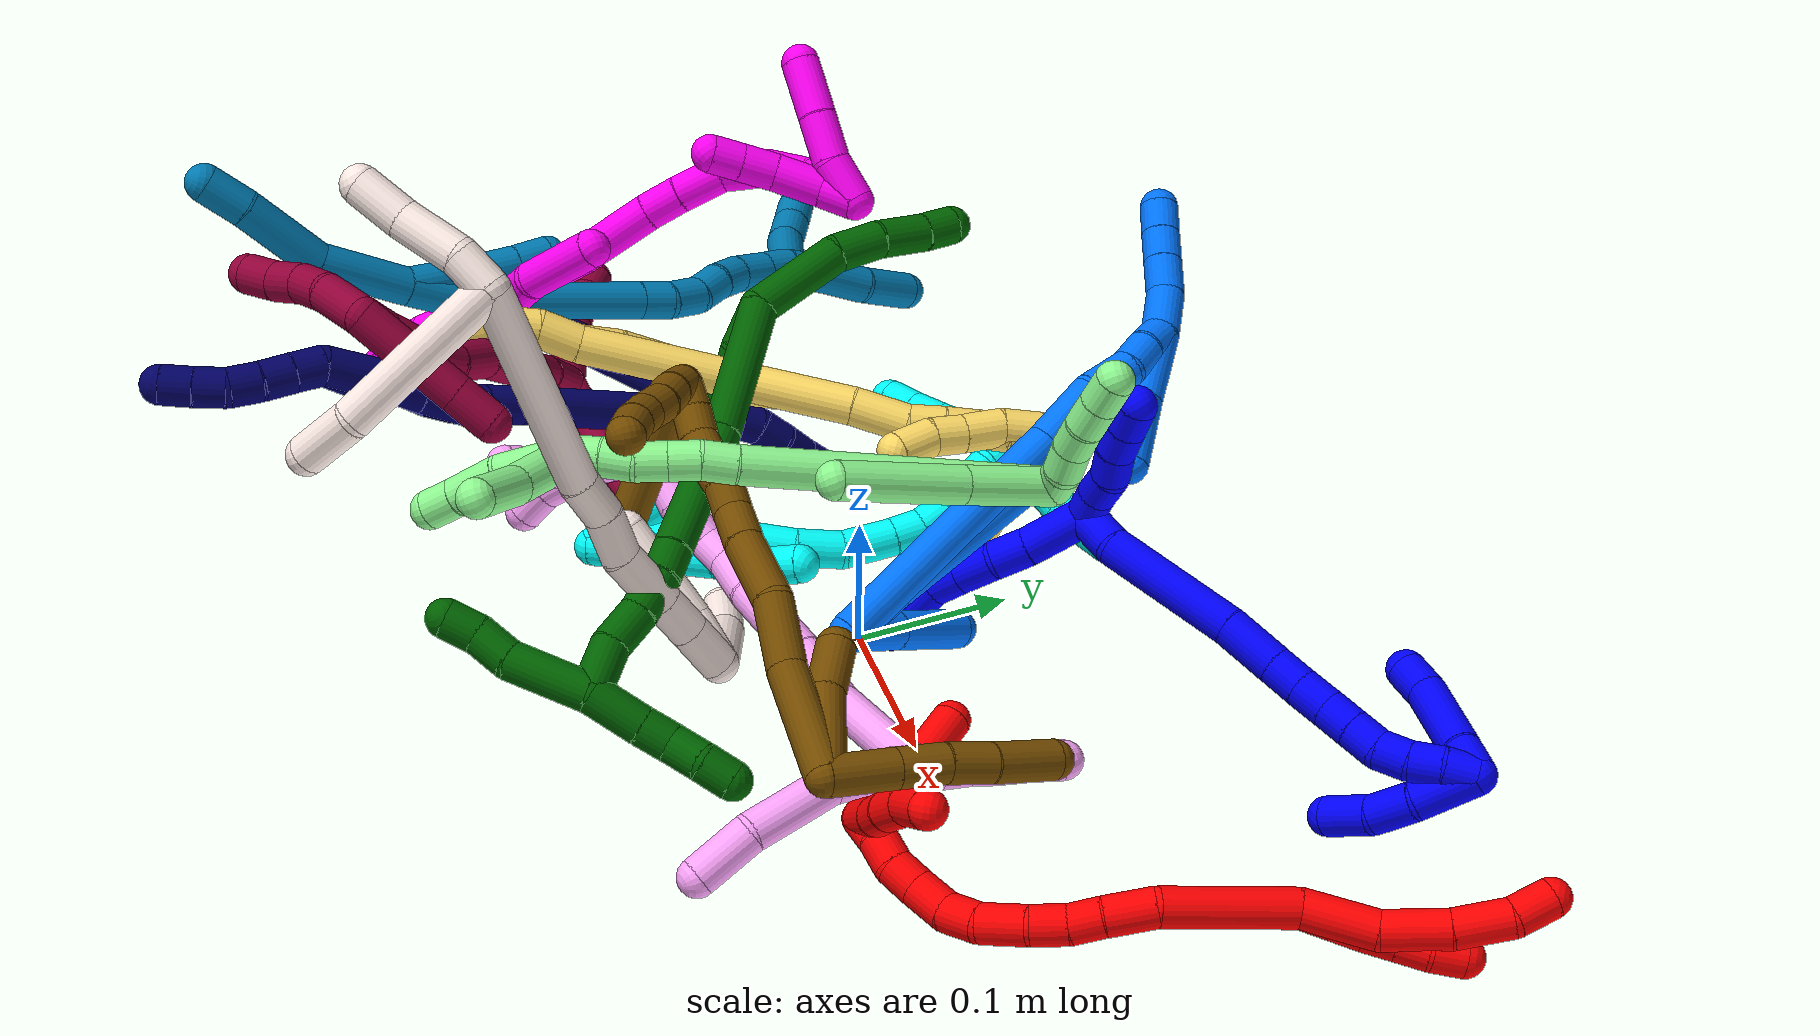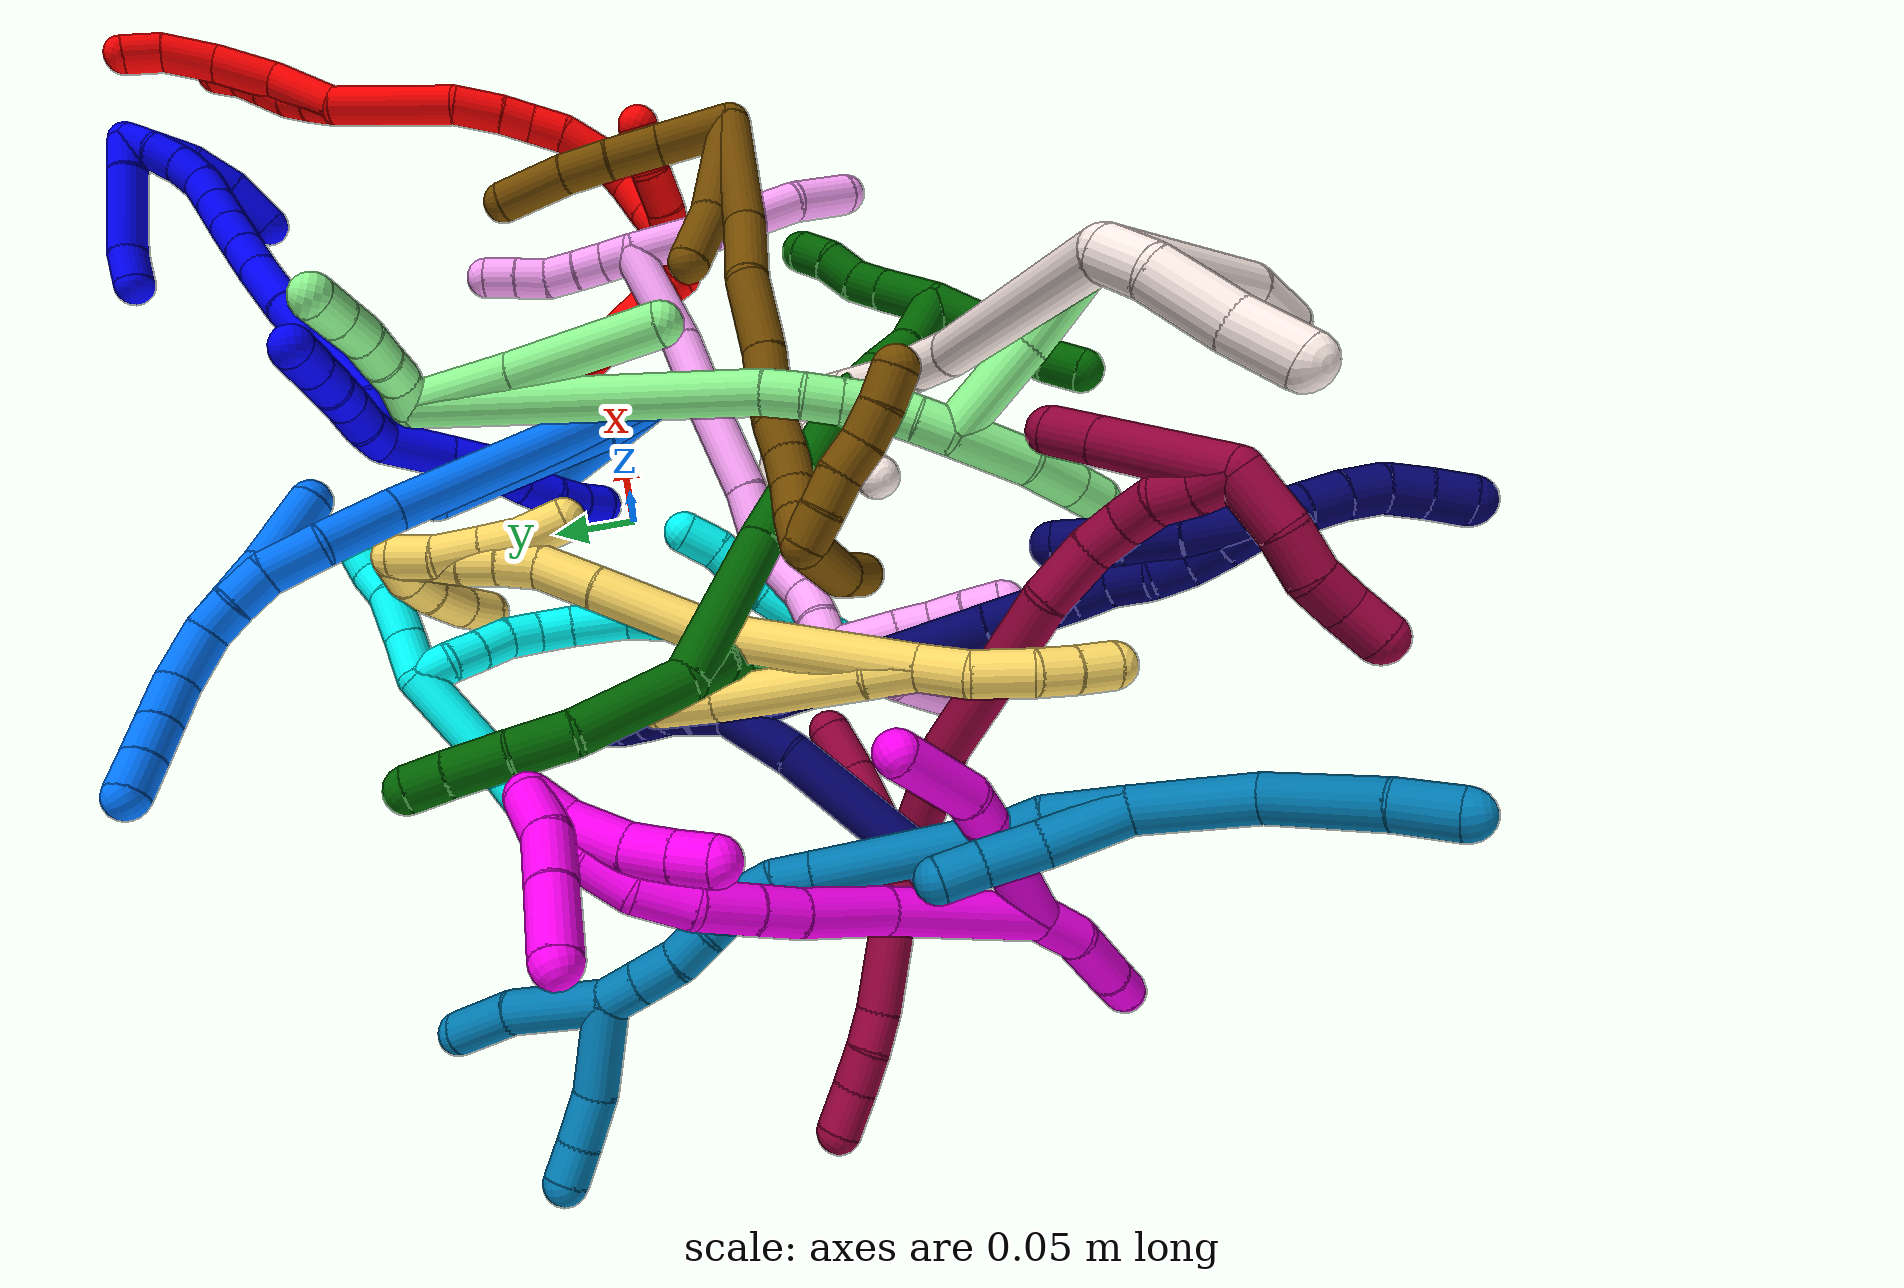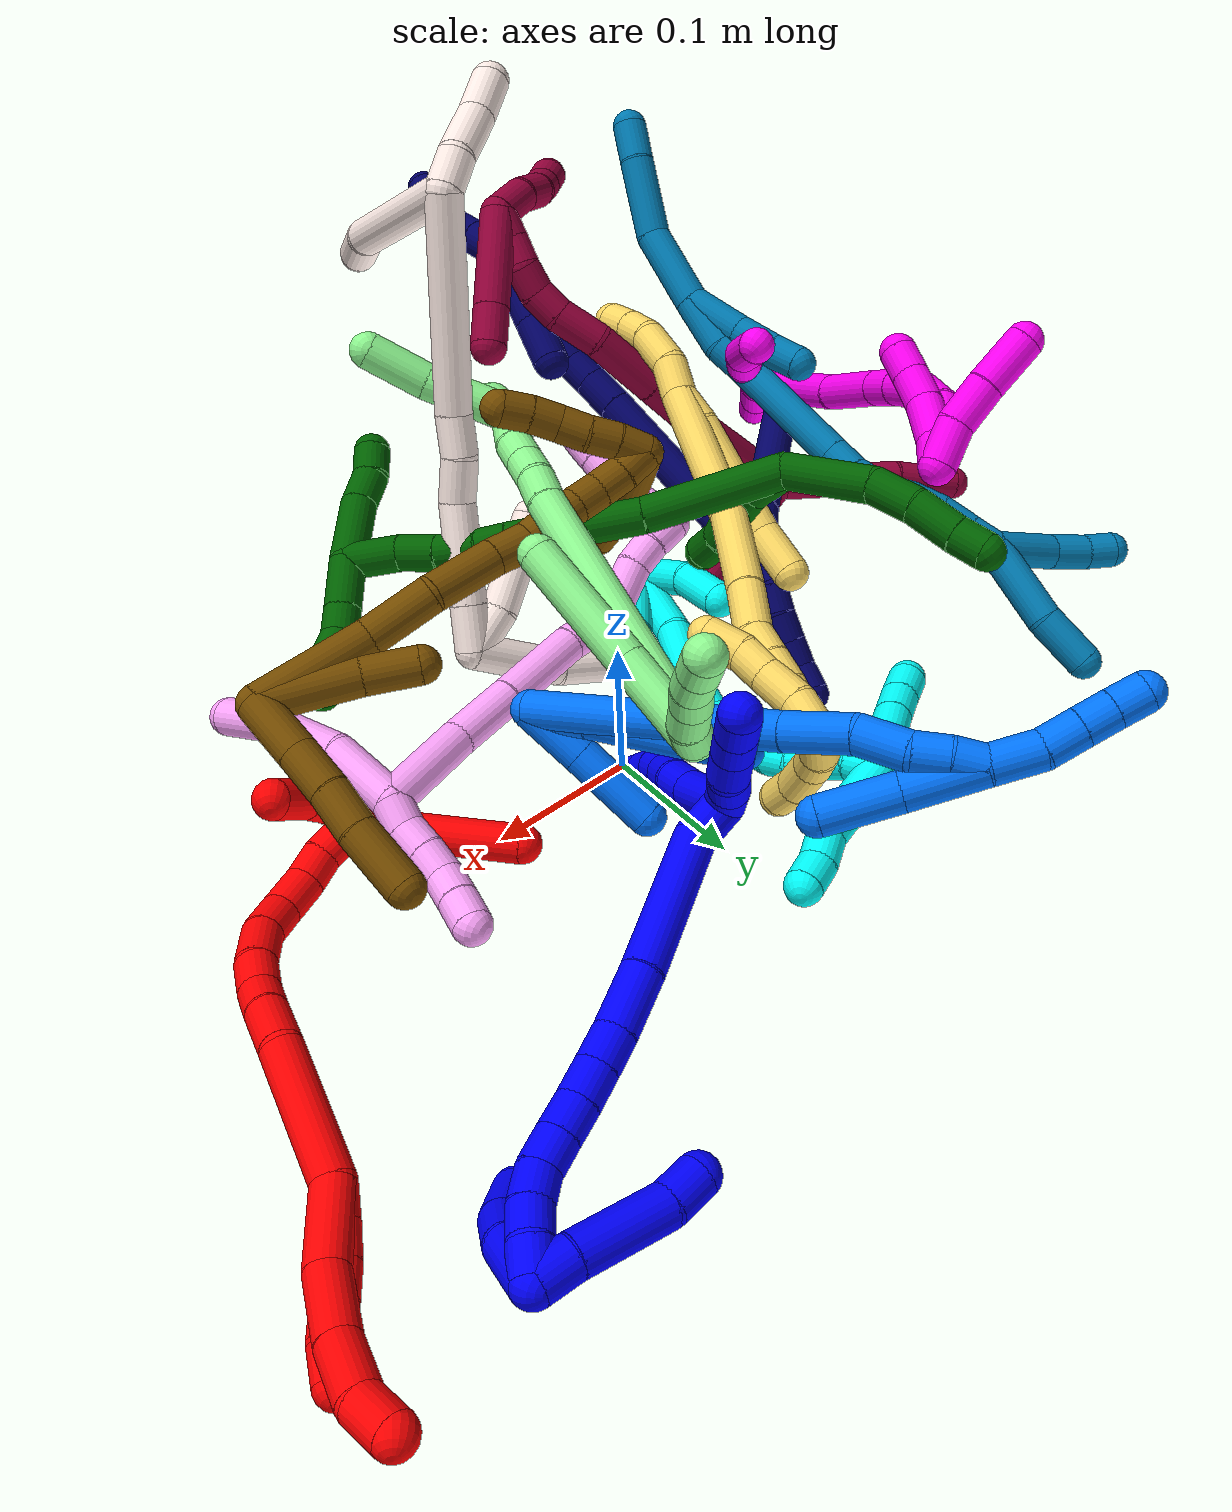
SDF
<sdf version="1.7">
 <world name="default">
  <plugin name="TubeGeneratorPlugin" filename="libtube_generator_plugin.so"/>
  <model name="photoneo_s_sensor">
   <static>1</static>
   <pose>0 0 2 1.57079 1.57079 3.14159</pose>
   <link name="link">
    <inertial><mass>0.1</mass></inertial>
    <sensor name="sensor" type="depth">
     <update_rate>30</update_rate>
     <camera>
      <horizontal_fov>1.22</horizontal_fov>
      <image><width>1920</width><height>1200</height><format>B8G8R8</format></image>
      <clip><near>0.1</near><far>4</far></clip>
      <depth_camera><output>points</output></depth_camera>
     </camera>
     <plugin name="camera_plugin" filename="libgazebo_ros_depth_camera.so">
      <baseline>0.2</baseline>
      <alwaysOn>1</alwaysOn>
      <updateRate>0.0</updateRate>
      <cameraName>camera_ir</cameraName>
      <imageTopicName>/camera/color/image_raw</imageTopicName>
      <cameraInfoTopicName>/camera/color/camera_info</cameraInfoTopicName>
      <depthImageTopicName>/camera/depth/image_raw</depthImageTopicName>
      <depthImageCameraInfoTopicName>/camera/depth/camera_info</depthImageCameraInfoTopicName>
      <pointCloudTopicName>/camera/depth/points</pointCloudTopicName>
      <frameName>fr_optical</frameName>
      <pointCloudCutoff>0.1</pointCloudCutoff>
      <pointCloudCutoffMax>2.0</pointCloudCutoffMax>
      <distortionK1>0</distortionK1>
      <distortionK2>0</distortionK2>
      <distortionK3>0</distortionK3>
      <distortionT1>0</distortionT1>
      <distortionT2>0</distortionT2>
      <CxPrime>0</CxPrime>
      <Cx>0</Cx>
      <Cy>0</Cy>
      <focalLength>0</focalLength>
      <hackBaseline>0</hackBaseline>
     </plugin>
    </sensor>
   </link>
  </model>
  <gravity>0 0 -9.8</gravity>
  <magnetic_field>6e-06 2.3e-05 -4.2e-05</magnetic_field>
  <atmosphere type="adiabatic"/>
  <physics name="default_physics" default="0" type="ode">
   <max_step_size>0.003</max_step_size>
   <real_time_factor>1</real_time_factor>
   <real_time_update_rate>1000</real_time_update_rate>
   <max_contacts>10000</max_contacts>
   <ode>
    <solver>
     <type>quick</type>
     <iters>100</iters>
     <sor>1.3</sor>
     <use_dynamic_moi_rescaling>0</use_dynamic_moi_rescaling>
    </solver>
    <constraints>
     <contact_max_correcting_vel>0</contact_max_correcting_vel>
     <contact_surface_layer>0.001</contact_surface_layer>
     <cfm>0</cfm>
     <erp>0.2</erp>
    </constraints>
   </ode>
  </physics>
  <scene><ambient>0.4 0.4 0.4 1</ambient><background>0.7 0.7 0.7 1</background><shadows>0</shadows></scene>
  <audio><device>default</device></audio>
  <spherical_coordinates>
   <surface_model>EARTH_WGS84</surface_model>
   <latitude_deg>0</latitude_deg>
   <longitude_deg>0</longitude_deg>
   <elevation>0</elevation>
   <heading_deg>0</heading_deg>
  </spherical_coordinates>
  <model name="bin">
   <static>1</static>
   <link name="bottom">
    <collision name="collision-bottom">
     <pose>0 0 -0.01 0 -0 0</pose>
     <geometry><box><size>0.8 0.6 0.02</size></box></geometry>
     <surface>
      <friction><ode><mu>100</mu><mu2>100</mu2></ode></friction>
      <contact><collide_bitmask>65535</collide_bitmask></contact>
     </surface>
    </collision>
   </link>
   <link name="west_wall">
    <collision name="collision-west_wall">
     <pose>-0.41 0 0.1 0 -0 0</pose>
     <geometry><box><size>0.02 0.6 0.2</size></box></geometry>
     <surface>
      <friction><ode><mu>100</mu><mu2>100</mu2></ode></friction>
      <contact><collide_bitmask>65535</collide_bitmask></contact>
     </surface>
    </collision>
   </link>
   <link name="east_wall">
    <collision name="collision-east_wall">
     <pose>0.41 0 0.1 0 -0 0</pose>
     <geometry><box><size>0.02 0.6 0.2</size></box></geometry>
     <surface>
      <friction><ode><mu>100</mu><mu2>100</mu2></ode></friction>
      <contact><collide_bitmask>65535</collide_bitmask></contact>
     </surface>
    </collision>
   </link>
   <link name="south_wall">
    <collision name="collision-south_wall">
     <pose>0 -0.31 0.1 0 -0 0</pose>
     <geometry><box><size>0.8 0.02 0.2</size></box></geometry>
     <surface>
      <friction><ode><mu>100</mu><mu2>100</mu2></ode></friction>
      <contact><collide_bitmask>65535</collide_bitmask></contact>
     </surface>
    </collision>
   </link>
   <link name="north_wall">
    <collision name="collision-north_wall">
     <pose>0 0.31 0.1 0 -0 0</pose>
     <geometry><box><size>0.8 0.02 0.2</size></box></geometry>
     <surface>
      <friction><ode><mu>100</mu><mu2>100</mu2></ode></friction>
      <contact><collide_bitmask>65535</collide_bitmask></contact>
     </surface>
    </collision>
   </link>
  </model>
  <model name="1">
   <static>0</static>
   <link name="1">
    <collision name="collision-cylinder-e_1_2_8">
     <pose>0.004979 0.003196 0.01945 -0.16285 0.247431 -0.020295</pose>
     <geometry><cylinder><radius>0.0125</radius><length>0.04066</length></cylinder></geometry>
     <surface>
      <friction><ode><mu>1.16</mu><mu2>1.16</mu2><slip1>0</slip1><slip2>0</slip2></ode></friction>
      <contact><ode><kp>1e+06</kp><kd>1</kd><max_vel>0</max_vel><min_depth>0.001</min_depth></ode></contact>
     </surface>
    </collision>
    <visual name="visual-cylinder-e_1_2_8">
     <pose>0.004979 0.003196 0.01945 -0.16285 0.247431 -0.020295</pose>
     <geometry><cylinder><radius>0.0125</radius><length>0.04066</length></cylinder></geometry>
     <material><ambient>0 0 1 1</ambient></material>
    </visual>
    <collision name="collision-cylinder-e_2_8_9">
     <pose>0.01349 0.007165 0.050027 -0.069429 0.306677 -0.010735</pose>
     <geometry><cylinder><radius>0.0125</radius><length>0.023399</length></cylinder></geometry>
     <surface>
      <friction><ode><mu>1.16</mu><mu2>1.16</mu2><slip1>0</slip1><slip2>0</slip2></ode></friction>
      <contact><ode><kp>1e+06</kp><kd>1</kd><max_vel>0</max_vel><min_depth>0.001</min_depth></ode></contact>
     </surface>
    </collision>
    <visual name="visual-cylinder-e_2_8_9">
     <pose>0.01349 0.007165 0.050027 -0.069429 0.306677 -0.010735</pose>
     <geometry><cylinder><radius>0.0125</radius><length>0.023399</length></cylinder></geometry>
     <material><ambient>0 0 1 1</ambient></material>
    </visual>
    <collision name="collision-cylinder-e_3_9_10">
     <pose>0.022689 0.01115 0.072102 -0.285325 0.460967 -0.067385</pose>
     <geometry><cylinder><radius>0.0125</radius><length>0.025478</length></cylinder></geometry>
     <surface>
      <friction><ode><mu>1.16</mu><mu2>1.16</mu2><slip1>0</slip1><slip2>0</slip2></ode></friction>
      <contact><ode><kp>1e+06</kp><kd>1</kd><max_vel>0</max_vel><min_depth>0.001</min_depth></ode></contact>
     </surface>
    </collision>
    <visual name="visual-cylinder-e_3_9_10">
     <pose>0.022689 0.01115 0.072102 -0.285325 0.460967 -0.067385</pose>
     <geometry><cylinder><radius>0.0125</radius><length>0.025478</length></cylinder></geometry>
     <material><ambient>0 0 1 1</ambient></material>
    </visual>
    <collision name="collision-cylinder-e_4_10_11">
     <pose>0.032164 0.016566 0.092118 -0.238427 0.387477 -0.046993</pose>
     <geometry><cylinder><radius>0.0125</radius><length>0.020159</length></cylinder></geometry>
     <surface>
      <friction><ode><mu>1.16</mu><mu2>1.16</mu2><slip1>0</slip1><slip2>0</slip2></ode></friction>
      <contact><ode><kp>1e+06</kp><kd>1</kd><max_vel>0</max_vel><min_depth>0.001</min_depth></ode></contact>
     </surface>
    </collision>
    <visual name="visual-cylinder-e_4_10_11">
     <pose>0.032164 0.016566 0.092118 -0.238427 0.387477 -0.046993</pose>
     <geometry><cylinder><radius>0.0125</radius><length>0.020159</length></cylinder></geometry>
     <material><ambient>0 0 1 1</ambient></material>
    </visual>
    <collision name="collision-cylinder-e_5_11_12">
     <pose>0.037407 0.023148 0.110127 -0.455324 0.143132 -0.033214</pose>
     <geometry><cylinder><radius>0.0125</radius><length>0.020116</length></cylinder></geometry>
     <surface>
      <friction><ode><mu>1.16</mu><mu2>1.16</mu2><slip1>0</slip1><slip2>0</slip2></ode></friction>
      <contact><ode><kp>1e+06</kp><kd>1</kd><max_vel>0</max_vel><min_depth>0.001</min_depth></ode></contact>
     </surface>
    </collision>
    <visual name="visual-cylinder-e_5_11_12">
     <pose>0.037407 0.023148 0.110127 -0.455324 0.143132 -0.033214</pose>
     <geometry><cylinder><radius>0.0125</radius><length>0.020116</length></cylinder></geometry>
     <material><ambient>0 0 1 1</ambient></material>
    </visual>
    <collision name="collision-cylinder-e_6_12_6">
     <pose>0.038735 0.031951 0.12814 -0.453885 -0.010524 0.00243</pose>
     <geometry><cylinder><radius>0.0125</radius><length>0.020188</length></cylinder></geometry>
     <surface>
      <friction><ode><mu>1.16</mu><mu2>1.16</mu2><slip1>0</slip1><slip2>0</slip2></ode></friction>
      <contact><ode><kp>1e+06</kp><kd>1</kd><max_vel>0</max_vel><min_depth>0.001</min_depth></ode></contact>
     </surface>
    </collision>
    <visual name="visual-cylinder-e_6_12_6">
     <pose>0.038735 0.031951 0.12814 -0.453885 -0.010524 0.00243</pose>
     <geometry><cylinder><radius>0.0125</radius><length>0.020188</length></cylinder></geometry>
     <material><ambient>0 0 1 1</ambient></material>
    </visual>
    <collision name="collision-cylinder-e_1_2_13">
     <pose>-0.001993 -0.007693 -0.00607 2.23887 -0.200604 -0.409418</pose>
     <geometry><cylinder><radius>0.0125</radius><length>0.02</length></cylinder></geometry>
     <surface>
      <friction><ode><mu>1.16</mu><mu2>1.16</mu2><slip1>0</slip1><slip2>0</slip2></ode></friction>
      <contact><ode><kp>1e+06</kp><kd>1</kd><max_vel>0</max_vel><min_depth>0.001</min_depth></ode></contact>
     </surface>
    </collision>
    <visual name="visual-cylinder-e_1_2_13">
     <pose>-0.001993 -0.007693 -0.00607 2.23887 -0.200604 -0.409418</pose>
     <geometry><cylinder><radius>0.0125</radius><length>0.02</length></cylinder></geometry>
     <material><ambient>0 0 1 1</ambient></material>
    </visual>
    <collision name="collision-cylinder-e_2_13_14">
     <pose>-0.007785 -0.022881 -0.017561 2.19682 -0.389731 -0.737218</pose>
     <geometry><cylinder><radius>0.0125</radius><length>0.02</length></cylinder></geometry>
     <surface>
      <friction><ode><mu>1.16</mu><mu2>1.16</mu2><slip1>0</slip1><slip2>0</slip2></ode></friction>
      <contact><ode><kp>1e+06</kp><kd>1</kd><max_vel>0</max_vel><min_depth>0.001</min_depth></ode></contact>
     </surface>
    </collision>
    <visual name="visual-cylinder-e_2_13_14">
     <pose>-0.007785 -0.022881 -0.017561 2.19682 -0.389731 -0.737218</pose>
     <geometry><cylinder><radius>0.0125</radius><length>0.02</length></cylinder></geometry>
     <material><ambient>0 0 1 1</ambient></material>
    </visual>
    <collision name="collision-cylinder-e_3_14_15">
     <pose>-0.012265 -0.039134 -0.027762 2.07054 -0.068178 -0.114818</pose>
     <geometry><cylinder><radius>0.0125</radius><length>0.02</length></cylinder></geometry>
     <surface>
      <friction><ode><mu>1.16</mu><mu2>1.16</mu2><slip1>0</slip1><slip2>0</slip2></ode></friction>
      <contact><ode><kp>1e+06</kp><kd>1</kd><max_vel>0</max_vel><min_depth>0.001</min_depth></ode></contact>
     </surface>
    </collision>
    <visual name="visual-cylinder-e_3_14_15">
     <pose>-0.012265 -0.039134 -0.027762 2.07054 -0.068178 -0.114818</pose>
     <geometry><cylinder><radius>0.0125</radius><length>0.02</length></cylinder></geometry>
     <material><ambient>0 0 1 1</ambient></material>
    </visual>
    <collision name="collision-cylinder-e_4_15_16">
     <pose>-0.01492 -0.055975 -0.038088 2.17204 -0.198694 -0.374071</pose>
     <geometry><cylinder><radius>0.0125</radius><length>0.02</length></cylinder></geometry>
     <surface>
      <friction><ode><mu>1.16</mu><mu2>1.16</mu2><slip1>0</slip1><slip2>0</slip2></ode></friction>
      <contact><ode><kp>1e+06</kp><kd>1</kd><max_vel>0</max_vel><min_depth>0.001</min_depth></ode></contact>
     </surface>
    </collision>
    <visual name="visual-cylinder-e_4_15_16">
     <pose>-0.01492 -0.055975 -0.038088 2.17204 -0.198694 -0.374071</pose>
     <geometry><cylinder><radius>0.0125</radius><length>0.02</length></cylinder></geometry>
     <material><ambient>0 0 1 1</ambient></material>
    </visual>
    <collision name="collision-cylinder-e_5_16_5">
     <pose>-0.018975 -0.072118 -0.049176 2.17325 -0.20963 -0.394846</pose>
     <geometry><cylinder><radius>0.0125</radius><length>0.02</length></cylinder></geometry>
     <surface>
      <friction><ode><mu>1.16</mu><mu2>1.16</mu2><slip1>0</slip1><slip2>0</slip2></ode></friction>
      <contact><ode><kp>1e+06</kp><kd>1</kd><max_vel>0</max_vel><min_depth>0.001</min_depth></ode></contact>
     </surface>
    </collision>
    <visual name="visual-cylinder-e_5_16_5">
     <pose>-0.018975 -0.072118 -0.049176 2.17325 -0.20963 -0.394846</pose>
     <geometry><cylinder><radius>0.0125</radius><length>0.02</length></cylinder></geometry>
     <material><ambient>0 0 1 1</ambient></material>
    </visual>
    <collision name="collision-cylinder-e_1_2_17">
     <pose>-0.014134 0.002833 -0.001532 -2.0665 -1.34678 1.85819</pose>
     <geometry><cylinder><radius>0.0125</radius><length>0.028992</length></cylinder></geometry>
     <surface>
      <friction><ode><mu>1.16</mu><mu2>1.16</mu2><slip1>0</slip1><slip2>0</slip2></ode></friction>
      <contact><ode><kp>1e+06</kp><kd>1</kd><max_vel>0</max_vel><min_depth>0.001</min_depth></ode></contact>
     </surface>
    </collision>
    <visual name="visual-cylinder-e_1_2_17">
     <pose>-0.014134 0.002833 -0.001532 -2.0665 -1.34678 1.85819</pose>
     <geometry><cylinder><radius>0.0125</radius><length>0.028992</length></cylinder></geometry>
     <material><ambient>0 0 1 1</ambient></material>
    </visual>
    <collision name="collision-cylinder-e_2_17_18">
     <pose>-0.067644 0.021349 -0.01835 -2.34336 -1.06322 1.89729</pose>
     <geometry><cylinder><radius>0.0125</radius><length>0.090114</length></cylinder></geometry>
     <surface>
      <friction><ode><mu>1.16</mu><mu2>1.16</mu2><slip1>0</slip1><slip2>0</slip2></ode></friction>
      <contact><ode><kp>1e+06</kp><kd>1</kd><max_vel>0</max_vel><min_depth>0.001</min_depth></ode></contact>
     </surface>
    </collision>
    <visual name="visual-cylinder-e_2_17_18">
     <pose>-0.067644 0.021349 -0.01835 -2.34336 -1.06322 1.89729</pose>
     <geometry><cylinder><radius>0.0125</radius><length>0.090114</length></cylinder></geometry>
     <material><ambient>0 0 1 1</ambient></material>
    </visual>
    <collision name="collision-cylinder-e_3_18_19">
     <pose>-0.123533 0.044382 -0.038314 -2.13767 -1.0853 1.66481</pose>
     <geometry><cylinder><radius>0.0125</radius><length>0.03734</length></cylinder></geometry>
     <surface>
      <friction><ode><mu>1.16</mu><mu2>1.16</mu2><slip1>0</slip1><slip2>0</slip2></ode></friction>
      <contact><ode><kp>1e+06</kp><kd>1</kd><max_vel>0</max_vel><min_depth>0.001</min_depth></ode></contact>
     </surface>
    </collision>
    <visual name="visual-cylinder-e_3_18_19">
     <pose>-0.123533 0.044382 -0.038314 -2.13767 -1.0853 1.66481</pose>
     <geometry><cylinder><radius>0.0125</radius><length>0.03734</length></cylinder></geometry>
     <material><ambient>0 0 1 1</ambient></material>
    </visual>
    <collision name="collision-cylinder-e_4_19_20">
     <pose>-0.150001 0.055262 -0.045617 -2.2101 -1.15476 1.82726</pose>
     <geometry><cylinder><radius>0.0125</radius><length>0.021768</length></cylinder></geometry>
     <surface>
      <friction><ode><mu>1.16</mu><mu2>1.16</mu2><slip1>0</slip1><slip2>0</slip2></ode></friction>
      <contact><ode><kp>1e+06</kp><kd>1</kd><max_vel>0</max_vel><min_depth>0.001</min_depth></ode></contact>
     </surface>
    </collision>
    <visual name="visual-cylinder-e_4_19_20">
     <pose>-0.150001 0.055262 -0.045617 -2.2101 -1.15476 1.82726</pose>
     <geometry><cylinder><radius>0.0125</radius><length>0.021768</length></cylinder></geometry>
     <material><ambient>0 0 1 1</ambient></material>
    </visual>
    <collision name="collision-cylinder-e_5_20_21">
     <pose>-0.169843 0.061904 -0.051015 -2.29868 -1.17173 1.95326</pose>
     <geometry><cylinder><radius>0.0125</radius><length>0.021457</length></cylinder></geometry>
     <surface>
      <friction><ode><mu>1.16</mu><mu2>1.16</mu2><slip1>0</slip1><slip2>0</slip2></ode></friction>
      <contact><ode><kp>1e+06</kp><kd>1</kd><max_vel>0</max_vel><min_depth>0.001</min_depth></ode></contact>
     </surface>
    </collision>
    <visual name="visual-cylinder-e_5_20_21">
     <pose>-0.169843 0.061904 -0.051015 -2.29868 -1.17173 1.95326</pose>
     <geometry><cylinder><radius>0.0125</radius><length>0.021457</length></cylinder></geometry>
     <material><ambient>0 0 1 1</ambient></material>
    </visual>
    <collision name="collision-cylinder-e_6_21_22">
     <pose>-0.189166 0.067646 -0.056231 -2.31932 -1.20744 2.01405</pose>
     <geometry><cylinder><radius>0.0125</radius><length>0.020195</length></cylinder></geometry>
     <surface>
      <friction><ode><mu>1.16</mu><mu2>1.16</mu2><slip1>0</slip1><slip2>0</slip2></ode></friction>
      <contact><ode><kp>1e+06</kp><kd>1</kd><max_vel>0</max_vel><min_depth>0.001</min_depth></ode></contact>
     </surface>
    </collision>
    <visual name="visual-cylinder-e_6_21_22">
     <pose>-0.189166 0.067646 -0.056231 -2.31932 -1.20744 2.01405</pose>
     <geometry><cylinder><radius>0.0125</radius><length>0.020195</length></cylinder></geometry>
     <material><ambient>0 0 1 1</ambient></material>
    </visual>
    <collision name="collision-cylinder-e_7_22_23">
     <pose>-0.207927 0.073012 -0.061183 -2.31284 -1.19173 1.99073</pose>
     <geometry><cylinder><radius>0.0125</radius><length>0.02007</length></cylinder></geometry>
     <surface>
      <friction><ode><mu>1.16</mu><mu2>1.16</mu2><slip1>0</slip1><slip2>0</slip2></ode></friction>
      <contact><ode><kp>1e+06</kp><kd>1</kd><max_vel>0</max_vel><min_depth>0.001</min_depth></ode></contact>
     </surface>
    </collision>
    <visual name="visual-cylinder-e_7_22_23">
     <pose>-0.207927 0.073012 -0.061183 -2.31284 -1.19173 1.99073</pose>
     <geometry><cylinder><radius>0.0125</radius><length>0.02007</length></cylinder></geometry>
     <material><ambient>0 0 1 1</ambient></material>
    </visual>
    <collision name="collision-cylinder-e_8_23_24">
     <pose>-0.225297 0.078163 -0.06915 -2.72527 -0.932679 2.347</pose>
     <geometry><cylinder><radius>0.0125</radius><length>0.020037</length></cylinder></geometry>
     <surface>
      <friction><ode><mu>1.16</mu><mu2>1.16</mu2><slip1>0</slip1><slip2>0</slip2></ode></friction>
      <contact><ode><kp>1e+06</kp><kd>1</kd><max_vel>0</max_vel><min_depth>0.001</min_depth></ode></contact>
     </surface>
    </collision>
    <visual name="visual-cylinder-e_8_23_24">
     <pose>-0.225297 0.078163 -0.06915 -2.72527 -0.932679 2.347</pose>
     <geometry><cylinder><radius>0.0125</radius><length>0.020037</length></cylinder></geometry>
     <material><ambient>0 0 1 1</ambient></material>
    </visual>
    <collision name="collision-cylinder-e_9_24_25">
     <pose>-0.239894 0.08301 -0.081774 -2.81418 -0.71336 2.30705</pose>
     <geometry><cylinder><radius>0.0125</radius><length>0.020016</length></cylinder></geometry>
     <surface>
      <friction><ode><mu>1.16</mu><mu2>1.16</mu2><slip1>0</slip1><slip2>0</slip2></ode></friction>
      <contact><ode><kp>1e+06</kp><kd>1</kd><max_vel>0</max_vel><min_depth>0.001</min_depth></ode></contact>
     </surface>
    </collision>
    <visual name="visual-cylinder-e_9_24_25">
     <pose>-0.239894 0.08301 -0.081774 -2.81418 -0.71336 2.30705</pose>
     <geometry><cylinder><radius>0.0125</radius><length>0.020016</length></cylinder></geometry>
     <material><ambient>0 0 1 1</ambient></material>
    </visual>
    <collision name="collision-cylinder-e_10_25_1">
     <pose>-0.252439 0.089606 -0.095782 -2.59508 -0.642686 1.742</pose>
     <geometry><cylinder><radius>0.0125</radius><length>0.02001</length></cylinder></geometry>
     <surface>
      <friction><ode><mu>1.16</mu><mu2>1.16</mu2><slip1>0</slip1><slip2>0</slip2></ode></friction>
      <contact><ode><kp>1e+06</kp><kd>1</kd><max_vel>0</max_vel><min_depth>0.001</min_depth></ode></contact>
     </surface>
    </collision>
    <visual name="visual-cylinder-e_10_25_1">
     <pose>-0.252439 0.089606 -0.095782 -2.59508 -0.642686 1.742</pose>
     <geometry><cylinder><radius>0.0125</radius><length>0.02001</length></cylinder></geometry>
     <material><ambient>0 0 1 1</ambient></material>
    </visual>
    <collision name="collision-cylinder-e_1_1_26">
     <pose>-0.252295 0.096469 -0.083881 -0.143091 0.313564 -0.022657</pose>
     <geometry><cylinder><radius>0.0125</radius><length>0.039816</length></cylinder></geometry>
     <surface>
      <friction><ode><mu>1.16</mu><mu2>1.16</mu2><slip1>0</slip1><slip2>0</slip2></ode></friction>
      <contact><ode><kp>1e+06</kp><kd>1</kd><max_vel>0</max_vel><min_depth>0.001</min_depth></ode></contact>
     </surface>
    </collision>
    <visual name="visual-cylinder-e_1_1_26">
     <pose>-0.252295 0.096469 -0.083881 -0.143091 0.313564 -0.022657</pose>
     <geometry><cylinder><radius>0.0125</radius><length>0.039816</length></cylinder></geometry>
     <material><ambient>0 0 1 1</ambient></material>
    </visual>
    <collision name="collision-cylinder-e_2_26_27">
     <pose>-0.239252 0.102961 -0.053225 -0.30817 0.504486 -0.080017</pose>
     <geometry><cylinder><radius>0.0125</radius><length>0.02856</length></cylinder></geometry>
     <surface>
      <friction><ode><mu>1.16</mu><mu2>1.16</mu2><slip1>0</slip1><slip2>0</slip2></ode></friction>
      <contact><ode><kp>1e+06</kp><kd>1</kd><max_vel>0</max_vel><min_depth>0.001</min_depth></ode></contact>
     </surface>
    </collision>
    <visual name="visual-cylinder-e_2_26_27">
     <pose>-0.239252 0.102961 -0.053225 -0.30817 0.504486 -0.080017</pose>
     <geometry><cylinder><radius>0.0125</radius><length>0.02856</length></cylinder></geometry>
     <material><ambient>0 0 1 1</ambient></material>
    </visual>
    <collision name="collision-cylinder-e_3_27_4">
     <pose>-0.2209 0.110538 -0.031085 -0.354429 0.80972 -0.153195</pose>
     <geometry><cylinder><radius>0.0125</radius><length>0.031625</length></cylinder></geometry>
     <surface>
      <friction><ode><mu>1.16</mu><mu2>1.16</mu2><slip1>0</slip1><slip2>0</slip2></ode></friction>
      <contact><ode><kp>1e+06</kp><kd>1</kd><max_vel>0</max_vel><min_depth>0.001</min_depth></ode></contact>
     </surface>
    </collision>
    <visual name="visual-cylinder-e_3_27_4">
     <pose>-0.2209 0.110538 -0.031085 -0.354429 0.80972 -0.153195</pose>
     <geometry><cylinder><radius>0.0125</radius><length>0.031625</length></cylinder></geometry>
     <material><ambient>0 0 1 1</ambient></material>
    </visual>
    <collision name="collision-cylinder-e_1_1_28">
     <pose>-0.247324 0.093589 -0.104082 3.01939 1.43942 3.00224</pose>
     <geometry><cylinder><radius>0.0125</radius><length>0.022417</length></cylinder></geometry>
     <surface>
      <friction><ode><mu>1.16</mu><mu2>1.16</mu2><slip1>0</slip1><slip2>0</slip2></ode></friction>
      <contact><ode><kp>1e+06</kp><kd>1</kd><max_vel>0</max_vel><min_depth>0.001</min_depth></ode></contact>
     </surface>
    </collision>
    <visual name="visual-cylinder-e_1_1_28">
     <pose>-0.247324 0.093589 -0.104082 3.01939 1.43942 3.00224</pose>
     <geometry><cylinder><radius>0.0125</radius><length>0.022417</length></cylinder></geometry>
     <material><ambient>0 0 1 1</ambient></material>
    </visual>
    <collision name="collision-cylinder-e_2_28_29">
     <pose>-0.209051 0.096569 -0.10935 -2.44953 1.39052 -2.3257</pose>
     <geometry><cylinder><radius>0.0125</radius><length>0.055217</length></cylinder></geometry>
     <surface>
      <friction><ode><mu>1.16</mu><mu2>1.16</mu2><slip1>0</slip1><slip2>0</slip2></ode></friction>
      <contact><ode><kp>1e+06</kp><kd>1</kd><max_vel>0</max_vel><min_depth>0.001</min_depth></ode></contact>
     </surface>
    </collision>
    <visual name="visual-cylinder-e_2_28_29">
     <pose>-0.209051 0.096569 -0.10935 -2.44953 1.39052 -2.3257</pose>
     <geometry><cylinder><radius>0.0125</radius><length>0.055217</length></cylinder></geometry>
     <material><ambient>0 0 1 1</ambient></material>
    </visual>
    <collision name="collision-cylinder-e_3_29_3">
     <pose>-0.17073 0.099125 -0.11275 0.971108 1.50547 0.918148</pose>
     <geometry><cylinder><radius>0.0125</radius><length>0.022367</length></cylinder></geometry>
     <surface>
      <friction><ode><mu>1.16</mu><mu2>1.16</mu2><slip1>0</slip1><slip2>0</slip2></ode></friction>
      <contact><ode><kp>1e+06</kp><kd>1</kd><max_vel>0</max_vel><min_depth>0.001</min_depth></ode></contact>
     </surface>
    </collision>
    <visual name="visual-cylinder-e_3_29_3">
     <pose>-0.17073 0.099125 -0.11275 0.971108 1.50547 0.918148</pose>
     <geometry><cylinder><radius>0.0125</radius><length>0.022367</length></cylinder></geometry>
     <material><ambient>0 0 1 1</ambient></material>
    </visual>
    <collision name="collision-sphere-3">
     <pose>-0.159571 0.098523 -0.112338 0 -0 0</pose>
     <geometry><sphere><radius>0.0125</radius></sphere></geometry>
     <surface>
      <friction><ode><mu>1.16</mu><mu2>1.16</mu2><slip1>0</slip1><slip2>0</slip2></ode></friction>
      <contact><ode><kp>1e+06</kp><kd>1</kd><max_vel>0</max_vel><min_depth>0.001</min_depth></ode></contact>
     </surface>
    </collision>
    <visual name="visual-sphere-3">
     <pose>-0.159571 0.098523 -0.112338 0 -0 0</pose>
     <geometry><sphere><radius>0.0125</radius></sphere></geometry>
     <material><ambient>0 0 1 1</ambient></material>
    </visual>
    <collision name="collision-sphere-29">
     <pose>-0.18189 0.099728 -0.113162 0 -0 0</pose>
     <geometry><sphere><radius>0.0125</radius></sphere></geometry>
     <surface>
      <friction><ode><mu>1.16</mu><mu2>1.16</mu2><slip1>0</slip1><slip2>0</slip2></ode></friction>
      <contact><ode><kp>1e+06</kp><kd>1</kd><max_vel>0</max_vel><min_depth>0.001</min_depth></ode></contact>
     </surface>
    </collision>
    <visual name="visual-sphere-29">
     <pose>-0.18189 0.099728 -0.113162 0 -0 0</pose>
     <geometry><sphere><radius>0.0125</radius></sphere></geometry>
     <material><ambient>0 0 1 1</ambient></material>
    </visual>
    <collision name="collision-sphere-28">
     <pose>-0.236212 0.09341 -0.105539 0 -0 0</pose>
     <geometry><sphere><radius>0.0125</radius></sphere></geometry>
     <surface>
      <friction><ode><mu>1.16</mu><mu2>1.16</mu2><slip1>0</slip1><slip2>0</slip2></ode></friction>
      <contact><ode><kp>1e+06</kp><kd>1</kd><max_vel>0</max_vel><min_depth>0.001</min_depth></ode></contact>
     </surface>
    </collision>
    <visual name="visual-sphere-28">
     <pose>-0.236212 0.09341 -0.105539 0 -0 0</pose>
     <geometry><sphere><radius>0.0125</radius></sphere></geometry>
     <material><ambient>0 0 1 1</ambient></material>
    </visual>
    <collision name="collision-sphere-4">
     <pose>-0.20945 0.114322 -0.020857 0 -0 0</pose>
     <geometry><sphere><radius>0.0125</radius></sphere></geometry>
     <surface>
      <friction><ode><mu>1.16</mu><mu2>1.16</mu2><slip1>0</slip1><slip2>0</slip2></ode></friction>
      <contact><ode><kp>1e+06</kp><kd>1</kd><max_vel>0</max_vel><min_depth>0.001</min_depth></ode></contact>
     </surface>
    </collision>
    <visual name="visual-sphere-4">
     <pose>-0.20945 0.114322 -0.020857 0 -0 0</pose>
     <geometry><sphere><radius>0.0125</radius></sphere></geometry>
     <material><ambient>0 0 1 1</ambient></material>
    </visual>
    <collision name="collision-sphere-27">
     <pose>-0.23235 0.106753 -0.041313 0 -0 0</pose>
     <geometry><sphere><radius>0.0125</radius></sphere></geometry>
     <surface>
      <friction><ode><mu>1.16</mu><mu2>1.16</mu2><slip1>0</slip1><slip2>0</slip2></ode></friction>
      <contact><ode><kp>1e+06</kp><kd>1</kd><max_vel>0</max_vel><min_depth>0.001</min_depth></ode></contact>
     </surface>
    </collision>
    <visual name="visual-sphere-27">
     <pose>-0.23235 0.106753 -0.041313 0 -0 0</pose>
     <geometry><sphere><radius>0.0125</radius></sphere></geometry>
     <material><ambient>0 0 1 1</ambient></material>
    </visual>
    <collision name="collision-sphere-26">
     <pose>-0.246154 0.099169 -0.065137 0 -0 0</pose>
     <geometry><sphere><radius>0.0125</radius></sphere></geometry>
     <surface>
      <friction><ode><mu>1.16</mu><mu2>1.16</mu2><slip1>0</slip1><slip2>0</slip2></ode></friction>
      <contact><ode><kp>1e+06</kp><kd>1</kd><max_vel>0</max_vel><min_depth>0.001</min_depth></ode></contact>
     </surface>
    </collision>
    <visual name="visual-sphere-26">
     <pose>-0.246154 0.099169 -0.065137 0 -0 0</pose>
     <geometry><sphere><radius>0.0125</radius></sphere></geometry>
     <material><ambient>0 0 1 1</ambient></material>
    </visual>
    <collision name="collision-sphere-1">
     <pose>-0.258435 0.093768 -0.102624 0 -0 0</pose>
     <geometry><sphere><radius>0.0125</radius></sphere></geometry>
     <surface>
      <friction><ode><mu>1.16</mu><mu2>1.16</mu2><slip1>0</slip1><slip2>0</slip2></ode></friction>
      <contact><ode><kp>1e+06</kp><kd>1</kd><max_vel>0</max_vel><min_depth>0.001</min_depth></ode></contact>
     </surface>
    </collision>
    <visual name="visual-sphere-1">
     <pose>-0.258435 0.093768 -0.102624 0 -0 0</pose>
     <geometry><sphere><radius>0.0125</radius></sphere></geometry>
     <material><ambient>0 0 1 1</ambient></material>
    </visual>
    <collision name="collision-sphere-25">
     <pose>-0.246443 0.085444 -0.08894 0 -0 0</pose>
     <geometry><sphere><radius>0.0125</radius></sphere></geometry>
     <surface>
      <friction><ode><mu>1.16</mu><mu2>1.16</mu2><slip1>0</slip1><slip2>0</slip2></ode></friction>
      <contact><ode><kp>1e+06</kp><kd>1</kd><max_vel>0</max_vel><min_depth>0.001</min_depth></ode></contact>
     </surface>
    </collision>
    <visual name="visual-sphere-25">
     <pose>-0.246443 0.085444 -0.08894 0 -0 0</pose>
     <geometry><sphere><radius>0.0125</radius></sphere></geometry>
     <material><ambient>0 0 1 1</ambient></material>
    </visual>
    <collision name="collision-sphere-24">
     <pose>-0.233344 0.080576 -0.074609 0 -0 0</pose>
     <geometry><sphere><radius>0.0125</radius></sphere></geometry>
     <surface>
      <friction><ode><mu>1.16</mu><mu2>1.16</mu2><slip1>0</slip1><slip2>0</slip2></ode></friction>
      <contact><ode><kp>1e+06</kp><kd>1</kd><max_vel>0</max_vel><min_depth>0.001</min_depth></ode></contact>
     </surface>
    </collision>
    <visual name="visual-sphere-24">
     <pose>-0.233344 0.080576 -0.074609 0 -0 0</pose>
     <geometry><sphere><radius>0.0125</radius></sphere></geometry>
     <material><ambient>0 0 1 1</ambient></material>
    </visual>
    <collision name="collision-sphere-23">
     <pose>-0.21725 0.075749 -0.063692 0 -0 0</pose>
     <geometry><sphere><radius>0.0125</radius></sphere></geometry>
     <surface>
      <friction><ode><mu>1.16</mu><mu2>1.16</mu2><slip1>0</slip1><slip2>0</slip2></ode></friction>
      <contact><ode><kp>1e+06</kp><kd>1</kd><max_vel>0</max_vel><min_depth>0.001</min_depth></ode></contact>
     </surface>
    </collision>
    <visual name="visual-sphere-23">
     <pose>-0.21725 0.075749 -0.063692 0 -0 0</pose>
     <geometry><sphere><radius>0.0125</radius></sphere></geometry>
     <material><ambient>0 0 1 1</ambient></material>
    </visual>
    <collision name="collision-sphere-22">
     <pose>-0.198605 0.070275 -0.058673 0 -0 0</pose>
     <geometry><sphere><radius>0.0125</radius></sphere></geometry>
     <surface>
      <friction><ode><mu>1.16</mu><mu2>1.16</mu2><slip1>0</slip1><slip2>0</slip2></ode></friction>
      <contact><ode><kp>1e+06</kp><kd>1</kd><max_vel>0</max_vel><min_depth>0.001</min_depth></ode></contact>
     </surface>
    </collision>
    <visual name="visual-sphere-22">
     <pose>-0.198605 0.070275 -0.058673 0 -0 0</pose>
     <geometry><sphere><radius>0.0125</radius></sphere></geometry>
     <material><ambient>0 0 1 1</ambient></material>
    </visual>
    <collision name="collision-sphere-21">
     <pose>-0.179728 0.065016 -0.053788 0 -0 0</pose>
     <geometry><sphere><radius>0.0125</radius></sphere></geometry>
     <surface>
      <friction><ode><mu>1.16</mu><mu2>1.16</mu2><slip1>0</slip1><slip2>0</slip2></ode></friction>
      <contact><ode><kp>1e+06</kp><kd>1</kd><max_vel>0</max_vel><min_depth>0.001</min_depth></ode></contact>
     </surface>
    </collision>
    <visual name="visual-sphere-21">
     <pose>-0.179728 0.065016 -0.053788 0 -0 0</pose>
     <geometry><sphere><radius>0.0125</radius></sphere></geometry>
     <material><ambient>0 0 1 1</ambient></material>
    </visual>
    <collision name="collision-sphere-12">
     <pose>0.038842 0.027526 0.119068 0 -0 0</pose>
     <geometry><sphere><radius>0.0125</radius></sphere></geometry>
     <surface>
      <friction><ode><mu>1.16</mu><mu2>1.16</mu2><slip1>0</slip1><slip2>0</slip2></ode></friction>
      <contact><ode><kp>1e+06</kp><kd>1</kd><max_vel>0</max_vel><min_depth>0.001</min_depth></ode></contact>
     </surface>
    </collision>
    <visual name="visual-sphere-12">
     <pose>0.038842 0.027526 0.119068 0 -0 0</pose>
     <geometry><sphere><radius>0.0125</radius></sphere></geometry>
     <material><ambient>0 0 1 1</ambient></material>
    </visual>
    <collision name="collision-sphere-11">
     <pose>0.035972 0.01877 0.101186 0 -0 0</pose>
     <geometry><sphere><radius>0.0125</radius></sphere></geometry>
     <surface>
      <friction><ode><mu>1.16</mu><mu2>1.16</mu2><slip1>0</slip1><slip2>0</slip2></ode></friction>
      <contact><ode><kp>1e+06</kp><kd>1</kd><max_vel>0</max_vel><min_depth>0.001</min_depth></ode></contact>
     </surface>
    </collision>
    <visual name="visual-sphere-11">
     <pose>0.035972 0.01877 0.101186 0 -0 0</pose>
     <geometry><sphere><radius>0.0125</radius></sphere></geometry>
     <material><ambient>0 0 1 1</ambient></material>
    </visual>
    <collision name="collision-sphere-10">
     <pose>0.028355 0.014362 0.083049 0 -0 0</pose>
     <geometry><sphere><radius>0.0125</radius></sphere></geometry>
     <surface>
      <friction><ode><mu>1.16</mu><mu2>1.16</mu2><slip1>0</slip1><slip2>0</slip2></ode></friction>
      <contact><ode><kp>1e+06</kp><kd>1</kd><max_vel>0</max_vel><min_depth>0.001</min_depth></ode></contact>
     </surface>
    </collision>
    <visual name="visual-sphere-10">
     <pose>0.028355 0.014362 0.083049 0 -0 0</pose>
     <geometry><sphere><radius>0.0125</radius></sphere></geometry>
     <material><ambient>0 0 1 1</ambient></material>
    </visual>
    <collision name="collision-sphere-9">
     <pose>0.017022 0.007939 0.061154 0 -0 0</pose>
     <geometry><sphere><radius>0.0125</radius></sphere></geometry>
     <surface>
      <friction><ode><mu>1.16</mu><mu2>1.16</mu2><slip1>0</slip1><slip2>0</slip2></ode></friction>
      <contact><ode><kp>1e+06</kp><kd>1</kd><max_vel>0</max_vel><min_depth>0.001</min_depth></ode></contact>
     </surface>
    </collision>
    <visual name="visual-sphere-9">
     <pose>0.017022 0.007939 0.061154 0 -0 0</pose>
     <geometry><sphere><radius>0.0125</radius></sphere></geometry>
     <material><ambient>0 0 1 1</ambient></material>
    </visual>
    <collision name="collision-sphere-2">
     <geometry><sphere><radius>0.0125</radius></sphere></geometry>
     <surface>
      <friction><ode><mu>1.16</mu><mu2>1.16</mu2><slip1>0</slip1><slip2>0</slip2></ode></friction>
      <contact><ode><kp>1e+06</kp><kd>1</kd><max_vel>0</max_vel><min_depth>0.001</min_depth></ode></contact>
     </surface>
    </collision>
    <visual name="visual-sphere-2">
     <geometry><sphere><radius>0.0125</radius></sphere></geometry>
     <material><ambient>0 0 1 1</ambient></material>
    </visual>
    <collision name="collision-sphere-19">
     <pose>-0.140046 0.051732 -0.042993 0 -0 0</pose>
     <geometry><sphere><radius>0.0125</radius></sphere></geometry>
     <surface>
      <friction><ode><mu>1.16</mu><mu2>1.16</mu2><slip1>0</slip1><slip2>0</slip2></ode></friction>
      <contact><ode><kp>1e+06</kp><kd>1</kd><max_vel>0</max_vel><min_depth>0.001</min_depth></ode></contact>
     </surface>
    </collision>
    <visual name="visual-sphere-19">
     <pose>-0.140046 0.051732 -0.042993 0 -0 0</pose>
     <geometry><sphere><radius>0.0125</radius></sphere></geometry>
     <material><ambient>0 0 1 1</ambient></material>
    </visual>
    <collision name="collision-sphere-8">
     <pose>0.009958 0.006392 0.0389 0 -0 0</pose>
     <geometry><sphere><radius>0.0125</radius></sphere></geometry>
     <surface>
      <friction><ode><mu>1.16</mu><mu2>1.16</mu2><slip1>0</slip1><slip2>0</slip2></ode></friction>
      <contact><ode><kp>1e+06</kp><kd>1</kd><max_vel>0</max_vel><min_depth>0.001</min_depth></ode></contact>
     </surface>
    </collision>
    <visual name="visual-sphere-8">
     <pose>0.009958 0.006392 0.0389 0 -0 0</pose>
     <geometry><sphere><radius>0.0125</radius></sphere></geometry>
     <material><ambient>0 0 1 1</ambient></material>
    </visual>
    <collision name="collision-sphere-6">
     <pose>0.038629 0.036377 0.137211 0 -0 0</pose>
     <geometry><sphere><radius>0.0125</radius></sphere></geometry>
     <surface>
      <friction><ode><mu>1.16</mu><mu2>1.16</mu2><slip1>0</slip1><slip2>0</slip2></ode></friction>
      <contact><ode><kp>1e+06</kp><kd>1</kd><max_vel>0</max_vel><min_depth>0.001</min_depth></ode></contact>
     </surface>
    </collision>
    <visual name="visual-sphere-6">
     <pose>0.038629 0.036377 0.137211 0 -0 0</pose>
     <geometry><sphere><radius>0.0125</radius></sphere></geometry>
     <material><ambient>0 0 1 1</ambient></material>
    </visual>
    <collision name="collision-sphere-13">
     <pose>-0.003985 -0.015386 -0.012141 0 -0 0</pose>
     <geometry><sphere><radius>0.0125</radius></sphere></geometry>
     <surface>
      <friction><ode><mu>1.16</mu><mu2>1.16</mu2><slip1>0</slip1><slip2>0</slip2></ode></friction>
      <contact><ode><kp>1e+06</kp><kd>1</kd><max_vel>0</max_vel><min_depth>0.001</min_depth></ode></contact>
     </surface>
    </collision>
    <visual name="visual-sphere-13">
     <pose>-0.003985 -0.015386 -0.012141 0 -0 0</pose>
     <geometry><sphere><radius>0.0125</radius></sphere></geometry>
     <material><ambient>0 0 1 1</ambient></material>
    </visual>
    <collision name="collision-sphere-14">
     <pose>-0.011584 -0.030377 -0.022981 0 -0 0</pose>
     <geometry><sphere><radius>0.0125</radius></sphere></geometry>
     <surface>
      <friction><ode><mu>1.16</mu><mu2>1.16</mu2><slip1>0</slip1><slip2>0</slip2></ode></friction>
      <contact><ode><kp>1e+06</kp><kd>1</kd><max_vel>0</max_vel><min_depth>0.001</min_depth></ode></contact>
     </surface>
    </collision>
    <visual name="visual-sphere-14">
     <pose>-0.011584 -0.030377 -0.022981 0 -0 0</pose>
     <geometry><sphere><radius>0.0125</radius></sphere></geometry>
     <material><ambient>0 0 1 1</ambient></material>
    </visual>
    <collision name="collision-sphere-15">
     <pose>-0.012947 -0.047891 -0.032542 0 -0 0</pose>
     <geometry><sphere><radius>0.0125</radius></sphere></geometry>
     <surface>
      <friction><ode><mu>1.16</mu><mu2>1.16</mu2><slip1>0</slip1><slip2>0</slip2></ode></friction>
      <contact><ode><kp>1e+06</kp><kd>1</kd><max_vel>0</max_vel><min_depth>0.001</min_depth></ode></contact>
     </surface>
    </collision>
    <visual name="visual-sphere-15">
     <pose>-0.012947 -0.047891 -0.032542 0 -0 0</pose>
     <geometry><sphere><radius>0.0125</radius></sphere></geometry>
     <material><ambient>0 0 1 1</ambient></material>
    </visual>
    <collision name="collision-sphere-16">
     <pose>-0.016894 -0.064059 -0.043633 0 -0 0</pose>
     <geometry><sphere><radius>0.0125</radius></sphere></geometry>
     <surface>
      <friction><ode><mu>1.16</mu><mu2>1.16</mu2><slip1>0</slip1><slip2>0</slip2></ode></friction>
      <contact><ode><kp>1e+06</kp><kd>1</kd><max_vel>0</max_vel><min_depth>0.001</min_depth></ode></contact>
     </surface>
    </collision>
    <visual name="visual-sphere-16">
     <pose>-0.016894 -0.064059 -0.043633 0 -0 0</pose>
     <geometry><sphere><radius>0.0125</radius></sphere></geometry>
     <material><ambient>0 0 1 1</ambient></material>
    </visual>
    <collision name="collision-sphere-5">
     <pose>-0.021056 -0.080177 -0.054718 0 -0 0</pose>
     <geometry><sphere><radius>0.0125</radius></sphere></geometry>
     <surface>
      <friction><ode><mu>1.16</mu><mu2>1.16</mu2><slip1>0</slip1><slip2>0</slip2></ode></friction>
      <contact><ode><kp>1e+06</kp><kd>1</kd><max_vel>0</max_vel><min_depth>0.001</min_depth></ode></contact>
     </surface>
    </collision>
    <visual name="visual-sphere-5">
     <pose>-0.021056 -0.080177 -0.054718 0 -0 0</pose>
     <geometry><sphere><radius>0.0125</radius></sphere></geometry>
     <material><ambient>0 0 1 1</ambient></material>
    </visual>
    <collision name="collision-sphere-17">
     <pose>-0.028267 0.005665 -0.003063 0 -0 0</pose>
     <geometry><sphere><radius>0.0125</radius></sphere></geometry>
     <surface>
      <friction><ode><mu>1.16</mu><mu2>1.16</mu2><slip1>0</slip1><slip2>0</slip2></ode></friction>
      <contact><ode><kp>1e+06</kp><kd>1</kd><max_vel>0</max_vel><min_depth>0.001</min_depth></ode></contact>
     </surface>
    </collision>
    <visual name="visual-sphere-17">
     <pose>-0.028267 0.005665 -0.003063 0 -0 0</pose>
     <geometry><sphere><radius>0.0125</radius></sphere></geometry>
     <material><ambient>0 0 1 1</ambient></material>
    </visual>
    <collision name="collision-sphere-18">
     <pose>-0.10702 0.037032 -0.033636 0 -0 0</pose>
     <geometry><sphere><radius>0.0125</radius></sphere></geometry>
     <surface>
      <friction><ode><mu>1.16</mu><mu2>1.16</mu2><slip1>0</slip1><slip2>0</slip2></ode></friction>
      <contact><ode><kp>1e+06</kp><kd>1</kd><max_vel>0</max_vel><min_depth>0.001</min_depth></ode></contact>
     </surface>
    </collision>
    <visual name="visual-sphere-18">
     <pose>-0.10702 0.037032 -0.033636 0 -0 0</pose>
     <geometry><sphere><radius>0.0125</radius></sphere></geometry>
     <material><ambient>0 0 1 1</ambient></material>
    </visual>
    <collision name="collision-sphere-20">
     <pose>-0.159957 0.058792 -0.048241 0 -0 0</pose>
     <geometry><sphere><radius>0.0125</radius></sphere></geometry>
     <surface>
      <friction><ode><mu>1.16</mu><mu2>1.16</mu2><slip1>0</slip1><slip2>0</slip2></ode></friction>
      <contact><ode><kp>1e+06</kp><kd>1</kd><max_vel>0</max_vel><min_depth>0.001</min_depth></ode></contact>
     </surface>
    </collision>
    <visual name="visual-sphere-20">
     <pose>-0.159957 0.058792 -0.048241 0 -0 0</pose>
     <geometry><sphere><radius>0.0125</radius></sphere></geometry>
     <material><ambient>0 0 1 1</ambient></material>
    </visual>
    <inertial>
     <pose>-0.110664 0.042722 -0.02876 0 -0 0</pose>
     <mass>0.75</mass>
     <inertia><ixx>4.3e-05</ixx><ixy>0</ixy><ixz>0</ixz><iyy>0.000152</iyy><iyz>0</iyz><izz>1.8e-05</izz></inertia>
    </inertial>
   </link>
   <pose>0.035351 0.136485 0.094541 -1.92526 0.078315 -3.07783</pose>
  </model>
  <model name="2">
   <static>0</static>
   <link name="2">
    <collision name="collision-cylinder-e_1_2_8">
     <pose>-0.001746 0.002349 0.023474 -0.099747 -0.073858 0.003688</pose>
     <geometry><cylinder><radius>0.0125</radius><length>0.047312</length></cylinder></geometry>
     <surface>
      <friction><ode><mu>1.16</mu><mu2>1.16</mu2><slip1>0</slip1><slip2>0</slip2></ode></friction>
      <contact><ode><kp>1e+06</kp><kd>1</kd><max_vel>0</max_vel><min_depth>0.001</min_depth></ode></contact>
     </surface>
    </collision>
    <visual name="visual-cylinder-e_1_2_8">
     <pose>-0.001746 0.002349 0.023474 -0.099747 -0.073858 0.003688</pose>
     <geometry><cylinder><radius>0.0125</radius><length>0.047312</length></cylinder></geometry>
     <material><ambient>1 0 0 1</ambient></material>
    </visual>
    <collision name="collision-cylinder-e_2_8_9">
     <pose>-0.004442 0.000691 0.067285 0.194582 -0.045858 -0.004476</pose>
     <geometry><cylinder><radius>0.0125</radius><length>0.041499</length></cylinder></geometry>
     <surface>
      <friction><ode><mu>1.16</mu><mu2>1.16</mu2><slip1>0</slip1><slip2>0</slip2></ode></friction>
      <contact><ode><kp>1e+06</kp><kd>1</kd><max_vel>0</max_vel><min_depth>0.001</min_depth></ode></contact>
     </surface>
    </collision>
    <visual name="visual-cylinder-e_2_8_9">
     <pose>-0.004442 0.000691 0.067285 0.194582 -0.045858 -0.004476</pose>
     <geometry><cylinder><radius>0.0125</radius><length>0.041499</length></cylinder></geometry>
     <material><ambient>1 0 0 1</ambient></material>
    </visual>
    <collision name="collision-cylinder-e_3_9_10">
     <pose>-0.006525 -0.009661 0.104206 0.365336 -0.06364 -0.01176</pose>
     <geometry><cylinder><radius>0.0125</radius><length>0.035586</length></cylinder></geometry>
     <surface>
      <friction><ode><mu>1.16</mu><mu2>1.16</mu2><slip1>0</slip1><slip2>0</slip2></ode></friction>
      <contact><ode><kp>1e+06</kp><kd>1</kd><max_vel>0</max_vel><min_depth>0.001</min_depth></ode></contact>
     </surface>
    </collision>
    <visual name="visual-cylinder-e_3_9_10">
     <pose>-0.006525 -0.009661 0.104206 0.365336 -0.06364 -0.01176</pose>
     <geometry><cylinder><radius>0.0125</radius><length>0.035586</length></cylinder></geometry>
     <material><ambient>1 0 0 1</ambient></material>
    </visual>
    <collision name="collision-cylinder-e_4_10_6">
     <pose>-0.01029 -0.023848 0.13056 0.676513 -0.207142 -0.073097</pose>
     <geometry><cylinder><radius>0.0125</radius><length>0.025603</length></cylinder></geometry>
     <surface>
      <friction><ode><mu>1.16</mu><mu2>1.16</mu2><slip1>0</slip1><slip2>0</slip2></ode></friction>
      <contact><ode><kp>1e+06</kp><kd>1</kd><max_vel>0</max_vel><min_depth>0.001</min_depth></ode></contact>
     </surface>
    </collision>
    <visual name="visual-cylinder-e_4_10_6">
     <pose>-0.01029 -0.023848 0.13056 0.676513 -0.207142 -0.073097</pose>
     <geometry><cylinder><radius>0.0125</radius><length>0.025603</length></cylinder></geometry>
     <material><ambient>1 0 0 1</ambient></material>
    </visual>
    <collision name="collision-cylinder-e_1_2_11">
     <pose>-0.003249 0.001342 0.009362 -0.142418 -0.330883 0.023818</pose>
     <geometry><cylinder><radius>0.0125</radius><length>0.02</length></cylinder></geometry>
     <surface>
      <friction><ode><mu>1.16</mu><mu2>1.16</mu2><slip1>0</slip1><slip2>0</slip2></ode></friction>
      <contact><ode><kp>1e+06</kp><kd>1</kd><max_vel>0</max_vel><min_depth>0.001</min_depth></ode></contact>
     </surface>
    </collision>
    <visual name="visual-cylinder-e_1_2_11">
     <pose>-0.003249 0.001342 0.009362 -0.142418 -0.330883 0.023818</pose>
     <geometry><cylinder><radius>0.0125</radius><length>0.02</length></cylinder></geometry>
     <material><ambient>1 0 0 1</ambient></material>
    </visual>
    <collision name="collision-cylinder-e_2_11_12">
     <pose>-0.009312 0.00409 0.028216 -0.146941 -0.285334 0.021144</pose>
     <geometry><cylinder><radius>0.0125</radius><length>0.02</length></cylinder></geometry>
     <surface>
      <friction><ode><mu>1.16</mu><mu2>1.16</mu2><slip1>0</slip1><slip2>0</slip2></ode></friction>
      <contact><ode><kp>1e+06</kp><kd>1</kd><max_vel>0</max_vel><min_depth>0.001</min_depth></ode></contact>
     </surface>
    </collision>
    <visual name="visual-cylinder-e_2_11_12">
     <pose>-0.009312 0.00409 0.028216 -0.146941 -0.285334 0.021144</pose>
     <geometry><cylinder><radius>0.0125</radius><length>0.02</length></cylinder></geometry>
     <material><ambient>1 0 0 1</ambient></material>
    </visual>
    <collision name="collision-cylinder-e_3_12_13">
     <pose>-0.012877 0.006639 0.047614 -0.115011 -0.075044 0.004322</pose>
     <geometry><cylinder><radius>0.0125</radius><length>0.02</length></cylinder></geometry>
     <surface>
      <friction><ode><mu>1.16</mu><mu2>1.16</mu2><slip1>0</slip1><slip2>0</slip2></ode></friction>
      <contact><ode><kp>1e+06</kp><kd>1</kd><max_vel>0</max_vel><min_depth>0.001</min_depth></ode></contact>
     </surface>
    </collision>
    <visual name="visual-cylinder-e_3_12_13">
     <pose>-0.012877 0.006639 0.047614 -0.115011 -0.075044 0.004322</pose>
     <geometry><cylinder><radius>0.0125</radius><length>0.02</length></cylinder></geometry>
     <material><ambient>1 0 0 1</ambient></material>
    </visual>
    <collision name="collision-cylinder-e_4_13_14">
     <pose>-0.014436 0.008969 0.067416 -0.119279 -0.081023 0.004841</pose>
     <geometry><cylinder><radius>0.0125</radius><length>0.02</length></cylinder></geometry>
     <surface>
      <friction><ode><mu>1.16</mu><mu2>1.16</mu2><slip1>0</slip1><slip2>0</slip2></ode></friction>
      <contact><ode><kp>1e+06</kp><kd>1</kd><max_vel>0</max_vel><min_depth>0.001</min_depth></ode></contact>
     </surface>
    </collision>
    <visual name="visual-cylinder-e_4_13_14">
     <pose>-0.014436 0.008969 0.067416 -0.119279 -0.081023 0.004841</pose>
     <geometry><cylinder><radius>0.0125</radius><length>0.02</length></cylinder></geometry>
     <material><ambient>1 0 0 1</ambient></material>
    </visual>
    <collision name="collision-cylinder-e_5_14_5">
     <pose>-0.017746 0.010029 0.086994 0.013032 -0.252801 -0.001656</pose>
     <geometry><cylinder><radius>0.0125</radius><length>0.02</length></cylinder></geometry>
     <surface>
      <friction><ode><mu>1.16</mu><mu2>1.16</mu2><slip1>0</slip1><slip2>0</slip2></ode></friction>
      <contact><ode><kp>1e+06</kp><kd>1</kd><max_vel>0</max_vel><min_depth>0.001</min_depth></ode></contact>
     </surface>
    </collision>
    <visual name="visual-cylinder-e_5_14_5">
     <pose>-0.017746 0.010029 0.086994 0.013032 -0.252801 -0.001656</pose>
     <geometry><cylinder><radius>0.0125</radius><length>0.02</length></cylinder></geometry>
     <material><ambient>1 0 0 1</ambient></material>
    </visual>
    <collision name="collision-cylinder-e_1_2_15">
     <pose>0.014169 0.008254 -0.03915 -2.93381 0.340364 -2.05085</pose>
     <geometry><cylinder><radius>0.0125</radius><length>0.08489</length></cylinder></geometry>
     <surface>
      <friction><ode><mu>1.16</mu><mu2>1.16</mu2><slip1>0</slip1><slip2>0</slip2></ode></friction>
      <contact><ode><kp>1e+06</kp><kd>1</kd><max_vel>0</max_vel><min_depth>0.001</min_depth></ode></contact>
     </surface>
    </collision>
    <visual name="visual-cylinder-e_1_2_15">
     <pose>0.014169 0.008254 -0.03915 -2.93381 0.340364 -2.05085</pose>
     <geometry><cylinder><radius>0.0125</radius><length>0.08489</length></cylinder></geometry>
     <material><ambient>1 0 0 1</ambient></material>
    </visual>
    <collision name="collision-cylinder-e_2_15_16">
     <pose>0.029427 0.022034 -0.092947 -2.78085 0.069376 -0.3761</pose>
     <geometry><cylinder><radius>0.0125</radius><length>0.031386</length></cylinder></geometry>
     <surface>
      <friction><ode><mu>1.16</mu><mu2>1.16</mu2><slip1>0</slip1><slip2>0</slip2></ode></friction>
      <contact><ode><kp>1e+06</kp><kd>1</kd><max_vel>0</max_vel><min_depth>0.001</min_depth></ode></contact>
     </surface>
    </collision>
    <visual name="visual-cylinder-e_2_15_16">
     <pose>0.029427 0.022034 -0.092947 -2.78085 0.069376 -0.3761</pose>
     <geometry><cylinder><radius>0.0125</radius><length>0.031386</length></cylinder></geometry>
     <material><ambient>1 0 0 1</ambient></material>
    </visual>
    <collision name="collision-cylinder-e_3_16_17">
     <pose>0.030027 0.031449 -0.117263 -2.75909 -0.04673 0.240237</pose>
     <geometry><cylinder><radius>0.0125</radius><length>0.020866</length></cylinder></geometry>
     <surface>
      <friction><ode><mu>1.16</mu><mu2>1.16</mu2><slip1>0</slip1><slip2>0</slip2></ode></friction>
      <contact><ode><kp>1e+06</kp><kd>1</kd><max_vel>0</max_vel><min_depth>0.001</min_depth></ode></contact>
     </surface>
    </collision>
    <visual name="visual-cylinder-e_3_16_17">
     <pose>0.030027 0.031449 -0.117263 -2.75909 -0.04673 0.240237</pose>
     <geometry><cylinder><radius>0.0125</radius><length>0.020866</length></cylinder></geometry>
     <material><ambient>1 0 0 1</ambient></material>
    </visual>
    <collision name="collision-cylinder-e_4_17_18">
     <pose>0.029954 0.037604 -0.138202 -2.9433 0.035964 -0.357718</pose>
     <geometry><cylinder><radius>0.0125</radius><length>0.023007</length></cylinder></geometry>
     <surface>
      <friction><ode><mu>1.16</mu><mu2>1.16</mu2><slip1>0</slip1><slip2>0</slip2></ode></friction>
      <contact><ode><kp>1e+06</kp><kd>1</kd><max_vel>0</max_vel><min_depth>0.001</min_depth></ode></contact>
     </surface>
    </collision>
    <visual name="visual-cylinder-e_4_17_18">
     <pose>0.029954 0.037604 -0.138202 -2.9433 0.035964 -0.357718</pose>
     <geometry><cylinder><radius>0.0125</radius><length>0.023007</length></cylinder></geometry>
     <material><ambient>1 0 0 1</ambient></material>
    </visual>
    <collision name="collision-cylinder-e_5_18_19">
     <pose>0.02745 0.041444 -0.164495 -3.03709 -0.190771 2.14106</pose>
     <geometry><cylinder><radius>0.0125</radius><length>0.030766</length></cylinder></geometry>
     <surface>
      <friction><ode><mu>1.16</mu><mu2>1.16</mu2><slip1>0</slip1><slip2>0</slip2></ode></friction>
      <contact><ode><kp>1e+06</kp><kd>1</kd><max_vel>0</max_vel><min_depth>0.001</min_depth></ode></contact>
     </surface>
    </collision>
    <visual name="visual-cylinder-e_5_18_19">
     <pose>0.02745 0.041444 -0.164495 -3.03709 -0.190771 2.14106</pose>
     <geometry><cylinder><radius>0.0125</radius><length>0.030766</length></cylinder></geometry>
     <material><ambient>1 0 0 1</ambient></material>
    </visual>
    <collision name="collision-cylinder-e_6_19_20">
     <pose>0.02004 0.040957 -0.190463 2.95533 -0.383426 -2.24459</pose>
     <geometry><cylinder><radius>0.0125</radius><length>0.024023</length></cylinder></geometry>
     <surface>
      <friction><ode><mu>1.16</mu><mu2>1.16</mu2><slip1>0</slip1><slip2>0</slip2></ode></friction>
      <contact><ode><kp>1e+06</kp><kd>1</kd><max_vel>0</max_vel><min_depth>0.001</min_depth></ode></contact>
     </surface>
    </collision>
    <visual name="visual-cylinder-e_6_19_20">
     <pose>0.02004 0.040957 -0.190463 2.95533 -0.383426 -2.24459</pose>
     <geometry><cylinder><radius>0.0125</radius><length>0.024023</length></cylinder></geometry>
     <material><ambient>1 0 0 1</ambient></material>
    </visual>
    <collision name="collision-cylinder-e_7_20_21">
     <pose>0.012472 0.033035 -0.211918 2.63295 -0.250202 -0.901161</pose>
     <geometry><cylinder><radius>0.0125</radius><length>0.024837</length></cylinder></geometry>
     <surface>
      <friction><ode><mu>1.16</mu><mu2>1.16</mu2><slip1>0</slip1><slip2>0</slip2></ode></friction>
      <contact><ode><kp>1e+06</kp><kd>1</kd><max_vel>0</max_vel><min_depth>0.001</min_depth></ode></contact>
     </surface>
    </collision>
    <visual name="visual-cylinder-e_7_20_21">
     <pose>0.012472 0.033035 -0.211918 2.63295 -0.250202 -0.901161</pose>
     <geometry><cylinder><radius>0.0125</radius><length>0.024837</length></cylinder></geometry>
     <material><ambient>1 0 0 1</ambient></material>
    </visual>
    <collision name="collision-cylinder-e_8_21_22">
     <pose>0.008376 0.021896 -0.230972 2.58817 -0.10127 -0.353176</pose>
     <geometry><cylinder><radius>0.0125</radius><length>0.020193</length></cylinder></geometry>
     <surface>
      <friction><ode><mu>1.16</mu><mu2>1.16</mu2><slip1>0</slip1><slip2>0</slip2></ode></friction>
      <contact><ode><kp>1e+06</kp><kd>1</kd><max_vel>0</max_vel><min_depth>0.001</min_depth></ode></contact>
     </surface>
    </collision>
    <visual name="visual-cylinder-e_8_21_22">
     <pose>0.008376 0.021896 -0.230972 2.58817 -0.10127 -0.353176</pose>
     <geometry><cylinder><radius>0.0125</radius><length>0.020193</length></cylinder></geometry>
     <material><ambient>1 0 0 1</ambient></material>
    </visual>
    <collision name="collision-cylinder-e_9_22_23">
     <pose>0.00554 0.00926 -0.246056 2.29741 -0.182406 -0.40181</pose>
     <geometry><cylinder><radius>0.0125</radius><length>0.020017</length></cylinder></geometry>
     <surface>
      <friction><ode><mu>1.16</mu><mu2>1.16</mu2><slip1>0</slip1><slip2>0</slip2></ode></friction>
      <contact><ode><kp>1e+06</kp><kd>1</kd><max_vel>0</max_vel><min_depth>0.001</min_depth></ode></contact>
     </surface>
    </collision>
    <visual name="visual-cylinder-e_9_22_23">
     <pose>0.00554 0.00926 -0.246056 2.29741 -0.182406 -0.40181</pose>
     <geometry><cylinder><radius>0.0125</radius><length>0.020017</length></cylinder></geometry>
     <material><ambient>1 0 0 1</ambient></material>
    </visual>
    <collision name="collision-cylinder-e_10_23_1">
     <pose>-0.000518 -0.004027 -0.259449 2.4284 -0.437735 -1.07656</pose>
     <geometry><cylinder><radius>0.0125</radius><length>0.020015</length></cylinder></geometry>
     <surface>
      <friction><ode><mu>1.16</mu><mu2>1.16</mu2><slip1>0</slip1><slip2>0</slip2></ode></friction>
      <contact><ode><kp>1e+06</kp><kd>1</kd><max_vel>0</max_vel><min_depth>0.001</min_depth></ode></contact>
     </surface>
    </collision>
    <visual name="visual-cylinder-e_10_23_1">
     <pose>-0.000518 -0.004027 -0.259449 2.4284 -0.437735 -1.07656</pose>
     <geometry><cylinder><radius>0.0125</radius><length>0.020015</length></cylinder></geometry>
     <material><ambient>1 0 0 1</ambient></material>
    </visual>
    <collision name="collision-cylinder-e_1_1_24">
     <pose>0.006884 -0.009731 -0.259847 -0.035027 1.06418 -0.020623</pose>
     <geometry><cylinder><radius>0.0125</radius><length>0.026632</length></cylinder></geometry>
     <surface>
      <friction><ode><mu>1.16</mu><mu2>1.16</mu2><slip1>0</slip1><slip2>0</slip2></ode></friction>
      <contact><ode><kp>1e+06</kp><kd>1</kd><max_vel>0</max_vel><min_depth>0.001</min_depth></ode></contact>
     </surface>
    </collision>
    <visual name="visual-cylinder-e_1_1_24">
     <pose>0.006884 -0.009731 -0.259847 -0.035027 1.06418 -0.020623</pose>
     <geometry><cylinder><radius>0.0125</radius><length>0.026632</length></cylinder></geometry>
     <material><ambient>1 0 0 1</ambient></material>
    </visual>
    <collision name="collision-cylinder-e_2_24_25">
     <pose>0.027288 -0.010511 -0.248602 0.207256 1.06146 0.121925</pose>
     <geometry><cylinder><radius>0.0125</radius><length>0.020069</length></cylinder></geometry>
     <surface>
      <friction><ode><mu>1.16</mu><mu2>1.16</mu2><slip1>0</slip1><slip2>0</slip2></ode></friction>
      <contact><ode><kp>1e+06</kp><kd>1</kd><max_vel>0</max_vel><min_depth>0.001</min_depth></ode></contact>
     </surface>
    </collision>
    <visual name="visual-cylinder-e_2_24_25">
     <pose>0.027288 -0.010511 -0.248602 0.207256 1.06146 0.121925</pose>
     <geometry><cylinder><radius>0.0125</radius><length>0.020069</length></cylinder></geometry>
     <material><ambient>1 0 0 1</ambient></material>
    </visual>
    <collision name="collision-cylinder-e_3_25_26">
     <pose>0.046168 -0.012912 -0.23641 0.186148 0.930798 0.093684</pose>
     <geometry><cylinder><radius>0.0125</radius><length>0.025231</length></cylinder></geometry>
     <surface>
      <friction><ode><mu>1.16</mu><mu2>1.16</mu2><slip1>0</slip1><slip2>0</slip2></ode></friction>
      <contact><ode><kp>1e+06</kp><kd>1</kd><max_vel>0</max_vel><min_depth>0.001</min_depth></ode></contact>
     </surface>
    </collision>
    <visual name="visual-cylinder-e_3_25_26">
     <pose>0.046168 -0.012912 -0.23641 0.186148 0.930798 0.093684</pose>
     <geometry><cylinder><radius>0.0125</radius><length>0.025231</length></cylinder></geometry>
     <material><ambient>1 0 0 1</ambient></material>
    </visual>
    <collision name="collision-cylinder-e_4_26_4">
     <pose>0.067498 -0.01255 -0.220749 -0.209596 0.925374 -0.104835</pose>
     <geometry><cylinder><radius>0.0125</radius><length>0.028067</length></cylinder></geometry>
     <surface>
      <friction><ode><mu>1.16</mu><mu2>1.16</mu2><slip1>0</slip1><slip2>0</slip2></ode></friction>
      <contact><ode><kp>1e+06</kp><kd>1</kd><max_vel>0</max_vel><min_depth>0.001</min_depth></ode></contact>
     </surface>
    </collision>
    <visual name="visual-cylinder-e_4_26_4">
     <pose>0.067498 -0.01255 -0.220749 -0.209596 0.925374 -0.104835</pose>
     <geometry><cylinder><radius>0.0125</radius><length>0.028067</length></cylinder></geometry>
     <material><ambient>1 0 0 1</ambient></material>
    </visual>
    <collision name="collision-cylinder-e_1_1_27">
     <pose>-0.012156 -0.016971 -0.260839 0.908829 -0.693804 -0.34961</pose>
     <geometry><cylinder><radius>0.0125</radius><length>0.023132</length></cylinder></geometry>
     <surface>
      <friction><ode><mu>1.16</mu><mu2>1.16</mu2><slip1>0</slip1><slip2>0</slip2></ode></friction>
      <contact><ode><kp>1e+06</kp><kd>1</kd><max_vel>0</max_vel><min_depth>0.001</min_depth></ode></contact>
     </surface>
    </collision>
    <visual name="visual-cylinder-e_1_1_27">
     <pose>-0.012156 -0.016971 -0.260839 0.908829 -0.693804 -0.34961</pose>
     <geometry><cylinder><radius>0.0125</radius><length>0.023132</length></cylinder></geometry>
     <material><ambient>1 0 0 1</ambient></material>
    </visual>
    <collision name="collision-cylinder-e_2_27_3">
     <pose>-0.040107 -0.054768 -0.245027 1.24656 -0.564294 -0.410895</pose>
     <geometry><cylinder><radius>0.0125</radius><length>0.076868</length></cylinder></geometry>
     <surface>
      <friction><ode><mu>1.16</mu><mu2>1.16</mu2><slip1>0</slip1><slip2>0</slip2></ode></friction>
      <contact><ode><kp>1e+06</kp><kd>1</kd><max_vel>0</max_vel><min_depth>0.001</min_depth></ode></contact>
     </surface>
    </collision>
    <visual name="visual-cylinder-e_2_27_3">
     <pose>-0.040107 -0.054768 -0.245027 1.24656 -0.564294 -0.410895</pose>
     <geometry><cylinder><radius>0.0125</radius><length>0.076868</length></cylinder></geometry>
     <material><ambient>1 0 0 1</ambient></material>
    </visual>
    <collision name="collision-sphere-3">
     <pose>-0.060662 -0.085552 -0.234681 0 -0 0</pose>
     <geometry><sphere><radius>0.0125</radius></sphere></geometry>
     <surface>
      <friction><ode><mu>1.16</mu><mu2>1.16</mu2><slip1>0</slip1><slip2>0</slip2></ode></friction>
      <contact><ode><kp>1e+06</kp><kd>1</kd><max_vel>0</max_vel><min_depth>0.001</min_depth></ode></contact>
     </surface>
    </collision>
    <visual name="visual-sphere-3">
     <pose>-0.060662 -0.085552 -0.234681 0 -0 0</pose>
     <geometry><sphere><radius>0.0125</radius></sphere></geometry>
     <material><ambient>1 0 0 1</ambient></material>
    </visual>
    <collision name="collision-sphere-27">
     <pose>-0.019552 -0.023985 -0.255373 0 -0 0</pose>
     <geometry><sphere><radius>0.0125</radius></sphere></geometry>
     <surface>
      <friction><ode><mu>1.16</mu><mu2>1.16</mu2><slip1>0</slip1><slip2>0</slip2></ode></friction>
      <contact><ode><kp>1e+06</kp><kd>1</kd><max_vel>0</max_vel><min_depth>0.001</min_depth></ode></contact>
     </surface>
    </collision>
    <visual name="visual-sphere-27">
     <pose>-0.019552 -0.023985 -0.255373 0 -0 0</pose>
     <geometry><sphere><radius>0.0125</radius></sphere></geometry>
     <material><ambient>1 0 0 1</ambient></material>
    </visual>
    <collision name="collision-sphere-4">
     <pose>0.078708 -0.010794 -0.212492 0 -0 0</pose>
     <geometry><sphere><radius>0.0125</radius></sphere></geometry>
     <surface>
      <friction><ode><mu>1.16</mu><mu2>1.16</mu2><slip1>0</slip1><slip2>0</slip2></ode></friction>
      <contact><ode><kp>1e+06</kp><kd>1</kd><max_vel>0</max_vel><min_depth>0.001</min_depth></ode></contact>
     </surface>
    </collision>
    <visual name="visual-sphere-4">
     <pose>0.078708 -0.010794 -0.212492 0 -0 0</pose>
     <geometry><sphere><radius>0.0125</radius></sphere></geometry>
     <material><ambient>1 0 0 1</ambient></material>
    </visual>
    <collision name="collision-sphere-26">
     <pose>0.056287 -0.014307 -0.229006 0 -0 0</pose>
     <geometry><sphere><radius>0.0125</radius></sphere></geometry>
     <surface>
      <friction><ode><mu>1.16</mu><mu2>1.16</mu2><slip1>0</slip1><slip2>0</slip2></ode></friction>
      <contact><ode><kp>1e+06</kp><kd>1</kd><max_vel>0</max_vel><min_depth>0.001</min_depth></ode></contact>
     </surface>
    </collision>
    <visual name="visual-sphere-26">
     <pose>0.056287 -0.014307 -0.229006 0 -0 0</pose>
     <geometry><sphere><radius>0.0125</radius></sphere></geometry>
     <material><ambient>1 0 0 1</ambient></material>
    </visual>
    <collision name="collision-sphere-25">
     <pose>0.036049 -0.011518 -0.243814 0 -0 0</pose>
     <geometry><sphere><radius>0.0125</radius></sphere></geometry>
     <surface>
      <friction><ode><mu>1.16</mu><mu2>1.16</mu2><slip1>0</slip1><slip2>0</slip2></ode></friction>
      <contact><ode><kp>1e+06</kp><kd>1</kd><max_vel>0</max_vel><min_depth>0.001</min_depth></ode></contact>
     </surface>
    </collision>
    <visual name="visual-sphere-25">
     <pose>0.036049 -0.011518 -0.243814 0 -0 0</pose>
     <geometry><sphere><radius>0.0125</radius></sphere></geometry>
     <material><ambient>1 0 0 1</ambient></material>
    </visual>
    <collision name="collision-sphere-24">
     <pose>0.018527 -0.009504 -0.25339 0 -0 0</pose>
     <geometry><sphere><radius>0.0125</radius></sphere></geometry>
     <surface>
      <friction><ode><mu>1.16</mu><mu2>1.16</mu2><slip1>0</slip1><slip2>0</slip2></ode></friction>
      <contact><ode><kp>1e+06</kp><kd>1</kd><max_vel>0</max_vel><min_depth>0.001</min_depth></ode></contact>
     </surface>
    </collision>
    <visual name="visual-sphere-24">
     <pose>0.018527 -0.009504 -0.25339 0 -0 0</pose>
     <geometry><sphere><radius>0.0125</radius></sphere></geometry>
     <material><ambient>1 0 0 1</ambient></material>
    </visual>
    <collision name="collision-sphere-1">
     <pose>-0.00476 -0.009957 -0.266304 0 -0 0</pose>
     <geometry><sphere><radius>0.0125</radius></sphere></geometry>
     <surface>
      <friction><ode><mu>1.16</mu><mu2>1.16</mu2><slip1>0</slip1><slip2>0</slip2></ode></friction>
      <contact><ode><kp>1e+06</kp><kd>1</kd><max_vel>0</max_vel><min_depth>0.001</min_depth></ode></contact>
     </surface>
    </collision>
    <visual name="visual-sphere-1">
     <pose>-0.00476 -0.009957 -0.266304 0 -0 0</pose>
     <geometry><sphere><radius>0.0125</radius></sphere></geometry>
     <material><ambient>1 0 0 1</ambient></material>
    </visual>
    <collision name="collision-sphere-23">
     <pose>0.003724 0.001903 -0.252595 0 -0 0</pose>
     <geometry><sphere><radius>0.0125</radius></sphere></geometry>
     <surface>
      <friction><ode><mu>1.16</mu><mu2>1.16</mu2><slip1>0</slip1><slip2>0</slip2></ode></friction>
      <contact><ode><kp>1e+06</kp><kd>1</kd><max_vel>0</max_vel><min_depth>0.001</min_depth></ode></contact>
     </surface>
    </collision>
    <visual name="visual-sphere-23">
     <pose>0.003724 0.001903 -0.252595 0 -0 0</pose>
     <geometry><sphere><radius>0.0125</radius></sphere></geometry>
     <material><ambient>1 0 0 1</ambient></material>
    </visual>
    <collision name="collision-sphere-22">
     <pose>0.007355 0.016616 -0.239517 0 -0 0</pose>
     <geometry><sphere><radius>0.0125</radius></sphere></geometry>
     <surface>
      <friction><ode><mu>1.16</mu><mu2>1.16</mu2><slip1>0</slip1><slip2>0</slip2></ode></friction>
      <contact><ode><kp>1e+06</kp><kd>1</kd><max_vel>0</max_vel><min_depth>0.001</min_depth></ode></contact>
     </surface>
    </collision>
    <visual name="visual-sphere-22">
     <pose>0.007355 0.016616 -0.239517 0 -0 0</pose>
     <geometry><sphere><radius>0.0125</radius></sphere></geometry>
     <material><ambient>1 0 0 1</ambient></material>
    </visual>
    <collision name="collision-sphere-21">
     <pose>0.009397 0.027175 -0.222427 0 -0 0</pose>
     <geometry><sphere><radius>0.0125</radius></sphere></geometry>
     <surface>
      <friction><ode><mu>1.16</mu><mu2>1.16</mu2><slip1>0</slip1><slip2>0</slip2></ode></friction>
      <contact><ode><kp>1e+06</kp><kd>1</kd><max_vel>0</max_vel><min_depth>0.001</min_depth></ode></contact>
     </surface>
    </collision>
    <visual name="visual-sphere-21">
     <pose>0.009397 0.027175 -0.222427 0 -0 0</pose>
     <geometry><sphere><radius>0.0125</radius></sphere></geometry>
     <material><ambient>1 0 0 1</ambient></material>
    </visual>
    <collision name="collision-sphere-11">
     <pose>-0.006498 0.002685 0.018724 0 -0 0</pose>
     <geometry><sphere><radius>0.0125</radius></sphere></geometry>
     <surface>
      <friction><ode><mu>1.16</mu><mu2>1.16</mu2><slip1>0</slip1><slip2>0</slip2></ode></friction>
      <contact><ode><kp>1e+06</kp><kd>1</kd><max_vel>0</max_vel><min_depth>0.001</min_depth></ode></contact>
     </surface>
    </collision>
    <visual name="visual-sphere-11">
     <pose>-0.006498 0.002685 0.018724 0 -0 0</pose>
     <geometry><sphere><radius>0.0125</radius></sphere></geometry>
     <material><ambient>1 0 0 1</ambient></material>
    </visual>
    <collision name="collision-sphere-6">
     <pose>-0.012922 -0.031692 0.140329 0 -0 0</pose>
     <geometry><sphere><radius>0.0125</radius></sphere></geometry>
     <surface>
      <friction><ode><mu>1.16</mu><mu2>1.16</mu2><slip1>0</slip1><slip2>0</slip2></ode></friction>
      <contact><ode><kp>1e+06</kp><kd>1</kd><max_vel>0</max_vel><min_depth>0.001</min_depth></ode></contact>
     </surface>
    </collision>
    <visual name="visual-sphere-6">
     <pose>-0.012922 -0.031692 0.140329 0 -0 0</pose>
     <geometry><sphere><radius>0.0125</radius></sphere></geometry>
     <material><ambient>1 0 0 1</ambient></material>
    </visual>
    <collision name="collision-sphere-10">
     <pose>-0.007657 -0.016005 0.120791 0 -0 0</pose>
     <geometry><sphere><radius>0.0125</radius></sphere></geometry>
     <surface>
      <friction><ode><mu>1.16</mu><mu2>1.16</mu2><slip1>0</slip1><slip2>0</slip2></ode></friction>
      <contact><ode><kp>1e+06</kp><kd>1</kd><max_vel>0</max_vel><min_depth>0.001</min_depth></ode></contact>
     </surface>
    </collision>
    <visual name="visual-sphere-10">
     <pose>-0.007657 -0.016005 0.120791 0 -0 0</pose>
     <geometry><sphere><radius>0.0125</radius></sphere></geometry>
     <material><ambient>1 0 0 1</ambient></material>
    </visual>
    <collision name="collision-sphere-9">
     <pose>-0.005394 -0.003317 0.087622 0 -0 0</pose>
     <geometry><sphere><radius>0.0125</radius></sphere></geometry>
     <surface>
      <friction><ode><mu>1.16</mu><mu2>1.16</mu2><slip1>0</slip1><slip2>0</slip2></ode></friction>
      <contact><ode><kp>1e+06</kp><kd>1</kd><max_vel>0</max_vel><min_depth>0.001</min_depth></ode></contact>
     </surface>
    </collision>
    <visual name="visual-sphere-9">
     <pose>-0.005394 -0.003317 0.087622 0 -0 0</pose>
     <geometry><sphere><radius>0.0125</radius></sphere></geometry>
     <material><ambient>1 0 0 1</ambient></material>
    </visual>
    <collision name="collision-sphere-2">
     <geometry><sphere><radius>0.0125</radius></sphere></geometry>
     <surface>
      <friction><ode><mu>1.16</mu><mu2>1.16</mu2><slip1>0</slip1><slip2>0</slip2></ode></friction>
      <contact><ode><kp>1e+06</kp><kd>1</kd><max_vel>0</max_vel><min_depth>0.001</min_depth></ode></contact>
     </surface>
    </collision>
    <visual name="visual-sphere-2">
     <geometry><sphere><radius>0.0125</radius></sphere></geometry>
     <material><ambient>1 0 0 1</ambient></material>
    </visual>
    <collision name="collision-sphere-19">
     <pose>0.024533 0.04302 -0.179516 0 -0 0</pose>
     <geometry><sphere><radius>0.0125</radius></sphere></geometry>
     <surface>
      <friction><ode><mu>1.16</mu><mu2>1.16</mu2><slip1>0</slip1><slip2>0</slip2></ode></friction>
      <contact><ode><kp>1e+06</kp><kd>1</kd><max_vel>0</max_vel><min_depth>0.001</min_depth></ode></contact>
     </surface>
    </collision>
    <visual name="visual-sphere-19">
     <pose>0.024533 0.04302 -0.179516 0 -0 0</pose>
     <geometry><sphere><radius>0.0125</radius></sphere></geometry>
     <material><ambient>1 0 0 1</ambient></material>
    </visual>
    <collision name="collision-sphere-8">
     <pose>-0.003491 0.004699 0.046949 0 -0 0</pose>
     <geometry><sphere><radius>0.0125</radius></sphere></geometry>
     <surface>
      <friction><ode><mu>1.16</mu><mu2>1.16</mu2><slip1>0</slip1><slip2>0</slip2></ode></friction>
      <contact><ode><kp>1e+06</kp><kd>1</kd><max_vel>0</max_vel><min_depth>0.001</min_depth></ode></contact>
     </surface>
    </collision>
    <visual name="visual-sphere-8">
     <pose>-0.003491 0.004699 0.046949 0 -0 0</pose>
     <geometry><sphere><radius>0.0125</radius></sphere></geometry>
     <material><ambient>1 0 0 1</ambient></material>
    </visual>
    <collision name="collision-sphere-12">
     <pose>-0.012127 0.005495 0.037708 0 -0 0</pose>
     <geometry><sphere><radius>0.0125</radius></sphere></geometry>
     <surface>
      <friction><ode><mu>1.16</mu><mu2>1.16</mu2><slip1>0</slip1><slip2>0</slip2></ode></friction>
      <contact><ode><kp>1e+06</kp><kd>1</kd><max_vel>0</max_vel><min_depth>0.001</min_depth></ode></contact>
     </surface>
    </collision>
    <visual name="visual-sphere-12">
     <pose>-0.012127 0.005495 0.037708 0 -0 0</pose>
     <geometry><sphere><radius>0.0125</radius></sphere></geometry>
     <material><ambient>1 0 0 1</ambient></material>
    </visual>
    <collision name="collision-sphere-13">
     <pose>-0.013627 0.007783 0.05752 0 -0 0</pose>
     <geometry><sphere><radius>0.0125</radius></sphere></geometry>
     <surface>
      <friction><ode><mu>1.16</mu><mu2>1.16</mu2><slip1>0</slip1><slip2>0</slip2></ode></friction>
      <contact><ode><kp>1e+06</kp><kd>1</kd><max_vel>0</max_vel><min_depth>0.001</min_depth></ode></contact>
     </surface>
    </collision>
    <visual name="visual-sphere-13">
     <pose>-0.013627 0.007783 0.05752 0 -0 0</pose>
     <geometry><sphere><radius>0.0125</radius></sphere></geometry>
     <material><ambient>1 0 0 1</ambient></material>
    </visual>
    <collision name="collision-sphere-14">
     <pose>-0.015245 0.010155 0.077313 0 -0 0</pose>
     <geometry><sphere><radius>0.0125</radius></sphere></geometry>
     <surface>
      <friction><ode><mu>1.16</mu><mu2>1.16</mu2><slip1>0</slip1><slip2>0</slip2></ode></friction>
      <contact><ode><kp>1e+06</kp><kd>1</kd><max_vel>0</max_vel><min_depth>0.001</min_depth></ode></contact>
     </surface>
    </collision>
    <visual name="visual-sphere-14">
     <pose>-0.015245 0.010155 0.077313 0 -0 0</pose>
     <geometry><sphere><radius>0.0125</radius></sphere></geometry>
     <material><ambient>1 0 0 1</ambient></material>
    </visual>
    <collision name="collision-sphere-5">
     <pose>-0.020248 0.009903 0.096676 0 -0 0</pose>
     <geometry><sphere><radius>0.0125</radius></sphere></geometry>
     <surface>
      <friction><ode><mu>1.16</mu><mu2>1.16</mu2><slip1>0</slip1><slip2>0</slip2></ode></friction>
      <contact><ode><kp>1e+06</kp><kd>1</kd><max_vel>0</max_vel><min_depth>0.001</min_depth></ode></contact>
     </surface>
    </collision>
    <visual name="visual-sphere-5">
     <pose>-0.020248 0.009903 0.096676 0 -0 0</pose>
     <geometry><sphere><radius>0.0125</radius></sphere></geometry>
     <material><ambient>1 0 0 1</ambient></material>
    </visual>
    <collision name="collision-sphere-15">
     <pose>0.028339 0.016508 -0.078299 0 -0 0</pose>
     <geometry><sphere><radius>0.0125</radius></sphere></geometry>
     <surface>
      <friction><ode><mu>1.16</mu><mu2>1.16</mu2><slip1>0</slip1><slip2>0</slip2></ode></friction>
      <contact><ode><kp>1e+06</kp><kd>1</kd><max_vel>0</max_vel><min_depth>0.001</min_depth></ode></contact>
     </surface>
    </collision>
    <visual name="visual-sphere-15">
     <pose>0.028339 0.016508 -0.078299 0 -0 0</pose>
     <geometry><sphere><radius>0.0125</radius></sphere></geometry>
     <material><ambient>1 0 0 1</ambient></material>
    </visual>
    <collision name="collision-sphere-16">
     <pose>0.030515 0.027559 -0.107594 0 -0 0</pose>
     <geometry><sphere><radius>0.0125</radius></sphere></geometry>
     <surface>
      <friction><ode><mu>1.16</mu><mu2>1.16</mu2><slip1>0</slip1><slip2>0</slip2></ode></friction>
      <contact><ode><kp>1e+06</kp><kd>1</kd><max_vel>0</max_vel><min_depth>0.001</min_depth></ode></contact>
     </surface>
    </collision>
    <visual name="visual-sphere-16">
     <pose>0.030515 0.027559 -0.107594 0 -0 0</pose>
     <geometry><sphere><radius>0.0125</radius></sphere></geometry>
     <material><ambient>1 0 0 1</ambient></material>
    </visual>
    <collision name="collision-sphere-17">
     <pose>0.02954 0.035339 -0.126931 0 -0 0</pose>
     <geometry><sphere><radius>0.0125</radius></sphere></geometry>
     <surface>
      <friction><ode><mu>1.16</mu><mu2>1.16</mu2><slip1>0</slip1><slip2>0</slip2></ode></friction>
      <contact><ode><kp>1e+06</kp><kd>1</kd><max_vel>0</max_vel><min_depth>0.001</min_depth></ode></contact>
     </surface>
    </collision>
    <visual name="visual-sphere-17">
     <pose>0.02954 0.035339 -0.126931 0 -0 0</pose>
     <geometry><sphere><radius>0.0125</radius></sphere></geometry>
     <material><ambient>1 0 0 1</ambient></material>
    </visual>
    <collision name="collision-sphere-18">
     <pose>0.030367 0.039868 -0.149473 0 -0 0</pose>
     <geometry><sphere><radius>0.0125</radius></sphere></geometry>
     <surface>
      <friction><ode><mu>1.16</mu><mu2>1.16</mu2><slip1>0</slip1><slip2>0</slip2></ode></friction>
      <contact><ode><kp>1e+06</kp><kd>1</kd><max_vel>0</max_vel><min_depth>0.001</min_depth></ode></contact>
     </surface>
    </collision>
    <visual name="visual-sphere-18">
     <pose>0.030367 0.039868 -0.149473 0 -0 0</pose>
     <geometry><sphere><radius>0.0125</radius></sphere></geometry>
     <material><ambient>1 0 0 1</ambient></material>
    </visual>
    <collision name="collision-sphere-20">
     <pose>0.015546 0.038894 -0.20141 0 -0 0</pose>
     <geometry><sphere><radius>0.0125</radius></sphere></geometry>
     <surface>
      <friction><ode><mu>1.16</mu><mu2>1.16</mu2><slip1>0</slip1><slip2>0</slip2></ode></friction>
      <contact><ode><kp>1e+06</kp><kd>1</kd><max_vel>0</max_vel><min_depth>0.001</min_depth></ode></contact>
     </surface>
    </collision>
    <visual name="visual-sphere-20">
     <pose>0.015546 0.038894 -0.20141 0 -0 0</pose>
     <geometry><sphere><radius>0.0125</radius></sphere></geometry>
     <material><ambient>1 0 0 1</ambient></material>
    </visual>
    <inertial>
     <pose>0.005145 0.000795 -0.099656 0 -0 0</pose>
     <mass>0.75</mass>
     <inertia><ixx>-9e-06</ixx><ixy>0</ixy><ixz>0</ixz><iyy>1.2e-05</iyy><iyz>0</iyz><izz>3.6e-05</izz></inertia>
    </inertial>
   </link>
   <pose>0.32031 0.154397 0.029714 -1.48461 -0.982015 -0.685778</pose>
  </model>
  <model name="3">
   <static>0</static>
   <link name="3">
    <collision name="collision-cylinder-e_1_2_8">
     <pose>-0.008953 0.006835 0.043091 -0.157308 -0.202401 0.016007</pose>
     <geometry><cylinder><radius>0.0125</radius><length>0.089078</length></cylinder></geometry>
     <surface>
      <friction><ode><mu>1.16</mu><mu2>1.16</mu2><slip1>0</slip1><slip2>0</slip2></ode></friction>
      <contact><ode><kp>1e+06</kp><kd>1</kd><max_vel>0</max_vel><min_depth>0.001</min_depth></ode></contact>
     </surface>
    </collision>
    <visual name="visual-cylinder-e_1_2_8">
     <pose>-0.008953 0.006835 0.043091 -0.157308 -0.202401 0.016007</pose>
     <geometry><cylinder><radius>0.0125</radius><length>0.089078</length></cylinder></geometry>
     <material><ambient>0.003922 1 0.996078 1</ambient></material>
    </visual>
    <collision name="collision-cylinder-e_2_8_9">
     <pose>-0.021757 0.012841 0.105172 0.043643 -0.199836 -0.004376</pose>
     <geometry><cylinder><radius>0.0125</radius><length>0.038788</length></cylinder></geometry>
     <surface>
      <friction><ode><mu>1.16</mu><mu2>1.16</mu2><slip1>0</slip1><slip2>0</slip2></ode></friction>
      <contact><ode><kp>1e+06</kp><kd>1</kd><max_vel>0</max_vel><min_depth>0.001</min_depth></ode></contact>
     </surface>
    </collision>
    <visual name="visual-cylinder-e_2_8_9">
     <pose>-0.021757 0.012841 0.105172 0.043643 -0.199836 -0.004376</pose>
     <geometry><cylinder><radius>0.0125</radius><length>0.038788</length></cylinder></geometry>
     <material><ambient>0.003922 1 0.996078 1</ambient></material>
    </visual>
    <collision name="collision-cylinder-e_3_9_6">
     <pose>-0.02963 0.013971 0.134284 -0.191178 -0.372106 0.036092</pose>
     <geometry><cylinder><radius>0.0125</radius><length>0.022134</length></cylinder></geometry>
     <surface>
      <friction><ode><mu>1.16</mu><mu2>1.16</mu2><slip1>0</slip1><slip2>0</slip2></ode></friction>
      <contact><ode><kp>1e+06</kp><kd>1</kd><max_vel>0</max_vel><min_depth>0.001</min_depth></ode></contact>
     </surface>
    </collision>
    <visual name="visual-cylinder-e_3_9_6">
     <pose>-0.02963 0.013971 0.134284 -0.191178 -0.372106 0.036092</pose>
     <geometry><cylinder><radius>0.0125</radius><length>0.022134</length></cylinder></geometry>
     <material><ambient>0.003922 1 0.996078 1</ambient></material>
    </visual>
    <collision name="collision-cylinder-e_1_2_10">
     <pose>-0.023046 0.01225 0.016937 -0.626172 -0.834116 0.284916</pose>
     <geometry><cylinder><radius>0.0125</radius><length>0.062228</length></cylinder></geometry>
     <surface>
      <friction><ode><mu>1.16</mu><mu2>1.16</mu2><slip1>0</slip1><slip2>0</slip2></ode></friction>
      <contact><ode><kp>1e+06</kp><kd>1</kd><max_vel>0</max_vel><min_depth>0.001</min_depth></ode></contact>
     </surface>
    </collision>
    <visual name="visual-cylinder-e_1_2_10">
     <pose>-0.023046 0.01225 0.016937 -0.626172 -0.834116 0.284916</pose>
     <geometry><cylinder><radius>0.0125</radius><length>0.062228</length></cylinder></geometry>
     <material><ambient>0.003922 1 0.996078 1</ambient></material>
    </visual>
    <collision name="collision-cylinder-e_2_10_5">
     <pose>-0.055627 0.035101 0.046261 -0.707842 -0.529212 0.199562</pose>
     <geometry><cylinder><radius>0.0125</radius><length>0.037772</length></cylinder></geometry>
     <surface>
      <friction><ode><mu>1.16</mu><mu2>1.16</mu2><slip1>0</slip1><slip2>0</slip2></ode></friction>
      <contact><ode><kp>1e+06</kp><kd>1</kd><max_vel>0</max_vel><min_depth>0.001</min_depth></ode></contact>
     </surface>
    </collision>
    <visual name="visual-cylinder-e_2_10_5">
     <pose>-0.055627 0.035101 0.046261 -0.707842 -0.529212 0.199562</pose>
     <geometry><cylinder><radius>0.0125</radius><length>0.037772</length></cylinder></geometry>
     <material><ambient>0.003922 1 0.996078 1</ambient></material>
    </visual>
    <collision name="collision-cylinder-e_1_2_11">
     <pose>-0.014156 0.018575 0.035308 -0.484302 -0.340968 0.084993</pose>
     <geometry><cylinder><radius>0.0125</radius><length>0.084666</length></cylinder></geometry>
     <surface>
      <friction><ode><mu>1.16</mu><mu2>1.16</mu2><slip1>0</slip1><slip2>0</slip2></ode></friction>
      <contact><ode><kp>1e+06</kp><kd>1</kd><max_vel>0</max_vel><min_depth>0.001</min_depth></ode></contact>
     </surface>
    </collision>
    <visual name="visual-cylinder-e_1_2_11">
     <pose>-0.014156 0.018575 0.035308 -0.484302 -0.340968 0.084993</pose>
     <geometry><cylinder><radius>0.0125</radius><length>0.084666</length></cylinder></geometry>
     <material><ambient>0.003922 1 0.996078 1</ambient></material>
    </visual>
    <collision name="collision-cylinder-e_2_11_12">
     <pose>-0.030855 0.048938 0.091265 -0.518709 -0.106552 0.028296</pose>
     <geometry><cylinder><radius>0.0125</radius><length>0.047825</length></cylinder></geometry>
     <surface>
      <friction><ode><mu>1.16</mu><mu2>1.16</mu2><slip1>0</slip1><slip2>0</slip2></ode></friction>
      <contact><ode><kp>1e+06</kp><kd>1</kd><max_vel>0</max_vel><min_depth>0.001</min_depth></ode></contact>
     </surface>
    </collision>
    <visual name="visual-cylinder-e_2_11_12">
     <pose>-0.030855 0.048938 0.091265 -0.518709 -0.106552 0.028296</pose>
     <geometry><cylinder><radius>0.0125</radius><length>0.047825</length></cylinder></geometry>
     <material><ambient>0.003922 1 0.996078 1</ambient></material>
    </visual>
    <collision name="collision-cylinder-e_3_12_13">
     <pose>-0.035947 0.070833 0.123336 -0.724418 -0.165556 0.062857</pose>
     <geometry><cylinder><radius>0.0125</radius><length>0.030928</length></cylinder></geometry>
     <surface>
      <friction><ode><mu>1.16</mu><mu2>1.16</mu2><slip1>0</slip1><slip2>0</slip2></ode></friction>
      <contact><ode><kp>1e+06</kp><kd>1</kd><max_vel>0</max_vel><min_depth>0.001</min_depth></ode></contact>
     </surface>
    </collision>
    <visual name="visual-cylinder-e_3_12_13">
     <pose>-0.035947 0.070833 0.123336 -0.724418 -0.165556 0.062857</pose>
     <geometry><cylinder><radius>0.0125</radius><length>0.030928</length></cylinder></geometry>
     <material><ambient>0.003922 1 0.996078 1</ambient></material>
    </visual>
    <collision name="collision-cylinder-e_4_13_14">
     <pose>-0.04596 0.092718 0.145104 -0.850055 -0.444447 0.203834</pose>
     <geometry><cylinder><radius>0.0125</radius><length>0.034725</length></cylinder></geometry>
     <surface>
      <friction><ode><mu>1.16</mu><mu2>1.16</mu2><slip1>0</slip1><slip2>0</slip2></ode></friction>
      <contact><ode><kp>1e+06</kp><kd>1</kd><max_vel>0</max_vel><min_depth>0.001</min_depth></ode></contact>
     </surface>
    </collision>
    <visual name="visual-cylinder-e_4_13_14">
     <pose>-0.04596 0.092718 0.145104 -0.850055 -0.444447 0.203834</pose>
     <geometry><cylinder><radius>0.0125</radius><length>0.034725</length></cylinder></geometry>
     <material><ambient>0.003922 1 0.996078 1</ambient></material>
    </visual>
    <collision name="collision-cylinder-e_5_14_15">
     <pose>-0.058534 0.111465 0.161169 -0.883543 -0.515475 0.248058</pose>
     <geometry><cylinder><radius>0.0125</radius><length>0.020725</length></cylinder></geometry>
     <surface>
      <friction><ode><mu>1.16</mu><mu2>1.16</mu2><slip1>0</slip1><slip2>0</slip2></ode></friction>
      <contact><ode><kp>1e+06</kp><kd>1</kd><max_vel>0</max_vel><min_depth>0.001</min_depth></ode></contact>
     </surface>
    </collision>
    <visual name="visual-cylinder-e_5_14_15">
     <pose>-0.058534 0.111465 0.161169 -0.883543 -0.515475 0.248058</pose>
     <geometry><cylinder><radius>0.0125</radius><length>0.020725</length></cylinder></geometry>
     <material><ambient>0.003922 1 0.996078 1</ambient></material>
    </visual>
    <collision name="collision-cylinder-e_6_15_16">
     <pose>-0.071077 0.12354 0.171516 -0.834581 -0.823389 0.382425</pose>
     <geometry><cylinder><radius>0.0125</radius><length>0.020275</length></cylinder></geometry>
     <surface>
      <friction><ode><mu>1.16</mu><mu2>1.16</mu2><slip1>0</slip1><slip2>0</slip2></ode></friction>
      <contact><ode><kp>1e+06</kp><kd>1</kd><max_vel>0</max_vel><min_depth>0.001</min_depth></ode></contact>
     </surface>
    </collision>
    <visual name="visual-cylinder-e_6_15_16">
     <pose>-0.071077 0.12354 0.171516 -0.834581 -0.823389 0.382425</pose>
     <geometry><cylinder><radius>0.0125</radius><length>0.020275</length></cylinder></geometry>
     <material><ambient>0.003922 1 0.996078 1</ambient></material>
    </visual>
    <collision name="collision-cylinder-e_7_16_17">
     <pose>-0.087005 0.133758 0.178507 -1.13756 -0.985293 0.661106</pose>
     <geometry><cylinder><radius>0.0125</radius><length>0.02038</length></cylinder></geometry>
     <surface>
      <friction><ode><mu>1.16</mu><mu2>1.16</mu2><slip1>0</slip1><slip2>0</slip2></ode></friction>
      <contact><ode><kp>1e+06</kp><kd>1</kd><max_vel>0</max_vel><min_depth>0.001</min_depth></ode></contact>
     </surface>
    </collision>
    <visual name="visual-cylinder-e_7_16_17">
     <pose>-0.087005 0.133758 0.178507 -1.13756 -0.985293 0.661106</pose>
     <geometry><cylinder><radius>0.0125</radius><length>0.02038</length></cylinder></geometry>
     <material><ambient>0.003922 1 0.996078 1</ambient></material>
    </visual>
    <collision name="collision-cylinder-e_8_17_18">
     <pose>-0.103968 0.143714 0.183422 -1.08613 -0.996904 0.634856</pose>
     <geometry><cylinder><radius>0.0125</radius><length>0.020172</length></cylinder></geometry>
     <surface>
      <friction><ode><mu>1.16</mu><mu2>1.16</mu2><slip1>0</slip1><slip2>0</slip2></ode></friction>
      <contact><ode><kp>1e+06</kp><kd>1</kd><max_vel>0</max_vel><min_depth>0.001</min_depth></ode></contact>
     </surface>
    </collision>
    <visual name="visual-cylinder-e_8_17_18">
     <pose>-0.103968 0.143714 0.183422 -1.08613 -0.996904 0.634856</pose>
     <geometry><cylinder><radius>0.0125</radius><length>0.020172</length></cylinder></geometry>
     <material><ambient>0.003922 1 0.996078 1</ambient></material>
    </visual>
    <collision name="collision-cylinder-e_9_18_1">
     <pose>-0.118675 0.156061 0.188785 -1.21222 -0.661434 0.46726</pose>
     <geometry><cylinder><radius>0.0125</radius><length>0.020305</length></cylinder></geometry>
     <surface>
      <friction><ode><mu>1.16</mu><mu2>1.16</mu2><slip1>0</slip1><slip2>0</slip2></ode></friction>
      <contact><ode><kp>1e+06</kp><kd>1</kd><max_vel>0</max_vel><min_depth>0.001</min_depth></ode></contact>
     </surface>
    </collision>
    <visual name="visual-cylinder-e_9_18_1">
     <pose>-0.118675 0.156061 0.188785 -1.21222 -0.661434 0.46726</pose>
     <geometry><cylinder><radius>0.0125</radius><length>0.020305</length></cylinder></geometry>
     <material><ambient>0.003922 1 0.996078 1</ambient></material>
    </visual>
    <collision name="collision-cylinder-e_1_1_19">
     <pose>-0.125823 0.164109 0.163457 -3.12216 -0.032398 2.06132</pose>
     <geometry><cylinder><radius>0.0125</radius><length>0.056319</length></cylinder></geometry>
     <surface>
      <friction><ode><mu>1.16</mu><mu2>1.16</mu2><slip1>0</slip1><slip2>0</slip2></ode></friction>
      <contact><ode><kp>1e+06</kp><kd>1</kd><max_vel>0</max_vel><min_depth>0.001</min_depth></ode></contact>
     </surface>
    </collision>
    <visual name="visual-cylinder-e_1_1_19">
     <pose>-0.125823 0.164109 0.163457 -3.12216 -0.032398 2.06132</pose>
     <geometry><cylinder><radius>0.0125</radius><length>0.056319</length></cylinder></geometry>
     <material><ambient>0.003922 1 0.996078 1</ambient></material>
    </visual>
    <collision name="collision-cylinder-e_2_19_20">
     <pose>-0.127341 0.165247 0.124223 -3.08833 -0.054481 1.59341</pose>
     <geometry><cylinder><radius>0.0125</radius><length>0.022252</length></cylinder></geometry>
     <surface>
      <friction><ode><mu>1.16</mu><mu2>1.16</mu2><slip1>0</slip1><slip2>0</slip2></ode></friction>
      <contact><ode><kp>1e+06</kp><kd>1</kd><max_vel>0</max_vel><min_depth>0.001</min_depth></ode></contact>
     </surface>
    </collision>
    <visual name="visual-cylinder-e_2_19_20">
     <pose>-0.127341 0.165247 0.124223 -3.08833 -0.054481 1.59341</pose>
     <geometry><cylinder><radius>0.0125</radius><length>0.022252</length></cylinder></geometry>
     <material><ambient>0.003922 1 0.996078 1</ambient></material>
    </visual>
    <collision name="collision-cylinder-e_3_20_4">
     <pose>-0.129048 0.16656 0.102497 -3.07387 -0.103009 1.9789</pose>
     <geometry><cylinder><radius>0.0125</radius><length>0.021429</length></cylinder></geometry>
     <surface>
      <friction><ode><mu>1.16</mu><mu2>1.16</mu2><slip1>0</slip1><slip2>0</slip2></ode></friction>
      <contact><ode><kp>1e+06</kp><kd>1</kd><max_vel>0</max_vel><min_depth>0.001</min_depth></ode></contact>
     </surface>
    </collision>
    <visual name="visual-cylinder-e_3_20_4">
     <pose>-0.129048 0.16656 0.102497 -3.07387 -0.103009 1.9789</pose>
     <geometry><cylinder><radius>0.0125</radius><length>0.021429</length></cylinder></geometry>
     <material><ambient>0.003922 1 0.996078 1</ambient></material>
    </visual>
    <collision name="collision-cylinder-e_1_1_21">
     <pose>-0.118502 0.161568 0.20366 0.163859 0.48274 0.040422</pose>
     <geometry><cylinder><radius>0.0125</radius><length>0.027611</length></cylinder></geometry>
     <surface>
      <friction><ode><mu>1.16</mu><mu2>1.16</mu2><slip1>0</slip1><slip2>0</slip2></ode></friction>
      <contact><ode><kp>1e+06</kp><kd>1</kd><max_vel>0</max_vel><min_depth>0.001</min_depth></ode></contact>
     </surface>
    </collision>
    <visual name="visual-cylinder-e_1_1_21">
     <pose>-0.118502 0.161568 0.20366 0.163859 0.48274 0.040422</pose>
     <geometry><cylinder><radius>0.0125</radius><length>0.027611</length></cylinder></geometry>
     <material><ambient>0.003922 1 0.996078 1</ambient></material>
    </visual>
    <collision name="collision-cylinder-e_2_21_22">
     <pose>-0.105687 0.156765 0.230124 0.192597 0.41173 0.040338</pose>
     <geometry><cylinder><radius>0.0125</radius><length>0.032017</length></cylinder></geometry>
     <surface>
      <friction><ode><mu>1.16</mu><mu2>1.16</mu2><slip1>0</slip1><slip2>0</slip2></ode></friction>
      <contact><ode><kp>1e+06</kp><kd>1</kd><max_vel>0</max_vel><min_depth>0.001</min_depth></ode></contact>
     </surface>
    </collision>
    <visual name="visual-cylinder-e_2_21_22">
     <pose>-0.105687 0.156765 0.230124 0.192597 0.41173 0.040338</pose>
     <geometry><cylinder><radius>0.0125</radius><length>0.032017</length></cylinder></geometry>
     <material><ambient>0.003922 1 0.996078 1</ambient></material>
    </visual>
    <collision name="collision-cylinder-e_3_22_23">
     <pose>-0.095712 0.155415 0.253881 -0.154609 0.360291 -0.028212</pose>
     <geometry><cylinder><radius>0.0125</radius><length>0.020242</length></cylinder></geometry>
     <surface>
      <friction><ode><mu>1.16</mu><mu2>1.16</mu2><slip1>0</slip1><slip2>0</slip2></ode></friction>
      <contact><ode><kp>1e+06</kp><kd>1</kd><max_vel>0</max_vel><min_depth>0.001</min_depth></ode></contact>
     </surface>
    </collision>
    <visual name="visual-cylinder-e_3_22_23">
     <pose>-0.095712 0.155415 0.253881 -0.154609 0.360291 -0.028212</pose>
     <geometry><cylinder><radius>0.0125</radius><length>0.020242</length></cylinder></geometry>
     <material><ambient>0.003922 1 0.996078 1</ambient></material>
    </visual>
    <collision name="collision-cylinder-e_4_23_3">
     <pose>-0.089808 0.155454 0.272927 0.1455 0.234217 0.017147</pose>
     <geometry><cylinder><radius>0.0125</radius><length>0.02013</length></cylinder></geometry>
     <surface>
      <friction><ode><mu>1.16</mu><mu2>1.16</mu2><slip1>0</slip1><slip2>0</slip2></ode></friction>
      <contact><ode><kp>1e+06</kp><kd>1</kd><max_vel>0</max_vel><min_depth>0.001</min_depth></ode></contact>
     </surface>
    </collision>
    <visual name="visual-cylinder-e_4_23_3">
     <pose>-0.089808 0.155454 0.272927 0.1455 0.234217 0.017147</pose>
     <geometry><cylinder><radius>0.0125</radius><length>0.02013</length></cylinder></geometry>
     <material><ambient>0.003922 1 0.996078 1</ambient></material>
    </visual>
    <collision name="collision-sphere-3">
     <pose>-0.087472 0.154035 0.282613 0 -0 0</pose>
     <geometry><sphere><radius>0.0125</radius></sphere></geometry>
     <surface>
      <friction><ode><mu>1.16</mu><mu2>1.16</mu2><slip1>0</slip1><slip2>0</slip2></ode></friction>
      <contact><ode><kp>1e+06</kp><kd>1</kd><max_vel>0</max_vel><min_depth>0.001</min_depth></ode></contact>
     </surface>
    </collision>
    <visual name="visual-sphere-3">
     <pose>-0.087472 0.154035 0.282613 0 -0 0</pose>
     <geometry><sphere><radius>0.0125</radius></sphere></geometry>
     <material><ambient>0.003922 1 0.996078 1</ambient></material>
    </visual>
    <collision name="collision-sphere-23">
     <pose>-0.092144 0.156874 0.26324 0 -0 0</pose>
     <geometry><sphere><radius>0.0125</radius></sphere></geometry>
     <surface>
      <friction><ode><mu>1.16</mu><mu2>1.16</mu2><slip1>0</slip1><slip2>0</slip2></ode></friction>
      <contact><ode><kp>1e+06</kp><kd>1</kd><max_vel>0</max_vel><min_depth>0.001</min_depth></ode></contact>
     </surface>
    </collision>
    <visual name="visual-sphere-23">
     <pose>-0.092144 0.156874 0.26324 0 -0 0</pose>
     <geometry><sphere><radius>0.0125</radius></sphere></geometry>
     <material><ambient>0.003922 1 0.996078 1</ambient></material>
    </visual>
    <collision name="collision-sphere-22">
     <pose>-0.099281 0.153957 0.244523 0 -0 0</pose>
     <geometry><sphere><radius>0.0125</radius></sphere></geometry>
     <surface>
      <friction><ode><mu>1.16</mu><mu2>1.16</mu2><slip1>0</slip1><slip2>0</slip2></ode></friction>
      <contact><ode><kp>1e+06</kp><kd>1</kd><max_vel>0</max_vel><min_depth>0.001</min_depth></ode></contact>
     </surface>
    </collision>
    <visual name="visual-sphere-22">
     <pose>-0.099281 0.153957 0.244523 0 -0 0</pose>
     <geometry><sphere><radius>0.0125</radius></sphere></geometry>
     <material><ambient>0.003922 1 0.996078 1</ambient></material>
    </visual>
    <collision name="collision-sphere-21">
     <pose>-0.112093 0.159573 0.215725 0 -0 0</pose>
     <geometry><sphere><radius>0.0125</radius></sphere></geometry>
     <surface>
      <friction><ode><mu>1.16</mu><mu2>1.16</mu2><slip1>0</slip1><slip2>0</slip2></ode></friction>
      <contact><ode><kp>1e+06</kp><kd>1</kd><max_vel>0</max_vel><min_depth>0.001</min_depth></ode></contact>
     </surface>
    </collision>
    <visual name="visual-sphere-21">
     <pose>-0.112093 0.159573 0.215725 0 -0 0</pose>
     <geometry><sphere><radius>0.0125</radius></sphere></geometry>
     <material><ambient>0.003922 1 0.996078 1</ambient></material>
    </visual>
    <collision name="collision-sphere-4">
     <pose>-0.13015 0.167281 0.091863 0 -0 0</pose>
     <geometry><sphere><radius>0.0125</radius></sphere></geometry>
     <surface>
      <friction><ode><mu>1.16</mu><mu2>1.16</mu2><slip1>0</slip1><slip2>0</slip2></ode></friction>
      <contact><ode><kp>1e+06</kp><kd>1</kd><max_vel>0</max_vel><min_depth>0.001</min_depth></ode></contact>
     </surface>
    </collision>
    <visual name="visual-sphere-4">
     <pose>-0.13015 0.167281 0.091863 0 -0 0</pose>
     <geometry><sphere><radius>0.0125</radius></sphere></geometry>
     <material><ambient>0.003922 1 0.996078 1</ambient></material>
    </visual>
    <collision name="collision-sphere-20">
     <pose>-0.127947 0.165839 0.11313 0 -0 0</pose>
     <geometry><sphere><radius>0.0125</radius></sphere></geometry>
     <surface>
      <friction><ode><mu>1.16</mu><mu2>1.16</mu2><slip1>0</slip1><slip2>0</slip2></ode></friction>
      <contact><ode><kp>1e+06</kp><kd>1</kd><max_vel>0</max_vel><min_depth>0.001</min_depth></ode></contact>
     </surface>
    </collision>
    <visual name="visual-sphere-20">
     <pose>-0.127947 0.165839 0.11313 0 -0 0</pose>
     <geometry><sphere><radius>0.0125</radius></sphere></geometry>
     <material><ambient>0.003922 1 0.996078 1</ambient></material>
    </visual>
    <collision name="collision-sphere-5">
     <pose>-0.065162 0.0457 0.058647 0 -0 0</pose>
     <geometry><sphere><radius>0.0125</radius></sphere></geometry>
     <surface>
      <friction><ode><mu>1.16</mu><mu2>1.16</mu2><slip1>0</slip1><slip2>0</slip2></ode></friction>
      <contact><ode><kp>1e+06</kp><kd>1</kd><max_vel>0</max_vel><min_depth>0.001</min_depth></ode></contact>
     </surface>
    </collision>
    <visual name="visual-sphere-5">
     <pose>-0.065162 0.0457 0.058647 0 -0 0</pose>
     <geometry><sphere><radius>0.0125</radius></sphere></geometry>
     <material><ambient>0.003922 1 0.996078 1</ambient></material>
    </visual>
    <collision name="collision-sphere-10">
     <pose>-0.046092 0.024501 0.033875 0 -0 0</pose>
     <geometry><sphere><radius>0.0125</radius></sphere></geometry>
     <surface>
      <friction><ode><mu>1.16</mu><mu2>1.16</mu2><slip1>0</slip1><slip2>0</slip2></ode></friction>
      <contact><ode><kp>1e+06</kp><kd>1</kd><max_vel>0</max_vel><min_depth>0.001</min_depth></ode></contact>
     </surface>
    </collision>
    <visual name="visual-sphere-10">
     <pose>-0.046092 0.024501 0.033875 0 -0 0</pose>
     <geometry><sphere><radius>0.0125</radius></sphere></geometry>
     <material><ambient>0.003922 1 0.996078 1</ambient></material>
    </visual>
    <collision name="collision-sphere-6">
     <pose>-0.033654 0.015929 0.144406 0 -0 0</pose>
     <geometry><sphere><radius>0.0125</radius></sphere></geometry>
     <surface>
      <friction><ode><mu>1.16</mu><mu2>1.16</mu2><slip1>0</slip1><slip2>0</slip2></ode></friction>
      <contact><ode><kp>1e+06</kp><kd>1</kd><max_vel>0</max_vel><min_depth>0.001</min_depth></ode></contact>
     </surface>
    </collision>
    <visual name="visual-sphere-6">
     <pose>-0.033654 0.015929 0.144406 0 -0 0</pose>
     <geometry><sphere><radius>0.0125</radius></sphere></geometry>
     <material><ambient>0.003922 1 0.996078 1</ambient></material>
    </visual>
    <collision name="collision-sphere-9">
     <pose>-0.025606 0.012012 0.124162 0 -0 0</pose>
     <geometry><sphere><radius>0.0125</radius></sphere></geometry>
     <surface>
      <friction><ode><mu>1.16</mu><mu2>1.16</mu2><slip1>0</slip1><slip2>0</slip2></ode></friction>
      <contact><ode><kp>1e+06</kp><kd>1</kd><max_vel>0</max_vel><min_depth>0.001</min_depth></ode></contact>
     </surface>
    </collision>
    <visual name="visual-sphere-9">
     <pose>-0.025606 0.012012 0.124162 0 -0 0</pose>
     <geometry><sphere><radius>0.0125</radius></sphere></geometry>
     <material><ambient>0.003922 1 0.996078 1</ambient></material>
    </visual>
    <collision name="collision-sphere-2">
     <geometry><sphere><radius>0.0125</radius></sphere></geometry>
     <surface>
      <friction><ode><mu>1.16</mu><mu2>1.16</mu2><slip1>0</slip1><slip2>0</slip2></ode></friction>
      <contact><ode><kp>1e+06</kp><kd>1</kd><max_vel>0</max_vel><min_depth>0.001</min_depth></ode></contact>
     </surface>
    </collision>
    <visual name="visual-sphere-2">
     <geometry><sphere><radius>0.0125</radius></sphere></geometry>
     <material><ambient>0.003922 1 0.996078 1</ambient></material>
    </visual>
    <collision name="collision-sphere-19">
     <pose>-0.126735 0.164656 0.135317 0 -0 0</pose>
     <geometry><sphere><radius>0.0125</radius></sphere></geometry>
     <surface>
      <friction><ode><mu>1.16</mu><mu2>1.16</mu2><slip1>0</slip1><slip2>0</slip2></ode></friction>
      <contact><ode><kp>1e+06</kp><kd>1</kd><max_vel>0</max_vel><min_depth>0.001</min_depth></ode></contact>
     </surface>
    </collision>
    <visual name="visual-sphere-19">
     <pose>-0.126735 0.164656 0.135317 0 -0 0</pose>
     <geometry><sphere><radius>0.0125</radius></sphere></geometry>
     <material><ambient>0.003922 1 0.996078 1</ambient></material>
    </visual>
    <collision name="collision-sphere-8">
     <pose>-0.017907 0.01367 0.086182 0 -0 0</pose>
     <geometry><sphere><radius>0.0125</radius></sphere></geometry>
     <surface>
      <friction><ode><mu>1.16</mu><mu2>1.16</mu2><slip1>0</slip1><slip2>0</slip2></ode></friction>
      <contact><ode><kp>1e+06</kp><kd>1</kd><max_vel>0</max_vel><min_depth>0.001</min_depth></ode></contact>
     </surface>
    </collision>
    <visual name="visual-sphere-8">
     <pose>-0.017907 0.01367 0.086182 0 -0 0</pose>
     <geometry><sphere><radius>0.0125</radius></sphere></geometry>
     <material><ambient>0.003922 1 0.996078 1</ambient></material>
    </visual>
    <collision name="collision-sphere-11">
     <pose>-0.028312 0.03715 0.070616 0 -0 0</pose>
     <geometry><sphere><radius>0.0125</radius></sphere></geometry>
     <surface>
      <friction><ode><mu>1.16</mu><mu2>1.16</mu2><slip1>0</slip1><slip2>0</slip2></ode></friction>
      <contact><ode><kp>1e+06</kp><kd>1</kd><max_vel>0</max_vel><min_depth>0.001</min_depth></ode></contact>
     </surface>
    </collision>
    <visual name="visual-sphere-11">
     <pose>-0.028312 0.03715 0.070616 0 -0 0</pose>
     <geometry><sphere><radius>0.0125</radius></sphere></geometry>
     <material><ambient>0.003922 1 0.996078 1</ambient></material>
    </visual>
    <collision name="collision-sphere-12">
     <pose>-0.033398 0.060725 0.111914 0 -0 0</pose>
     <geometry><sphere><radius>0.0125</radius></sphere></geometry>
     <surface>
      <friction><ode><mu>1.16</mu><mu2>1.16</mu2><slip1>0</slip1><slip2>0</slip2></ode></friction>
      <contact><ode><kp>1e+06</kp><kd>1</kd><max_vel>0</max_vel><min_depth>0.001</min_depth></ode></contact>
     </surface>
    </collision>
    <visual name="visual-sphere-12">
     <pose>-0.033398 0.060725 0.111914 0 -0 0</pose>
     <geometry><sphere><radius>0.0125</radius></sphere></geometry>
     <material><ambient>0.003922 1 0.996078 1</ambient></material>
    </visual>
    <collision name="collision-sphere-13">
     <pose>-0.038495 0.080941 0.134759 0 -0 0</pose>
     <geometry><sphere><radius>0.0125</radius></sphere></geometry>
     <surface>
      <friction><ode><mu>1.16</mu><mu2>1.16</mu2><slip1>0</slip1><slip2>0</slip2></ode></friction>
      <contact><ode><kp>1e+06</kp><kd>1</kd><max_vel>0</max_vel><min_depth>0.001</min_depth></ode></contact>
     </surface>
    </collision>
    <visual name="visual-sphere-13">
     <pose>-0.038495 0.080941 0.134759 0 -0 0</pose>
     <geometry><sphere><radius>0.0125</radius></sphere></geometry>
     <material><ambient>0.003922 1 0.996078 1</ambient></material>
    </visual>
    <collision name="collision-sphere-14">
     <pose>-0.053426 0.104496 0.155449 0 -0 0</pose>
     <geometry><sphere><radius>0.0125</radius></sphere></geometry>
     <surface>
      <friction><ode><mu>1.16</mu><mu2>1.16</mu2><slip1>0</slip1><slip2>0</slip2></ode></friction>
      <contact><ode><kp>1e+06</kp><kd>1</kd><max_vel>0</max_vel><min_depth>0.001</min_depth></ode></contact>
     </surface>
    </collision>
    <visual name="visual-sphere-14">
     <pose>-0.053426 0.104496 0.155449 0 -0 0</pose>
     <geometry><sphere><radius>0.0125</radius></sphere></geometry>
     <material><ambient>0.003922 1 0.996078 1</ambient></material>
    </visual>
    <collision name="collision-sphere-15">
     <pose>-0.063642 0.118434 0.166888 0 -0 0</pose>
     <geometry><sphere><radius>0.0125</radius></sphere></geometry>
     <surface>
      <friction><ode><mu>1.16</mu><mu2>1.16</mu2><slip1>0</slip1><slip2>0</slip2></ode></friction>
      <contact><ode><kp>1e+06</kp><kd>1</kd><max_vel>0</max_vel><min_depth>0.001</min_depth></ode></contact>
     </surface>
    </collision>
    <visual name="visual-sphere-15">
     <pose>-0.063642 0.118434 0.166888 0 -0 0</pose>
     <geometry><sphere><radius>0.0125</radius></sphere></geometry>
     <material><ambient>0.003922 1 0.996078 1</ambient></material>
    </visual>
    <collision name="collision-sphere-16">
     <pose>-0.078513 0.128647 0.176143 0 -0 0</pose>
     <geometry><sphere><radius>0.0125</radius></sphere></geometry>
     <surface>
      <friction><ode><mu>1.16</mu><mu2>1.16</mu2><slip1>0</slip1><slip2>0</slip2></ode></friction>
      <contact><ode><kp>1e+06</kp><kd>1</kd><max_vel>0</max_vel><min_depth>0.001</min_depth></ode></contact>
     </surface>
    </collision>
    <visual name="visual-sphere-16">
     <pose>-0.078513 0.128647 0.176143 0 -0 0</pose>
     <geometry><sphere><radius>0.0125</radius></sphere></geometry>
     <material><ambient>0.003922 1 0.996078 1</ambient></material>
    </visual>
    <collision name="collision-sphere-17">
     <pose>-0.095498 0.138868 0.180871 0 -0 0</pose>
     <geometry><sphere><radius>0.0125</radius></sphere></geometry>
     <surface>
      <friction><ode><mu>1.16</mu><mu2>1.16</mu2><slip1>0</slip1><slip2>0</slip2></ode></friction>
      <contact><ode><kp>1e+06</kp><kd>1</kd><max_vel>0</max_vel><min_depth>0.001</min_depth></ode></contact>
     </surface>
    </collision>
    <visual name="visual-sphere-17">
     <pose>-0.095498 0.138868 0.180871 0 -0 0</pose>
     <geometry><sphere><radius>0.0125</radius></sphere></geometry>
     <material><ambient>0.003922 1 0.996078 1</ambient></material>
    </visual>
    <collision name="collision-sphere-18">
     <pose>-0.112439 0.148559 0.185973 0 -0 0</pose>
     <geometry><sphere><radius>0.0125</radius></sphere></geometry>
     <surface>
      <friction><ode><mu>1.16</mu><mu2>1.16</mu2><slip1>0</slip1><slip2>0</slip2></ode></friction>
      <contact><ode><kp>1e+06</kp><kd>1</kd><max_vel>0</max_vel><min_depth>0.001</min_depth></ode></contact>
     </surface>
    </collision>
    <visual name="visual-sphere-18">
     <pose>-0.112439 0.148559 0.185973 0 -0 0</pose>
     <geometry><sphere><radius>0.0125</radius></sphere></geometry>
     <material><ambient>0.003922 1 0.996078 1</ambient></material>
    </visual>
    <collision name="collision-sphere-1">
     <pose>-0.124911 0.163562 0.191596 0 -0 0</pose>
     <geometry><sphere><radius>0.0125</radius></sphere></geometry>
     <surface>
      <friction><ode><mu>1.16</mu><mu2>1.16</mu2><slip1>0</slip1><slip2>0</slip2></ode></friction>
      <contact><ode><kp>1e+06</kp><kd>1</kd><max_vel>0</max_vel><min_depth>0.001</min_depth></ode></contact>
     </surface>
    </collision>
    <visual name="visual-sphere-1">
     <pose>-0.124911 0.163562 0.191596 0 -0 0</pose>
     <geometry><sphere><radius>0.0125</radius></sphere></geometry>
     <material><ambient>0.003922 1 0.996078 1</ambient></material>
    </visual>
    <inertial>
     <pose>-0.057647 0.078241 0.114238 0 -0 0</pose>
     <mass>0.75</mass>
     <inertia>
      <ixx>0.000181</ixx>
      <ixy>0</ixy>
      <ixz>0</ixz>
      <iyy>0.000233</iyy>
      <iyz>0</iyz>
      <izz>2.8e-05</izz>
     </inertia>
    </inertial>
   </link>
   <pose>-0.126657 -0.137087 0.01225 -1.35944 0.9268 -0.780196</pose>
  </model>
  <model name="4">
   <static>0</static>
   <link name="4">
    <collision name="collision-cylinder-e_1_2_8">
     <pose>-0.004291 -0.00292 -0.025327 3.0268 -0.166753 -1.93691</pose>
     <geometry><cylinder><radius>0.0125</radius><length>0.051707</length></cylinder></geometry>
     <surface>
      <friction><ode><mu>1.16</mu><mu2>1.16</mu2><slip1>0</slip1><slip2>0</slip2></ode></friction>
      <contact><ode><kp>1e+06</kp><kd>1</kd><max_vel>0</max_vel><min_depth>0.001</min_depth></ode></contact>
     </surface>
    </collision>
    <visual name="visual-cylinder-e_1_2_8">
     <pose>-0.004291 -0.00292 -0.025327 3.0268 -0.166753 -1.93691</pose>
     <geometry><cylinder><radius>0.0125</radius><length>0.051707</length></cylinder></geometry>
     <material><ambient>1 0.65098 0.996078 1</ambient></material>
    </visual>
    <collision name="collision-cylinder-e_2_8_9">
     <pose>-0.00786 -0.004148 -0.079813 -3.08362 0.024726 -0.806196</pose>
     <geometry><cylinder><radius>0.0125</radius><length>0.058435</length></cylinder></geometry>
     <surface>
      <friction><ode><mu>1.16</mu><mu2>1.16</mu2><slip1>0</slip1><slip2>0</slip2></ode></friction>
      <contact><ode><kp>1e+06</kp><kd>1</kd><max_vel>0</max_vel><min_depth>0.001</min_depth></ode></contact>
     </surface>
    </collision>
    <visual name="visual-cylinder-e_2_8_9">
     <pose>-0.00786 -0.004148 -0.079813 -3.08362 0.024726 -0.806196</pose>
     <geometry><cylinder><radius>0.0125</radius><length>0.058435</length></cylinder></geometry>
     <material><ambient>1 0.65098 0.996078 1</ambient></material>
    </visual>
    <collision name="collision-cylinder-e_3_9_6">
     <pose>-0.006827 0.004459 -0.127661 -2.78719 0.015591 -0.087008</pose>
     <geometry><cylinder><radius>0.0125</radius><length>0.039858</length></cylinder></geometry>
     <surface>
      <friction><ode><mu>1.16</mu><mu2>1.16</mu2><slip1>0</slip1><slip2>0</slip2></ode></friction>
      <contact><ode><kp>1e+06</kp><kd>1</kd><max_vel>0</max_vel><min_depth>0.001</min_depth></ode></contact>
     </surface>
    </collision>
    <visual name="visual-cylinder-e_3_9_6">
     <pose>-0.006827 0.004459 -0.127661 -2.78719 0.015591 -0.087008</pose>
     <geometry><cylinder><radius>0.0125</radius><length>0.039858</length></cylinder></geometry>
     <material><ambient>1 0.65098 0.996078 1</ambient></material>
    </visual>
    <collision name="collision-cylinder-e_1_2_10">
     <pose>0.00351 0.004947 0.00795 -0.556582 0.35865 -0.103488</pose>
     <geometry><cylinder><radius>0.0125</radius><length>0.02</length></cylinder></geometry>
     <surface>
      <friction><ode><mu>1.16</mu><mu2>1.16</mu2><slip1>0</slip1><slip2>0</slip2></ode></friction>
      <contact><ode><kp>1e+06</kp><kd>1</kd><max_vel>0</max_vel><min_depth>0.001</min_depth></ode></contact>
     </surface>
    </collision>
    <visual name="visual-cylinder-e_1_2_10">
     <pose>0.00351 0.004947 0.00795 -0.556582 0.35865 -0.103488</pose>
     <geometry><cylinder><radius>0.0125</radius><length>0.02</length></cylinder></geometry>
     <material><ambient>1 0.65098 0.996078 1</ambient></material>
    </visual>
    <collision name="collision-cylinder-e_2_10_11">
     <pose>0.00923 0.012286 0.025356 -0.247843 0.22279 -0.027864</pose>
     <geometry><cylinder><radius>0.0125</radius><length>0.02</length></cylinder></geometry>
     <surface>
      <friction><ode><mu>1.16</mu><mu2>1.16</mu2><slip1>0</slip1><slip2>0</slip2></ode></friction>
      <contact><ode><kp>1e+06</kp><kd>1</kd><max_vel>0</max_vel><min_depth>0.001</min_depth></ode></contact>
     </surface>
    </collision>
    <visual name="visual-cylinder-e_2_10_11">
     <pose>0.00923 0.012286 0.025356 -0.247843 0.22279 -0.027864</pose>
     <geometry><cylinder><radius>0.0125</radius><length>0.02</length></cylinder></geometry>
     <material><ambient>1 0.65098 0.996078 1</ambient></material>
    </visual>
    <collision name="collision-cylinder-e_3_11_12">
     <pose>0.014156 0.017619 0.043974 -0.310471 0.275112 -0.04332</pose>
     <geometry><cylinder><radius>0.0125</radius><length>0.02</length></cylinder></geometry>
     <surface>
      <friction><ode><mu>1.16</mu><mu2>1.16</mu2><slip1>0</slip1><slip2>0</slip2></ode></friction>
      <contact><ode><kp>1e+06</kp><kd>1</kd><max_vel>0</max_vel><min_depth>0.001</min_depth></ode></contact>
     </surface>
    </collision>
    <visual name="visual-cylinder-e_3_11_12">
     <pose>0.014156 0.017619 0.043974 -0.310471 0.275112 -0.04332</pose>
     <geometry><cylinder><radius>0.0125</radius><length>0.02</length></cylinder></geometry>
     <material><ambient>1 0.65098 0.996078 1</ambient></material>
    </visual>
    <collision name="collision-cylinder-e_4_12_13">
     <pose>0.021269 0.020852 0.062115 -0.03263 0.455271 -0.007559</pose>
     <geometry><cylinder><radius>0.0125</radius><length>0.02</length></cylinder></geometry>
     <surface>
      <friction><ode><mu>1.16</mu><mu2>1.16</mu2><slip1>0</slip1><slip2>0</slip2></ode></friction>
      <contact><ode><kp>1e+06</kp><kd>1</kd><max_vel>0</max_vel><min_depth>0.001</min_depth></ode></contact>
     </surface>
    </collision>
    <visual name="visual-cylinder-e_4_12_13">
     <pose>0.021269 0.020852 0.062115 -0.03263 0.455271 -0.007559</pose>
     <geometry><cylinder><radius>0.0125</radius><length>0.02</length></cylinder></geometry>
     <material><ambient>1 0.65098 0.996078 1</ambient></material>
    </visual>
    <collision name="collision-cylinder-e_5_13_5">
     <pose>0.03015 0.022061 0.079983 -0.102706 0.464887 -0.024333</pose>
     <geometry><cylinder><radius>0.0125</radius><length>0.02</length></cylinder></geometry>
     <surface>
      <friction><ode><mu>1.16</mu><mu2>1.16</mu2><slip1>0</slip1><slip2>0</slip2></ode></friction>
      <contact><ode><kp>1e+06</kp><kd>1</kd><max_vel>0</max_vel><min_depth>0.001</min_depth></ode></contact>
     </surface>
    </collision>
    <visual name="visual-cylinder-e_5_13_5">
     <pose>0.03015 0.022061 0.079983 -0.102706 0.464887 -0.024333</pose>
     <geometry><cylinder><radius>0.0125</radius><length>0.02</length></cylinder></geometry>
     <material><ambient>1 0.65098 0.996078 1</ambient></material>
    </visual>
    <collision name="collision-cylinder-e_1_2_14">
     <pose>-0.033414 0.002488 -0.00214 -2.28102 -1.47289 2.20431</pose>
     <geometry><cylinder><radius>0.0125</radius><length>0.067149</length></cylinder></geometry>
     <surface>
      <friction><ode><mu>1.16</mu><mu2>1.16</mu2><slip1>0</slip1><slip2>0</slip2></ode></friction>
      <contact><ode><kp>1e+06</kp><kd>1</kd><max_vel>0</max_vel><min_depth>0.001</min_depth></ode></contact>
     </surface>
    </collision>
    <visual name="visual-cylinder-e_1_2_14">
     <pose>-0.033414 0.002488 -0.00214 -2.28102 -1.47289 2.20431</pose>
     <geometry><cylinder><radius>0.0125</radius><length>0.067149</length></cylinder></geometry>
     <material><ambient>1 0.65098 0.996078 1</ambient></material>
    </visual>
    <collision name="collision-cylinder-e_2_14_15">
     <pose>-0.089867 0.004092 -0.002649 0.497254 -1.49045 -0.460221</pose>
     <geometry><cylinder><radius>0.0125</radius><length>0.046229</length></cylinder></geometry>
     <surface>
      <friction><ode><mu>1.16</mu><mu2>1.16</mu2><slip1>0</slip1><slip2>0</slip2></ode></friction>
      <contact><ode><kp>1e+06</kp><kd>1</kd><max_vel>0</max_vel><min_depth>0.001</min_depth></ode></contact>
     </surface>
    </collision>
    <visual name="visual-cylinder-e_2_14_15">
     <pose>-0.089867 0.004092 -0.002649 0.497254 -1.49045 -0.460221</pose>
     <geometry><cylinder><radius>0.0125</radius><length>0.046229</length></cylinder></geometry>
     <material><ambient>1 0.65098 0.996078 1</ambient></material>
    </visual>
    <collision name="collision-cylinder-e_3_15_16">
     <pose>-0.144354 0.00371 -0.000507 -0.776488 -1.54797 0.760619</pose>
     <geometry><cylinder><radius>0.0125</radius><length>0.06291</length></cylinder></geometry>
     <surface>
      <friction><ode><mu>1.16</mu><mu2>1.16</mu2><slip1>0</slip1><slip2>0</slip2></ode></friction>
      <contact><ode><kp>1e+06</kp><kd>1</kd><max_vel>0</max_vel><min_depth>0.001</min_depth></ode></contact>
     </surface>
    </collision>
    <visual name="visual-cylinder-e_3_15_16">
     <pose>-0.144354 0.00371 -0.000507 -0.776488 -1.54797 0.760619</pose>
     <geometry><cylinder><radius>0.0125</radius><length>0.06291</length></cylinder></geometry>
     <material><ambient>1 0.65098 0.996078 1</ambient></material>
    </visual>
    <collision name="collision-cylinder-e_4_16_17">
     <pose>-0.191189 0.004789 0.002246 -0.251304 -1.4216 0.216647</pose>
     <geometry><cylinder><radius>0.0125</radius><length>0.031123</length></cylinder></geometry>
     <surface>
      <friction><ode><mu>1.16</mu><mu2>1.16</mu2><slip1>0</slip1><slip2>0</slip2></ode></friction>
      <contact><ode><kp>1e+06</kp><kd>1</kd><max_vel>0</max_vel><min_depth>0.001</min_depth></ode></contact>
     </surface>
    </collision>
    <visual name="visual-cylinder-e_4_16_17">
     <pose>-0.191189 0.004789 0.002246 -0.251304 -1.4216 0.216647</pose>
     <geometry><cylinder><radius>0.0125</radius><length>0.031123</length></cylinder></geometry>
     <material><ambient>1 0.65098 0.996078 1</ambient></material>
    </visual>
    <collision name="collision-cylinder-e_5_17_18">
     <pose>-0.216628 0.004212 0.003576 2.23968 -1.42578 -2.12048</pose>
     <geometry><cylinder><radius>0.0125</radius><length>0.020314</length></cylinder></geometry>
     <surface>
      <friction><ode><mu>1.16</mu><mu2>1.16</mu2><slip1>0</slip1><slip2>0</slip2></ode></friction>
      <contact><ode><kp>1e+06</kp><kd>1</kd><max_vel>0</max_vel><min_depth>0.001</min_depth></ode></contact>
     </surface>
    </collision>
    <visual name="visual-cylinder-e_5_17_18">
     <pose>-0.216628 0.004212 0.003576 2.23968 -1.42578 -2.12048</pose>
     <geometry><cylinder><radius>0.0125</radius><length>0.020314</length></cylinder></geometry>
     <material><ambient>1 0.65098 0.996078 1</ambient></material>
    </visual>
    <collision name="collision-cylinder-e_6_18_19">
     <pose>-0.239952 -0.002859 0.00041 1.93494 -1.12546 -1.48256</pose>
     <geometry><cylinder><radius>0.0125</radius><length>0.029417</length></cylinder></geometry>
     <surface>
      <friction><ode><mu>1.16</mu><mu2>1.16</mu2><slip1>0</slip1><slip2>0</slip2></ode></friction>
      <contact><ode><kp>1e+06</kp><kd>1</kd><max_vel>0</max_vel><min_depth>0.001</min_depth></ode></contact>
     </surface>
    </collision>
    <visual name="visual-cylinder-e_6_18_19">
     <pose>-0.239952 -0.002859 0.00041 1.93494 -1.12546 -1.48256</pose>
     <geometry><cylinder><radius>0.0125</radius><length>0.029417</length></cylinder></geometry>
     <material><ambient>1 0.65098 0.996078 1</ambient></material>
    </visual>
    <collision name="collision-cylinder-e_7_19_20">
     <pose>-0.26306 -0.012739 -0.001003 1.36083 -1.18024 -0.993428</pose>
     <geometry><cylinder><radius>0.0125</radius><length>0.02127</length></cylinder></geometry>
     <surface>
      <friction><ode><mu>1.16</mu><mu2>1.16</mu2><slip1>0</slip1><slip2>0</slip2></ode></friction>
      <contact><ode><kp>1e+06</kp><kd>1</kd><max_vel>0</max_vel><min_depth>0.001</min_depth></ode></contact>
     </surface>
    </collision>
    <visual name="visual-cylinder-e_7_19_20">
     <pose>-0.26306 -0.012739 -0.001003 1.36083 -1.18024 -0.993428</pose>
     <geometry><cylinder><radius>0.0125</radius><length>0.02127</length></cylinder></geometry>
     <material><ambient>1 0.65098 0.996078 1</ambient></material>
    </visual>
    <collision name="collision-cylinder-e_8_20_1">
     <pose>-0.28336 -0.018936 0.001249 1.00894 -1.3234 -0.81221</pose>
     <geometry><cylinder><radius>0.0125</radius><length>0.021589</length></cylinder></geometry>
     <surface>
      <friction><ode><mu>1.16</mu><mu2>1.16</mu2><slip1>0</slip1><slip2>0</slip2></ode></friction>
      <contact><ode><kp>1e+06</kp><kd>1</kd><max_vel>0</max_vel><min_depth>0.001</min_depth></ode></contact>
     </surface>
    </collision>
    <visual name="visual-cylinder-e_8_20_1">
     <pose>-0.28336 -0.018936 0.001249 1.00894 -1.3234 -0.81221</pose>
     <geometry><cylinder><radius>0.0125</radius><length>0.021589</length></cylinder></geometry>
     <material><ambient>1 0.65098 0.996078 1</ambient></material>
    </visual>
    <collision name="collision-cylinder-e_1_1_21">
     <pose>-0.307226 -0.01309 -0.013507 -2.67792 -0.638014 1.90044</pose>
     <geometry><cylinder><radius>0.0125</radius><length>0.044998</length></cylinder></geometry>
     <surface>
      <friction><ode><mu>1.16</mu><mu2>1.16</mu2><slip1>0</slip1><slip2>0</slip2></ode></friction>
      <contact><ode><kp>1e+06</kp><kd>1</kd><max_vel>0</max_vel><min_depth>0.001</min_depth></ode></contact>
     </surface>
    </collision>
    <visual name="visual-cylinder-e_1_1_21">
     <pose>-0.307226 -0.01309 -0.013507 -2.67792 -0.638014 1.90044</pose>
     <geometry><cylinder><radius>0.0125</radius><length>0.044998</length></cylinder></geometry>
     <material><ambient>1 0.65098 0.996078 1</ambient></material>
    </visual>
    <collision name="collision-cylinder-e_2_21_22">
     <pose>-0.327462 0.003955 -0.041695 -2.50099 -0.427663 1.15923</pose>
     <geometry><cylinder><radius>0.0125</radius><length>0.032959</length></cylinder></geometry>
     <surface>
      <friction><ode><mu>1.16</mu><mu2>1.16</mu2><slip1>0</slip1><slip2>0</slip2></ode></friction>
      <contact><ode><kp>1e+06</kp><kd>1</kd><max_vel>0</max_vel><min_depth>0.001</min_depth></ode></contact>
     </surface>
    </collision>
    <visual name="visual-cylinder-e_2_21_22">
     <pose>-0.327462 0.003955 -0.041695 -2.50099 -0.427663 1.15923</pose>
     <geometry><cylinder><radius>0.0125</radius><length>0.032959</length></cylinder></geometry>
     <material><ambient>1 0.65098 0.996078 1</ambient></material>
    </visual>
    <collision name="collision-cylinder-e_3_22_4">
     <pose>-0.337089 0.021081 -0.060575 -2.26951 -0.25616 0.539317</pose>
     <geometry><cylinder><radius>0.0125</radius><length>0.022042</length></cylinder></geometry>
     <surface>
      <friction><ode><mu>1.16</mu><mu2>1.16</mu2><slip1>0</slip1><slip2>0</slip2></ode></friction>
      <contact><ode><kp>1e+06</kp><kd>1</kd><max_vel>0</max_vel><min_depth>0.001</min_depth></ode></contact>
     </surface>
    </collision>
    <visual name="visual-cylinder-e_3_22_4">
     <pose>-0.337089 0.021081 -0.060575 -2.26951 -0.25616 0.539317</pose>
     <geometry><cylinder><radius>0.0125</radius><length>0.022042</length></cylinder></geometry>
     <material><ambient>1 0.65098 0.996078 1</ambient></material>
    </visual>
    <collision name="collision-cylinder-e_1_1_23">
     <pose>-0.2969 -0.023968 -0.016302 2.99525 -0.159065 -1.65436</pose>
     <geometry><cylinder><radius>0.0125</radius><length>0.038819</length></cylinder></geometry>
     <surface>
      <friction><ode><mu>1.16</mu><mu2>1.16</mu2><slip1>0</slip1><slip2>0</slip2></ode></friction>
      <contact><ode><kp>1e+06</kp><kd>1</kd><max_vel>0</max_vel><min_depth>0.001</min_depth></ode></contact>
     </surface>
    </collision>
    <visual name="visual-cylinder-e_1_1_23">
     <pose>-0.2969 -0.023968 -0.016302 2.99525 -0.159065 -1.65436</pose>
     <geometry><cylinder><radius>0.0125</radius><length>0.038819</length></cylinder></geometry>
     <material><ambient>1 0.65098 0.996078 1</ambient></material>
    </visual>
    <collision name="collision-cylinder-e_2_23_24">
     <pose>-0.302083 -0.028737 -0.044968 2.94096 -0.209713 -1.61538</pose>
     <geometry><cylinder><radius>0.0125</radius><length>0.020254</length></cylinder></geometry>
     <surface>
      <friction><ode><mu>1.16</mu><mu2>1.16</mu2><slip1>0</slip1><slip2>0</slip2></ode></friction>
      <contact><ode><kp>1e+06</kp><kd>1</kd><max_vel>0</max_vel><min_depth>0.001</min_depth></ode></contact>
     </surface>
    </collision>
    <visual name="visual-cylinder-e_2_23_24">
     <pose>-0.302083 -0.028737 -0.044968 2.94096 -0.209713 -1.61538</pose>
     <geometry><cylinder><radius>0.0125</radius><length>0.020254</length></cylinder></geometry>
     <material><ambient>1 0.65098 0.996078 1</ambient></material>
    </visual>
    <collision name="collision-cylinder-e_3_24_25">
     <pose>-0.306221 -0.03526 -0.063511 2.66611 -0.201464 -0.79033</pose>
     <geometry><cylinder><radius>0.0125</radius><length>0.020289</length></cylinder></geometry>
     <surface>
      <friction><ode><mu>1.16</mu><mu2>1.16</mu2><slip1>0</slip1><slip2>0</slip2></ode></friction>
      <contact><ode><kp>1e+06</kp><kd>1</kd><max_vel>0</max_vel><min_depth>0.001</min_depth></ode></contact>
     </surface>
    </collision>
    <visual name="visual-cylinder-e_3_24_25">
     <pose>-0.306221 -0.03526 -0.063511 2.66611 -0.201464 -0.79033</pose>
     <geometry><cylinder><radius>0.0125</radius><length>0.020289</length></cylinder></geometry>
     <material><ambient>1 0.65098 0.996078 1</ambient></material>
    </visual>
    <collision name="collision-cylinder-e_4_25_3">
     <pose>-0.31062 -0.043927 -0.081509 2.71925 -0.231651 -0.99451</pose>
     <geometry><cylinder><radius>0.0125</radius><length>0.020638</length></cylinder></geometry>
     <surface>
      <friction><ode><mu>1.16</mu><mu2>1.16</mu2><slip1>0</slip1><slip2>0</slip2></ode></friction>
      <contact><ode><kp>1e+06</kp><kd>1</kd><max_vel>0</max_vel><min_depth>0.001</min_depth></ode></contact>
     </surface>
    </collision>
    <visual name="visual-cylinder-e_4_25_3">
     <pose>-0.31062 -0.043927 -0.081509 2.71925 -0.231651 -0.99451</pose>
     <geometry><cylinder><radius>0.0125</radius><length>0.020638</length></cylinder></geometry>
     <material><ambient>1 0.65098 0.996078 1</ambient></material>
    </visual>
    <collision name="collision-sphere-3">
     <pose>-0.312989 -0.048044 -0.09067 0 -0 0</pose>
     <geometry><sphere><radius>0.0125</radius></sphere></geometry>
     <surface>
      <friction><ode><mu>1.16</mu><mu2>1.16</mu2><slip1>0</slip1><slip2>0</slip2></ode></friction>
      <contact><ode><kp>1e+06</kp><kd>1</kd><max_vel>0</max_vel><min_depth>0.001</min_depth></ode></contact>
     </surface>
    </collision>
    <visual name="visual-sphere-3">
     <pose>-0.312989 -0.048044 -0.09067 0 -0 0</pose>
     <geometry><sphere><radius>0.0125</radius></sphere></geometry>
     <material><ambient>1 0.65098 0.996078 1</ambient></material>
    </visual>
    <collision name="collision-sphere-25">
     <pose>-0.308251 -0.03981 -0.072348 0 -0 0</pose>
     <geometry><sphere><radius>0.0125</radius></sphere></geometry>
     <surface>
      <friction><ode><mu>1.16</mu><mu2>1.16</mu2><slip1>0</slip1><slip2>0</slip2></ode></friction>
      <contact><ode><kp>1e+06</kp><kd>1</kd><max_vel>0</max_vel><min_depth>0.001</min_depth></ode></contact>
     </surface>
    </collision>
    <visual name="visual-sphere-25">
     <pose>-0.308251 -0.03981 -0.072348 0 -0 0</pose>
     <geometry><sphere><radius>0.0125</radius></sphere></geometry>
     <material><ambient>1 0.65098 0.996078 1</ambient></material>
    </visual>
    <collision name="collision-sphere-24">
     <pose>-0.304191 -0.030711 -0.054674 0 -0 0</pose>
     <geometry><sphere><radius>0.0125</radius></sphere></geometry>
     <surface>
      <friction><ode><mu>1.16</mu><mu2>1.16</mu2><slip1>0</slip1><slip2>0</slip2></ode></friction>
      <contact><ode><kp>1e+06</kp><kd>1</kd><max_vel>0</max_vel><min_depth>0.001</min_depth></ode></contact>
     </surface>
    </collision>
    <visual name="visual-sphere-24">
     <pose>-0.304191 -0.030711 -0.054674 0 -0 0</pose>
     <geometry><sphere><radius>0.0125</radius></sphere></geometry>
     <material><ambient>1 0.65098 0.996078 1</ambient></material>
    </visual>
    <collision name="collision-sphere-23">
     <pose>-0.299975 -0.026763 -0.035262 0 -0 0</pose>
     <geometry><sphere><radius>0.0125</radius></sphere></geometry>
     <surface>
      <friction><ode><mu>1.16</mu><mu2>1.16</mu2><slip1>0</slip1><slip2>0</slip2></ode></friction>
      <contact><ode><kp>1e+06</kp><kd>1</kd><max_vel>0</max_vel><min_depth>0.001</min_depth></ode></contact>
     </surface>
    </collision>
    <visual name="visual-sphere-23">
     <pose>-0.299975 -0.026763 -0.035262 0 -0 0</pose>
     <geometry><sphere><radius>0.0125</radius></sphere></geometry>
     <material><ambient>1 0.65098 0.996078 1</ambient></material>
    </visual>
    <collision name="collision-sphere-4">
     <pose>-0.339882 0.029244 -0.067433 0 -0 0</pose>
     <geometry><sphere><radius>0.0125</radius></sphere></geometry>
     <surface>
      <friction><ode><mu>1.16</mu><mu2>1.16</mu2><slip1>0</slip1><slip2>0</slip2></ode></friction>
      <contact><ode><kp>1e+06</kp><kd>1</kd><max_vel>0</max_vel><min_depth>0.001</min_depth></ode></contact>
     </surface>
    </collision>
    <visual name="visual-sphere-4">
     <pose>-0.339882 0.029244 -0.067433 0 -0 0</pose>
     <geometry><sphere><radius>0.0125</radius></sphere></geometry>
     <material><ambient>1 0.65098 0.996078 1</ambient></material>
    </visual>
    <collision name="collision-sphere-22">
     <pose>-0.334297 0.012918 -0.053717 0 -0 0</pose>
     <geometry><sphere><radius>0.0125</radius></sphere></geometry>
     <surface>
      <friction><ode><mu>1.16</mu><mu2>1.16</mu2><slip1>0</slip1><slip2>0</slip2></ode></friction>
      <contact><ode><kp>1e+06</kp><kd>1</kd><max_vel>0</max_vel><min_depth>0.001</min_depth></ode></contact>
     </surface>
    </collision>
    <visual name="visual-sphere-22">
     <pose>-0.334297 0.012918 -0.053717 0 -0 0</pose>
     <geometry><sphere><radius>0.0125</radius></sphere></geometry>
     <material><ambient>1 0.65098 0.996078 1</ambient></material>
    </visual>
    <collision name="collision-sphere-21">
     <pose>-0.320627 -0.005007 -0.029672 0 -0 0</pose>
     <geometry><sphere><radius>0.0125</radius></sphere></geometry>
     <surface>
      <friction><ode><mu>1.16</mu><mu2>1.16</mu2><slip1>0</slip1><slip2>0</slip2></ode></friction>
      <contact><ode><kp>1e+06</kp><kd>1</kd><max_vel>0</max_vel><min_depth>0.001</min_depth></ode></contact>
     </surface>
    </collision>
    <visual name="visual-sphere-21">
     <pose>-0.320627 -0.005007 -0.029672 0 -0 0</pose>
     <geometry><sphere><radius>0.0125</radius></sphere></geometry>
     <material><ambient>1 0.65098 0.996078 1</ambient></material>
    </visual>
    <collision name="collision-sphere-1">
     <pose>-0.293826 -0.021173 0.002658 0 -0 0</pose>
     <geometry><sphere><radius>0.0125</radius></sphere></geometry>
     <surface>
      <friction><ode><mu>1.16</mu><mu2>1.16</mu2><slip1>0</slip1><slip2>0</slip2></ode></friction>
      <contact><ode><kp>1e+06</kp><kd>1</kd><max_vel>0</max_vel><min_depth>0.001</min_depth></ode></contact>
     </surface>
    </collision>
    <visual name="visual-sphere-1">
     <pose>-0.293826 -0.021173 0.002658 0 -0 0</pose>
     <geometry><sphere><radius>0.0125</radius></sphere></geometry>
     <material><ambient>1 0.65098 0.996078 1</ambient></material>
    </visual>
    <collision name="collision-sphere-11">
     <pose>0.011439 0.014678 0.03481 0 -0 0</pose>
     <geometry><sphere><radius>0.0125</radius></sphere></geometry>
     <surface>
      <friction><ode><mu>1.16</mu><mu2>1.16</mu2><slip1>0</slip1><slip2>0</slip2></ode></friction>
      <contact><ode><kp>1e+06</kp><kd>1</kd><max_vel>0</max_vel><min_depth>0.001</min_depth></ode></contact>
     </surface>
    </collision>
    <visual name="visual-sphere-11">
     <pose>0.011439 0.014678 0.03481 0 -0 0</pose>
     <geometry><sphere><radius>0.0125</radius></sphere></geometry>
     <material><ambient>1 0.65098 0.996078 1</ambient></material>
    </visual>
    <collision name="collision-sphere-10">
     <pose>0.00702 0.009893 0.015901 0 -0 0</pose>
     <geometry><sphere><radius>0.0125</radius></sphere></geometry>
     <surface>
      <friction><ode><mu>1.16</mu><mu2>1.16</mu2><slip1>0</slip1><slip2>0</slip2></ode></friction>
      <contact><ode><kp>1e+06</kp><kd>1</kd><max_vel>0</max_vel><min_depth>0.001</min_depth></ode></contact>
     </surface>
    </collision>
    <visual name="visual-sphere-10">
     <pose>0.00702 0.009893 0.015901 0 -0 0</pose>
     <geometry><sphere><radius>0.0125</radius></sphere></geometry>
     <material><ambient>1 0.65098 0.996078 1</ambient></material>
    </visual>
    <collision name="collision-sphere-6">
     <pose>-0.006516 0.011374 -0.14635 0 -0 0</pose>
     <geometry><sphere><radius>0.0125</radius></sphere></geometry>
     <surface>
      <friction><ode><mu>1.16</mu><mu2>1.16</mu2><slip1>0</slip1><slip2>0</slip2></ode></friction>
      <contact><ode><kp>1e+06</kp><kd>1</kd><max_vel>0</max_vel><min_depth>0.001</min_depth></ode></contact>
     </surface>
    </collision>
    <visual name="visual-sphere-6">
     <pose>-0.006516 0.011374 -0.14635 0 -0 0</pose>
     <geometry><sphere><radius>0.0125</radius></sphere></geometry>
     <material><ambient>1 0.65098 0.996078 1</ambient></material>
    </visual>
    <collision name="collision-sphere-9">
     <pose>-0.007138 -0.002456 -0.108973 0 -0 0</pose>
     <geometry><sphere><radius>0.0125</radius></sphere></geometry>
     <surface>
      <friction><ode><mu>1.16</mu><mu2>1.16</mu2><slip1>0</slip1><slip2>0</slip2></ode></friction>
      <contact><ode><kp>1e+06</kp><kd>1</kd><max_vel>0</max_vel><min_depth>0.001</min_depth></ode></contact>
     </surface>
    </collision>
    <visual name="visual-sphere-9">
     <pose>-0.007138 -0.002456 -0.108973 0 -0 0</pose>
     <geometry><sphere><radius>0.0125</radius></sphere></geometry>
     <material><ambient>1 0.65098 0.996078 1</ambient></material>
    </visual>
    <collision name="collision-sphere-2">
     <geometry><sphere><radius>0.0125</radius></sphere></geometry>
     <surface>
      <friction><ode><mu>1.16</mu><mu2>1.16</mu2><slip1>0</slip1><slip2>0</slip2></ode></friction>
      <contact><ode><kp>1e+06</kp><kd>1</kd><max_vel>0</max_vel><min_depth>0.001</min_depth></ode></contact>
     </surface>
    </collision>
    <visual name="visual-sphere-2">
     <geometry><sphere><radius>0.0125</radius></sphere></geometry>
     <material><ambient>1 0.65098 0.996078 1</ambient></material>
    </visual>
    <collision name="collision-sphere-19">
     <pose>-0.253226 -0.00878 -0.001847 0 -0 0</pose>
     <geometry><sphere><radius>0.0125</radius></sphere></geometry>
     <surface>
      <friction><ode><mu>1.16</mu><mu2>1.16</mu2><slip1>0</slip1><slip2>0</slip2></ode></friction>
      <contact><ode><kp>1e+06</kp><kd>1</kd><max_vel>0</max_vel><min_depth>0.001</min_depth></ode></contact>
     </surface>
    </collision>
    <visual name="visual-sphere-19">
     <pose>-0.253226 -0.00878 -0.001847 0 -0 0</pose>
     <geometry><sphere><radius>0.0125</radius></sphere></geometry>
     <material><ambient>1 0.65098 0.996078 1</ambient></material>
    </visual>
    <collision name="collision-sphere-8">
     <pose>-0.008582 -0.005841 -0.050654 0 -0 0</pose>
     <geometry><sphere><radius>0.0125</radius></sphere></geometry>
     <surface>
      <friction><ode><mu>1.16</mu><mu2>1.16</mu2><slip1>0</slip1><slip2>0</slip2></ode></friction>
      <contact><ode><kp>1e+06</kp><kd>1</kd><max_vel>0</max_vel><min_depth>0.001</min_depth></ode></contact>
     </surface>
    </collision>
    <visual name="visual-sphere-8">
     <pose>-0.008582 -0.005841 -0.050654 0 -0 0</pose>
     <geometry><sphere><radius>0.0125</radius></sphere></geometry>
     <material><ambient>1 0.65098 0.996078 1</ambient></material>
    </visual>
    <collision name="collision-sphere-12">
     <pose>0.016872 0.020559 0.053138 0 -0 0</pose>
     <geometry><sphere><radius>0.0125</radius></sphere></geometry>
     <surface>
      <friction><ode><mu>1.16</mu><mu2>1.16</mu2><slip1>0</slip1><slip2>0</slip2></ode></friction>
      <contact><ode><kp>1e+06</kp><kd>1</kd><max_vel>0</max_vel><min_depth>0.001</min_depth></ode></contact>
     </surface>
    </collision>
    <visual name="visual-sphere-12">
     <pose>0.016872 0.020559 0.053138 0 -0 0</pose>
     <geometry><sphere><radius>0.0125</radius></sphere></geometry>
     <material><ambient>1 0.65098 0.996078 1</ambient></material>
    </visual>
    <collision name="collision-sphere-13">
     <pose>0.025666 0.021145 0.071091 0 -0 0</pose>
     <geometry><sphere><radius>0.0125</radius></sphere></geometry>
     <surface>
      <friction><ode><mu>1.16</mu><mu2>1.16</mu2><slip1>0</slip1><slip2>0</slip2></ode></friction>
      <contact><ode><kp>1e+06</kp><kd>1</kd><max_vel>0</max_vel><min_depth>0.001</min_depth></ode></contact>
     </surface>
    </collision>
    <visual name="visual-sphere-13">
     <pose>0.025666 0.021145 0.071091 0 -0 0</pose>
     <geometry><sphere><radius>0.0125</radius></sphere></geometry>
     <material><ambient>1 0.65098 0.996078 1</ambient></material>
    </visual>
    <collision name="collision-sphere-5">
     <pose>0.034633 0.022978 0.088875 0 -0 0</pose>
     <geometry><sphere><radius>0.0125</radius></sphere></geometry>
     <surface>
      <friction><ode><mu>1.16</mu><mu2>1.16</mu2><slip1>0</slip1><slip2>0</slip2></ode></friction>
      <contact><ode><kp>1e+06</kp><kd>1</kd><max_vel>0</max_vel><min_depth>0.001</min_depth></ode></contact>
     </surface>
    </collision>
    <visual name="visual-sphere-5">
     <pose>0.034633 0.022978 0.088875 0 -0 0</pose>
     <geometry><sphere><radius>0.0125</radius></sphere></geometry>
     <material><ambient>1 0.65098 0.996078 1</ambient></material>
    </visual>
    <collision name="collision-sphere-14">
     <pose>-0.066827 0.004977 -0.00428 0 -0 0</pose>
     <geometry><sphere><radius>0.0125</radius></sphere></geometry>
     <surface>
      <friction><ode><mu>1.16</mu><mu2>1.16</mu2><slip1>0</slip1><slip2>0</slip2></ode></friction>
      <contact><ode><kp>1e+06</kp><kd>1</kd><max_vel>0</max_vel><min_depth>0.001</min_depth></ode></contact>
     </surface>
    </collision>
    <visual name="visual-sphere-14">
     <pose>-0.066827 0.004977 -0.00428 0 -0 0</pose>
     <geometry><sphere><radius>0.0125</radius></sphere></geometry>
     <material><ambient>1 0.65098 0.996078 1</ambient></material>
    </visual>
    <collision name="collision-sphere-15">
     <pose>-0.112907 0.003207 -0.001019 0 -0 0</pose>
     <geometry><sphere><radius>0.0125</radius></sphere></geometry>
     <surface>
      <friction><ode><mu>1.16</mu><mu2>1.16</mu2><slip1>0</slip1><slip2>0</slip2></ode></friction>
      <contact><ode><kp>1e+06</kp><kd>1</kd><max_vel>0</max_vel><min_depth>0.001</min_depth></ode></contact>
     </surface>
    </collision>
    <visual name="visual-sphere-15">
     <pose>-0.112907 0.003207 -0.001019 0 -0 0</pose>
     <geometry><sphere><radius>0.0125</radius></sphere></geometry>
     <material><ambient>1 0.65098 0.996078 1</ambient></material>
    </visual>
    <collision name="collision-sphere-16">
     <pose>-0.1758 0.004213 6e-06 0 -0 0</pose>
     <geometry><sphere><radius>0.0125</radius></sphere></geometry>
     <surface>
      <friction><ode><mu>1.16</mu><mu2>1.16</mu2><slip1>0</slip1><slip2>0</slip2></ode></friction>
      <contact><ode><kp>1e+06</kp><kd>1</kd><max_vel>0</max_vel><min_depth>0.001</min_depth></ode></contact>
     </surface>
    </collision>
    <visual name="visual-sphere-16">
     <pose>-0.1758 0.004213 6e-06 0 -0 0</pose>
     <geometry><sphere><radius>0.0125</radius></sphere></geometry>
     <material><ambient>1 0.65098 0.996078 1</ambient></material>
    </visual>
    <collision name="collision-sphere-17">
     <pose>-0.206578 0.005364 0.004487 0 -0 0</pose>
     <geometry><sphere><radius>0.0125</radius></sphere></geometry>
     <surface>
      <friction><ode><mu>1.16</mu><mu2>1.16</mu2><slip1>0</slip1><slip2>0</slip2></ode></friction>
      <contact><ode><kp>1e+06</kp><kd>1</kd><max_vel>0</max_vel><min_depth>0.001</min_depth></ode></contact>
     </surface>
    </collision>
    <visual name="visual-sphere-17">
     <pose>-0.206578 0.005364 0.004487 0 -0 0</pose>
     <geometry><sphere><radius>0.0125</radius></sphere></geometry>
     <material><ambient>1 0.65098 0.996078 1</ambient></material>
    </visual>
    <collision name="collision-sphere-18">
     <pose>-0.226678 0.003061 0.002666 0 -0 0</pose>
     <geometry><sphere><radius>0.0125</radius></sphere></geometry>
     <surface>
      <friction><ode><mu>1.16</mu><mu2>1.16</mu2><slip1>0</slip1><slip2>0</slip2></ode></friction>
      <contact><ode><kp>1e+06</kp><kd>1</kd><max_vel>0</max_vel><min_depth>0.001</min_depth></ode></contact>
     </surface>
    </collision>
    <visual name="visual-sphere-18">
     <pose>-0.226678 0.003061 0.002666 0 -0 0</pose>
     <geometry><sphere><radius>0.0125</radius></sphere></geometry>
     <material><ambient>1 0.65098 0.996078 1</ambient></material>
    </visual>
    <collision name="collision-sphere-20">
     <pose>-0.272894 -0.016699 -0.000159 0 -0 0</pose>
     <geometry><sphere><radius>0.0125</radius></sphere></geometry>
     <surface>
      <friction><ode><mu>1.16</mu><mu2>1.16</mu2><slip1>0</slip1><slip2>0</slip2></ode></friction>
      <contact><ode><kp>1e+06</kp><kd>1</kd><max_vel>0</max_vel><min_depth>0.001</min_depth></ode></contact>
     </surface>
    </collision>
    <visual name="visual-sphere-20">
     <pose>-0.272894 -0.016699 -0.000159 0 -0 0</pose>
     <geometry><sphere><radius>0.0125</radius></sphere></geometry>
     <material><ambient>1 0.65098 0.996078 1</ambient></material>
    </visual>
    <inertial>
     <pose>-0.141738 -0.002305 -0.019525 0 -0 0</pose>
     <mass>0.75</mass>
     <inertia><ixx>-2.7e-05</ixx><ixy>0</ixy><ixz>0</ixz><iyy>4.5e-05</iyy><iyz>0</iyz><izz>5.6e-05</izz></inertia>
    </inertial>
   </link>
   <pose>0.157755 -0.026535 0.056021 -1.55244 0.010515 0.244815</pose>
  </model>
  <model name="5">
   <static>0</static>
   <link name="5">
    <collision name="collision-cylinder-e_1_2_8">
     <pose>-0.001141 0.003748 -0.012857 -2.85793 -0.085017 0.579016</pose>
     <geometry><cylinder><radius>0.0125</radius><length>0.026881</length></cylinder></geometry>
     <surface>
      <friction><ode><mu>1.16</mu><mu2>1.16</mu2><slip1>0</slip1><slip2>0</slip2></ode></friction>
      <contact><ode><kp>1e+06</kp><kd>1</kd><max_vel>0</max_vel><min_depth>0.001</min_depth></ode></contact>
     </surface>
    </collision>
    <visual name="visual-cylinder-e_1_2_8">
     <pose>-0.001141 0.003748 -0.012857 -2.85793 -0.085017 0.579016</pose>
     <geometry><cylinder><radius>0.0125</radius><length>0.026881</length></cylinder></geometry>
     <material><ambient>1 0.858824 0.4 1</ambient></material>
    </visual>
    <collision name="collision-cylinder-e_2_8_9">
     <pose>-0.01193 0.014786 -0.068 -2.97087 -0.221148 1.82837</pose>
     <geometry><cylinder><radius>0.0125</radius><length>0.087961</length></cylinder></geometry>
     <surface>
      <friction><ode><mu>1.16</mu><mu2>1.16</mu2><slip1>0</slip1><slip2>0</slip2></ode></friction>
      <contact><ode><kp>1e+06</kp><kd>1</kd><max_vel>0</max_vel><min_depth>0.001</min_depth></ode></contact>
     </surface>
    </collision>
    <visual name="visual-cylinder-e_2_8_9">
     <pose>-0.01193 0.014786 -0.068 -2.97087 -0.221148 1.82837</pose>
     <geometry><cylinder><radius>0.0125</radius><length>0.087961</length></cylinder></geometry>
     <material><ambient>1 0.858824 0.4 1</ambient></material>
    </visual>
    <collision name="collision-cylinder-e_3_9_6">
     <pose>-0.022236 0.026588 -0.127263 -2.88185 -0.037484 0.285092</pose>
     <geometry><cylinder><radius>0.0125</radius><length>0.035157</length></cylinder></geometry>
     <surface>
      <friction><ode><mu>1.16</mu><mu2>1.16</mu2><slip1>0</slip1><slip2>0</slip2></ode></friction>
      <contact><ode><kp>1e+06</kp><kd>1</kd><max_vel>0</max_vel><min_depth>0.001</min_depth></ode></contact>
     </surface>
    </collision>
    <visual name="visual-cylinder-e_3_9_6">
     <pose>-0.022236 0.026588 -0.127263 -2.88185 -0.037484 0.285092</pose>
     <geometry><cylinder><radius>0.0125</radius><length>0.035157</length></cylinder></geometry>
     <material><ambient>1 0.858824 0.4 1</ambient></material>
    </visual>
    <collision name="collision-cylinder-e_1_2_10">
     <pose>0.000294 0.000391 0.013736 -0.028491 0.021357 -0.000304</pose>
     <geometry><cylinder><radius>0.0125</radius><length>0.027489</length></cylinder></geometry>
     <surface>
      <friction><ode><mu>1.16</mu><mu2>1.16</mu2><slip1>0</slip1><slip2>0</slip2></ode></friction>
      <contact><ode><kp>1e+06</kp><kd>1</kd><max_vel>0</max_vel><min_depth>0.001</min_depth></ode></contact>
     </surface>
    </collision>
    <visual name="visual-cylinder-e_1_2_10">
     <pose>0.000294 0.000391 0.013736 -0.028491 0.021357 -0.000304</pose>
     <geometry><cylinder><radius>0.0125</radius><length>0.027489</length></cylinder></geometry>
     <material><ambient>1 0.858824 0.4 1</ambient></material>
    </visual>
    <collision name="collision-cylinder-e_2_10_11">
     <pose>-0.001081 -0.003388 0.042432 0.271875 -0.107014 -0.014651</pose>
     <geometry><cylinder><radius>0.0125</radius><length>0.031239</length></cylinder></geometry>
     <surface>
      <friction><ode><mu>1.16</mu><mu2>1.16</mu2><slip1>0</slip1><slip2>0</slip2></ode></friction>
      <contact><ode><kp>1e+06</kp><kd>1</kd><max_vel>0</max_vel><min_depth>0.001</min_depth></ode></contact>
     </surface>
    </collision>
    <visual name="visual-cylinder-e_2_10_11">
     <pose>-0.001081 -0.003388 0.042432 0.271875 -0.107014 -0.014651</pose>
     <geometry><cylinder><radius>0.0125</radius><length>0.031239</length></cylinder></geometry>
     <material><ambient>1 0.858824 0.4 1</ambient></material>
    </visual>
    <collision name="collision-cylinder-e_3_11_12">
     <pose>-0.006022 -0.012389 0.065808 0.521114 -0.325274 -0.087441</pose>
     <geometry><cylinder><radius>0.0125</radius><length>0.020483</length></cylinder></geometry>
     <surface>
      <friction><ode><mu>1.16</mu><mu2>1.16</mu2><slip1>0</slip1><slip2>0</slip2></ode></friction>
      <contact><ode><kp>1e+06</kp><kd>1</kd><max_vel>0</max_vel><min_depth>0.001</min_depth></ode></contact>
     </surface>
    </collision>
    <visual name="visual-cylinder-e_3_11_12">
     <pose>-0.006022 -0.012389 0.065808 0.521114 -0.325274 -0.087441</pose>
     <geometry><cylinder><radius>0.0125</radius><length>0.020483</length></cylinder></geometry>
     <material><ambient>1 0.858824 0.4 1</ambient></material>
    </visual>
    <collision name="collision-cylinder-e_4_12_5">
     <pose>-0.012727 -0.022791 0.082301 0.603737 -0.33643 -0.10566</pose>
     <geometry><cylinder><radius>0.0125</radius><length>0.020788</length></cylinder></geometry>
     <surface>
      <friction><ode><mu>1.16</mu><mu2>1.16</mu2><slip1>0</slip1><slip2>0</slip2></ode></friction>
      <contact><ode><kp>1e+06</kp><kd>1</kd><max_vel>0</max_vel><min_depth>0.001</min_depth></ode></contact>
     </surface>
    </collision>
    <visual name="visual-cylinder-e_4_12_5">
     <pose>-0.012727 -0.022791 0.082301 0.603737 -0.33643 -0.10566</pose>
     <geometry><cylinder><radius>0.0125</radius><length>0.020788</length></cylinder></geometry>
     <material><ambient>1 0.858824 0.4 1</ambient></material>
    </visual>
    <collision name="collision-cylinder-e_1_2_13">
     <pose>0.007172 0.002886 -0.054104 -3.08829 0.131606 -2.37281</pose>
     <geometry><cylinder><radius>0.0125</radius><length>0.109306</length></cylinder></geometry>
     <surface>
      <friction><ode><mu>1.16</mu><mu2>1.16</mu2><slip1>0</slip1><slip2>0</slip2></ode></friction>
      <contact><ode><kp>1e+06</kp><kd>1</kd><max_vel>0</max_vel><min_depth>0.001</min_depth></ode></contact>
     </surface>
    </collision>
    <visual name="visual-cylinder-e_1_2_13">
     <pose>0.007172 0.002886 -0.054104 -3.08829 0.131606 -2.37281</pose>
     <geometry><cylinder><radius>0.0125</radius><length>0.109306</length></cylinder></geometry>
     <material><ambient>1 0.858824 0.4 1</ambient></material>
    </visual>
    <collision name="collision-cylinder-e_2_13_14">
     <pose>0.025784 0.00362 -0.141038 3.07612 0.334629 2.75852</pose>
     <geometry><cylinder><radius>0.0125</radius><length>0.069667</length></cylinder></geometry>
     <surface>
      <friction><ode><mu>1.16</mu><mu2>1.16</mu2><slip1>0</slip1><slip2>0</slip2></ode></friction>
      <contact><ode><kp>1e+06</kp><kd>1</kd><max_vel>0</max_vel><min_depth>0.001</min_depth></ode></contact>
     </surface>
    </collision>
    <visual name="visual-cylinder-e_2_13_14">
     <pose>0.025784 0.00362 -0.141038 3.07612 0.334629 2.75852</pose>
     <geometry><cylinder><radius>0.0125</radius><length>0.069667</length></cylinder></geometry>
     <material><ambient>1 0.858824 0.4 1</ambient></material>
    </visual>
    <collision name="collision-cylinder-e_3_14_15">
     <pose>0.041546 -0.000557 -0.191177 3.02514 0.243148 2.25127</pose>
     <geometry><cylinder><radius>0.0125</radius><length>0.035909</length></cylinder></geometry>
     <surface>
      <friction><ode><mu>1.16</mu><mu2>1.16</mu2><slip1>0</slip1><slip2>0</slip2></ode></friction>
      <contact><ode><kp>1e+06</kp><kd>1</kd><max_vel>0</max_vel><min_depth>0.001</min_depth></ode></contact>
     </surface>
    </collision>
    <visual name="visual-cylinder-e_3_14_15">
     <pose>0.041546 -0.000557 -0.191177 3.02514 0.243148 2.25127</pose>
     <geometry><cylinder><radius>0.0125</radius><length>0.035909</length></cylinder></geometry>
     <material><ambient>1 0.858824 0.4 1</ambient></material>
    </visual>
    <collision name="collision-cylinder-e_4_15_16">
     <pose>0.048191 -0.000312 -0.219576 -2.9397 0.202285 -1.57273</pose>
     <geometry><cylinder><radius>0.0125</radius><length>0.023111</length></cylinder></geometry>
     <surface>
      <friction><ode><mu>1.16</mu><mu2>1.16</mu2><slip1>0</slip1><slip2>0</slip2></ode></friction>
      <contact><ode><kp>1e+06</kp><kd>1</kd><max_vel>0</max_vel><min_depth>0.001</min_depth></ode></contact>
     </surface>
    </collision>
    <visual name="visual-cylinder-e_4_15_16">
     <pose>0.048191 -0.000312 -0.219576 -2.9397 0.202285 -1.57273</pose>
     <geometry><cylinder><radius>0.0125</radius><length>0.023111</length></cylinder></geometry>
     <material><ambient>1 0.858824 0.4 1</ambient></material>
    </visual>
    <collision name="collision-cylinder-e_5_16_17">
     <pose>0.05162 0.004189 -0.241162 -2.93216 0.10286 -0.910873</pose>
     <geometry><cylinder><radius>0.0125</radius><length>0.021576</length></cylinder></geometry>
     <surface>
      <friction><ode><mu>1.16</mu><mu2>1.16</mu2><slip1>0</slip1><slip2>0</slip2></ode></friction>
      <contact><ode><kp>1e+06</kp><kd>1</kd><max_vel>0</max_vel><min_depth>0.001</min_depth></ode></contact>
     </surface>
    </collision>
    <visual name="visual-cylinder-e_5_16_17">
     <pose>0.05162 0.004189 -0.241162 -2.93216 0.10286 -0.910873</pose>
     <geometry><cylinder><radius>0.0125</radius><length>0.021576</length></cylinder></geometry>
     <material><ambient>1 0.858824 0.4 1</ambient></material>
    </visual>
    <collision name="collision-cylinder-e_6_17_18">
     <pose>0.054626 0.007638 -0.261533 -3.01881 0.188497 -1.98845</pose>
     <geometry><cylinder><radius>0.0125</radius><length>0.020256</length></cylinder></geometry>
     <surface>
      <friction><ode><mu>1.16</mu><mu2>1.16</mu2><slip1>0</slip1><slip2>0</slip2></ode></friction>
      <contact><ode><kp>1e+06</kp><kd>1</kd><max_vel>0</max_vel><min_depth>0.001</min_depth></ode></contact>
     </surface>
    </collision>
    <visual name="visual-cylinder-e_6_17_18">
     <pose>0.054626 0.007638 -0.261533 -3.01881 0.188497 -1.98845</pose>
     <geometry><cylinder><radius>0.0125</radius><length>0.020256</length></cylinder></geometry>
     <material><ambient>1 0.858824 0.4 1</ambient></material>
    </visual>
    <collision name="collision-cylinder-e_7_18_1">
     <pose>0.059105 0.01174 -0.280722 -2.84144 0.258747 -1.42099</pose>
     <geometry><cylinder><radius>0.0125</radius><length>0.020174</length></cylinder></geometry>
     <surface>
      <friction><ode><mu>1.16</mu><mu2>1.16</mu2><slip1>0</slip1><slip2>0</slip2></ode></friction>
      <contact><ode><kp>1e+06</kp><kd>1</kd><max_vel>0</max_vel><min_depth>0.001</min_depth></ode></contact>
     </surface>
    </collision>
    <visual name="visual-cylinder-e_7_18_1">
     <pose>0.059105 0.01174 -0.280722 -2.84144 0.258747 -1.42099</pose>
     <geometry><cylinder><radius>0.0125</radius><length>0.020174</length></cylinder></geometry>
     <material><ambient>1 0.858824 0.4 1</ambient></material>
    </visual>
    <collision name="collision-cylinder-e_1_1_19">
     <pose>0.050868 0.013033 -0.29195 2.44805 -1.34474 -2.28938</pose>
     <geometry><cylinder><radius>0.0125</radius><length>0.022199</length></cylinder></geometry>
     <surface>
      <friction><ode><mu>1.16</mu><mu2>1.16</mu2><slip1>0</slip1><slip2>0</slip2></ode></friction>
      <contact><ode><kp>1e+06</kp><kd>1</kd><max_vel>0</max_vel><min_depth>0.001</min_depth></ode></contact>
     </surface>
    </collision>
    <visual name="visual-cylinder-e_1_1_19">
     <pose>0.050868 0.013033 -0.29195 2.44805 -1.34474 -2.28938</pose>
     <geometry><cylinder><radius>0.0125</radius><length>0.022199</length></cylinder></geometry>
     <material><ambient>1 0.858824 0.4 1</ambient></material>
    </visual>
    <collision name="collision-cylinder-e_2_19_20">
     <pose>0.029976 0.008024 -0.293137 1.36154 -1.2369 -1.04567</pose>
     <geometry><cylinder><radius>0.0125</radius><length>0.021328</length></cylinder></geometry>
     <surface>
      <friction><ode><mu>1.16</mu><mu2>1.16</mu2><slip1>0</slip1><slip2>0</slip2></ode></friction>
      <contact><ode><kp>1e+06</kp><kd>1</kd><max_vel>0</max_vel><min_depth>0.001</min_depth></ode></contact>
     </surface>
    </collision>
    <visual name="visual-cylinder-e_2_19_20">
     <pose>0.029976 0.008024 -0.293137 1.36154 -1.2369 -1.04567</pose>
     <geometry><cylinder><radius>0.0125</radius><length>0.021328</length></cylinder></geometry>
     <material><ambient>1 0.858824 0.4 1</ambient></material>
    </visual>
    <collision name="collision-cylinder-e_3_20_21">
     <pose>0.005613 -0.002794 -0.291769 1.48419 -1.09144 -1.01609</pose>
     <geometry><cylinder><radius>0.0125</radius><length>0.032207</length></cylinder></geometry>
     <surface>
      <friction><ode><mu>1.16</mu><mu2>1.16</mu2><slip1>0</slip1><slip2>0</slip2></ode></friction>
      <contact><ode><kp>1e+06</kp><kd>1</kd><max_vel>0</max_vel><min_depth>0.001</min_depth></ode></contact>
     </surface>
    </collision>
    <visual name="visual-cylinder-e_3_20_21">
     <pose>0.005613 -0.002794 -0.291769 1.48419 -1.09144 -1.01609</pose>
     <geometry><cylinder><radius>0.0125</radius><length>0.032207</length></cylinder></geometry>
     <material><ambient>1 0.858824 0.4 1</ambient></material>
    </visual>
    <collision name="collision-cylinder-e_4_21_4">
     <pose>-0.018511 -0.01711 -0.289505 1.34054 -0.945254 -0.770107</pose>
     <geometry><cylinder><radius>0.0125</radius><length>0.024266</length></cylinder></geometry>
     <surface>
      <friction><ode><mu>1.16</mu><mu2>1.16</mu2><slip1>0</slip1><slip2>0</slip2></ode></friction>
      <contact><ode><kp>1e+06</kp><kd>1</kd><max_vel>0</max_vel><min_depth>0.001</min_depth></ode></contact>
     </surface>
    </collision>
    <visual name="visual-cylinder-e_4_21_4">
     <pose>-0.018511 -0.01711 -0.289505 1.34054 -0.945254 -0.770107</pose>
     <geometry><cylinder><radius>0.0125</radius><length>0.024266</length></cylinder></geometry>
     <material><ambient>1 0.858824 0.4 1</ambient></material>
    </visual>
    <collision name="collision-cylinder-e_1_1_22">
     <pose>0.060397 0.012069 -0.277809 0.205918 -0.102746 -0.010625</pose>
     <geometry><cylinder><radius>0.0125</radius><length>0.025117</length></cylinder></geometry>
     <surface>
      <friction><ode><mu>1.16</mu><mu2>1.16</mu2><slip1>0</slip1><slip2>0</slip2></ode></friction>
      <contact><ode><kp>1e+06</kp><kd>1</kd><max_vel>0</max_vel><min_depth>0.001</min_depth></ode></contact>
     </surface>
    </collision>
    <visual name="visual-cylinder-e_1_1_22">
     <pose>0.060397 0.012069 -0.277809 0.205918 -0.102746 -0.010625</pose>
     <geometry><cylinder><radius>0.0125</radius><length>0.025117</length></cylinder></geometry>
     <material><ambient>1 0.858824 0.4 1</ambient></material>
    </visual>
    <collision name="collision-cylinder-e_2_22_23">
     <pose>0.057803 0.00333 -0.253597 0.476391 -0.096547 -0.023459</pose>
     <geometry><cylinder><radius>0.0125</radius><length>0.027097</length></cylinder></geometry>
     <surface>
      <friction><ode><mu>1.16</mu><mu2>1.16</mu2><slip1>0</slip1><slip2>0</slip2></ode></friction>
      <contact><ode><kp>1e+06</kp><kd>1</kd><max_vel>0</max_vel><min_depth>0.001</min_depth></ode></contact>
     </surface>
    </collision>
    <visual name="visual-cylinder-e_2_22_23">
     <pose>0.057803 0.00333 -0.253597 0.476391 -0.096547 -0.023459</pose>
     <geometry><cylinder><radius>0.0125</radius><length>0.027097</length></cylinder></geometry>
     <material><ambient>1 0.858824 0.4 1</ambient></material>
    </visual>
    <collision name="collision-cylinder-e_3_23_24">
     <pose>0.056017 -0.00745 -0.232047 0.447905 -0.045256 -0.01031</pose>
     <geometry><cylinder><radius>0.0125</radius><length>0.021247</length></cylinder></geometry>
     <surface>
      <friction><ode><mu>1.16</mu><mu2>1.16</mu2><slip1>0</slip1><slip2>0</slip2></ode></friction>
      <contact><ode><kp>1e+06</kp><kd>1</kd><max_vel>0</max_vel><min_depth>0.001</min_depth></ode></contact>
     </surface>
    </collision>
    <visual name="visual-cylinder-e_3_23_24">
     <pose>0.056017 -0.00745 -0.232047 0.447905 -0.045256 -0.01031</pose>
     <geometry><cylinder><radius>0.0125</radius><length>0.021247</length></cylinder></geometry>
     <material><ambient>1 0.858824 0.4 1</ambient></material>
    </visual>
    <collision name="collision-cylinder-e_4_24_3">
     <pose>0.055366 -0.020852 -0.212556 0.72579 -0.012788 -0.004856</pose>
     <geometry><cylinder><radius>0.0125</radius><length>0.026539</length></cylinder></geometry>
     <surface>
      <friction><ode><mu>1.16</mu><mu2>1.16</mu2><slip1>0</slip1><slip2>0</slip2></ode></friction>
      <contact><ode><kp>1e+06</kp><kd>1</kd><max_vel>0</max_vel><min_depth>0.001</min_depth></ode></contact>
     </surface>
    </collision>
    <visual name="visual-cylinder-e_4_24_3">
     <pose>0.055366 -0.020852 -0.212556 0.72579 -0.012788 -0.004856</pose>
     <geometry><cylinder><radius>0.0125</radius><length>0.026539</length></cylinder></geometry>
     <material><ambient>1 0.858824 0.4 1</ambient></material>
    </visual>
    <collision name="collision-sphere-3">
     <pose>0.055197 -0.029659 -0.202632 0 -0 0</pose>
     <geometry><sphere><radius>0.0125</radius></sphere></geometry>
     <surface>
      <friction><ode><mu>1.16</mu><mu2>1.16</mu2><slip1>0</slip1><slip2>0</slip2></ode></friction>
      <contact><ode><kp>1e+06</kp><kd>1</kd><max_vel>0</max_vel><min_depth>0.001</min_depth></ode></contact>
     </surface>
    </collision>
    <visual name="visual-sphere-3">
     <pose>0.055197 -0.029659 -0.202632 0 -0 0</pose>
     <geometry><sphere><radius>0.0125</radius></sphere></geometry>
     <material><ambient>1 0.858824 0.4 1</ambient></material>
    </visual>
    <collision name="collision-sphere-24">
     <pose>0.055536 -0.012046 -0.222481 0 -0 0</pose>
     <geometry><sphere><radius>0.0125</radius></sphere></geometry>
     <surface>
      <friction><ode><mu>1.16</mu><mu2>1.16</mu2><slip1>0</slip1><slip2>0</slip2></ode></friction>
      <contact><ode><kp>1e+06</kp><kd>1</kd><max_vel>0</max_vel><min_depth>0.001</min_depth></ode></contact>
     </surface>
    </collision>
    <visual name="visual-sphere-24">
     <pose>0.055536 -0.012046 -0.222481 0 -0 0</pose>
     <geometry><sphere><radius>0.0125</radius></sphere></geometry>
     <material><ambient>1 0.858824 0.4 1</ambient></material>
    </visual>
    <collision name="collision-sphere-23">
     <pose>0.056497 -0.002854 -0.241612 0 -0 0</pose>
     <geometry><sphere><radius>0.0125</radius></sphere></geometry>
     <surface>
      <friction><ode><mu>1.16</mu><mu2>1.16</mu2><slip1>0</slip1><slip2>0</slip2></ode></friction>
      <contact><ode><kp>1e+06</kp><kd>1</kd><max_vel>0</max_vel><min_depth>0.001</min_depth></ode></contact>
     </surface>
    </collision>
    <visual name="visual-sphere-23">
     <pose>0.056497 -0.002854 -0.241612 0 -0 0</pose>
     <geometry><sphere><radius>0.0125</radius></sphere></geometry>
     <material><ambient>1 0.858824 0.4 1</ambient></material>
    </visual>
    <collision name="collision-sphere-22">
     <pose>0.059109 0.009515 -0.265581 0 -0 0</pose>
     <geometry><sphere><radius>0.0125</radius></sphere></geometry>
     <surface>
      <friction><ode><mu>1.16</mu><mu2>1.16</mu2><slip1>0</slip1><slip2>0</slip2></ode></friction>
      <contact><ode><kp>1e+06</kp><kd>1</kd><max_vel>0</max_vel><min_depth>0.001</min_depth></ode></contact>
     </surface>
    </collision>
    <visual name="visual-sphere-22">
     <pose>0.059109 0.009515 -0.265581 0 -0 0</pose>
     <geometry><sphere><radius>0.0125</radius></sphere></geometry>
     <material><ambient>1 0.858824 0.4 1</ambient></material>
    </visual>
    <collision name="collision-sphere-4">
     <pose>-0.028347 -0.024027 -0.287884 0 -0 0</pose>
     <geometry><sphere><radius>0.0125</radius></sphere></geometry>
     <surface>
      <friction><ode><mu>1.16</mu><mu2>1.16</mu2><slip1>0</slip1><slip2>0</slip2></ode></friction>
      <contact><ode><kp>1e+06</kp><kd>1</kd><max_vel>0</max_vel><min_depth>0.001</min_depth></ode></contact>
     </surface>
    </collision>
    <visual name="visual-sphere-4">
     <pose>-0.028347 -0.024027 -0.287884 0 -0 0</pose>
     <geometry><sphere><radius>0.0125</radius></sphere></geometry>
     <material><ambient>1 0.858824 0.4 1</ambient></material>
    </visual>
    <collision name="collision-sphere-21">
     <pose>-0.008676 -0.010193 -0.291127 0 -0 0</pose>
     <geometry><sphere><radius>0.0125</radius></sphere></geometry>
     <surface>
      <friction><ode><mu>1.16</mu><mu2>1.16</mu2><slip1>0</slip1><slip2>0</slip2></ode></friction>
      <contact><ode><kp>1e+06</kp><kd>1</kd><max_vel>0</max_vel><min_depth>0.001</min_depth></ode></contact>
     </surface>
    </collision>
    <visual name="visual-sphere-21">
     <pose>-0.008676 -0.010193 -0.291127 0 -0 0</pose>
     <geometry><sphere><radius>0.0125</radius></sphere></geometry>
     <material><ambient>1 0.858824 0.4 1</ambient></material>
    </visual>
    <collision name="collision-sphere-20">
     <pose>0.019901 0.004605 -0.292411 0 -0 0</pose>
     <geometry><sphere><radius>0.0125</radius></sphere></geometry>
     <surface>
      <friction><ode><mu>1.16</mu><mu2>1.16</mu2><slip1>0</slip1><slip2>0</slip2></ode></friction>
      <contact><ode><kp>1e+06</kp><kd>1</kd><max_vel>0</max_vel><min_depth>0.001</min_depth></ode></contact>
     </surface>
    </collision>
    <visual name="visual-sphere-20">
     <pose>0.019901 0.004605 -0.292411 0 -0 0</pose>
     <geometry><sphere><radius>0.0125</radius></sphere></geometry>
     <material><ambient>1 0.858824 0.4 1</ambient></material>
    </visual>
    <collision name="collision-sphere-11">
     <pose>-0.00275 -0.007558 0.057392 0 -0 0</pose>
     <geometry><sphere><radius>0.0125</radius></sphere></geometry>
     <surface>
      <friction><ode><mu>1.16</mu><mu2>1.16</mu2><slip1>0</slip1><slip2>0</slip2></ode></friction>
      <contact><ode><kp>1e+06</kp><kd>1</kd><max_vel>0</max_vel><min_depth>0.001</min_depth></ode></contact>
     </surface>
    </collision>
    <visual name="visual-sphere-11">
     <pose>-0.00275 -0.007558 0.057392 0 -0 0</pose>
     <geometry><sphere><radius>0.0125</radius></sphere></geometry>
     <material><ambient>1 0.858824 0.4 1</ambient></material>
    </visual>
    <collision name="collision-sphere-10">
     <pose>0.000587 0.000783 0.027472 0 -0 0</pose>
     <geometry><sphere><radius>0.0125</radius></sphere></geometry>
     <surface>
      <friction><ode><mu>1.16</mu><mu2>1.16</mu2><slip1>0</slip1><slip2>0</slip2></ode></friction>
      <contact><ode><kp>1e+06</kp><kd>1</kd><max_vel>0</max_vel><min_depth>0.001</min_depth></ode></contact>
     </surface>
    </collision>
    <visual name="visual-sphere-10">
     <pose>0.000587 0.000783 0.027472 0 -0 0</pose>
     <geometry><sphere><radius>0.0125</radius></sphere></geometry>
     <material><ambient>1 0.858824 0.4 1</ambient></material>
    </visual>
    <collision name="collision-sphere-6">
     <pose>-0.022894 0.031099 -0.14424 0 -0 0</pose>
     <geometry><sphere><radius>0.0125</radius></sphere></geometry>
     <surface>
      <friction><ode><mu>1.16</mu><mu2>1.16</mu2><slip1>0</slip1><slip2>0</slip2></ode></friction>
      <contact><ode><kp>1e+06</kp><kd>1</kd><max_vel>0</max_vel><min_depth>0.001</min_depth></ode></contact>
     </surface>
    </collision>
    <visual name="visual-sphere-6">
     <pose>-0.022894 0.031099 -0.14424 0 -0 0</pose>
     <geometry><sphere><radius>0.0125</radius></sphere></geometry>
     <material><ambient>1 0.858824 0.4 1</ambient></material>
    </visual>
    <collision name="collision-sphere-9">
     <pose>-0.021577 0.022076 -0.110286 0 -0 0</pose>
     <geometry><sphere><radius>0.0125</radius></sphere></geometry>
     <surface>
      <friction><ode><mu>1.16</mu><mu2>1.16</mu2><slip1>0</slip1><slip2>0</slip2></ode></friction>
      <contact><ode><kp>1e+06</kp><kd>1</kd><max_vel>0</max_vel><min_depth>0.001</min_depth></ode></contact>
     </surface>
    </collision>
    <visual name="visual-sphere-9">
     <pose>-0.021577 0.022076 -0.110286 0 -0 0</pose>
     <geometry><sphere><radius>0.0125</radius></sphere></geometry>
     <material><ambient>1 0.858824 0.4 1</ambient></material>
    </visual>
    <collision name="collision-sphere-2">
     <geometry><sphere><radius>0.0125</radius></sphere></geometry>
     <surface>
      <friction><ode><mu>1.16</mu><mu2>1.16</mu2><slip1>0</slip1><slip2>0</slip2></ode></friction>
      <contact><ode><kp>1e+06</kp><kd>1</kd><max_vel>0</max_vel><min_depth>0.001</min_depth></ode></contact>
     </surface>
    </collision>
    <visual name="visual-sphere-2">
     <geometry><sphere><radius>0.0125</radius></sphere></geometry>
     <material><ambient>1 0.858824 0.4 1</ambient></material>
    </visual>
    <collision name="collision-sphere-19">
     <pose>0.040051 0.011442 -0.293863 0 -0 0</pose>
     <geometry><sphere><radius>0.0125</radius></sphere></geometry>
     <surface>
      <friction><ode><mu>1.16</mu><mu2>1.16</mu2><slip1>0</slip1><slip2>0</slip2></ode></friction>
      <contact><ode><kp>1e+06</kp><kd>1</kd><max_vel>0</max_vel><min_depth>0.001</min_depth></ode></contact>
     </surface>
    </collision>
    <visual name="visual-sphere-19">
     <pose>0.040051 0.011442 -0.293863 0 -0 0</pose>
     <geometry><sphere><radius>0.0125</radius></sphere></geometry>
     <material><ambient>1 0.858824 0.4 1</ambient></material>
    </visual>
    <collision name="collision-sphere-8">
     <pose>-0.002283 0.007496 -0.025714 0 -0 0</pose>
     <geometry><sphere><radius>0.0125</radius></sphere></geometry>
     <surface>
      <friction><ode><mu>1.16</mu><mu2>1.16</mu2><slip1>0</slip1><slip2>0</slip2></ode></friction>
      <contact><ode><kp>1e+06</kp><kd>1</kd><max_vel>0</max_vel><min_depth>0.001</min_depth></ode></contact>
     </surface>
    </collision>
    <visual name="visual-sphere-8">
     <pose>-0.002283 0.007496 -0.025714 0 -0 0</pose>
     <geometry><sphere><radius>0.0125</radius></sphere></geometry>
     <material><ambient>1 0.858824 0.4 1</ambient></material>
    </visual>
    <collision name="collision-sphere-12">
     <pose>-0.009295 -0.017221 0.074224 0 -0 0</pose>
     <geometry><sphere><radius>0.0125</radius></sphere></geometry>
     <surface>
      <friction><ode><mu>1.16</mu><mu2>1.16</mu2><slip1>0</slip1><slip2>0</slip2></ode></friction>
      <contact><ode><kp>1e+06</kp><kd>1</kd><max_vel>0</max_vel><min_depth>0.001</min_depth></ode></contact>
     </surface>
    </collision>
    <visual name="visual-sphere-12">
     <pose>-0.009295 -0.017221 0.074224 0 -0 0</pose>
     <geometry><sphere><radius>0.0125</radius></sphere></geometry>
     <material><ambient>1 0.858824 0.4 1</ambient></material>
    </visual>
    <collision name="collision-sphere-5">
     <pose>-0.016158 -0.028361 0.090378 0 -0 0</pose>
     <geometry><sphere><radius>0.0125</radius></sphere></geometry>
     <surface>
      <friction><ode><mu>1.16</mu><mu2>1.16</mu2><slip1>0</slip1><slip2>0</slip2></ode></friction>
      <contact><ode><kp>1e+06</kp><kd>1</kd><max_vel>0</max_vel><min_depth>0.001</min_depth></ode></contact>
     </surface>
    </collision>
    <visual name="visual-sphere-5">
     <pose>-0.016158 -0.028361 0.090378 0 -0 0</pose>
     <geometry><sphere><radius>0.0125</radius></sphere></geometry>
     <material><ambient>1 0.858824 0.4 1</ambient></material>
    </visual>
    <collision name="collision-sphere-13">
     <pose>0.014344 0.005773 -0.108207 0 -0 0</pose>
     <geometry><sphere><radius>0.0125</radius></sphere></geometry>
     <surface>
      <friction><ode><mu>1.16</mu><mu2>1.16</mu2><slip1>0</slip1><slip2>0</slip2></ode></friction>
      <contact><ode><kp>1e+06</kp><kd>1</kd><max_vel>0</max_vel><min_depth>0.001</min_depth></ode></contact>
     </surface>
    </collision>
    <visual name="visual-sphere-13">
     <pose>0.014344 0.005773 -0.108207 0 -0 0</pose>
     <geometry><sphere><radius>0.0125</radius></sphere></geometry>
     <material><ambient>1 0.858824 0.4 1</ambient></material>
    </visual>
    <collision name="collision-sphere-14">
     <pose>0.037224 0.001467 -0.173869 0 -0 0</pose>
     <geometry><sphere><radius>0.0125</radius></sphere></geometry>
     <surface>
      <friction><ode><mu>1.16</mu><mu2>1.16</mu2><slip1>0</slip1><slip2>0</slip2></ode></friction>
      <contact><ode><kp>1e+06</kp><kd>1</kd><max_vel>0</max_vel><min_depth>0.001</min_depth></ode></contact>
     </surface>
    </collision>
    <visual name="visual-sphere-14">
     <pose>0.037224 0.001467 -0.173869 0 -0 0</pose>
     <geometry><sphere><radius>0.0125</radius></sphere></geometry>
     <material><ambient>1 0.858824 0.4 1</ambient></material>
    </visual>
    <collision name="collision-sphere-15">
     <pose>0.045869 -0.002582 -0.208486 0 -0 0</pose>
     <geometry><sphere><radius>0.0125</radius></sphere></geometry>
     <surface>
      <friction><ode><mu>1.16</mu><mu2>1.16</mu2><slip1>0</slip1><slip2>0</slip2></ode></friction>
      <contact><ode><kp>1e+06</kp><kd>1</kd><max_vel>0</max_vel><min_depth>0.001</min_depth></ode></contact>
     </surface>
    </collision>
    <visual name="visual-sphere-15">
     <pose>0.045869 -0.002582 -0.208486 0 -0 0</pose>
     <geometry><sphere><radius>0.0125</radius></sphere></geometry>
     <material><ambient>1 0.858824 0.4 1</ambient></material>
    </visual>
    <collision name="collision-sphere-16">
     <pose>0.050512 0.001958 -0.230666 0 -0 0</pose>
     <geometry><sphere><radius>0.0125</radius></sphere></geometry>
     <surface>
      <friction><ode><mu>1.16</mu><mu2>1.16</mu2><slip1>0</slip1><slip2>0</slip2></ode></friction>
      <contact><ode><kp>1e+06</kp><kd>1</kd><max_vel>0</max_vel><min_depth>0.001</min_depth></ode></contact>
     </surface>
    </collision>
    <visual name="visual-sphere-16">
     <pose>0.050512 0.001958 -0.230666 0 -0 0</pose>
     <geometry><sphere><radius>0.0125</radius></sphere></geometry>
     <material><ambient>1 0.858824 0.4 1</ambient></material>
    </visual>
    <collision name="collision-sphere-17">
     <pose>0.052728 0.00642 -0.251659 0 -0 0</pose>
     <geometry><sphere><radius>0.0125</radius></sphere></geometry>
     <surface>
      <friction><ode><mu>1.16</mu><mu2>1.16</mu2><slip1>0</slip1><slip2>0</slip2></ode></friction>
      <contact><ode><kp>1e+06</kp><kd>1</kd><max_vel>0</max_vel><min_depth>0.001</min_depth></ode></contact>
     </surface>
    </collision>
    <visual name="visual-sphere-17">
     <pose>0.052728 0.00642 -0.251659 0 -0 0</pose>
     <geometry><sphere><radius>0.0125</radius></sphere></geometry>
     <material><ambient>1 0.858824 0.4 1</ambient></material>
    </visual>
    <collision name="collision-sphere-18">
     <pose>0.056524 0.008857 -0.271407 0 -0 0</pose>
     <geometry><sphere><radius>0.0125</radius></sphere></geometry>
     <surface>
      <friction><ode><mu>1.16</mu><mu2>1.16</mu2><slip1>0</slip1><slip2>0</slip2></ode></friction>
      <contact><ode><kp>1e+06</kp><kd>1</kd><max_vel>0</max_vel><min_depth>0.001</min_depth></ode></contact>
     </surface>
    </collision>
    <visual name="visual-sphere-18">
     <pose>0.056524 0.008857 -0.271407 0 -0 0</pose>
     <geometry><sphere><radius>0.0125</radius></sphere></geometry>
     <material><ambient>1 0.858824 0.4 1</ambient></material>
    </visual>
    <collision name="collision-sphere-1">
     <pose>0.061685 0.014623 -0.290037 0 -0 0</pose>
     <geometry><sphere><radius>0.0125</radius></sphere></geometry>
     <surface>
      <friction><ode><mu>1.16</mu><mu2>1.16</mu2><slip1>0</slip1><slip2>0</slip2></ode></friction>
      <contact><ode><kp>1e+06</kp><kd>1</kd><max_vel>0</max_vel><min_depth>0.001</min_depth></ode></contact>
     </surface>
    </collision>
    <visual name="visual-sphere-1">
     <pose>0.061685 0.014623 -0.290037 0 -0 0</pose>
     <geometry><sphere><radius>0.0125</radius></sphere></geometry>
     <material><ambient>1 0.858824 0.4 1</ambient></material>
    </visual>
    <inertial>
     <pose>0.018088 0.002897 -0.137945 0 -0 0</pose>
     <mass>0.75</mass>
     <inertia>
      <ixx>-0.000116</ixx>
      <ixy>0</ixy>
      <ixz>0</ixz>
      <iyy>0.000131</iyy>
      <iyz>0</iyz>
      <izz>-3e-05</izz>
     </inertia>
    </inertial>
   </link>
   <pose>-0.164184 -0.128044 0.153475 0.665018 -1.06796 0.42062</pose>
  </model>
  <model name="6">
   <static>0</static>
   <link name="6">
    <collision name="collision-cylinder-e_1_2_8">
     <pose>-0.004561 0.025413 -0.018605 -2.20274 -0.143813 0.282121</pose>
     <geometry><cylinder><radius>0.0125</radius><length>0.063649</length></cylinder></geometry>
     <surface>
      <friction><ode><mu>1.16</mu><mu2>1.16</mu2><slip1>0</slip1><slip2>0</slip2></ode></friction>
      <contact><ode><kp>1e+06</kp><kd>1</kd><max_vel>0</max_vel><min_depth>0.001</min_depth></ode></contact>
     </surface>
    </collision>
    <visual name="visual-cylinder-e_1_2_8">
     <pose>-0.004561 0.025413 -0.018605 -2.20274 -0.143813 0.282121</pose>
     <geometry><cylinder><radius>0.0125</radius><length>0.063649</length></cylinder></geometry>
     <material><ambient>0 0.392157 0.003922 1</ambient></material>
    </visual>
    <collision name="collision-cylinder-e_2_8_9">
     <pose>-0.007966 0.061987 -0.048716 -2.37143 0.071993 -0.177234</pose>
     <geometry><cylinder><radius>0.0125</radius><length>0.032142</length></cylinder></geometry>
     <surface>
      <friction><ode><mu>1.16</mu><mu2>1.16</mu2><slip1>0</slip1><slip2>0</slip2></ode></friction>
      <contact><ode><kp>1e+06</kp><kd>1</kd><max_vel>0</max_vel><min_depth>0.001</min_depth></ode></contact>
     </surface>
    </collision>
    <visual name="visual-cylinder-e_2_8_9">
     <pose>-0.007966 0.061987 -0.048716 -2.37143 0.071993 -0.177234</pose>
     <geometry><cylinder><radius>0.0125</radius><length>0.032142</length></cylinder></geometry>
     <material><ambient>0 0.392157 0.003922 1</ambient></material>
    </visual>
    <collision name="collision-cylinder-e_3_9_10">
     <pose>-0.004798 0.082462 -0.073481 -2.52918 0.123521 -0.386327</pose>
     <geometry><cylinder><radius>0.0125</radius><length>0.032656</length></cylinder></geometry>
     <surface>
      <friction><ode><mu>1.16</mu><mu2>1.16</mu2><slip1>0</slip1><slip2>0</slip2></ode></friction>
      <contact><ode><kp>1e+06</kp><kd>1</kd><max_vel>0</max_vel><min_depth>0.001</min_depth></ode></contact>
     </surface>
    </collision>
    <visual name="visual-cylinder-e_3_9_10">
     <pose>-0.004798 0.082462 -0.073481 -2.52918 0.123521 -0.386327</pose>
     <geometry><cylinder><radius>0.0125</radius><length>0.032656</length></cylinder></geometry>
     <material><ambient>0 0.392157 0.003922 1</ambient></material>
    </visual>
    <collision name="collision-cylinder-e_4_10_6">
     <pose>-0.002118 0.098522 -0.095117 -2.46374 0.062085 -0.175715</pose>
     <geometry><cylinder><radius>0.0125</radius><length>0.021553</length></cylinder></geometry>
     <surface>
      <friction><ode><mu>1.16</mu><mu2>1.16</mu2><slip1>0</slip1><slip2>0</slip2></ode></friction>
      <contact><ode><kp>1e+06</kp><kd>1</kd><max_vel>0</max_vel><min_depth>0.001</min_depth></ode></contact>
     </surface>
    </collision>
    <visual name="visual-cylinder-e_4_10_6">
     <pose>-0.002118 0.098522 -0.095117 -2.46374 0.062085 -0.175715</pose>
     <geometry><cylinder><radius>0.0125</radius><length>0.021553</length></cylinder></geometry>
     <material><ambient>0 0.392157 0.003922 1</ambient></material>
    </visual>
    <collision name="collision-cylinder-e_1_2_11">
     <pose>0.005295 -0.01396 -0.000181 1.58373 0.362487 0.367102</pose>
     <geometry><cylinder><radius>0.0125</radius><length>0.029862</length></cylinder></geometry>
     <surface>
      <friction><ode><mu>1.16</mu><mu2>1.16</mu2><slip1>0</slip1><slip2>0</slip2></ode></friction>
      <contact><ode><kp>1e+06</kp><kd>1</kd><max_vel>0</max_vel><min_depth>0.001</min_depth></ode></contact>
     </surface>
    </collision>
    <visual name="visual-cylinder-e_1_2_11">
     <pose>0.005295 -0.01396 -0.000181 1.58373 0.362487 0.367102</pose>
     <geometry><cylinder><radius>0.0125</radius><length>0.029862</length></cylinder></geometry>
     <material><ambient>0 0.392157 0.003922 1</ambient></material>
    </visual>
    <collision name="collision-cylinder-e_2_11_12">
     <pose>0.015218 -0.039994 -0.003746 1.8441 0.353598 0.462824</pose>
     <geometry><cylinder><radius>0.0125</radius><length>0.026736</length></cylinder></geometry>
     <surface>
      <friction><ode><mu>1.16</mu><mu2>1.16</mu2><slip1>0</slip1><slip2>0</slip2></ode></friction>
      <contact><ode><kp>1e+06</kp><kd>1</kd><max_vel>0</max_vel><min_depth>0.001</min_depth></ode></contact>
     </surface>
    </collision>
    <visual name="visual-cylinder-e_2_11_12">
     <pose>0.015218 -0.039994 -0.003746 1.8441 0.353598 0.462824</pose>
     <geometry><cylinder><radius>0.0125</radius><length>0.026736</length></cylinder></geometry>
     <material><ambient>0 0.392157 0.003922 1</ambient></material>
    </visual>
    <collision name="collision-cylinder-e_3_12_13">
     <pose>0.022101 -0.061265 -0.011122 1.9803 0.221211 0.335365</pose>
     <geometry><cylinder><radius>0.0125</radius><length>0.020548</length></cylinder></geometry>
     <surface>
      <friction><ode><mu>1.16</mu><mu2>1.16</mu2><slip1>0</slip1><slip2>0</slip2></ode></friction>
      <contact><ode><kp>1e+06</kp><kd>1</kd><max_vel>0</max_vel><min_depth>0.001</min_depth></ode></contact>
     </surface>
    </collision>
    <visual name="visual-cylinder-e_3_12_13">
     <pose>0.022101 -0.061265 -0.011122 1.9803 0.221211 0.335365</pose>
     <geometry><cylinder><radius>0.0125</radius><length>0.020548</length></cylinder></geometry>
     <material><ambient>0 0.392157 0.003922 1</ambient></material>
    </visual>
    <collision name="collision-cylinder-e_4_13_5">
     <pose>0.025698 -0.081715 -0.016558 1.69847 0.117751 0.133787</pose>
     <geometry><cylinder><radius>0.0125</radius><length>0.022854</length></cylinder></geometry>
     <surface>
      <friction><ode><mu>1.16</mu><mu2>1.16</mu2><slip1>0</slip1><slip2>0</slip2></ode></friction>
      <contact><ode><kp>1e+06</kp><kd>1</kd><max_vel>0</max_vel><min_depth>0.001</min_depth></ode></contact>
     </surface>
    </collision>
    <visual name="visual-cylinder-e_4_13_5">
     <pose>0.025698 -0.081715 -0.016558 1.69847 0.117751 0.133787</pose>
     <geometry><cylinder><radius>0.0125</radius><length>0.022854</length></cylinder></geometry>
     <material><ambient>0 0.392157 0.003922 1</ambient></material>
    </visual>
    <collision name="collision-cylinder-e_1_2_14">
     <pose>0.033216 -0.030126 0.017122 1.05398 0.764244 0.459429</pose>
     <geometry><cylinder><radius>0.0125</radius><length>0.096001</length></cylinder></geometry>
     <surface>
      <friction><ode><mu>1.16</mu><mu2>1.16</mu2><slip1>0</slip1><slip2>0</slip2></ode></friction>
      <contact><ode><kp>1e+06</kp><kd>1</kd><max_vel>0</max_vel><min_depth>0.001</min_depth></ode></contact>
     </surface>
    </collision>
    <visual name="visual-cylinder-e_1_2_14">
     <pose>0.033216 -0.030126 0.017122 1.05398 0.764244 0.459429</pose>
     <geometry><cylinder><radius>0.0125</radius><length>0.096001</length></cylinder></geometry>
     <material><ambient>0 0.392157 0.003922 1</ambient></material>
    </visual>
    <collision name="collision-cylinder-e_2_14_15">
     <pose>0.095818 -0.087972 0.055475 0.9172 0.699612 0.356396</pose>
     <geometry><cylinder><radius>0.0125</radius><length>0.091272</length></cylinder></geometry>
     <surface>
      <friction><ode><mu>1.16</mu><mu2>1.16</mu2><slip1>0</slip1><slip2>0</slip2></ode></friction>
      <contact><ode><kp>1e+06</kp><kd>1</kd><max_vel>0</max_vel><min_depth>0.001</min_depth></ode></contact>
     </surface>
    </collision>
    <visual name="visual-cylinder-e_2_14_15">
     <pose>0.095818 -0.087972 0.055475 0.9172 0.699612 0.356396</pose>
     <geometry><cylinder><radius>0.0125</radius><length>0.091272</length></cylinder></geometry>
     <material><ambient>0 0.392157 0.003922 1</ambient></material>
    </visual>
    <collision name="collision-cylinder-e_3_15_16">
     <pose>0.131641 -0.122338 0.081004 0.99663 0.682753 0.381923</pose>
     <geometry><cylinder><radius>0.0125</radius><length>0.020406</length></cylinder></geometry>
     <surface>
      <friction><ode><mu>1.16</mu><mu2>1.16</mu2><slip1>0</slip1><slip2>0</slip2></ode></friction>
      <contact><ode><kp>1e+06</kp><kd>1</kd><max_vel>0</max_vel><min_depth>0.001</min_depth></ode></contact>
     </surface>
    </collision>
    <visual name="visual-cylinder-e_3_15_16">
     <pose>0.131641 -0.122338 0.081004 0.99663 0.682753 0.381923</pose>
     <geometry><cylinder><radius>0.0125</radius><length>0.020406</length></cylinder></geometry>
     <material><ambient>0 0.392157 0.003922 1</ambient></material>
    </visual>
    <collision name="collision-cylinder-e_4_16_17">
     <pose>0.14509 -0.139417 0.09181 1.01313 0.518249 0.292075</pose>
     <geometry><cylinder><radius>0.0125</radius><length>0.028307</length></cylinder></geometry>
     <surface>
      <friction><ode><mu>1.16</mu><mu2>1.16</mu2><slip1>0</slip1><slip2>0</slip2></ode></friction>
      <contact><ode><kp>1e+06</kp><kd>1</kd><max_vel>0</max_vel><min_depth>0.001</min_depth></ode></contact>
     </surface>
    </collision>
    <visual name="visual-cylinder-e_4_16_17">
     <pose>0.14509 -0.139417 0.09181 1.01313 0.518249 0.292075</pose>
     <geometry><cylinder><radius>0.0125</radius><length>0.028307</length></cylinder></geometry>
     <material><ambient>0 0.392157 0.003922 1</ambient></material>
    </visual>
    <collision name="collision-cylinder-e_5_17_18">
     <pose>0.157581 -0.160342 0.106041 0.936248 0.398134 0.203299</pose>
     <geometry><cylinder><radius>0.0125</radius><length>0.02827</length></cylinder></geometry>
     <surface>
      <friction><ode><mu>1.16</mu><mu2>1.16</mu2><slip1>0</slip1><slip2>0</slip2></ode></friction>
      <contact><ode><kp>1e+06</kp><kd>1</kd><max_vel>0</max_vel><min_depth>0.001</min_depth></ode></contact>
     </surface>
    </collision>
    <visual name="visual-cylinder-e_5_17_18">
     <pose>0.157581 -0.160342 0.106041 0.936248 0.398134 0.203299</pose>
     <geometry><cylinder><radius>0.0125</radius><length>0.02827</length></cylinder></geometry>
     <material><ambient>0 0.392157 0.003922 1</ambient></material>
    </visual>
    <collision name="collision-cylinder-e_6_18_1">
     <pose>0.174796 -0.1811 0.122501 0.865661 0.716348 0.342521</pose>
     <geometry><cylinder><radius>0.0125</radius><length>0.035744</length></cylinder></geometry>
     <surface>
      <friction><ode><mu>1.16</mu><mu2>1.16</mu2><slip1>0</slip1><slip2>0</slip2></ode></friction>
      <contact><ode><kp>1e+06</kp><kd>1</kd><max_vel>0</max_vel><min_depth>0.001</min_depth></ode></contact>
     </surface>
    </collision>
    <visual name="visual-cylinder-e_6_18_1">
     <pose>0.174796 -0.1811 0.122501 0.865661 0.716348 0.342521</pose>
     <geometry><cylinder><radius>0.0125</radius><length>0.035744</length></cylinder></geometry>
     <material><ambient>0 0.392157 0.003922 1</ambient></material>
    </visual>
    <collision name="collision-cylinder-e_1_1_19">
     <pose>0.16457 -0.201662 0.14258 0.737183 -0.961712 -0.397681</pose>
     <geometry><cylinder><radius>0.0125</radius><length>0.053553</length></cylinder></geometry>
     <surface>
      <friction><ode><mu>1.16</mu><mu2>1.16</mu2><slip1>0</slip1><slip2>0</slip2></ode></friction>
      <contact><ode><kp>1e+06</kp><kd>1</kd><max_vel>0</max_vel><min_depth>0.001</min_depth></ode></contact>
     </surface>
    </collision>
    <visual name="visual-cylinder-e_1_1_19">
     <pose>0.16457 -0.201662 0.14258 0.737183 -0.961712 -0.397681</pose>
     <geometry><cylinder><radius>0.0125</radius><length>0.053553</length></cylinder></geometry>
     <material><ambient>0 0.392157 0.003922 1</ambient></material>
    </visual>
    <collision name="collision-cylinder-e_2_19_20">
     <pose>0.131221 -0.213399 0.15856 0.300757 -1.16774 -0.199561</pose>
     <geometry><cylinder><radius>0.0125</radius><length>0.024761</length></cylinder></geometry>
     <surface>
      <friction><ode><mu>1.16</mu><mu2>1.16</mu2><slip1>0</slip1><slip2>0</slip2></ode></friction>
      <contact><ode><kp>1e+06</kp><kd>1</kd><max_vel>0</max_vel><min_depth>0.001</min_depth></ode></contact>
     </surface>
    </collision>
    <visual name="visual-cylinder-e_2_19_20">
     <pose>0.131221 -0.213399 0.15856 0.300757 -1.16774 -0.199561</pose>
     <geometry><cylinder><radius>0.0125</radius><length>0.024761</length></cylinder></geometry>
     <material><ambient>0 0.392157 0.003922 1</ambient></material>
    </visual>
    <collision name="collision-cylinder-e_3_20_4">
     <pose>0.111426 -0.217767 0.169388 0.442001 -0.887153 -0.212702</pose>
     <geometry><cylinder><radius>0.0125</radius><length>0.021686</length></cylinder></geometry>
     <surface>
      <friction><ode><mu>1.16</mu><mu2>1.16</mu2><slip1>0</slip1><slip2>0</slip2></ode></friction>
      <contact><ode><kp>1e+06</kp><kd>1</kd><max_vel>0</max_vel><min_depth>0.001</min_depth></ode></contact>
     </surface>
    </collision>
    <visual name="visual-cylinder-e_3_20_4">
     <pose>0.111426 -0.217767 0.169388 0.442001 -0.887153 -0.212702</pose>
     <geometry><cylinder><radius>0.0125</radius><length>0.021686</length></cylinder></geometry>
     <material><ambient>0 0.392157 0.003922 1</ambient></material>
    </visual>
    <collision name="collision-cylinder-e_1_1_21">
     <pose>0.200722 -0.18861 0.12079 -2.88376 0.920017 -2.62978</pose>
     <geometry><cylinder><radius>0.0125</radius><length>0.035672</length></cylinder></geometry>
     <surface>
      <friction><ode><mu>1.16</mu><mu2>1.16</mu2><slip1>0</slip1><slip2>0</slip2></ode></friction>
      <contact><ode><kp>1e+06</kp><kd>1</kd><max_vel>0</max_vel><min_depth>0.001</min_depth></ode></contact>
     </surface>
    </collision>
    <visual name="visual-cylinder-e_1_1_21">
     <pose>0.200722 -0.18861 0.12079 -2.88376 0.920017 -2.62978</pose>
     <geometry><cylinder><radius>0.0125</radius><length>0.035672</length></cylinder></geometry>
     <material><ambient>0 0.392157 0.003922 1</ambient></material>
    </visual>
    <collision name="collision-cylinder-e_2_21_22">
     <pose>0.22325 -0.183688 0.104591 -2.78129 0.935634 -2.44963</pose>
     <geometry><cylinder><radius>0.0125</radius><length>0.020714</length></cylinder></geometry>
     <surface>
      <friction><ode><mu>1.16</mu><mu2>1.16</mu2><slip1>0</slip1><slip2>0</slip2></ode></friction>
      <contact><ode><kp>1e+06</kp><kd>1</kd><max_vel>0</max_vel><min_depth>0.001</min_depth></ode></contact>
     </surface>
    </collision>
    <visual name="visual-cylinder-e_2_21_22">
     <pose>0.22325 -0.183688 0.104591 -2.78129 0.935634 -2.44963</pose>
     <geometry><cylinder><radius>0.0125</radius><length>0.020714</length></cylinder></geometry>
     <material><ambient>0 0.392157 0.003922 1</ambient></material>
    </visual>
    <collision name="collision-cylinder-e_3_22_23">
     <pose>0.242012 -0.178221 0.095797 -2.31571 1.16414 -1.9669</pose>
     <geometry><cylinder><radius>0.0125</radius><length>0.022701</length></cylinder></geometry>
     <surface>
      <friction><ode><mu>1.16</mu><mu2>1.16</mu2><slip1>0</slip1><slip2>0</slip2></ode></friction>
      <contact><ode><kp>1e+06</kp><kd>1</kd><max_vel>0</max_vel><min_depth>0.001</min_depth></ode></contact>
     </surface>
    </collision>
    <visual name="visual-cylinder-e_3_22_23">
     <pose>0.242012 -0.178221 0.095797 -2.31571 1.16414 -1.9669</pose>
     <geometry><cylinder><radius>0.0125</radius><length>0.022701</length></cylinder></geometry>
     <material><ambient>0 0.392157 0.003922 1</ambient></material>
    </visual>
    <collision name="collision-cylinder-e_4_23_3">
     <pose>0.261061 -0.173031 0.087151 -2.81625 0.969774 -2.53761</pose>
     <geometry><cylinder><radius>0.0125</radius><length>0.020913</length></cylinder></geometry>
     <surface>
      <friction><ode><mu>1.16</mu><mu2>1.16</mu2><slip1>0</slip1><slip2>0</slip2></ode></friction>
      <contact><ode><kp>1e+06</kp><kd>1</kd><max_vel>0</max_vel><min_depth>0.001</min_depth></ode></contact>
     </surface>
    </collision>
    <visual name="visual-cylinder-e_4_23_3">
     <pose>0.261061 -0.173031 0.087151 -2.81625 0.969774 -2.53761</pose>
     <geometry><cylinder><radius>0.0125</radius><length>0.020913</length></cylinder></geometry>
     <material><ambient>0 0.392157 0.003922 1</ambient></material>
    </visual>
    <collision name="collision-sphere-3">
     <pose>0.269685 -0.171141 0.081548 0 -0 0</pose>
     <geometry><sphere><radius>0.0125</radius></sphere></geometry>
     <surface>
      <friction><ode><mu>1.16</mu><mu2>1.16</mu2><slip1>0</slip1><slip2>0</slip2></ode></friction>
      <contact><ode><kp>1e+06</kp><kd>1</kd><max_vel>0</max_vel><min_depth>0.001</min_depth></ode></contact>
     </surface>
    </collision>
    <visual name="visual-sphere-3">
     <pose>0.269685 -0.171141 0.081548 0 -0 0</pose>
     <geometry><sphere><radius>0.0125</radius></sphere></geometry>
     <material><ambient>0 0.392157 0.003922 1</ambient></material>
    </visual>
    <collision name="collision-sphere-23">
     <pose>0.252437 -0.174921 0.092754 0 -0 0</pose>
     <geometry><sphere><radius>0.0125</radius></sphere></geometry>
     <surface>
      <friction><ode><mu>1.16</mu><mu2>1.16</mu2><slip1>0</slip1><slip2>0</slip2></ode></friction>
      <contact><ode><kp>1e+06</kp><kd>1</kd><max_vel>0</max_vel><min_depth>0.001</min_depth></ode></contact>
     </surface>
    </collision>
    <visual name="visual-sphere-23">
     <pose>0.252437 -0.174921 0.092754 0 -0 0</pose>
     <geometry><sphere><radius>0.0125</radius></sphere></geometry>
     <material><ambient>0 0.392157 0.003922 1</ambient></material>
    </visual>
    <collision name="collision-sphere-22">
     <pose>0.231587 -0.181522 0.098841 0 -0 0</pose>
     <geometry><sphere><radius>0.0125</radius></sphere></geometry>
     <surface>
      <friction><ode><mu>1.16</mu><mu2>1.16</mu2><slip1>0</slip1><slip2>0</slip2></ode></friction>
      <contact><ode><kp>1e+06</kp><kd>1</kd><max_vel>0</max_vel><min_depth>0.001</min_depth></ode></contact>
     </surface>
    </collision>
    <visual name="visual-sphere-22">
     <pose>0.231587 -0.181522 0.098841 0 -0 0</pose>
     <geometry><sphere><radius>0.0125</radius></sphere></geometry>
     <material><ambient>0 0.392157 0.003922 1</ambient></material>
    </visual>
    <collision name="collision-sphere-21">
     <pose>0.214913 -0.185855 0.110342 0 -0 0</pose>
     <geometry><sphere><radius>0.0125</radius></sphere></geometry>
     <surface>
      <friction><ode><mu>1.16</mu><mu2>1.16</mu2><slip1>0</slip1><slip2>0</slip2></ode></friction>
      <contact><ode><kp>1e+06</kp><kd>1</kd><max_vel>0</max_vel><min_depth>0.001</min_depth></ode></contact>
     </surface>
    </collision>
    <visual name="visual-sphere-21">
     <pose>0.214913 -0.185855 0.110342 0 -0 0</pose>
     <geometry><sphere><radius>0.0125</radius></sphere></geometry>
     <material><ambient>0 0.392157 0.003922 1</ambient></material>
    </visual>
    <collision name="collision-sphere-4">
     <pose>0.10302 -0.220696 0.175578 0 -0 0</pose>
     <geometry><sphere><radius>0.0125</radius></sphere></geometry>
     <surface>
      <friction><ode><mu>1.16</mu><mu2>1.16</mu2><slip1>0</slip1><slip2>0</slip2></ode></friction>
      <contact><ode><kp>1e+06</kp><kd>1</kd><max_vel>0</max_vel><min_depth>0.001</min_depth></ode></contact>
     </surface>
    </collision>
    <visual name="visual-sphere-4">
     <pose>0.10302 -0.220696 0.175578 0 -0 0</pose>
     <geometry><sphere><radius>0.0125</radius></sphere></geometry>
     <material><ambient>0 0.392157 0.003922 1</ambient></material>
    </visual>
    <collision name="collision-sphere-20">
     <pose>0.119832 -0.214837 0.163198 0 -0 0</pose>
     <geometry><sphere><radius>0.0125</radius></sphere></geometry>
     <surface>
      <friction><ode><mu>1.16</mu><mu2>1.16</mu2><slip1>0</slip1><slip2>0</slip2></ode></friction>
      <contact><ode><kp>1e+06</kp><kd>1</kd><max_vel>0</max_vel><min_depth>0.001</min_depth></ode></contact>
     </surface>
    </collision>
    <visual name="visual-sphere-20">
     <pose>0.119832 -0.214837 0.163198 0 -0 0</pose>
     <geometry><sphere><radius>0.0125</radius></sphere></geometry>
     <material><ambient>0 0.392157 0.003922 1</ambient></material>
    </visual>
    <collision name="collision-sphere-11">
     <pose>0.010589 -0.027919 -0.000361 0 -0 0</pose>
     <geometry><sphere><radius>0.0125</radius></sphere></geometry>
     <surface>
      <friction><ode><mu>1.16</mu><mu2>1.16</mu2><slip1>0</slip1><slip2>0</slip2></ode></friction>
      <contact><ode><kp>1e+06</kp><kd>1</kd><max_vel>0</max_vel><min_depth>0.001</min_depth></ode></contact>
     </surface>
    </collision>
    <visual name="visual-sphere-11">
     <pose>0.010589 -0.027919 -0.000361 0 -0 0</pose>
     <geometry><sphere><radius>0.0125</radius></sphere></geometry>
     <material><ambient>0 0.392157 0.003922 1</ambient></material>
    </visual>
    <collision name="collision-sphere-6">
     <pose>-0.001449 0.105267 -0.103495 0 -0 0</pose>
     <geometry><sphere><radius>0.0125</radius></sphere></geometry>
     <surface>
      <friction><ode><mu>1.16</mu><mu2>1.16</mu2><slip1>0</slip1><slip2>0</slip2></ode></friction>
      <contact><ode><kp>1e+06</kp><kd>1</kd><max_vel>0</max_vel><min_depth>0.001</min_depth></ode></contact>
     </surface>
    </collision>
    <visual name="visual-sphere-6">
     <pose>-0.001449 0.105267 -0.103495 0 -0 0</pose>
     <geometry><sphere><radius>0.0125</radius></sphere></geometry>
     <material><ambient>0 0.392157 0.003922 1</ambient></material>
    </visual>
    <collision name="collision-sphere-10">
     <pose>-0.002786 0.091777 -0.08674 0 -0 0</pose>
     <geometry><sphere><radius>0.0125</radius></sphere></geometry>
     <surface>
      <friction><ode><mu>1.16</mu><mu2>1.16</mu2><slip1>0</slip1><slip2>0</slip2></ode></friction>
      <contact><ode><kp>1e+06</kp><kd>1</kd><max_vel>0</max_vel><min_depth>0.001</min_depth></ode></contact>
     </surface>
    </collision>
    <visual name="visual-sphere-10">
     <pose>-0.002786 0.091777 -0.08674 0 -0 0</pose>
     <geometry><sphere><radius>0.0125</radius></sphere></geometry>
     <material><ambient>0 0.392157 0.003922 1</ambient></material>
    </visual>
    <collision name="collision-sphere-9">
     <pose>-0.00681 0.073148 -0.060222 0 -0 0</pose>
     <geometry><sphere><radius>0.0125</radius></sphere></geometry>
     <surface>
      <friction><ode><mu>1.16</mu><mu2>1.16</mu2><slip1>0</slip1><slip2>0</slip2></ode></friction>
      <contact><ode><kp>1e+06</kp><kd>1</kd><max_vel>0</max_vel><min_depth>0.001</min_depth></ode></contact>
     </surface>
    </collision>
    <visual name="visual-sphere-9">
     <pose>-0.00681 0.073148 -0.060222 0 -0 0</pose>
     <geometry><sphere><radius>0.0125</radius></sphere></geometry>
     <material><ambient>0 0.392157 0.003922 1</ambient></material>
    </visual>
    <collision name="collision-sphere-2">
     <geometry><sphere><radius>0.0125</radius></sphere></geometry>
     <surface>
      <friction><ode><mu>1.16</mu><mu2>1.16</mu2><slip1>0</slip1><slip2>0</slip2></ode></friction>
      <contact><ode><kp>1e+06</kp><kd>1</kd><max_vel>0</max_vel><min_depth>0.001</min_depth></ode></contact>
     </surface>
    </collision>
    <visual name="visual-sphere-2">
     <geometry><sphere><radius>0.0125</radius></sphere></geometry>
     <material><ambient>0 0.392157 0.003922 1</ambient></material>
    </visual>
    <collision name="collision-sphere-19">
     <pose>0.142609 -0.21196 0.153921 0 -0 0</pose>
     <geometry><sphere><radius>0.0125</radius></sphere></geometry>
     <surface>
      <friction><ode><mu>1.16</mu><mu2>1.16</mu2><slip1>0</slip1><slip2>0</slip2></ode></friction>
      <contact><ode><kp>1e+06</kp><kd>1</kd><max_vel>0</max_vel><min_depth>0.001</min_depth></ode></contact>
     </surface>
    </collision>
    <visual name="visual-sphere-19">
     <pose>0.142609 -0.21196 0.153921 0 -0 0</pose>
     <geometry><sphere><radius>0.0125</radius></sphere></geometry>
     <material><ambient>0 0.392157 0.003922 1</ambient></material>
    </visual>
    <collision name="collision-sphere-8">
     <pose>-0.009122 0.050827 -0.03721 0 -0 0</pose>
     <geometry><sphere><radius>0.0125</radius></sphere></geometry>
     <surface>
      <friction><ode><mu>1.16</mu><mu2>1.16</mu2><slip1>0</slip1><slip2>0</slip2></ode></friction>
      <contact><ode><kp>1e+06</kp><kd>1</kd><max_vel>0</max_vel><min_depth>0.001</min_depth></ode></contact>
     </surface>
    </collision>
    <visual name="visual-sphere-8">
     <pose>-0.009122 0.050827 -0.03721 0 -0 0</pose>
     <geometry><sphere><radius>0.0125</radius></sphere></geometry>
     <material><ambient>0 0.392157 0.003922 1</ambient></material>
    </visual>
    <collision name="collision-sphere-12">
     <pose>0.019847 -0.05207 -0.007131 0 -0 0</pose>
     <geometry><sphere><radius>0.0125</radius></sphere></geometry>
     <surface>
      <friction><ode><mu>1.16</mu><mu2>1.16</mu2><slip1>0</slip1><slip2>0</slip2></ode></friction>
      <contact><ode><kp>1e+06</kp><kd>1</kd><max_vel>0</max_vel><min_depth>0.001</min_depth></ode></contact>
     </surface>
    </collision>
    <visual name="visual-sphere-12">
     <pose>0.019847 -0.05207 -0.007131 0 -0 0</pose>
     <geometry><sphere><radius>0.0125</radius></sphere></geometry>
     <material><ambient>0 0.392157 0.003922 1</ambient></material>
    </visual>
    <collision name="collision-sphere-13">
     <pose>0.024355 -0.07046 -0.015113 0 -0 0</pose>
     <geometry><sphere><radius>0.0125</radius></sphere></geometry>
     <surface>
      <friction><ode><mu>1.16</mu><mu2>1.16</mu2><slip1>0</slip1><slip2>0</slip2></ode></friction>
      <contact><ode><kp>1e+06</kp><kd>1</kd><max_vel>0</max_vel><min_depth>0.001</min_depth></ode></contact>
     </surface>
    </collision>
    <visual name="visual-sphere-13">
     <pose>0.024355 -0.07046 -0.015113 0 -0 0</pose>
     <geometry><sphere><radius>0.0125</radius></sphere></geometry>
     <material><ambient>0 0.392157 0.003922 1</ambient></material>
    </visual>
    <collision name="collision-sphere-5">
     <pose>0.02704 -0.092971 -0.018003 0 -0 0</pose>
     <geometry><sphere><radius>0.0125</radius></sphere></geometry>
     <surface>
      <friction><ode><mu>1.16</mu><mu2>1.16</mu2><slip1>0</slip1><slip2>0</slip2></ode></friction>
      <contact><ode><kp>1e+06</kp><kd>1</kd><max_vel>0</max_vel><min_depth>0.001</min_depth></ode></contact>
     </surface>
    </collision>
    <visual name="visual-sphere-5">
     <pose>0.02704 -0.092971 -0.018003 0 -0 0</pose>
     <geometry><sphere><radius>0.0125</radius></sphere></geometry>
     <material><ambient>0 0.392157 0.003922 1</ambient></material>
    </visual>
    <collision name="collision-sphere-14">
     <pose>0.066432 -0.060252 0.034244 0 -0 0</pose>
     <geometry><sphere><radius>0.0125</radius></sphere></geometry>
     <surface>
      <friction><ode><mu>1.16</mu><mu2>1.16</mu2><slip1>0</slip1><slip2>0</slip2></ode></friction>
      <contact><ode><kp>1e+06</kp><kd>1</kd><max_vel>0</max_vel><min_depth>0.001</min_depth></ode></contact>
     </surface>
    </collision>
    <visual name="visual-sphere-14">
     <pose>0.066432 -0.060252 0.034244 0 -0 0</pose>
     <geometry><sphere><radius>0.0125</radius></sphere></geometry>
     <material><ambient>0 0.392157 0.003922 1</ambient></material>
    </visual>
    <collision name="collision-sphere-15">
     <pose>0.125204 -0.115691 0.076705 0 -0 0</pose>
     <geometry><sphere><radius>0.0125</radius></sphere></geometry>
     <surface>
      <friction><ode><mu>1.16</mu><mu2>1.16</mu2><slip1>0</slip1><slip2>0</slip2></ode></friction>
      <contact><ode><kp>1e+06</kp><kd>1</kd><max_vel>0</max_vel><min_depth>0.001</min_depth></ode></contact>
     </surface>
    </collision>
    <visual name="visual-sphere-15">
     <pose>0.125204 -0.115691 0.076705 0 -0 0</pose>
     <geometry><sphere><radius>0.0125</radius></sphere></geometry>
     <material><ambient>0 0.392157 0.003922 1</ambient></material>
    </visual>
    <collision name="collision-sphere-16">
     <pose>0.138078 -0.128984 0.085304 0 -0 0</pose>
     <geometry><sphere><radius>0.0125</radius></sphere></geometry>
     <surface>
      <friction><ode><mu>1.16</mu><mu2>1.16</mu2><slip1>0</slip1><slip2>0</slip2></ode></friction>
      <contact><ode><kp>1e+06</kp><kd>1</kd><max_vel>0</max_vel><min_depth>0.001</min_depth></ode></contact>
     </surface>
    </collision>
    <visual name="visual-sphere-16">
     <pose>0.138078 -0.128984 0.085304 0 -0 0</pose>
     <geometry><sphere><radius>0.0125</radius></sphere></geometry>
     <material><ambient>0 0.392157 0.003922 1</ambient></material>
    </visual>
    <collision name="collision-sphere-17">
     <pose>0.152101 -0.149849 0.098317 0 -0 0</pose>
     <geometry><sphere><radius>0.0125</radius></sphere></geometry>
     <surface>
      <friction><ode><mu>1.16</mu><mu2>1.16</mu2><slip1>0</slip1><slip2>0</slip2></ode></friction>
      <contact><ode><kp>1e+06</kp><kd>1</kd><max_vel>0</max_vel><min_depth>0.001</min_depth></ode></contact>
     </surface>
    </collision>
    <visual name="visual-sphere-17">
     <pose>0.152101 -0.149849 0.098317 0 -0 0</pose>
     <geometry><sphere><radius>0.0125</radius></sphere></geometry>
     <material><ambient>0 0.392157 0.003922 1</ambient></material>
    </visual>
    <collision name="collision-sphere-18">
     <pose>0.163061 -0.170835 0.113765 0 -0 0</pose>
     <geometry><sphere><radius>0.0125</radius></sphere></geometry>
     <surface>
      <friction><ode><mu>1.16</mu><mu2>1.16</mu2><slip1>0</slip1><slip2>0</slip2></ode></friction>
      <contact><ode><kp>1e+06</kp><kd>1</kd><max_vel>0</max_vel><min_depth>0.001</min_depth></ode></contact>
     </surface>
    </collision>
    <visual name="visual-sphere-18">
     <pose>0.163061 -0.170835 0.113765 0 -0 0</pose>
     <geometry><sphere><radius>0.0125</radius></sphere></geometry>
     <material><ambient>0 0.392157 0.003922 1</ambient></material>
    </visual>
    <collision name="collision-sphere-1">
     <pose>0.186532 -0.191365 0.131238 0 -0 0</pose>
     <geometry><sphere><radius>0.0125</radius></sphere></geometry>
     <surface>
      <friction><ode><mu>1.16</mu><mu2>1.16</mu2><slip1>0</slip1><slip2>0</slip2></ode></friction>
      <contact><ode><kp>1e+06</kp><kd>1</kd><max_vel>0</max_vel><min_depth>0.001</min_depth></ode></contact>
     </surface>
    </collision>
    <visual name="visual-sphere-1">
     <pose>0.186532 -0.191365 0.131238 0 -0 0</pose>
     <geometry><sphere><radius>0.0125</radius></sphere></geometry>
     <material><ambient>0 0.392157 0.003922 1</ambient></material>
    </visual>
    <inertial>
     <pose>0.090006 -0.084747 0.048174 0 -0 0</pose>
     <mass>0.75</mass>
     <inertia>
      <ixx>0.000216</ixx>
      <ixy>0</ixy>
      <ixz>0</ixz>
      <iyy>0.000151</iyy>
      <iyz>0</iyz>
      <izz>-1.1e-05</izz>
     </inertia>
    </inertial>
   </link>
   <pose>-0.152341 -0.011505 0.15917 0.781691 0.136645 0.214304</pose>
  </model>
  <model name="7">
   <static>0</static>
   <link name="7">
    <collision name="collision-cylinder-e_1_2_8">
     <pose>0.004188 0.011196 0.019275 -0.526243 0.1857 -0.050155</pose>
     <geometry><cylinder><radius>0.0125</radius><length>0.045361</length></cylinder></geometry>
     <surface>
      <friction><ode><mu>1.16</mu><mu2>1.16</mu2><slip1>0</slip1><slip2>0</slip2></ode></friction>
      <contact><ode><kp>1e+06</kp><kd>1</kd><max_vel>0</max_vel><min_depth>0.001</min_depth></ode></contact>
     </surface>
    </collision>
    <visual name="visual-cylinder-e_1_2_8">
     <pose>0.004188 0.011196 0.019275 -0.526243 0.1857 -0.050155</pose>
     <geometry><cylinder><radius>0.0125</radius><length>0.045361</length></cylinder></geometry>
     <material><ambient>0.003922 0 0.403922 1</ambient></material>
    </visual>
    <collision name="collision-cylinder-e_2_8_6">
     <pose>0.014875 0.055827 0.078263 -0.699764 0.124549 -0.045498</pose>
     <geometry><cylinder><radius>0.0125</radius><length>0.104639</length></cylinder></geometry>
     <surface>
      <friction><ode><mu>1.16</mu><mu2>1.16</mu2><slip1>0</slip1><slip2>0</slip2></ode></friction>
      <contact><ode><kp>1e+06</kp><kd>1</kd><max_vel>0</max_vel><min_depth>0.001</min_depth></ode></contact>
     </surface>
    </collision>
    <visual name="visual-cylinder-e_2_8_6">
     <pose>0.014875 0.055827 0.078263 -0.699764 0.124549 -0.045498</pose>
     <geometry><cylinder><radius>0.0125</radius><length>0.104639</length></cylinder></geometry>
     <material><ambient>0.003922 0 0.403922 1</ambient></material>
    </visual>
    <collision name="collision-cylinder-e_1_2_9">
     <pose>-0.000269 -0.000175 -0.009995 3.12407 -0.026889 -1.98654</pose>
     <geometry><cylinder><radius>0.0125</radius><length>0.02</length></cylinder></geometry>
     <surface>
      <friction><ode><mu>1.16</mu><mu2>1.16</mu2><slip1>0</slip1><slip2>0</slip2></ode></friction>
      <contact><ode><kp>1e+06</kp><kd>1</kd><max_vel>0</max_vel><min_depth>0.001</min_depth></ode></contact>
     </surface>
    </collision>
    <visual name="visual-cylinder-e_1_2_9">
     <pose>-0.000269 -0.000175 -0.009995 3.12407 -0.026889 -1.98654</pose>
     <geometry><cylinder><radius>0.0125</radius><length>0.02</length></cylinder></geometry>
     <material><ambient>0.003922 0 0.403922 1</ambient></material>
    </visual>
    <collision name="collision-cylinder-e_2_9_10">
     <pose>-0.00322 0.000347 -0.029598 -3.06919 -0.2716 2.62338</pose>
     <geometry><cylinder><radius>0.0125</radius><length>0.02</length></cylinder></geometry>
     <surface>
      <friction><ode><mu>1.16</mu><mu2>1.16</mu2><slip1>0</slip1><slip2>0</slip2></ode></friction>
      <contact><ode><kp>1e+06</kp><kd>1</kd><max_vel>0</max_vel><min_depth>0.001</min_depth></ode></contact>
     </surface>
    </collision>
    <visual name="visual-cylinder-e_2_9_10">
     <pose>-0.00322 0.000347 -0.029598 -3.06919 -0.2716 2.62338</pose>
     <geometry><cylinder><radius>0.0125</radius><length>0.02</length></cylinder></geometry>
     <material><ambient>0.003922 0 0.403922 1</ambient></material>
    </visual>
    <collision name="collision-cylinder-e_3_10_11">
     <pose>-0.008785 0.003676 -0.048413 -2.86306 -0.292328 1.61978</pose>
     <geometry><cylinder><radius>0.0125</radius><length>0.02</length></cylinder></geometry>
     <surface>
      <friction><ode><mu>1.16</mu><mu2>1.16</mu2><slip1>0</slip1><slip2>0</slip2></ode></friction>
      <contact><ode><kp>1e+06</kp><kd>1</kd><max_vel>0</max_vel><min_depth>0.001</min_depth></ode></contact>
     </surface>
    </collision>
    <visual name="visual-cylinder-e_3_10_11">
     <pose>-0.008785 0.003676 -0.048413 -2.86306 -0.292328 1.61978</pose>
     <geometry><cylinder><radius>0.0125</radius><length>0.02</length></cylinder></geometry>
     <material><ambient>0.003922 0 0.403922 1</ambient></material>
    </visual>
    <collision name="collision-cylinder-e_4_11_12">
     <pose>-0.014111 0.008517 -0.067062 -2.91189 -0.246905 1.64362</pose>
     <geometry><cylinder><radius>0.0125</radius><length>0.02</length></cylinder></geometry>
     <surface>
      <friction><ode><mu>1.16</mu><mu2>1.16</mu2><slip1>0</slip1><slip2>0</slip2></ode></friction>
      <contact><ode><kp>1e+06</kp><kd>1</kd><max_vel>0</max_vel><min_depth>0.001</min_depth></ode></contact>
     </surface>
    </collision>
    <visual name="visual-cylinder-e_4_11_12">
     <pose>-0.014111 0.008517 -0.067062 -2.91189 -0.246905 1.64362</pose>
     <geometry><cylinder><radius>0.0125</radius><length>0.02</length></cylinder></geometry>
     <material><ambient>0.003922 0 0.403922 1</ambient></material>
    </visual>
    <collision name="collision-cylinder-e_5_12_5">
     <pose>-0.016533 0.010632 -0.086503 3.13227 0.002195 0.46246</pose>
     <geometry><cylinder><radius>0.0125</radius><length>0.02</length></cylinder></geometry>
     <surface>
      <friction><ode><mu>1.16</mu><mu2>1.16</mu2><slip1>0</slip1><slip2>0</slip2></ode></friction>
      <contact><ode><kp>1e+06</kp><kd>1</kd><max_vel>0</max_vel><min_depth>0.001</min_depth></ode></contact>
     </surface>
    </collision>
    <visual name="visual-cylinder-e_5_12_5">
     <pose>-0.016533 0.010632 -0.086503 3.13227 0.002195 0.46246</pose>
     <geometry><cylinder><radius>0.0125</radius><length>0.02</length></cylinder></geometry>
     <material><ambient>0.003922 0 0.403922 1</ambient></material>
    </visual>
    <collision name="collision-cylinder-e_1_2_13">
     <pose>-0.013305 -0.016648 0.0734 0.223041 -0.174973 -0.019644</pose>
     <geometry><cylinder><radius>0.0125</radius><length>0.152863</length></cylinder></geometry>
     <surface>
      <friction><ode><mu>1.16</mu><mu2>1.16</mu2><slip1>0</slip1><slip2>0</slip2></ode></friction>
      <contact><ode><kp>1e+06</kp><kd>1</kd><max_vel>0</max_vel><min_depth>0.001</min_depth></ode></contact>
     </surface>
    </collision>
    <visual name="visual-cylinder-e_1_2_13">
     <pose>-0.013305 -0.016648 0.0734 0.223041 -0.174973 -0.019644</pose>
     <geometry><cylinder><radius>0.0125</radius><length>0.152863</length></cylinder></geometry>
     <material><ambient>0.003922 0 0.403922 1</ambient></material>
    </visual>
    <collision name="collision-cylinder-e_2_13_14">
     <pose>-0.029365 -0.035948 0.159202 0.210655 -0.213843 -0.022693</pose>
     <geometry><cylinder><radius>0.0125</radius><length>0.025954</length></cylinder></geometry>
     <surface>
      <friction><ode><mu>1.16</mu><mu2>1.16</mu2><slip1>0</slip1><slip2>0</slip2></ode></friction>
      <contact><ode><kp>1e+06</kp><kd>1</kd><max_vel>0</max_vel><min_depth>0.001</min_depth></ode></contact>
     </surface>
    </collision>
    <visual name="visual-cylinder-e_2_13_14">
     <pose>-0.029365 -0.035948 0.159202 0.210655 -0.213843 -0.022693</pose>
     <geometry><cylinder><radius>0.0125</radius><length>0.025954</length></cylinder></geometry>
     <material><ambient>0.003922 0 0.403922 1</ambient></material>
    </visual>
    <collision name="collision-cylinder-e_3_14_15">
     <pose>-0.034267 -0.04083 0.181679 0.217846 -0.205232 -0.022521</pose>
     <geometry><cylinder><radius>0.0125</radius><length>0.021082</length></cylinder></geometry>
     <surface>
      <friction><ode><mu>1.16</mu><mu2>1.16</mu2><slip1>0</slip1><slip2>0</slip2></ode></friction>
      <contact><ode><kp>1e+06</kp><kd>1</kd><max_vel>0</max_vel><min_depth>0.001</min_depth></ode></contact>
     </surface>
    </collision>
    <visual name="visual-cylinder-e_3_14_15">
     <pose>-0.034267 -0.04083 0.181679 0.217846 -0.205232 -0.022521</pose>
     <geometry><cylinder><radius>0.0125</radius><length>0.021082</length></cylinder></geometry>
     <material><ambient>0.003922 0 0.403922 1</ambient></material>
    </visual>
    <collision name="collision-cylinder-e_4_15_16">
     <pose>-0.036321 -0.046232 0.201259 0.322093 0.009406 0.001528</pose>
     <geometry><cylinder><radius>0.0125</radius><length>0.020039</length></cylinder></geometry>
     <surface>
      <friction><ode><mu>1.16</mu><mu2>1.16</mu2><slip1>0</slip1><slip2>0</slip2></ode></friction>
      <contact><ode><kp>1e+06</kp><kd>1</kd><max_vel>0</max_vel><min_depth>0.001</min_depth></ode></contact>
     </surface>
    </collision>
    <visual name="visual-cylinder-e_4_15_16">
     <pose>-0.036321 -0.046232 0.201259 0.322093 0.009406 0.001528</pose>
     <geometry><cylinder><radius>0.0125</radius><length>0.020039</length></cylinder></geometry>
     <material><ambient>0.003922 0 0.403922 1</ambient></material>
    </visual>
    <collision name="collision-cylinder-e_5_16_17">
     <pose>-0.034794 -0.050736 0.220593 0.134734 0.143406 0.009692</pose>
     <geometry><cylinder><radius>0.0125</radius><length>0.020046</length></cylinder></geometry>
     <surface>
      <friction><ode><mu>1.16</mu><mu2>1.16</mu2><slip1>0</slip1><slip2>0</slip2></ode></friction>
      <contact><ode><kp>1e+06</kp><kd>1</kd><max_vel>0</max_vel><min_depth>0.001</min_depth></ode></contact>
     </surface>
    </collision>
    <visual name="visual-cylinder-e_5_16_17">
     <pose>-0.034794 -0.050736 0.220593 0.134734 0.143406 0.009692</pose>
     <geometry><cylinder><radius>0.0125</radius><length>0.020046</length></cylinder></geometry>
     <material><ambient>0.003922 0 0.403922 1</ambient></material>
    </visual>
    <collision name="collision-cylinder-e_6_17_18">
     <pose>-0.035139 -0.054501 0.239962 0.249628 -0.1786 -0.022467</pose>
     <geometry><cylinder><radius>0.0125</radius><length>0.020006</length></cylinder></geometry>
     <surface>
      <friction><ode><mu>1.16</mu><mu2>1.16</mu2><slip1>0</slip1><slip2>0</slip2></ode></friction>
      <contact><ode><kp>1e+06</kp><kd>1</kd><max_vel>0</max_vel><min_depth>0.001</min_depth></ode></contact>
     </surface>
    </collision>
    <visual name="visual-cylinder-e_6_17_18">
     <pose>-0.035139 -0.054501 0.239962 0.249628 -0.1786 -0.022467</pose>
     <geometry><cylinder><radius>0.0125</radius><length>0.020006</length></cylinder></geometry>
     <material><ambient>0.003922 0 0.403922 1</ambient></material>
    </visual>
    <collision name="collision-cylinder-e_7_18_19">
     <pose>-0.035961 -0.061346 0.258424 0.459329 0.095623 0.022372</pose>
     <geometry><cylinder><radius>0.0125</radius><length>0.020001</length></cylinder></geometry>
     <surface>
      <friction><ode><mu>1.16</mu><mu2>1.16</mu2><slip1>0</slip1><slip2>0</slip2></ode></friction>
      <contact><ode><kp>1e+06</kp><kd>1</kd><max_vel>0</max_vel><min_depth>0.001</min_depth></ode></contact>
     </surface>
    </collision>
    <visual name="visual-cylinder-e_7_18_19">
     <pose>-0.035961 -0.061346 0.258424 0.459329 0.095623 0.022372</pose>
     <geometry><cylinder><radius>0.0125</radius><length>0.020001</length></cylinder></geometry>
     <material><ambient>0.003922 0 0.403922 1</ambient></material>
    </visual>
    <collision name="collision-cylinder-e_8_19_1">
     <pose>-0.03388 -0.070645 0.276004 0.513769 0.112851 0.029674</pose>
     <geometry><cylinder><radius>0.0125</radius><length>0.020008</length></cylinder></geometry>
     <surface>
      <friction><ode><mu>1.16</mu><mu2>1.16</mu2><slip1>0</slip1><slip2>0</slip2></ode></friction>
      <contact><ode><kp>1e+06</kp><kd>1</kd><max_vel>0</max_vel><min_depth>0.001</min_depth></ode></contact>
     </surface>
    </collision>
    <visual name="visual-cylinder-e_8_19_1">
     <pose>-0.03388 -0.070645 0.276004 0.513769 0.112851 0.029674</pose>
     <geometry><cylinder><radius>0.0125</radius><length>0.020008</length></cylinder></geometry>
     <material><ambient>0.003922 0 0.403922 1</ambient></material>
    </visual>
    <collision name="collision-cylinder-e_1_1_20">
     <pose>-0.032261 -0.074238 0.266588 -3.07022 0.027179 -0.727447</pose>
     <geometry><cylinder><radius>0.0125</radius><length>0.036251</length></cylinder></geometry>
     <surface>
      <friction><ode><mu>1.16</mu><mu2>1.16</mu2><slip1>0</slip1><slip2>0</slip2></ode></friction>
      <contact><ode><kp>1e+06</kp><kd>1</kd><max_vel>0</max_vel><min_depth>0.001</min_depth></ode></contact>
     </surface>
    </collision>
    <visual name="visual-cylinder-e_1_1_20">
     <pose>-0.032261 -0.074238 0.266588 -3.07022 0.027179 -0.727447</pose>
     <geometry><cylinder><radius>0.0125</radius><length>0.036251</length></cylinder></geometry>
     <material><ambient>0.003922 0 0.403922 1</ambient></material>
    </visual>
    <collision name="collision-cylinder-e_2_20_21">
     <pose>-0.032556 -0.072158 0.233881 -3.08781 -0.053743 1.57012</pose>
     <geometry><cylinder><radius>0.0125</radius><length>0.029354</length></cylinder></geometry>
     <surface>
      <friction><ode><mu>1.16</mu><mu2>1.16</mu2><slip1>0</slip1><slip2>0</slip2></ode></friction>
      <contact><ode><kp>1e+06</kp><kd>1</kd><max_vel>0</max_vel><min_depth>0.001</min_depth></ode></contact>
     </surface>
    </collision>
    <visual name="visual-cylinder-e_2_20_21">
     <pose>-0.032556 -0.072158 0.233881 -3.08781 -0.053743 1.57012</pose>
     <geometry><cylinder><radius>0.0125</radius><length>0.029354</length></cylinder></geometry>
     <material><ambient>0.003922 0 0.403922 1</ambient></material>
    </visual>
    <collision name="collision-cylinder-e_3_21_4">
     <pose>-0.033403 -0.071944 0.202059 3.10824 -0.003397 -0.202935</pose>
     <geometry><cylinder><radius>0.0125</radius><length>0.034395</length></cylinder></geometry>
     <surface>
      <friction><ode><mu>1.16</mu><mu2>1.16</mu2><slip1>0</slip1><slip2>0</slip2></ode></friction>
      <contact><ode><kp>1e+06</kp><kd>1</kd><max_vel>0</max_vel><min_depth>0.001</min_depth></ode></contact>
     </surface>
    </collision>
    <visual name="visual-cylinder-e_3_21_4">
     <pose>-0.033403 -0.071944 0.202059 3.10824 -0.003397 -0.202935</pose>
     <geometry><cylinder><radius>0.0125</radius><length>0.034395</length></cylinder></geometry>
     <material><ambient>0.003922 0 0.403922 1</ambient></material>
    </visual>
    <collision name="collision-cylinder-e_1_1_22">
     <pose>-0.037429 -0.076688 0.293424 0.131308 -0.486511 -0.032631</pose>
     <geometry><cylinder><radius>0.0125</radius><length>0.02</length></cylinder></geometry>
     <surface>
      <friction><ode><mu>1.16</mu><mu2>1.16</mu2><slip1>0</slip1><slip2>0</slip2></ode></friction>
      <contact><ode><kp>1e+06</kp><kd>1</kd><max_vel>0</max_vel><min_depth>0.001</min_depth></ode></contact>
     </surface>
    </collision>
    <visual name="visual-cylinder-e_1_1_22">
     <pose>-0.037429 -0.076688 0.293424 0.131308 -0.486511 -0.032631</pose>
     <geometry><cylinder><radius>0.0125</radius><length>0.02</length></cylinder></geometry>
     <material><ambient>0.003922 0 0.403922 1</ambient></material>
    </visual>
    <collision name="collision-cylinder-e_2_22_23">
     <pose>-0.046982 -0.078919 0.310851 0.123316 -0.509619 -0.032158</pose>
     <geometry><cylinder><radius>0.0125</radius><length>0.02</length></cylinder></geometry>
     <surface>
      <friction><ode><mu>1.16</mu><mu2>1.16</mu2><slip1>0</slip1><slip2>0</slip2></ode></friction>
      <contact><ode><kp>1e+06</kp><kd>1</kd><max_vel>0</max_vel><min_depth>0.001</min_depth></ode></contact>
     </surface>
    </collision>
    <visual name="visual-cylinder-e_2_22_23">
     <pose>-0.046982 -0.078919 0.310851 0.123316 -0.509619 -0.032158</pose>
     <geometry><cylinder><radius>0.0125</radius><length>0.02</length></cylinder></geometry>
     <material><ambient>0.003922 0 0.403922 1</ambient></material>
    </visual>
    <collision name="collision-cylinder-e_3_23_24">
     <pose>-0.056307 -0.079905 0.328471 -0.009799 -0.460736 0.002298</pose>
     <geometry><cylinder><radius>0.0125</radius><length>0.02</length></cylinder></geometry>
     <surface>
      <friction><ode><mu>1.16</mu><mu2>1.16</mu2><slip1>0</slip1><slip2>0</slip2></ode></friction>
      <contact><ode><kp>1e+06</kp><kd>1</kd><max_vel>0</max_vel><min_depth>0.001</min_depth></ode></contact>
     </surface>
    </collision>
    <visual name="visual-cylinder-e_3_23_24">
     <pose>-0.056307 -0.079905 0.328471 -0.009799 -0.460736 0.002298</pose>
     <geometry><cylinder><radius>0.0125</radius><length>0.02</length></cylinder></geometry>
     <material><ambient>0.003922 0 0.403922 1</ambient></material>
    </visual>
    <collision name="collision-cylinder-e_4_24_25">
     <pose>-0.063407 -0.077026 0.346656 -0.293697 -0.268624 0.039968</pose>
     <geometry><cylinder><radius>0.0125</radius><length>0.02</length></cylinder></geometry>
     <surface>
      <friction><ode><mu>1.16</mu><mu2>1.16</mu2><slip1>0</slip1><slip2>0</slip2></ode></friction>
      <contact><ode><kp>1e+06</kp><kd>1</kd><max_vel>0</max_vel><min_depth>0.001</min_depth></ode></contact>
     </surface>
    </collision>
    <visual name="visual-cylinder-e_4_24_25">
     <pose>-0.063407 -0.077026 0.346656 -0.293697 -0.268624 0.039968</pose>
     <geometry><cylinder><radius>0.0125</radius><length>0.02</length></cylinder></geometry>
     <material><ambient>0.003922 0 0.403922 1</ambient></material>
    </visual>
    <collision name="collision-cylinder-e_5_25_3">
     <pose>-0.068255 -0.071008 0.365092 -0.337073 -0.221188 0.037785</pose>
     <geometry><cylinder><radius>0.0125</radius><length>0.02</length></cylinder></geometry>
     <surface>
      <friction><ode><mu>1.16</mu><mu2>1.16</mu2><slip1>0</slip1><slip2>0</slip2></ode></friction>
      <contact><ode><kp>1e+06</kp><kd>1</kd><max_vel>0</max_vel><min_depth>0.001</min_depth></ode></contact>
     </surface>
    </collision>
    <visual name="visual-cylinder-e_5_25_3">
     <pose>-0.068255 -0.071008 0.365092 -0.337073 -0.221188 0.037785</pose>
     <geometry><cylinder><radius>0.0125</radius><length>0.02</length></cylinder></geometry>
     <material><ambient>0.003922 0 0.403922 1</ambient></material>
    </visual>
    <collision name="collision-sphere-3">
     <pose>-0.070449 -0.067781 0.374299 0 -0 0</pose>
     <geometry><sphere><radius>0.0125</radius></sphere></geometry>
     <surface>
      <friction><ode><mu>1.16</mu><mu2>1.16</mu2><slip1>0</slip1><slip2>0</slip2></ode></friction>
      <contact><ode><kp>1e+06</kp><kd>1</kd><max_vel>0</max_vel><min_depth>0.001</min_depth></ode></contact>
     </surface>
    </collision>
    <visual name="visual-sphere-3">
     <pose>-0.070449 -0.067781 0.374299 0 -0 0</pose>
     <geometry><sphere><radius>0.0125</radius></sphere></geometry>
     <material><ambient>0.003922 0 0.403922 1</ambient></material>
    </visual>
    <collision name="collision-sphere-25">
     <pose>-0.066061 -0.074235 0.355885 0 -0 0</pose>
     <geometry><sphere><radius>0.0125</radius></sphere></geometry>
     <surface>
      <friction><ode><mu>1.16</mu><mu2>1.16</mu2><slip1>0</slip1><slip2>0</slip2></ode></friction>
      <contact><ode><kp>1e+06</kp><kd>1</kd><max_vel>0</max_vel><min_depth>0.001</min_depth></ode></contact>
     </surface>
    </collision>
    <visual name="visual-sphere-25">
     <pose>-0.066061 -0.074235 0.355885 0 -0 0</pose>
     <geometry><sphere><radius>0.0125</radius></sphere></geometry>
     <material><ambient>0.003922 0 0.403922 1</ambient></material>
    </visual>
    <collision name="collision-sphere-24">
     <pose>-0.060753 -0.079817 0.337428 0 -0 0</pose>
     <geometry><sphere><radius>0.0125</radius></sphere></geometry>
     <surface>
      <friction><ode><mu>1.16</mu><mu2>1.16</mu2><slip1>0</slip1><slip2>0</slip2></ode></friction>
      <contact><ode><kp>1e+06</kp><kd>1</kd><max_vel>0</max_vel><min_depth>0.001</min_depth></ode></contact>
     </surface>
    </collision>
    <visual name="visual-sphere-24">
     <pose>-0.060753 -0.079817 0.337428 0 -0 0</pose>
     <geometry><sphere><radius>0.0125</radius></sphere></geometry>
     <material><ambient>0.003922 0 0.403922 1</ambient></material>
    </visual>
    <collision name="collision-sphere-23">
     <pose>-0.051861 -0.079993 0.319514 0 -0 0</pose>
     <geometry><sphere><radius>0.0125</radius></sphere></geometry>
     <surface>
      <friction><ode><mu>1.16</mu><mu2>1.16</mu2><slip1>0</slip1><slip2>0</slip2></ode></friction>
      <contact><ode><kp>1e+06</kp><kd>1</kd><max_vel>0</max_vel><min_depth>0.001</min_depth></ode></contact>
     </surface>
    </collision>
    <visual name="visual-sphere-23">
     <pose>-0.051861 -0.079993 0.319514 0 -0 0</pose>
     <geometry><sphere><radius>0.0125</radius></sphere></geometry>
     <material><ambient>0.003922 0 0.403922 1</ambient></material>
    </visual>
    <collision name="collision-sphere-22">
     <pose>-0.042104 -0.077845 0.302188 0 -0 0</pose>
     <geometry><sphere><radius>0.0125</radius></sphere></geometry>
     <surface>
      <friction><ode><mu>1.16</mu><mu2>1.16</mu2><slip1>0</slip1><slip2>0</slip2></ode></friction>
      <contact><ode><kp>1e+06</kp><kd>1</kd><max_vel>0</max_vel><min_depth>0.001</min_depth></ode></contact>
     </surface>
    </collision>
    <visual name="visual-sphere-22">
     <pose>-0.042104 -0.077845 0.302188 0 -0 0</pose>
     <geometry><sphere><radius>0.0125</radius></sphere></geometry>
     <material><ambient>0.003922 0 0.403922 1</ambient></material>
    </visual>
    <collision name="collision-sphere-4">
     <pose>-0.033462 -0.072518 0.184871 0 -0 0</pose>
     <geometry><sphere><radius>0.0125</radius></sphere></geometry>
     <surface>
      <friction><ode><mu>1.16</mu><mu2>1.16</mu2><slip1>0</slip1><slip2>0</slip2></ode></friction>
      <contact><ode><kp>1e+06</kp><kd>1</kd><max_vel>0</max_vel><min_depth>0.001</min_depth></ode></contact>
     </surface>
    </collision>
    <visual name="visual-sphere-4">
     <pose>-0.033462 -0.072518 0.184871 0 -0 0</pose>
     <geometry><sphere><radius>0.0125</radius></sphere></geometry>
     <material><ambient>0.003922 0 0.403922 1</ambient></material>
    </visual>
    <collision name="collision-sphere-21">
     <pose>-0.033345 -0.07137 0.219247 0 -0 0</pose>
     <geometry><sphere><radius>0.0125</radius></sphere></geometry>
     <surface>
      <friction><ode><mu>1.16</mu><mu2>1.16</mu2><slip1>0</slip1><slip2>0</slip2></ode></friction>
      <contact><ode><kp>1e+06</kp><kd>1</kd><max_vel>0</max_vel><min_depth>0.001</min_depth></ode></contact>
     </surface>
    </collision>
    <visual name="visual-sphere-21">
     <pose>-0.033345 -0.07137 0.219247 0 -0 0</pose>
     <geometry><sphere><radius>0.0125</radius></sphere></geometry>
     <material><ambient>0.003922 0 0.403922 1</ambient></material>
    </visual>
    <collision name="collision-sphere-20">
     <pose>-0.031768 -0.072946 0.248516 0 -0 0</pose>
     <geometry><sphere><radius>0.0125</radius></sphere></geometry>
     <surface>
      <friction><ode><mu>1.16</mu><mu2>1.16</mu2><slip1>0</slip1><slip2>0</slip2></ode></friction>
      <contact><ode><kp>1e+06</kp><kd>1</kd><max_vel>0</max_vel><min_depth>0.001</min_depth></ode></contact>
     </surface>
    </collision>
    <visual name="visual-sphere-20">
     <pose>-0.031768 -0.072946 0.248516 0 -0 0</pose>
     <geometry><sphere><radius>0.0125</radius></sphere></geometry>
     <material><ambient>0.003922 0 0.403922 1</ambient></material>
    </visual>
    <collision name="collision-sphere-11">
     <pose>-0.011667 0.006309 -0.057619 0 -0 0</pose>
     <geometry><sphere><radius>0.0125</radius></sphere></geometry>
     <surface>
      <friction><ode><mu>1.16</mu><mu2>1.16</mu2><slip1>0</slip1><slip2>0</slip2></ode></friction>
      <contact><ode><kp>1e+06</kp><kd>1</kd><max_vel>0</max_vel><min_depth>0.001</min_depth></ode></contact>
     </surface>
    </collision>
    <visual name="visual-sphere-11">
     <pose>-0.011667 0.006309 -0.057619 0 -0 0</pose>
     <geometry><sphere><radius>0.0125</radius></sphere></geometry>
     <material><ambient>0.003922 0 0.403922 1</ambient></material>
    </visual>
    <collision name="collision-sphere-10">
     <pose>-0.005903 0.001044 -0.039206 0 -0 0</pose>
     <geometry><sphere><radius>0.0125</radius></sphere></geometry>
     <surface>
      <friction><ode><mu>1.16</mu><mu2>1.16</mu2><slip1>0</slip1><slip2>0</slip2></ode></friction>
      <contact><ode><kp>1e+06</kp><kd>1</kd><max_vel>0</max_vel><min_depth>0.001</min_depth></ode></contact>
     </surface>
    </collision>
    <visual name="visual-sphere-10">
     <pose>-0.005903 0.001044 -0.039206 0 -0 0</pose>
     <geometry><sphere><radius>0.0125</radius></sphere></geometry>
     <material><ambient>0.003922 0 0.403922 1</ambient></material>
    </visual>
    <collision name="collision-sphere-6">
     <pose>0.021374 0.089262 0.117977 0 -0 0</pose>
     <geometry><sphere><radius>0.0125</radius></sphere></geometry>
     <surface>
      <friction><ode><mu>1.16</mu><mu2>1.16</mu2><slip1>0</slip1><slip2>0</slip2></ode></friction>
      <contact><ode><kp>1e+06</kp><kd>1</kd><max_vel>0</max_vel><min_depth>0.001</min_depth></ode></contact>
     </surface>
    </collision>
    <visual name="visual-sphere-6">
     <pose>0.021374 0.089262 0.117977 0 -0 0</pose>
     <geometry><sphere><radius>0.0125</radius></sphere></geometry>
     <material><ambient>0.003922 0 0.403922 1</ambient></material>
    </visual>
    <collision name="collision-sphere-9">
     <pose>-0.000538 -0.00035 -0.01999 0 -0 0</pose>
     <geometry><sphere><radius>0.0125</radius></sphere></geometry>
     <surface>
      <friction><ode><mu>1.16</mu><mu2>1.16</mu2><slip1>0</slip1><slip2>0</slip2></ode></friction>
      <contact><ode><kp>1e+06</kp><kd>1</kd><max_vel>0</max_vel><min_depth>0.001</min_depth></ode></contact>
     </surface>
    </collision>
    <visual name="visual-sphere-9">
     <pose>-0.000538 -0.00035 -0.01999 0 -0 0</pose>
     <geometry><sphere><radius>0.0125</radius></sphere></geometry>
     <material><ambient>0.003922 0 0.403922 1</ambient></material>
    </visual>
    <collision name="collision-sphere-2">
     <geometry><sphere><radius>0.0125</radius></sphere></geometry>
     <surface>
      <friction><ode><mu>1.16</mu><mu2>1.16</mu2><slip1>0</slip1><slip2>0</slip2></ode></friction>
      <contact><ode><kp>1e+06</kp><kd>1</kd><max_vel>0</max_vel><min_depth>0.001</min_depth></ode></contact>
     </surface>
    </collision>
    <visual name="visual-sphere-2">
     <geometry><sphere><radius>0.0125</radius></sphere></geometry>
     <material><ambient>0.003922 0 0.403922 1</ambient></material>
    </visual>
    <collision name="collision-sphere-19">
     <pose>-0.035006 -0.06576 0.267347 0 -0 0</pose>
     <geometry><sphere><radius>0.0125</radius></sphere></geometry>
     <surface>
      <friction><ode><mu>1.16</mu><mu2>1.16</mu2><slip1>0</slip1><slip2>0</slip2></ode></friction>
      <contact><ode><kp>1e+06</kp><kd>1</kd><max_vel>0</max_vel><min_depth>0.001</min_depth></ode></contact>
     </surface>
    </collision>
    <visual name="visual-sphere-19">
     <pose>-0.035006 -0.06576 0.267347 0 -0 0</pose>
     <geometry><sphere><radius>0.0125</radius></sphere></geometry>
     <material><ambient>0.003922 0 0.403922 1</ambient></material>
    </visual>
    <collision name="collision-sphere-8">
     <pose>0.008375 0.022393 0.038549 0 -0 0</pose>
     <geometry><sphere><radius>0.0125</radius></sphere></geometry>
     <surface>
      <friction><ode><mu>1.16</mu><mu2>1.16</mu2><slip1>0</slip1><slip2>0</slip2></ode></friction>
      <contact><ode><kp>1e+06</kp><kd>1</kd><max_vel>0</max_vel><min_depth>0.001</min_depth></ode></contact>
     </surface>
    </collision>
    <visual name="visual-sphere-8">
     <pose>0.008375 0.022393 0.038549 0 -0 0</pose>
     <geometry><sphere><radius>0.0125</radius></sphere></geometry>
     <material><ambient>0.003922 0 0.403922 1</ambient></material>
    </visual>
    <collision name="collision-sphere-12">
     <pose>-0.016555 0.010725 -0.076504 0 -0 0</pose>
     <geometry><sphere><radius>0.0125</radius></sphere></geometry>
     <surface>
      <friction><ode><mu>1.16</mu><mu2>1.16</mu2><slip1>0</slip1><slip2>0</slip2></ode></friction>
      <contact><ode><kp>1e+06</kp><kd>1</kd><max_vel>0</max_vel><min_depth>0.001</min_depth></ode></contact>
     </surface>
    </collision>
    <visual name="visual-sphere-12">
     <pose>-0.016555 0.010725 -0.076504 0 -0 0</pose>
     <geometry><sphere><radius>0.0125</radius></sphere></geometry>
     <material><ambient>0.003922 0 0.403922 1</ambient></material>
    </visual>
    <collision name="collision-sphere-5">
     <pose>-0.016511 0.010538 -0.096503 0 -0 0</pose>
     <geometry><sphere><radius>0.0125</radius></sphere></geometry>
     <surface>
      <friction><ode><mu>1.16</mu><mu2>1.16</mu2><slip1>0</slip1><slip2>0</slip2></ode></friction>
      <contact><ode><kp>1e+06</kp><kd>1</kd><max_vel>0</max_vel><min_depth>0.001</min_depth></ode></contact>
     </surface>
    </collision>
    <visual name="visual-sphere-5">
     <pose>-0.016511 0.010538 -0.096503 0 -0 0</pose>
     <geometry><sphere><radius>0.0125</radius></sphere></geometry>
     <material><ambient>0.003922 0 0.403922 1</ambient></material>
    </visual>
    <collision name="collision-sphere-13">
     <pose>-0.026611 -0.033296 0.146801 0 -0 0</pose>
     <geometry><sphere><radius>0.0125</radius></sphere></geometry>
     <surface>
      <friction><ode><mu>1.16</mu><mu2>1.16</mu2><slip1>0</slip1><slip2>0</slip2></ode></friction>
      <contact><ode><kp>1e+06</kp><kd>1</kd><max_vel>0</max_vel><min_depth>0.001</min_depth></ode></contact>
     </surface>
    </collision>
    <visual name="visual-sphere-13">
     <pose>-0.026611 -0.033296 0.146801 0 -0 0</pose>
     <geometry><sphere><radius>0.0125</radius></sphere></geometry>
     <material><ambient>0.003922 0 0.403922 1</ambient></material>
    </visual>
    <collision name="collision-sphere-14">
     <pose>-0.032119 -0.0386 0.171603 0 -0 0</pose>
     <geometry><sphere><radius>0.0125</radius></sphere></geometry>
     <surface>
      <friction><ode><mu>1.16</mu><mu2>1.16</mu2><slip1>0</slip1><slip2>0</slip2></ode></friction>
      <contact><ode><kp>1e+06</kp><kd>1</kd><max_vel>0</max_vel><min_depth>0.001</min_depth></ode></contact>
     </surface>
    </collision>
    <visual name="visual-sphere-14">
     <pose>-0.032119 -0.0386 0.171603 0 -0 0</pose>
     <geometry><sphere><radius>0.0125</radius></sphere></geometry>
     <material><ambient>0.003922 0 0.403922 1</ambient></material>
    </visual>
    <collision name="collision-sphere-15">
     <pose>-0.036415 -0.043061 0.191755 0 -0 0</pose>
     <geometry><sphere><radius>0.0125</radius></sphere></geometry>
     <surface>
      <friction><ode><mu>1.16</mu><mu2>1.16</mu2><slip1>0</slip1><slip2>0</slip2></ode></friction>
      <contact><ode><kp>1e+06</kp><kd>1</kd><max_vel>0</max_vel><min_depth>0.001</min_depth></ode></contact>
     </surface>
    </collision>
    <visual name="visual-sphere-15">
     <pose>-0.036415 -0.043061 0.191755 0 -0 0</pose>
     <geometry><sphere><radius>0.0125</radius></sphere></geometry>
     <material><ambient>0.003922 0 0.403922 1</ambient></material>
    </visual>
    <collision name="collision-sphere-16">
     <pose>-0.036227 -0.049404 0.210763 0 -0 0</pose>
     <geometry><sphere><radius>0.0125</radius></sphere></geometry>
     <surface>
      <friction><ode><mu>1.16</mu><mu2>1.16</mu2><slip1>0</slip1><slip2>0</slip2></ode></friction>
      <contact><ode><kp>1e+06</kp><kd>1</kd><max_vel>0</max_vel><min_depth>0.001</min_depth></ode></contact>
     </surface>
    </collision>
    <visual name="visual-sphere-16">
     <pose>-0.036227 -0.049404 0.210763 0 -0 0</pose>
     <geometry><sphere><radius>0.0125</radius></sphere></geometry>
     <material><ambient>0.003922 0 0.403922 1</ambient></material>
    </visual>
    <collision name="collision-sphere-17">
     <pose>-0.033362 -0.052069 0.230423 0 -0 0</pose>
     <geometry><sphere><radius>0.0125</radius></sphere></geometry>
     <surface>
      <friction><ode><mu>1.16</mu><mu2>1.16</mu2><slip1>0</slip1><slip2>0</slip2></ode></friction>
      <contact><ode><kp>1e+06</kp><kd>1</kd><max_vel>0</max_vel><min_depth>0.001</min_depth></ode></contact>
     </surface>
    </collision>
    <visual name="visual-sphere-17">
     <pose>-0.033362 -0.052069 0.230423 0 -0 0</pose>
     <geometry><sphere><radius>0.0125</radius></sphere></geometry>
     <material><ambient>0.003922 0 0.403922 1</ambient></material>
    </visual>
    <collision name="collision-sphere-18">
     <pose>-0.036916 -0.056933 0.249501 0 -0 0</pose>
     <geometry><sphere><radius>0.0125</radius></sphere></geometry>
     <surface>
      <friction><ode><mu>1.16</mu><mu2>1.16</mu2><slip1>0</slip1><slip2>0</slip2></ode></friction>
      <contact><ode><kp>1e+06</kp><kd>1</kd><max_vel>0</max_vel><min_depth>0.001</min_depth></ode></contact>
     </surface>
    </collision>
    <visual name="visual-sphere-18">
     <pose>-0.036916 -0.056933 0.249501 0 -0 0</pose>
     <geometry><sphere><radius>0.0125</radius></sphere></geometry>
     <material><ambient>0.003922 0 0.403922 1</ambient></material>
    </visual>
    <collision name="collision-sphere-1">
     <pose>-0.032753 -0.07553 0.284661 0 -0 0</pose>
     <geometry><sphere><radius>0.0125</radius></sphere></geometry>
     <surface>
      <friction><ode><mu>1.16</mu><mu2>1.16</mu2><slip1>0</slip1><slip2>0</slip2></ode></friction>
      <contact><ode><kp>1e+06</kp><kd>1</kd><max_vel>0</max_vel><min_depth>0.001</min_depth></ode></contact>
     </surface>
    </collision>
    <visual name="visual-sphere-1">
     <pose>-0.032753 -0.07553 0.284661 0 -0 0</pose>
     <geometry><sphere><radius>0.0125</radius></sphere></geometry>
     <material><ambient>0.003922 0 0.403922 1</ambient></material>
    </visual>
    <inertial>
     <pose>-0.019837 -0.024211 0.138307 0 -0 0</pose>
     <mass>0.75</mass>
     <inertia>
      <ixx>0.000418</ixx>
      <ixy>0</ixy>
      <ixz>0</ixz>
      <iyy>0.000385</iyy>
      <iyz>0</iyz>
      <izz>6.6e-05</izz>
     </inertia>
    </inertial>
   </link>
   <pose>-0.151538 -0.033296 0.071673 -0.875439 -0.825545 2.34219</pose>
  </model>
  <model name="8">
   <static>0</static>
   <link name="8">
    <collision name="collision-cylinder-e_1_2_8">
     <pose>-0.01663 0.031286 0.018499 -1.03681 -0.429113 0.247343</pose>
     <geometry><cylinder><radius>0.0125</radius><length>0.079941</length></cylinder></geometry>
     <surface>
      <friction><ode><mu>1.16</mu><mu2>1.16</mu2><slip1>0</slip1><slip2>0</slip2></ode></friction>
      <contact><ode><kp>1e+06</kp><kd>1</kd><max_vel>0</max_vel><min_depth>0.001</min_depth></ode></contact>
     </surface>
    </collision>
    <visual name="visual-cylinder-e_1_2_8">
     <pose>-0.01663 0.031286 0.018499 -1.03681 -0.429113 0.247343</pose>
     <geometry><cylinder><radius>0.0125</radius><length>0.079941</length></cylinder></geometry>
     <material><ambient>0.584314 0 0.227451 1</ambient></material>
    </visual>
    <collision name="collision-cylinder-e_2_8_9">
     <pose>-0.03661 0.071938 0.041325 -1.138 -0.313948 0.201766</pose>
     <geometry><cylinder><radius>0.0125</radius><length>0.021693</length></cylinder></geometry>
     <surface>
      <friction><ode><mu>1.16</mu><mu2>1.16</mu2><slip1>0</slip1><slip2>0</slip2></ode></friction>
      <contact><ode><kp>1e+06</kp><kd>1</kd><max_vel>0</max_vel><min_depth>0.001</min_depth></ode></contact>
     </surface>
    </collision>
    <visual name="visual-cylinder-e_2_8_9">
     <pose>-0.03661 0.071938 0.041325 -1.138 -0.313948 0.201766</pose>
     <geometry><cylinder><radius>0.0125</radius><length>0.021693</length></cylinder></geometry>
     <material><ambient>0.584314 0 0.227451 1</ambient></material>
    </visual>
    <collision name="collision-cylinder-e_3_9_10">
     <pose>-0.045161 0.090795 0.04905 -1.227 -0.476337 0.338625</pose>
     <geometry><cylinder><radius>0.0125</radius><length>0.022689</length></cylinder></geometry>
     <surface>
      <friction><ode><mu>1.16</mu><mu2>1.16</mu2><slip1>0</slip1><slip2>0</slip2></ode></friction>
      <contact><ode><kp>1e+06</kp><kd>1</kd><max_vel>0</max_vel><min_depth>0.001</min_depth></ode></contact>
     </surface>
    </collision>
    <visual name="visual-cylinder-e_3_9_10">
     <pose>-0.045161 0.090795 0.04905 -1.227 -0.476337 0.338625</pose>
     <geometry><cylinder><radius>0.0125</radius><length>0.022689</length></cylinder></geometry>
     <material><ambient>0.584314 0 0.227451 1</ambient></material>
    </visual>
    <collision name="collision-cylinder-e_4_10_6">
     <pose>-0.05547 0.111454 0.056195 -1.24711 -0.409076 0.296232</pose>
     <geometry><cylinder><radius>0.0125</radius><length>0.025677</length></cylinder></geometry>
     <surface>
      <friction><ode><mu>1.16</mu><mu2>1.16</mu2><slip1>0</slip1><slip2>0</slip2></ode></friction>
      <contact><ode><kp>1e+06</kp><kd>1</kd><max_vel>0</max_vel><min_depth>0.001</min_depth></ode></contact>
     </surface>
    </collision>
    <visual name="visual-cylinder-e_4_10_6">
     <pose>-0.05547 0.111454 0.056195 -1.24711 -0.409076 0.296232</pose>
     <geometry><cylinder><radius>0.0125</radius><length>0.025677</length></cylinder></geometry>
     <material><ambient>0.584314 0 0.227451 1</ambient></material>
    </visual>
    <collision name="collision-cylinder-e_1_2_11">
     <pose>-0.003908 -0.014923 -0.030699 2.68913 -0.113985 -0.485957</pose>
     <geometry><cylinder><radius>0.0125</radius><length>0.068714</length></cylinder></geometry>
     <surface>
      <friction><ode><mu>1.16</mu><mu2>1.16</mu2><slip1>0</slip1><slip2>0</slip2></ode></friction>
      <contact><ode><kp>1e+06</kp><kd>1</kd><max_vel>0</max_vel><min_depth>0.001</min_depth></ode></contact>
     </surface>
    </collision>
    <visual name="visual-cylinder-e_1_2_11">
     <pose>-0.003908 -0.014923 -0.030699 2.68913 -0.113985 -0.485957</pose>
     <geometry><cylinder><radius>0.0125</radius><length>0.068714</length></cylinder></geometry>
     <material><ambient>0.584314 0 0.227451 1</ambient></material>
    </visual>
    <collision name="collision-cylinder-e_2_11_5">
     <pose>-0.007147 -0.035303 -0.076043 2.78492 0.04275 0.236106</pose>
     <geometry><cylinder><radius>0.0125</radius><length>0.031286</length></cylinder></geometry>
     <surface>
      <friction><ode><mu>1.16</mu><mu2>1.16</mu2><slip1>0</slip1><slip2>0</slip2></ode></friction>
      <contact><ode><kp>1e+06</kp><kd>1</kd><max_vel>0</max_vel><min_depth>0.001</min_depth></ode></contact>
     </surface>
    </collision>
    <visual name="visual-cylinder-e_2_11_5">
     <pose>-0.007147 -0.035303 -0.076043 2.78492 0.04275 0.236106</pose>
     <geometry><cylinder><radius>0.0125</radius><length>0.031286</length></cylinder></geometry>
     <material><ambient>0.584314 0 0.227451 1</ambient></material>
    </visual>
    <collision name="collision-cylinder-e_1_2_12">
     <pose>0.034798 -0.023344 -0.004781 1.77279 0.970374 1.14731</pose>
     <geometry><cylinder><radius>0.0125</radius><length>0.084349</length></cylinder></geometry>
     <surface>
      <friction><ode><mu>1.16</mu><mu2>1.16</mu2><slip1>0</slip1><slip2>0</slip2></ode></friction>
      <contact><ode><kp>1e+06</kp><kd>1</kd><max_vel>0</max_vel><min_depth>0.001</min_depth></ode></contact>
     </surface>
    </collision>
    <visual name="visual-cylinder-e_1_2_12">
     <pose>0.034798 -0.023344 -0.004781 1.77279 0.970374 1.14731</pose>
     <geometry><cylinder><radius>0.0125</radius><length>0.084349</length></cylinder></geometry>
     <material><ambient>0.584314 0 0.227451 1</ambient></material>
    </visual>
    <collision name="collision-cylinder-e_2_12_13">
     <pose>0.088892 -0.062273 -0.007876 1.4631 0.888531 0.807655</pose>
     <geometry><cylinder><radius>0.0125</radius><length>0.049722</length></cylinder></geometry>
     <surface>
      <friction><ode><mu>1.16</mu><mu2>1.16</mu2><slip1>0</slip1><slip2>0</slip2></ode></friction>
      <contact><ode><kp>1e+06</kp><kd>1</kd><max_vel>0</max_vel><min_depth>0.001</min_depth></ode></contact>
     </surface>
    </collision>
    <visual name="visual-cylinder-e_2_12_13">
     <pose>0.088892 -0.062273 -0.007876 1.4631 0.888531 0.807655</pose>
     <geometry><cylinder><radius>0.0125</radius><length>0.049722</length></cylinder></geometry>
     <material><ambient>0.584314 0 0.227451 1</ambient></material>
    </visual>
    <collision name="collision-cylinder-e_3_13_14">
     <pose>0.128214 -0.094047 -0.00445 1.46365 0.888158 0.80771</pose>
     <geometry><cylinder><radius>0.0125</radius><length>0.051619</length></cylinder></geometry>
     <surface>
      <friction><ode><mu>1.16</mu><mu2>1.16</mu2><slip1>0</slip1><slip2>0</slip2></ode></friction>
      <contact><ode><kp>1e+06</kp><kd>1</kd><max_vel>0</max_vel><min_depth>0.001</min_depth></ode></contact>
     </surface>
    </collision>
    <visual name="visual-cylinder-e_3_13_14">
     <pose>0.128214 -0.094047 -0.00445 1.46365 0.888158 0.80771</pose>
     <geometry><cylinder><radius>0.0125</radius><length>0.051619</length></cylinder></geometry>
     <material><ambient>0.584314 0 0.227451 1</ambient></material>
    </visual>
    <collision name="collision-cylinder-e_4_14_15">
     <pose>0.157897 -0.123248 -0.000323 1.38943 0.63056 0.530754</pose>
     <geometry><cylinder><radius>0.0125</radius><length>0.032759</length></cylinder></geometry>
     <surface>
      <friction><ode><mu>1.16</mu><mu2>1.16</mu2><slip1>0</slip1><slip2>0</slip2></ode></friction>
      <contact><ode><kp>1e+06</kp><kd>1</kd><max_vel>0</max_vel><min_depth>0.001</min_depth></ode></contact>
     </surface>
    </collision>
    <visual name="visual-cylinder-e_4_14_15">
     <pose>0.157897 -0.123248 -0.000323 1.38943 0.63056 0.530754</pose>
     <geometry><cylinder><radius>0.0125</radius><length>0.032759</length></cylinder></geometry>
     <material><ambient>0.584314 0 0.227451 1</ambient></material>
    </visual>
    <collision name="collision-cylinder-e_5_15_16">
     <pose>0.174354 -0.143597 0.005686 1.11217 0.69332 0.441714</pose>
     <geometry><cylinder><radius>0.0125</radius><length>0.021276</length></cylinder></geometry>
     <surface>
      <friction><ode><mu>1.16</mu><mu2>1.16</mu2><slip1>0</slip1><slip2>0</slip2></ode></friction>
      <contact><ode><kp>1e+06</kp><kd>1</kd><max_vel>0</max_vel><min_depth>0.001</min_depth></ode></contact>
     </surface>
    </collision>
    <visual name="visual-cylinder-e_5_15_16">
     <pose>0.174354 -0.143597 0.005686 1.11217 0.69332 0.441714</pose>
     <geometry><cylinder><radius>0.0125</radius><length>0.021276</length></cylinder></geometry>
     <material><ambient>0.584314 0 0.227451 1</ambient></material>
    </visual>
    <collision name="collision-cylinder-e_6_16_17">
     <pose>0.189132 -0.155337 0.01359 0.79932 0.91482 0.409985</pose>
     <geometry><cylinder><radius>0.0125</radius><length>0.020139</length></cylinder></geometry>
     <surface>
      <friction><ode><mu>1.16</mu><mu2>1.16</mu2><slip1>0</slip1><slip2>0</slip2></ode></friction>
      <contact><ode><kp>1e+06</kp><kd>1</kd><max_vel>0</max_vel><min_depth>0.001</min_depth></ode></contact>
     </surface>
    </collision>
    <visual name="visual-cylinder-e_6_16_17">
     <pose>0.189132 -0.155337 0.01359 0.79932 0.91482 0.409985</pose>
     <geometry><cylinder><radius>0.0125</radius><length>0.020139</length></cylinder></geometry>
     <material><ambient>0.584314 0 0.227451 1</ambient></material>
    </visual>
    <collision name="collision-cylinder-e_7_17_18">
     <pose>0.202878 -0.16425 0.02478 0.578429 0.610023 0.186818</pose>
     <geometry><cylinder><radius>0.0125</radius><length>0.020132</length></cylinder></geometry>
     <surface>
      <friction><ode><mu>1.16</mu><mu2>1.16</mu2><slip1>0</slip1><slip2>0</slip2></ode></friction>
      <contact><ode><kp>1e+06</kp><kd>1</kd><max_vel>0</max_vel><min_depth>0.001</min_depth></ode></contact>
     </surface>
    </collision>
    <visual name="visual-cylinder-e_7_17_18">
     <pose>0.202878 -0.16425 0.02478 0.578429 0.610023 0.186818</pose>
     <geometry><cylinder><radius>0.0125</radius><length>0.020132</length></cylinder></geometry>
     <material><ambient>0.584314 0 0.227451 1</ambient></material>
    </visual>
    <collision name="collision-cylinder-e_8_18_1">
     <pose>0.2156 -0.173052 0.037454 0.639837 0.769079 0.266555</pose>
     <geometry><cylinder><radius>0.0125</radius><length>0.020004</length></cylinder></geometry>
     <surface>
      <friction><ode><mu>1.16</mu><mu2>1.16</mu2><slip1>0</slip1><slip2>0</slip2></ode></friction>
      <contact><ode><kp>1e+06</kp><kd>1</kd><max_vel>0</max_vel><min_depth>0.001</min_depth></ode></contact>
     </surface>
    </collision>
    <visual name="visual-cylinder-e_8_18_1">
     <pose>0.2156 -0.173052 0.037454 0.639837 0.769079 0.266555</pose>
     <geometry><cylinder><radius>0.0125</radius><length>0.020004</length></cylinder></geometry>
     <material><ambient>0.584314 0 0.227451 1</ambient></material>
    </visual>
    <collision name="collision-cylinder-e_1_1_19">
     <pose>0.217447 -0.174183 0.058643 -0.202044 -0.313765 0.032066</pose>
     <geometry><cylinder><radius>0.0125</radius><length>0.033105</length></cylinder></geometry>
     <surface>
      <friction><ode><mu>1.16</mu><mu2>1.16</mu2><slip1>0</slip1><slip2>0</slip2></ode></friction>
      <contact><ode><kp>1e+06</kp><kd>1</kd><max_vel>0</max_vel><min_depth>0.001</min_depth></ode></contact>
     </surface>
    </collision>
    <visual name="visual-cylinder-e_1_1_19">
     <pose>0.217447 -0.174183 0.058643 -0.202044 -0.313765 0.032066</pose>
     <geometry><cylinder><radius>0.0125</radius><length>0.033105</length></cylinder></geometry>
     <material><ambient>0.584314 0 0.227451 1</ambient></material>
    </visual>
    <collision name="collision-cylinder-e_2_19_20">
     <pose>0.205808 -0.168952 0.084382 -0.198255 -0.555535 0.056701</pose>
     <geometry><cylinder><radius>0.0125</radius><length>0.024765</length></cylinder></geometry>
     <surface>
      <friction><ode><mu>1.16</mu><mu2>1.16</mu2><slip1>0</slip1><slip2>0</slip2></ode></friction>
      <contact><ode><kp>1e+06</kp><kd>1</kd><max_vel>0</max_vel><min_depth>0.001</min_depth></ode></contact>
     </surface>
    </collision>
    <visual name="visual-cylinder-e_2_19_20">
     <pose>0.205808 -0.168952 0.084382 -0.198255 -0.555535 0.056701</pose>
     <geometry><cylinder><radius>0.0125</radius><length>0.024765</length></cylinder></geometry>
     <material><ambient>0.584314 0 0.227451 1</ambient></material>
    </visual>
    <collision name="collision-cylinder-e_3_20_21">
     <pose>0.194194 -0.168216 0.103567 0.149482 -0.515521 -0.039476</pose>
     <geometry><cylinder><radius>0.0125</radius><length>0.020623</length></cylinder></geometry>
     <surface>
      <friction><ode><mu>1.16</mu><mu2>1.16</mu2><slip1>0</slip1><slip2>0</slip2></ode></friction>
      <contact><ode><kp>1e+06</kp><kd>1</kd><max_vel>0</max_vel><min_depth>0.001</min_depth></ode></contact>
     </surface>
    </collision>
    <visual name="visual-cylinder-e_3_20_21">
     <pose>0.194194 -0.168216 0.103567 0.149482 -0.515521 -0.039476</pose>
     <geometry><cylinder><radius>0.0125</radius><length>0.020623</length></cylinder></geometry>
     <material><ambient>0.584314 0 0.227451 1</ambient></material>
    </visual>
    <collision name="collision-cylinder-e_4_21_4">
     <pose>0.185234 -0.170439 0.122429 0.088622 -0.368852 -0.016542</pose>
     <geometry><cylinder><radius>0.0125</radius><length>0.021507</length></cylinder></geometry>
     <surface>
      <friction><ode><mu>1.16</mu><mu2>1.16</mu2><slip1>0</slip1><slip2>0</slip2></ode></friction>
      <contact><ode><kp>1e+06</kp><kd>1</kd><max_vel>0</max_vel><min_depth>0.001</min_depth></ode></contact>
     </surface>
    </collision>
    <visual name="visual-cylinder-e_4_21_4">
     <pose>0.185234 -0.170439 0.122429 0.088622 -0.368852 -0.016542</pose>
     <geometry><cylinder><radius>0.0125</radius><length>0.021507</length></cylinder></geometry>
     <material><ambient>0.584314 0 0.227451 1</ambient></material>
    </visual>
    <collision name="collision-cylinder-e_1_1_22">
     <pose>0.209803 -0.174279 0.009549 -3.05084 -0.360703 2.65345</pose>
     <geometry><cylinder><radius>0.0125</radius><length>0.072268</length></cylinder></geometry>
     <surface>
      <friction><ode><mu>1.16</mu><mu2>1.16</mu2><slip1>0</slip1><slip2>0</slip2></ode></friction>
      <contact><ode><kp>1e+06</kp><kd>1</kd><max_vel>0</max_vel><min_depth>0.001</min_depth></ode></contact>
     </surface>
    </collision>
    <visual name="visual-cylinder-e_1_1_22">
     <pose>0.209803 -0.174279 0.009549 -3.05084 -0.360703 2.65345</pose>
     <geometry><cylinder><radius>0.0125</radius><length>0.072268</length></cylinder></geometry>
     <material><ambient>0.584314 0 0.227451 1</ambient></material>
    </visual>
    <collision name="collision-cylinder-e_2_22_3">
     <pose>0.192163 -0.170047 -0.037044 -3.0515 -0.360203 2.65622</pose>
     <geometry><cylinder><radius>0.0125</radius><length>0.027732</length></cylinder></geometry>
     <surface>
      <friction><ode><mu>1.16</mu><mu2>1.16</mu2><slip1>0</slip1><slip2>0</slip2></ode></friction>
      <contact><ode><kp>1e+06</kp><kd>1</kd><max_vel>0</max_vel><min_depth>0.001</min_depth></ode></contact>
     </surface>
    </collision>
    <visual name="visual-cylinder-e_2_22_3">
     <pose>0.192163 -0.170047 -0.037044 -3.0515 -0.360203 2.65622</pose>
     <geometry><cylinder><radius>0.0125</radius><length>0.027732</length></cylinder></geometry>
     <material><ambient>0.584314 0 0.227451 1</ambient></material>
    </visual>
    <collision name="collision-sphere-3">
     <pose>0.187276 -0.16888 -0.049967 0 -0 0</pose>
     <geometry><sphere><radius>0.0125</radius></sphere></geometry>
     <surface>
      <friction><ode><mu>1.16</mu><mu2>1.16</mu2><slip1>0</slip1><slip2>0</slip2></ode></friction>
      <contact><ode><kp>1e+06</kp><kd>1</kd><max_vel>0</max_vel><min_depth>0.001</min_depth></ode></contact>
     </surface>
    </collision>
    <visual name="visual-sphere-3">
     <pose>0.187276 -0.16888 -0.049967 0 -0 0</pose>
     <geometry><sphere><radius>0.0125</radius></sphere></geometry>
     <material><ambient>0.584314 0 0.227451 1</ambient></material>
    </visual>
    <collision name="collision-sphere-22">
     <pose>0.197051 -0.171215 -0.024121 0 -0 0</pose>
     <geometry><sphere><radius>0.0125</radius></sphere></geometry>
     <surface>
      <friction><ode><mu>1.16</mu><mu2>1.16</mu2><slip1>0</slip1><slip2>0</slip2></ode></friction>
      <contact><ode><kp>1e+06</kp><kd>1</kd><max_vel>0</max_vel><min_depth>0.001</min_depth></ode></contact>
     </surface>
    </collision>
    <visual name="visual-sphere-22">
     <pose>0.197051 -0.171215 -0.024121 0 -0 0</pose>
     <geometry><sphere><radius>0.0125</radius></sphere></geometry>
     <material><ambient>0.584314 0 0.227451 1</ambient></material>
    </visual>
    <collision name="collision-sphere-4">
     <pose>0.181357 -0.171327 0.13242 0 -0 0</pose>
     <geometry><sphere><radius>0.0125</radius></sphere></geometry>
     <surface>
      <friction><ode><mu>1.16</mu><mu2>1.16</mu2><slip1>0</slip1><slip2>0</slip2></ode></friction>
      <contact><ode><kp>1e+06</kp><kd>1</kd><max_vel>0</max_vel><min_depth>0.001</min_depth></ode></contact>
     </surface>
    </collision>
    <visual name="visual-sphere-4">
     <pose>0.181357 -0.171327 0.13242 0 -0 0</pose>
     <geometry><sphere><radius>0.0125</radius></sphere></geometry>
     <material><ambient>0.584314 0 0.227451 1</ambient></material>
    </visual>
    <collision name="collision-sphere-21">
     <pose>0.189111 -0.169552 0.112438 0 -0 0</pose>
     <geometry><sphere><radius>0.0125</radius></sphere></geometry>
     <surface>
      <friction><ode><mu>1.16</mu><mu2>1.16</mu2><slip1>0</slip1><slip2>0</slip2></ode></friction>
      <contact><ode><kp>1e+06</kp><kd>1</kd><max_vel>0</max_vel><min_depth>0.001</min_depth></ode></contact>
     </surface>
    </collision>
    <visual name="visual-sphere-21">
     <pose>0.189111 -0.169552 0.112438 0 -0 0</pose>
     <geometry><sphere><radius>0.0125</radius></sphere></geometry>
     <material><ambient>0.584314 0 0.227451 1</ambient></material>
    </visual>
    <collision name="collision-sphere-20">
     <pose>0.199278 -0.166879 0.094696 0 -0 0</pose>
     <geometry><sphere><radius>0.0125</radius></sphere></geometry>
     <surface>
      <friction><ode><mu>1.16</mu><mu2>1.16</mu2><slip1>0</slip1><slip2>0</slip2></ode></friction>
      <contact><ode><kp>1e+06</kp><kd>1</kd><max_vel>0</max_vel><min_depth>0.001</min_depth></ode></contact>
     </surface>
    </collision>
    <visual name="visual-sphere-20">
     <pose>0.199278 -0.166879 0.094696 0 -0 0</pose>
     <geometry><sphere><radius>0.0125</radius></sphere></geometry>
     <material><ambient>0.584314 0 0.227451 1</ambient></material>
    </visual>
    <collision name="collision-sphere-11">
     <pose>-0.007815 -0.029846 -0.061398 0 -0 0</pose>
     <geometry><sphere><radius>0.0125</radius></sphere></geometry>
     <surface>
      <friction><ode><mu>1.16</mu><mu2>1.16</mu2><slip1>0</slip1><slip2>0</slip2></ode></friction>
      <contact><ode><kp>1e+06</kp><kd>1</kd><max_vel>0</max_vel><min_depth>0.001</min_depth></ode></contact>
     </surface>
    </collision>
    <visual name="visual-sphere-11">
     <pose>-0.007815 -0.029846 -0.061398 0 -0 0</pose>
     <geometry><sphere><radius>0.0125</radius></sphere></geometry>
     <material><ambient>0.584314 0 0.227451 1</ambient></material>
    </visual>
    <collision name="collision-sphere-6">
     <pose>-0.060577 0.122622 0.059941 0 -0 0</pose>
     <geometry><sphere><radius>0.0125</radius></sphere></geometry>
     <surface>
      <friction><ode><mu>1.16</mu><mu2>1.16</mu2><slip1>0</slip1><slip2>0</slip2></ode></friction>
      <contact><ode><kp>1e+06</kp><kd>1</kd><max_vel>0</max_vel><min_depth>0.001</min_depth></ode></contact>
     </surface>
    </collision>
    <visual name="visual-sphere-6">
     <pose>-0.060577 0.122622 0.059941 0 -0 0</pose>
     <geometry><sphere><radius>0.0125</radius></sphere></geometry>
     <material><ambient>0.584314 0 0.227451 1</ambient></material>
    </visual>
    <collision name="collision-sphere-10">
     <pose>-0.050363 0.100286 0.052448 0 -0 0</pose>
     <geometry><sphere><radius>0.0125</radius></sphere></geometry>
     <surface>
      <friction><ode><mu>1.16</mu><mu2>1.16</mu2><slip1>0</slip1><slip2>0</slip2></ode></friction>
      <contact><ode><kp>1e+06</kp><kd>1</kd><max_vel>0</max_vel><min_depth>0.001</min_depth></ode></contact>
     </surface>
    </collision>
    <visual name="visual-sphere-10">
     <pose>-0.050363 0.100286 0.052448 0 -0 0</pose>
     <geometry><sphere><radius>0.0125</radius></sphere></geometry>
     <material><ambient>0.584314 0 0.227451 1</ambient></material>
    </visual>
    <collision name="collision-sphere-9">
     <pose>-0.039959 0.081303 0.045652 0 -0 0</pose>
     <geometry><sphere><radius>0.0125</radius></sphere></geometry>
     <surface>
      <friction><ode><mu>1.16</mu><mu2>1.16</mu2><slip1>0</slip1><slip2>0</slip2></ode></friction>
      <contact><ode><kp>1e+06</kp><kd>1</kd><max_vel>0</max_vel><min_depth>0.001</min_depth></ode></contact>
     </surface>
    </collision>
    <visual name="visual-sphere-9">
     <pose>-0.039959 0.081303 0.045652 0 -0 0</pose>
     <geometry><sphere><radius>0.0125</radius></sphere></geometry>
     <material><ambient>0.584314 0 0.227451 1</ambient></material>
    </visual>
    <collision name="collision-sphere-2">
     <geometry><sphere><radius>0.0125</radius></sphere></geometry>
     <surface>
      <friction><ode><mu>1.16</mu><mu2>1.16</mu2><slip1>0</slip1><slip2>0</slip2></ode></friction>
      <contact><ode><kp>1e+06</kp><kd>1</kd><max_vel>0</max_vel><min_depth>0.001</min_depth></ode></contact>
     </surface>
    </collision>
    <visual name="visual-sphere-2">
     <geometry><sphere><radius>0.0125</radius></sphere></geometry>
     <material><ambient>0.584314 0 0.227451 1</ambient></material>
    </visual>
    <collision name="collision-sphere-19">
     <pose>0.212339 -0.171024 0.074067 0 -0 0</pose>
     <geometry><sphere><radius>0.0125</radius></sphere></geometry>
     <surface>
      <friction><ode><mu>1.16</mu><mu2>1.16</mu2><slip1>0</slip1><slip2>0</slip2></ode></friction>
      <contact><ode><kp>1e+06</kp><kd>1</kd><max_vel>0</max_vel><min_depth>0.001</min_depth></ode></contact>
     </surface>
    </collision>
    <visual name="visual-sphere-19">
     <pose>0.212339 -0.171024 0.074067 0 -0 0</pose>
     <geometry><sphere><radius>0.0125</radius></sphere></geometry>
     <material><ambient>0.584314 0 0.227451 1</ambient></material>
    </visual>
    <collision name="collision-sphere-8">
     <pose>-0.03326 0.062573 0.036998 0 -0 0</pose>
     <geometry><sphere><radius>0.0125</radius></sphere></geometry>
     <surface>
      <friction><ode><mu>1.16</mu><mu2>1.16</mu2><slip1>0</slip1><slip2>0</slip2></ode></friction>
      <contact><ode><kp>1e+06</kp><kd>1</kd><max_vel>0</max_vel><min_depth>0.001</min_depth></ode></contact>
     </surface>
    </collision>
    <visual name="visual-sphere-8">
     <pose>-0.03326 0.062573 0.036998 0 -0 0</pose>
     <geometry><sphere><radius>0.0125</radius></sphere></geometry>
     <material><ambient>0.584314 0 0.227451 1</ambient></material>
    </visual>
    <collision name="collision-sphere-5">
     <pose>-0.006478 -0.040759 -0.090689 0 -0 0</pose>
     <geometry><sphere><radius>0.0125</radius></sphere></geometry>
     <surface>
      <friction><ode><mu>1.16</mu><mu2>1.16</mu2><slip1>0</slip1><slip2>0</slip2></ode></friction>
      <contact><ode><kp>1e+06</kp><kd>1</kd><max_vel>0</max_vel><min_depth>0.001</min_depth></ode></contact>
     </surface>
    </collision>
    <visual name="visual-sphere-5">
     <pose>-0.006478 -0.040759 -0.090689 0 -0 0</pose>
     <geometry><sphere><radius>0.0125</radius></sphere></geometry>
     <material><ambient>0.584314 0 0.227451 1</ambient></material>
    </visual>
    <collision name="collision-sphere-12">
     <pose>0.069596 -0.046688 -0.009561 0 -0 0</pose>
     <geometry><sphere><radius>0.0125</radius></sphere></geometry>
     <surface>
      <friction><ode><mu>1.16</mu><mu2>1.16</mu2><slip1>0</slip1><slip2>0</slip2></ode></friction>
      <contact><ode><kp>1e+06</kp><kd>1</kd><max_vel>0</max_vel><min_depth>0.001</min_depth></ode></contact>
     </surface>
    </collision>
    <visual name="visual-sphere-12">
     <pose>0.069596 -0.046688 -0.009561 0 -0 0</pose>
     <geometry><sphere><radius>0.0125</radius></sphere></geometry>
     <material><ambient>0.584314 0 0.227451 1</ambient></material>
    </visual>
    <collision name="collision-sphere-13">
     <pose>0.108188 -0.077858 -0.006191 0 -0 0</pose>
     <geometry><sphere><radius>0.0125</radius></sphere></geometry>
     <surface>
      <friction><ode><mu>1.16</mu><mu2>1.16</mu2><slip1>0</slip1><slip2>0</slip2></ode></friction>
      <contact><ode><kp>1e+06</kp><kd>1</kd><max_vel>0</max_vel><min_depth>0.001</min_depth></ode></contact>
     </surface>
    </collision>
    <visual name="visual-sphere-13">
     <pose>0.108188 -0.077858 -0.006191 0 -0 0</pose>
     <geometry><sphere><radius>0.0125</radius></sphere></geometry>
     <material><ambient>0.584314 0 0.227451 1</ambient></material>
    </visual>
    <collision name="collision-sphere-14">
     <pose>0.14824 -0.110235 -0.002709 0 -0 0</pose>
     <geometry><sphere><radius>0.0125</radius></sphere></geometry>
     <surface>
      <friction><ode><mu>1.16</mu><mu2>1.16</mu2><slip1>0</slip1><slip2>0</slip2></ode></friction>
      <contact><ode><kp>1e+06</kp><kd>1</kd><max_vel>0</max_vel><min_depth>0.001</min_depth></ode></contact>
     </surface>
    </collision>
    <visual name="visual-sphere-14">
     <pose>0.14824 -0.110235 -0.002709 0 -0 0</pose>
     <geometry><sphere><radius>0.0125</radius></sphere></geometry>
     <material><ambient>0.584314 0 0.227451 1</ambient></material>
    </visual>
    <collision name="collision-sphere-15">
     <pose>0.167555 -0.136261 0.002064 0 -0 0</pose>
     <geometry><sphere><radius>0.0125</radius></sphere></geometry>
     <surface>
      <friction><ode><mu>1.16</mu><mu2>1.16</mu2><slip1>0</slip1><slip2>0</slip2></ode></friction>
      <contact><ode><kp>1e+06</kp><kd>1</kd><max_vel>0</max_vel><min_depth>0.001</min_depth></ode></contact>
     </surface>
    </collision>
    <visual name="visual-sphere-15">
     <pose>0.167555 -0.136261 0.002064 0 -0 0</pose>
     <geometry><sphere><radius>0.0125</radius></sphere></geometry>
     <material><ambient>0.584314 0 0.227451 1</ambient></material>
    </visual>
    <collision name="collision-sphere-16">
     <pose>0.181152 -0.150934 0.009308 0 -0 0</pose>
     <geometry><sphere><radius>0.0125</radius></sphere></geometry>
     <surface>
      <friction><ode><mu>1.16</mu><mu2>1.16</mu2><slip1>0</slip1><slip2>0</slip2></ode></friction>
      <contact><ode><kp>1e+06</kp><kd>1</kd><max_vel>0</max_vel><min_depth>0.001</min_depth></ode></contact>
     </surface>
    </collision>
    <visual name="visual-sphere-16">
     <pose>0.181152 -0.150934 0.009308 0 -0 0</pose>
     <geometry><sphere><radius>0.0125</radius></sphere></geometry>
     <material><ambient>0.584314 0 0.227451 1</ambient></material>
    </visual>
    <collision name="collision-sphere-17">
     <pose>0.197111 -0.15974 0.017872 0 -0 0</pose>
     <geometry><sphere><radius>0.0125</radius></sphere></geometry>
     <surface>
      <friction><ode><mu>1.16</mu><mu2>1.16</mu2><slip1>0</slip1><slip2>0</slip2></ode></friction>
      <contact><ode><kp>1e+06</kp><kd>1</kd><max_vel>0</max_vel><min_depth>0.001</min_depth></ode></contact>
     </surface>
    </collision>
    <visual name="visual-sphere-17">
     <pose>0.197111 -0.15974 0.017872 0 -0 0</pose>
     <geometry><sphere><radius>0.0125</radius></sphere></geometry>
     <material><ambient>0.584314 0 0.227451 1</ambient></material>
    </visual>
    <collision name="collision-sphere-18">
     <pose>0.208644 -0.168761 0.031688 0 -0 0</pose>
     <geometry><sphere><radius>0.0125</radius></sphere></geometry>
     <surface>
      <friction><ode><mu>1.16</mu><mu2>1.16</mu2><slip1>0</slip1><slip2>0</slip2></ode></friction>
      <contact><ode><kp>1e+06</kp><kd>1</kd><max_vel>0</max_vel><min_depth>0.001</min_depth></ode></contact>
     </surface>
    </collision>
    <visual name="visual-sphere-18">
     <pose>0.208644 -0.168761 0.031688 0 -0 0</pose>
     <geometry><sphere><radius>0.0125</radius></sphere></geometry>
     <material><ambient>0.584314 0 0.227451 1</ambient></material>
    </visual>
    <collision name="collision-sphere-1">
     <pose>0.222556 -0.177343 0.043219 0 -0 0</pose>
     <geometry><sphere><radius>0.0125</radius></sphere></geometry>
     <surface>
      <friction><ode><mu>1.16</mu><mu2>1.16</mu2><slip1>0</slip1><slip2>0</slip2></ode></friction>
      <contact><ode><kp>1e+06</kp><kd>1</kd><max_vel>0</max_vel><min_depth>0.001</min_depth></ode></contact>
     </surface>
    </collision>
    <visual name="visual-sphere-1">
     <pose>0.222556 -0.177343 0.043219 0 -0 0</pose>
     <geometry><sphere><radius>0.0125</radius></sphere></geometry>
     <material><ambient>0.584314 0 0.227451 1</ambient></material>
    </visual>
    <inertial>
     <pose>0.094363 -0.072602 0.012684 0 -0 0</pose>
     <mass>0.75</mass>
     <inertia><ixx>0.000148</ixx><ixy>0</ixy><ixz>0</ixz><iyy>0.000155</iyy><iyz>0</iyz><izz>-7e-06</izz></inertia>
    </inertial>
   </link>
   <pose>-0.250141 -0.11599 0.044514 0.399129 -1.30988 0.244666</pose>
  </model>
  <model name="9">
   <static>0</static>
   <link name="9">
    <collision name="collision-cylinder-e_1_2_8">
     <pose>-0.001383 0.000201 0.030885 -0.006504 -0.044745 0.000146</pose>
     <geometry><cylinder><radius>0.0125</radius><length>0.061833</length></cylinder></geometry>
     <surface>
      <friction><ode><mu>1.16</mu><mu2>1.16</mu2><slip1>0</slip1><slip2>0</slip2></ode></friction>
      <contact><ode><kp>1e+06</kp><kd>1</kd><max_vel>0</max_vel><min_depth>0.001</min_depth></ode></contact>
     </surface>
    </collision>
    <visual name="visual-cylinder-e_1_2_8">
     <pose>-0.001383 0.000201 0.030885 -0.006504 -0.044745 0.000146</pose>
     <geometry><cylinder><radius>0.0125</radius><length>0.061833</length></cylinder></geometry>
     <material><ambient>0 0.490196 0.709804 1</ambient></material>
    </visual>
    <collision name="collision-cylinder-e_2_8_9">
     <pose>-0.001224 0.010143 0.089464 -0.338248 0.052462 -0.00896</pose>
     <geometry><cylinder><radius>0.0125</radius><length>0.058795</length></cylinder></geometry>
     <surface>
      <friction><ode><mu>1.16</mu><mu2>1.16</mu2><slip1>0</slip1><slip2>0</slip2></ode></friction>
      <contact><ode><kp>1e+06</kp><kd>1</kd><max_vel>0</max_vel><min_depth>0.001</min_depth></ode></contact>
     </surface>
    </collision>
    <visual name="visual-cylinder-e_2_8_9">
     <pose>-0.001224 0.010143 0.089464 -0.338248 0.052462 -0.00896</pose>
     <geometry><cylinder><radius>0.0125</radius><length>0.058795</length></cylinder></geometry>
     <material><ambient>0 0.490196 0.709804 1</ambient></material>
    </visual>
    <collision name="collision-cylinder-e_3_9_6">
     <pose>-0.000978 0.024345 0.131089 -0.309811 -0.088293 0.013796</pose>
     <geometry><cylinder><radius>0.0125</radius><length>0.029372</length></cylinder></geometry>
     <surface>
      <friction><ode><mu>1.16</mu><mu2>1.16</mu2><slip1>0</slip1><slip2>0</slip2></ode></friction>
      <contact><ode><kp>1e+06</kp><kd>1</kd><max_vel>0</max_vel><min_depth>0.001</min_depth></ode></contact>
     </surface>
    </collision>
    <visual name="visual-cylinder-e_3_9_6">
     <pose>-0.000978 0.024345 0.131089 -0.309811 -0.088293 0.013796</pose>
     <geometry><cylinder><radius>0.0125</radius><length>0.029372</length></cylinder></geometry>
     <material><ambient>0 0.490196 0.709804 1</ambient></material>
    </visual>
    <collision name="collision-cylinder-e_1_2_10">
     <pose>0.000515 0.009408 -0.020595 -2.7131 0.022723 -0.10434</pose>
     <geometry><cylinder><radius>0.0125</radius><length>0.045297</length></cylinder></geometry>
     <surface>
      <friction><ode><mu>1.16</mu><mu2>1.16</mu2><slip1>0</slip1><slip2>0</slip2></ode></friction>
      <contact><ode><kp>1e+06</kp><kd>1</kd><max_vel>0</max_vel><min_depth>0.001</min_depth></ode></contact>
     </surface>
    </collision>
    <visual name="visual-cylinder-e_1_2_10">
     <pose>0.000515 0.009408 -0.020595 -2.7131 0.022723 -0.10434</pose>
     <geometry><cylinder><radius>0.0125</radius><length>0.045297</length></cylinder></geometry>
     <material><ambient>0 0.490196 0.709804 1</ambient></material>
    </visual>
    <collision name="collision-cylinder-e_2_10_11">
     <pose>0.003101 0.025842 -0.0552 -2.67677 0.13143 -0.542384</pose>
     <geometry><cylinder><radius>0.0125</radius><length>0.031618</length></cylinder></geometry>
     <surface>
      <friction><ode><mu>1.16</mu><mu2>1.16</mu2><slip1>0</slip1><slip2>0</slip2></ode></friction>
      <contact><ode><kp>1e+06</kp><kd>1</kd><max_vel>0</max_vel><min_depth>0.001</min_depth></ode></contact>
     </surface>
    </collision>
    <visual name="visual-cylinder-e_2_10_11">
     <pose>0.003101 0.025842 -0.0552 -2.67677 0.13143 -0.542384</pose>
     <geometry><cylinder><radius>0.0125</radius><length>0.031618</length></cylinder></geometry>
     <material><ambient>0 0.490196 0.709804 1</ambient></material>
    </visual>
    <collision name="collision-cylinder-e_3_11_5">
     <pose>0.006691 0.038593 -0.079117 -2.61754 0.131891 -0.48288</pose>
     <geometry><cylinder><radius>0.0125</radius><length>0.023086</length></cylinder></geometry>
     <surface>
      <friction><ode><mu>1.16</mu><mu2>1.16</mu2><slip1>0</slip1><slip2>0</slip2></ode></friction>
      <contact><ode><kp>1e+06</kp><kd>1</kd><max_vel>0</max_vel><min_depth>0.001</min_depth></ode></contact>
     </surface>
    </collision>
    <visual name="visual-cylinder-e_3_11_5">
     <pose>0.006691 0.038593 -0.079117 -2.61754 0.131891 -0.48288</pose>
     <geometry><cylinder><radius>0.0125</radius><length>0.023086</length></cylinder></geometry>
     <material><ambient>0 0.490196 0.709804 1</ambient></material>
    </visual>
    <collision name="collision-cylinder-e_1_2_12">
     <pose>0.001035 0.000529 -0.020907 -3.11628 0.049447 -2.19533</pose>
     <geometry><cylinder><radius>0.0125</radius><length>0.041878</length></cylinder></geometry>
     <surface>
      <friction><ode><mu>1.16</mu><mu2>1.16</mu2><slip1>0</slip1><slip2>0</slip2></ode></friction>
      <contact><ode><kp>1e+06</kp><kd>1</kd><max_vel>0</max_vel><min_depth>0.001</min_depth></ode></contact>
     </surface>
    </collision>
    <visual name="visual-cylinder-e_1_2_12">
     <pose>0.001035 0.000529 -0.020907 -3.11628 0.049447 -2.19533</pose>
     <geometry><cylinder><radius>0.0125</radius><length>0.041878</length></cylinder></geometry>
     <material><ambient>0 0.490196 0.709804 1</ambient></material>
    </visual>
    <collision name="collision-cylinder-e_2_12_13">
     <pose>0.001059 0.003857 -0.051515 -2.8608 -0.099781 0.679237</pose>
     <geometry><cylinder><radius>0.0125</radius><length>0.020295</length></cylinder></geometry>
     <surface>
      <friction><ode><mu>1.16</mu><mu2>1.16</mu2><slip1>0</slip1><slip2>0</slip2></ode></friction>
      <contact><ode><kp>1e+06</kp><kd>1</kd><max_vel>0</max_vel><min_depth>0.001</min_depth></ode></contact>
     </surface>
    </collision>
    <visual name="visual-cylinder-e_2_12_13">
     <pose>0.001059 0.003857 -0.051515 -2.8608 -0.099781 0.679237</pose>
     <geometry><cylinder><radius>0.0125</radius><length>0.020295</length></cylinder></geometry>
     <material><ambient>0 0.490196 0.709804 1</ambient></material>
    </visual>
    <collision name="collision-cylinder-e_3_13_14">
     <pose>0.005395 0.019208 -0.110468 -2.89203 0.104815 -0.792173</pose>
     <geometry><cylinder><radius>0.0125</radius><length>0.102212</length></cylinder></geometry>
     <surface>
      <friction><ode><mu>1.16</mu><mu2>1.16</mu2><slip1>0</slip1><slip2>0</slip2></ode></friction>
      <contact><ode><kp>1e+06</kp><kd>1</kd><max_vel>0</max_vel><min_depth>0.001</min_depth></ode></contact>
     </surface>
    </collision>
    <visual name="visual-cylinder-e_3_13_14">
     <pose>0.005395 0.019208 -0.110468 -2.89203 0.104815 -0.792173</pose>
     <geometry><cylinder><radius>0.0125</radius><length>0.102212</length></cylinder></geometry>
     <material><ambient>0 0.490196 0.709804 1</ambient></material>
    </visual>
    <collision name="collision-cylinder-e_4_14_15">
     <pose>0.011844 0.034341 -0.169942 -2.89444 0.10416 -0.794686</pose>
     <geometry><cylinder><radius>0.0125</radius><length>0.021203</length></cylinder></geometry>
     <surface>
      <friction><ode><mu>1.16</mu><mu2>1.16</mu2><slip1>0</slip1><slip2>0</slip2></ode></friction>
      <contact><ode><kp>1e+06</kp><kd>1</kd><max_vel>0</max_vel><min_depth>0.001</min_depth></ode></contact>
     </surface>
    </collision>
    <visual name="visual-cylinder-e_4_14_15">
     <pose>0.011844 0.034341 -0.169942 -2.89444 0.10416 -0.794686</pose>
     <geometry><cylinder><radius>0.0125</radius><length>0.021203</length></cylinder></geometry>
     <material><ambient>0 0.490196 0.709804 1</ambient></material>
    </visual>
    <collision name="collision-cylinder-e_5_15_16">
     <pose>0.011565 0.041781 -0.19092 -2.71706 -0.116543 0.52871</pose>
     <geometry><cylinder><radius>0.0125</radius><length>0.023764</length></cylinder></geometry>
     <surface>
      <friction><ode><mu>1.16</mu><mu2>1.16</mu2><slip1>0</slip1><slip2>0</slip2></ode></friction>
      <contact><ode><kp>1e+06</kp><kd>1</kd><max_vel>0</max_vel><min_depth>0.001</min_depth></ode></contact>
     </surface>
    </collision>
    <visual name="visual-cylinder-e_5_15_16">
     <pose>0.011565 0.041781 -0.19092 -2.71706 -0.116543 0.52871</pose>
     <geometry><cylinder><radius>0.0125</radius><length>0.023764</length></cylinder></geometry>
     <material><ambient>0 0.490196 0.709804 1</ambient></material>
    </visual>
    <collision name="collision-cylinder-e_6_16_17">
     <pose>0.007497 0.053969 -0.209638 -2.3979 -0.243344 0.607656</pose>
     <geometry><cylinder><radius>0.0125</radius><length>0.0223</length></cylinder></geometry>
     <surface>
      <friction><ode><mu>1.16</mu><mu2>1.16</mu2><slip1>0</slip1><slip2>0</slip2></ode></friction>
      <contact><ode><kp>1e+06</kp><kd>1</kd><max_vel>0</max_vel><min_depth>0.001</min_depth></ode></contact>
     </surface>
    </collision>
    <visual name="visual-cylinder-e_6_16_17">
     <pose>0.007497 0.053969 -0.209638 -2.3979 -0.243344 0.607656</pose>
     <geometry><cylinder><radius>0.0125</radius><length>0.0223</length></cylinder></geometry>
     <material><ambient>0 0.490196 0.709804 1</ambient></material>
    </visual>
    <collision name="collision-cylinder-e_7_17_18">
     <pose>0.001012 0.066746 -0.226152 -2.57398 -0.358384 1.11144</pose>
     <geometry><cylinder><radius>0.0125</radius><length>0.021653</length></cylinder></geometry>
     <surface>
      <friction><ode><mu>1.16</mu><mu2>1.16</mu2><slip1>0</slip1><slip2>0</slip2></ode></friction>
      <contact><ode><kp>1e+06</kp><kd>1</kd><max_vel>0</max_vel><min_depth>0.001</min_depth></ode></contact>
     </surface>
    </collision>
    <visual name="visual-cylinder-e_7_17_18">
     <pose>0.001012 0.066746 -0.226152 -2.57398 -0.358384 1.11144</pose>
     <geometry><cylinder><radius>0.0125</radius><length>0.021653</length></cylinder></geometry>
     <material><ambient>0 0.490196 0.709804 1</ambient></material>
    </visual>
    <collision name="collision-cylinder-e_8_18_19">
     <pose>-0.004906 0.076863 -0.245841 -2.74493 -0.173857 0.818308</pose>
     <geometry><cylinder><radius>0.0125</radius><length>0.024526</length></cylinder></geometry>
     <surface>
      <friction><ode><mu>1.16</mu><mu2>1.16</mu2><slip1>0</slip1><slip2>0</slip2></ode></friction>
      <contact><ode><kp>1e+06</kp><kd>1</kd><max_vel>0</max_vel><min_depth>0.001</min_depth></ode></contact>
     </surface>
    </collision>
    <visual name="visual-cylinder-e_8_18_19">
     <pose>-0.004906 0.076863 -0.245841 -2.74493 -0.173857 0.818308</pose>
     <geometry><cylinder><radius>0.0125</radius><length>0.024526</length></cylinder></geometry>
     <material><ambient>0 0.490196 0.709804 1</ambient></material>
    </visual>
    <collision name="collision-cylinder-e_9_19_1">
     <pose>-0.008727 0.085937 -0.267008 -2.7274 -0.153959 0.703668</pose>
     <geometry><cylinder><radius>0.0125</radius><length>0.022168</length></cylinder></geometry>
     <surface>
      <friction><ode><mu>1.16</mu><mu2>1.16</mu2><slip1>0</slip1><slip2>0</slip2></ode></friction>
      <contact><ode><kp>1e+06</kp><kd>1</kd><max_vel>0</max_vel><min_depth>0.001</min_depth></ode></contact>
     </surface>
    </collision>
    <visual name="visual-cylinder-e_9_19_1">
     <pose>-0.008727 0.085937 -0.267008 -2.7274 -0.153959 0.703668</pose>
     <geometry><cylinder><radius>0.0125</radius><length>0.022168</length></cylinder></geometry>
     <material><ambient>0 0.490196 0.709804 1</ambient></material>
    </visual>
    <collision name="collision-cylinder-e_1_1_20">
     <pose>-0.030053 0.104234 -0.285275 -2.10628 -0.882278 1.38455</pose>
     <geometry><cylinder><radius>0.0125</radius><length>0.050833</length></cylinder></geometry>
     <surface>
      <friction><ode><mu>1.16</mu><mu2>1.16</mu2><slip1>0</slip1><slip2>0</slip2></ode></friction>
      <contact><ode><kp>1e+06</kp><kd>1</kd><max_vel>0</max_vel><min_depth>0.001</min_depth></ode></contact>
     </surface>
    </collision>
    <visual name="visual-cylinder-e_1_1_20">
     <pose>-0.030053 0.104234 -0.285275 -2.10628 -0.882278 1.38455</pose>
     <geometry><cylinder><radius>0.0125</radius><length>0.050833</length></cylinder></geometry>
     <material><ambient>0 0.490196 0.709804 1</ambient></material>
    </visual>
    <collision name="collision-cylinder-e_2_20_21">
     <pose>-0.058301 0.127985 -0.299246 -2.09719 -0.64722 1.05537</pose>
     <geometry><cylinder><radius>0.0125</radius><length>0.028594</length></cylinder></geometry>
     <surface>
      <friction><ode><mu>1.16</mu><mu2>1.16</mu2><slip1>0</slip1><slip2>0</slip2></ode></friction>
      <contact><ode><kp>1e+06</kp><kd>1</kd><max_vel>0</max_vel><min_depth>0.001</min_depth></ode></contact>
     </surface>
    </collision>
    <visual name="visual-cylinder-e_2_20_21">
     <pose>-0.058301 0.127985 -0.299246 -2.09719 -0.64722 1.05537</pose>
     <geometry><cylinder><radius>0.0125</radius><length>0.028594</length></cylinder></geometry>
     <material><ambient>0 0.490196 0.709804 1</ambient></material>
    </visual>
    <collision name="collision-cylinder-e_3_21_4">
     <pose>-0.072261 0.145833 -0.308652 -2.00219 -0.54575 0.823817</pose>
     <geometry><cylinder><radius>0.0125</radius><length>0.020573</length></cylinder></geometry>
     <surface>
      <friction><ode><mu>1.16</mu><mu2>1.16</mu2><slip1>0</slip1><slip2>0</slip2></ode></friction>
      <contact><ode><kp>1e+06</kp><kd>1</kd><max_vel>0</max_vel><min_depth>0.001</min_depth></ode></contact>
     </surface>
    </collision>
    <visual name="visual-cylinder-e_3_21_4">
     <pose>-0.072261 0.145833 -0.308652 -2.00219 -0.54575 0.823817</pose>
     <geometry><cylinder><radius>0.0125</radius><length>0.020573</length></cylinder></geometry>
     <material><ambient>0 0.490196 0.709804 1</ambient></material>
    </visual>
    <collision name="collision-cylinder-e_1_1_22">
     <pose>-0.009872 0.091772 -0.307419 -3.09466 0.018233 -0.740946</pose>
     <geometry><cylinder><radius>0.0125</radius><length>0.060846</length></cylinder></geometry>
     <surface>
      <friction><ode><mu>1.16</mu><mu2>1.16</mu2><slip1>0</slip1><slip2>0</slip2></ode></friction>
      <contact><ode><kp>1e+06</kp><kd>1</kd><max_vel>0</max_vel><min_depth>0.001</min_depth></ode></contact>
     </surface>
    </collision>
    <visual name="visual-cylinder-e_1_1_22">
     <pose>-0.009872 0.091772 -0.307419 -3.09466 0.018233 -0.740946</pose>
     <geometry><cylinder><radius>0.0125</radius><length>0.060846</length></cylinder></geometry>
     <material><ambient>0 0.490196 0.709804 1</ambient></material>
    </visual>
    <collision name="collision-cylinder-e_2_22_3">
     <pose>-0.012421 0.09666 -0.356821 -2.96161 -0.159178 1.44769</pose>
     <geometry><cylinder><radius>0.0125</radius><length>0.039154</length></cylinder></geometry>
     <surface>
      <friction><ode><mu>1.16</mu><mu2>1.16</mu2><slip1>0</slip1><slip2>0</slip2></ode></friction>
      <contact><ode><kp>1e+06</kp><kd>1</kd><max_vel>0</max_vel><min_depth>0.001</min_depth></ode></contact>
     </surface>
    </collision>
    <visual name="visual-cylinder-e_2_22_3">
     <pose>-0.012421 0.09666 -0.356821 -2.96161 -0.159178 1.44769</pose>
     <geometry><cylinder><radius>0.0125</radius><length>0.039154</length></cylinder></geometry>
     <material><ambient>0 0.490196 0.709804 1</ambient></material>
    </visual>
    <collision name="collision-sphere-3">
     <pose>-0.015524 0.10012 -0.375838 0 -0 0</pose>
     <geometry><sphere><radius>0.0125</radius></sphere></geometry>
     <surface>
      <friction><ode><mu>1.16</mu><mu2>1.16</mu2><slip1>0</slip1><slip2>0</slip2></ode></friction>
      <contact><ode><kp>1e+06</kp><kd>1</kd><max_vel>0</max_vel><min_depth>0.001</min_depth></ode></contact>
     </surface>
    </collision>
    <visual name="visual-sphere-3">
     <pose>-0.015524 0.10012 -0.375838 0 -0 0</pose>
     <geometry><sphere><radius>0.0125</radius></sphere></geometry>
     <material><ambient>0 0.490196 0.709804 1</ambient></material>
    </visual>
    <collision name="collision-sphere-22">
     <pose>-0.009318 0.093199 -0.337803 0 -0 0</pose>
     <geometry><sphere><radius>0.0125</radius></sphere></geometry>
     <surface>
      <friction><ode><mu>1.16</mu><mu2>1.16</mu2><slip1>0</slip1><slip2>0</slip2></ode></friction>
      <contact><ode><kp>1e+06</kp><kd>1</kd><max_vel>0</max_vel><min_depth>0.001</min_depth></ode></contact>
     </surface>
    </collision>
    <visual name="visual-sphere-22">
     <pose>-0.009318 0.093199 -0.337803 0 -0 0</pose>
     <geometry><sphere><radius>0.0125</radius></sphere></geometry>
     <material><ambient>0 0.490196 0.709804 1</ambient></material>
    </visual>
    <collision name="collision-sphere-4">
     <pose>-0.0776 0.15382 -0.312329 0 -0 0</pose>
     <geometry><sphere><radius>0.0125</radius></sphere></geometry>
     <surface>
      <friction><ode><mu>1.16</mu><mu2>1.16</mu2><slip1>0</slip1><slip2>0</slip2></ode></friction>
      <contact><ode><kp>1e+06</kp><kd>1</kd><max_vel>0</max_vel><min_depth>0.001</min_depth></ode></contact>
     </surface>
    </collision>
    <visual name="visual-sphere-4">
     <pose>-0.0776 0.15382 -0.312329 0 -0 0</pose>
     <geometry><sphere><radius>0.0125</radius></sphere></geometry>
     <material><ambient>0 0.490196 0.709804 1</ambient></material>
    </visual>
    <collision name="collision-sphere-21">
     <pose>-0.066921 0.137846 -0.304976 0 -0 0</pose>
     <geometry><sphere><radius>0.0125</radius></sphere></geometry>
     <surface>
      <friction><ode><mu>1.16</mu><mu2>1.16</mu2><slip1>0</slip1><slip2>0</slip2></ode></friction>
      <contact><ode><kp>1e+06</kp><kd>1</kd><max_vel>0</max_vel><min_depth>0.001</min_depth></ode></contact>
     </surface>
    </collision>
    <visual name="visual-sphere-21">
     <pose>-0.066921 0.137846 -0.304976 0 -0 0</pose>
     <geometry><sphere><radius>0.0125</radius></sphere></geometry>
     <material><ambient>0 0.490196 0.709804 1</ambient></material>
    </visual>
    <collision name="collision-sphere-20">
     <pose>-0.04968 0.118123 -0.293515 0 -0 0</pose>
     <geometry><sphere><radius>0.0125</radius></sphere></geometry>
     <surface>
      <friction><ode><mu>1.16</mu><mu2>1.16</mu2><slip1>0</slip1><slip2>0</slip2></ode></friction>
      <contact><ode><kp>1e+06</kp><kd>1</kd><max_vel>0</max_vel><min_depth>0.001</min_depth></ode></contact>
     </surface>
    </collision>
    <visual name="visual-sphere-20">
     <pose>-0.04968 0.118123 -0.293515 0 -0 0</pose>
     <geometry><sphere><radius>0.0125</radius></sphere></geometry>
     <material><ambient>0 0.490196 0.709804 1</ambient></material>
    </visual>
    <collision name="collision-sphere-11">
     <pose>0.005173 0.032867 -0.06921 0 -0 0</pose>
     <geometry><sphere><radius>0.0125</radius></sphere></geometry>
     <surface>
      <friction><ode><mu>1.16</mu><mu2>1.16</mu2><slip1>0</slip1><slip2>0</slip2></ode></friction>
      <contact><ode><kp>1e+06</kp><kd>1</kd><max_vel>0</max_vel><min_depth>0.001</min_depth></ode></contact>
     </surface>
    </collision>
    <visual name="visual-sphere-11">
     <pose>0.005173 0.032867 -0.06921 0 -0 0</pose>
     <geometry><sphere><radius>0.0125</radius></sphere></geometry>
     <material><ambient>0 0.490196 0.709804 1</ambient></material>
    </visual>
    <collision name="collision-sphere-10">
     <pose>0.001029 0.018816 -0.041191 0 -0 0</pose>
     <geometry><sphere><radius>0.0125</radius></sphere></geometry>
     <surface>
      <friction><ode><mu>1.16</mu><mu2>1.16</mu2><slip1>0</slip1><slip2>0</slip2></ode></friction>
      <contact><ode><kp>1e+06</kp><kd>1</kd><max_vel>0</max_vel><min_depth>0.001</min_depth></ode></contact>
     </surface>
    </collision>
    <visual name="visual-sphere-10">
     <pose>0.001029 0.018816 -0.041191 0 -0 0</pose>
     <geometry><sphere><radius>0.0125</radius></sphere></geometry>
     <material><ambient>0 0.490196 0.709804 1</ambient></material>
    </visual>
    <collision name="collision-sphere-6">
     <pose>-0.002273 0.028805 0.145022 0 -0 0</pose>
     <geometry><sphere><radius>0.0125</radius></sphere></geometry>
     <surface>
      <friction><ode><mu>1.16</mu><mu2>1.16</mu2><slip1>0</slip1><slip2>0</slip2></ode></friction>
      <contact><ode><kp>1e+06</kp><kd>1</kd><max_vel>0</max_vel><min_depth>0.001</min_depth></ode></contact>
     </surface>
    </collision>
    <visual name="visual-sphere-6">
     <pose>-0.002273 0.028805 0.145022 0 -0 0</pose>
     <geometry><sphere><radius>0.0125</radius></sphere></geometry>
     <material><ambient>0 0.490196 0.709804 1</ambient></material>
    </visual>
    <collision name="collision-sphere-9">
     <pose>0.000317 0.019885 0.117157 0 -0 0</pose>
     <geometry><sphere><radius>0.0125</radius></sphere></geometry>
     <surface>
      <friction><ode><mu>1.16</mu><mu2>1.16</mu2><slip1>0</slip1><slip2>0</slip2></ode></friction>
      <contact><ode><kp>1e+06</kp><kd>1</kd><max_vel>0</max_vel><min_depth>0.001</min_depth></ode></contact>
     </surface>
    </collision>
    <visual name="visual-sphere-9">
     <pose>0.000317 0.019885 0.117157 0 -0 0</pose>
     <geometry><sphere><radius>0.0125</radius></sphere></geometry>
     <material><ambient>0 0.490196 0.709804 1</ambient></material>
    </visual>
    <collision name="collision-sphere-2">
     <geometry><sphere><radius>0.0125</radius></sphere></geometry>
     <surface>
      <friction><ode><mu>1.16</mu><mu2>1.16</mu2><slip1>0</slip1><slip2>0</slip2></ode></friction>
      <contact><ode><kp>1e+06</kp><kd>1</kd><max_vel>0</max_vel><min_depth>0.001</min_depth></ode></contact>
     </surface>
    </collision>
    <visual name="visual-sphere-2">
     <geometry><sphere><radius>0.0125</radius></sphere></geometry>
     <material><ambient>0 0.490196 0.709804 1</ambient></material>
    </visual>
    <collision name="collision-sphere-19">
     <pose>-0.007028 0.081529 -0.256981 0 -0 0</pose>
     <geometry><sphere><radius>0.0125</radius></sphere></geometry>
     <surface>
      <friction><ode><mu>1.16</mu><mu2>1.16</mu2><slip1>0</slip1><slip2>0</slip2></ode></friction>
      <contact><ode><kp>1e+06</kp><kd>1</kd><max_vel>0</max_vel><min_depth>0.001</min_depth></ode></contact>
     </surface>
    </collision>
    <visual name="visual-sphere-19">
     <pose>-0.007028 0.081529 -0.256981 0 -0 0</pose>
     <geometry><sphere><radius>0.0125</radius></sphere></geometry>
     <material><ambient>0 0.490196 0.709804 1</ambient></material>
    </visual>
    <collision name="collision-sphere-8">
     <pose>-0.002766 0.000402 0.06177 0 -0 0</pose>
     <geometry><sphere><radius>0.0125</radius></sphere></geometry>
     <surface>
      <friction><ode><mu>1.16</mu><mu2>1.16</mu2><slip1>0</slip1><slip2>0</slip2></ode></friction>
      <contact><ode><kp>1e+06</kp><kd>1</kd><max_vel>0</max_vel><min_depth>0.001</min_depth></ode></contact>
     </surface>
    </collision>
    <visual name="visual-sphere-8">
     <pose>-0.002766 0.000402 0.06177 0 -0 0</pose>
     <geometry><sphere><radius>0.0125</radius></sphere></geometry>
     <material><ambient>0 0.490196 0.709804 1</ambient></material>
    </visual>
    <collision name="collision-sphere-5">
     <pose>0.008209 0.044319 -0.089024 0 -0 0</pose>
     <geometry><sphere><radius>0.0125</radius></sphere></geometry>
     <surface>
      <friction><ode><mu>1.16</mu><mu2>1.16</mu2><slip1>0</slip1><slip2>0</slip2></ode></friction>
      <contact><ode><kp>1e+06</kp><kd>1</kd><max_vel>0</max_vel><min_depth>0.001</min_depth></ode></contact>
     </surface>
    </collision>
    <visual name="visual-sphere-5">
     <pose>0.008209 0.044319 -0.089024 0 -0 0</pose>
     <geometry><sphere><radius>0.0125</radius></sphere></geometry>
     <material><ambient>0 0.490196 0.709804 1</ambient></material>
    </visual>
    <collision name="collision-sphere-12">
     <pose>0.00207 0.001059 -0.041814 0 -0 0</pose>
     <geometry><sphere><radius>0.0125</radius></sphere></geometry>
     <surface>
      <friction><ode><mu>1.16</mu><mu2>1.16</mu2><slip1>0</slip1><slip2>0</slip2></ode></friction>
      <contact><ode><kp>1e+06</kp><kd>1</kd><max_vel>0</max_vel><min_depth>0.001</min_depth></ode></contact>
     </surface>
    </collision>
    <visual name="visual-sphere-12">
     <pose>0.00207 0.001059 -0.041814 0 -0 0</pose>
     <geometry><sphere><radius>0.0125</radius></sphere></geometry>
     <material><ambient>0 0.490196 0.709804 1</ambient></material>
    </visual>
    <collision name="collision-sphere-13">
     <pose>4.8e-05 0.006655 -0.061217 0 -0 0</pose>
     <geometry><sphere><radius>0.0125</radius></sphere></geometry>
     <surface>
      <friction><ode><mu>1.16</mu><mu2>1.16</mu2><slip1>0</slip1><slip2>0</slip2></ode></friction>
      <contact><ode><kp>1e+06</kp><kd>1</kd><max_vel>0</max_vel><min_depth>0.001</min_depth></ode></contact>
     </surface>
    </collision>
    <visual name="visual-sphere-13">
     <pose>4.8e-05 0.006655 -0.061217 0 -0 0</pose>
     <geometry><sphere><radius>0.0125</radius></sphere></geometry>
     <material><ambient>0 0.490196 0.709804 1</ambient></material>
    </visual>
    <collision name="collision-sphere-14">
     <pose>0.010742 0.031761 -0.159718 0 -0 0</pose>
     <geometry><sphere><radius>0.0125</radius></sphere></geometry>
     <surface>
      <friction><ode><mu>1.16</mu><mu2>1.16</mu2><slip1>0</slip1><slip2>0</slip2></ode></friction>
      <contact><ode><kp>1e+06</kp><kd>1</kd><max_vel>0</max_vel><min_depth>0.001</min_depth></ode></contact>
     </surface>
    </collision>
    <visual name="visual-sphere-14">
     <pose>0.010742 0.031761 -0.159718 0 -0 0</pose>
     <geometry><sphere><radius>0.0125</radius></sphere></geometry>
     <material><ambient>0 0.490196 0.709804 1</ambient></material>
    </visual>
    <collision name="collision-sphere-15">
     <pose>0.012946 0.03692 -0.180166 0 -0 0</pose>
     <geometry><sphere><radius>0.0125</radius></sphere></geometry>
     <surface>
      <friction><ode><mu>1.16</mu><mu2>1.16</mu2><slip1>0</slip1><slip2>0</slip2></ode></friction>
      <contact><ode><kp>1e+06</kp><kd>1</kd><max_vel>0</max_vel><min_depth>0.001</min_depth></ode></contact>
     </surface>
    </collision>
    <visual name="visual-sphere-15">
     <pose>0.012946 0.03692 -0.180166 0 -0 0</pose>
     <geometry><sphere><radius>0.0125</radius></sphere></geometry>
     <material><ambient>0 0.490196 0.709804 1</ambient></material>
    </visual>
    <collision name="collision-sphere-16">
     <pose>0.010183 0.046642 -0.201674 0 -0 0</pose>
     <geometry><sphere><radius>0.0125</radius></sphere></geometry>
     <surface>
      <friction><ode><mu>1.16</mu><mu2>1.16</mu2><slip1>0</slip1><slip2>0</slip2></ode></friction>
      <contact><ode><kp>1e+06</kp><kd>1</kd><max_vel>0</max_vel><min_depth>0.001</min_depth></ode></contact>
     </surface>
    </collision>
    <visual name="visual-sphere-16">
     <pose>0.010183 0.046642 -0.201674 0 -0 0</pose>
     <geometry><sphere><radius>0.0125</radius></sphere></geometry>
     <material><ambient>0 0.490196 0.709804 1</ambient></material>
    </visual>
    <collision name="collision-sphere-17">
     <pose>0.00481 0.061295 -0.217603 0 -0 0</pose>
     <geometry><sphere><radius>0.0125</radius></sphere></geometry>
     <surface>
      <friction><ode><mu>1.16</mu><mu2>1.16</mu2><slip1>0</slip1><slip2>0</slip2></ode></friction>
      <contact><ode><kp>1e+06</kp><kd>1</kd><max_vel>0</max_vel><min_depth>0.001</min_depth></ode></contact>
     </surface>
    </collision>
    <visual name="visual-sphere-17">
     <pose>0.00481 0.061295 -0.217603 0 -0 0</pose>
     <geometry><sphere><radius>0.0125</radius></sphere></geometry>
     <material><ambient>0 0.490196 0.709804 1</ambient></material>
    </visual>
    <collision name="collision-sphere-18">
     <pose>-0.002785 0.072197 -0.2347 0 -0 0</pose>
     <geometry><sphere><radius>0.0125</radius></sphere></geometry>
     <surface>
      <friction><ode><mu>1.16</mu><mu2>1.16</mu2><slip1>0</slip1><slip2>0</slip2></ode></friction>
      <contact><ode><kp>1e+06</kp><kd>1</kd><max_vel>0</max_vel><min_depth>0.001</min_depth></ode></contact>
     </surface>
    </collision>
    <visual name="visual-sphere-18">
     <pose>-0.002785 0.072197 -0.2347 0 -0 0</pose>
     <geometry><sphere><radius>0.0125</radius></sphere></geometry>
     <material><ambient>0 0.490196 0.709804 1</ambient></material>
    </visual>
    <collision name="collision-sphere-1">
     <pose>-0.010427 0.090345 -0.277034 0 -0 0</pose>
     <geometry><sphere><radius>0.0125</radius></sphere></geometry>
     <surface>
      <friction><ode><mu>1.16</mu><mu2>1.16</mu2><slip1>0</slip1><slip2>0</slip2></ode></friction>
      <contact><ode><kp>1e+06</kp><kd>1</kd><max_vel>0</max_vel><min_depth>0.001</min_depth></ode></contact>
     </surface>
    </collision>
    <visual name="visual-sphere-1">
     <pose>-0.010427 0.090345 -0.277034 0 -0 0</pose>
     <geometry><sphere><radius>0.0125</radius></sphere></geometry>
     <material><ambient>0 0.490196 0.709804 1</ambient></material>
    </visual>
    <inertial>
     <pose>-0.006215 0.046678 -0.131256 0 -0 0</pose>
     <mass>0.75</mass>
     <inertia>
      <ixx>7.6e-05</ixx>
      <ixy>0</ixy>
      <ixz>0</ixz>
      <iyy>-9.1e-05</iyy>
      <iyz>0</iyz>
      <izz>-7.8e-05</izz>
     </inertia>
    </inertial>
   </link>
   <pose>-0.253355 -0.215047 0.155326 0.84496 -0.708208 0.401624</pose>
  </model>
  <model name="10">
   <static>0</static>
   <link name="10">
    <collision name="collision-cylinder-e_1_2_8">
     <pose>0.023771 0.024544 -0.017041 -2.17771 0.672024 -1.17742</pose>
     <geometry><cylinder><radius>0.0125</radius><length>0.076364</length></cylinder></geometry>
     <surface>
      <friction><ode><mu>1.16</mu><mu2>1.16</mu2><slip1>0</slip1><slip2>0</slip2></ode></friction>
      <contact><ode><kp>1e+06</kp><kd>1</kd><max_vel>0</max_vel><min_depth>0.001</min_depth></ode></contact>
     </surface>
    </collision>
    <visual name="visual-cylinder-e_1_2_8">
     <pose>0.023771 0.024544 -0.017041 -2.17771 0.672024 -1.17742</pose>
     <geometry><cylinder><radius>0.0125</radius><length>0.076364</length></cylinder></geometry>
     <material><ambient>1 0 0.964706 1</ambient></material>
    </visual>
    <collision name="collision-cylinder-e_2_8_9">
     <pose>0.054273 0.056824 -0.036768 -1.90487 0.687937 -0.932884</pose>
     <geometry><cylinder><radius>0.0125</radius><length>0.021201</length></cylinder></geometry>
     <surface>
      <friction><ode><mu>1.16</mu><mu2>1.16</mu2><slip1>0</slip1><slip2>0</slip2></ode></friction>
      <contact><ode><kp>1e+06</kp><kd>1</kd><max_vel>0</max_vel><min_depth>0.001</min_depth></ode></contact>
     </surface>
    </collision>
    <visual name="visual-cylinder-e_2_8_9">
     <pose>0.054273 0.056824 -0.036768 -1.90487 0.687937 -0.932884</pose>
     <geometry><cylinder><radius>0.0125</radius><length>0.021201</length></cylinder></geometry>
     <material><ambient>1 0 0.964706 1</ambient></material>
    </visual>
    <collision name="collision-cylinder-e_3_9_6">
     <pose>0.070155 0.087906 -0.047109 -1.88769 0.35658 -0.487594</pose>
     <geometry><cylinder><radius>0.0125</radius><length>0.052435</length></cylinder></geometry>
     <surface>
      <friction><ode><mu>1.16</mu><mu2>1.16</mu2><slip1>0</slip1><slip2>0</slip2></ode></friction>
      <contact><ode><kp>1e+06</kp><kd>1</kd><max_vel>0</max_vel><min_depth>0.001</min_depth></ode></contact>
     </surface>
    </collision>
    <visual name="visual-cylinder-e_3_9_6">
     <pose>0.070155 0.087906 -0.047109 -1.88769 0.35658 -0.487594</pose>
     <geometry><cylinder><radius>0.0125</radius><length>0.052435</length></cylinder></geometry>
     <material><ambient>1 0 0.964706 1</ambient></material>
    </visual>
    <collision name="collision-cylinder-e_1_2_10">
     <pose>-0.004088 -0.013258 0.005399 1.18404 -0.278167 -0.187726</pose>
     <geometry><cylinder><radius>0.0125</radius><length>0.029774</length></cylinder></geometry>
     <surface>
      <friction><ode><mu>1.16</mu><mu2>1.16</mu2><slip1>0</slip1><slip2>0</slip2></ode></friction>
      <contact><ode><kp>1e+06</kp><kd>1</kd><max_vel>0</max_vel><min_depth>0.001</min_depth></ode></contact>
     </surface>
    </collision>
    <visual name="visual-cylinder-e_1_2_10">
     <pose>-0.004088 -0.013258 0.005399 1.18404 -0.278167 -0.187726</pose>
     <geometry><cylinder><radius>0.0125</radius><length>0.029774</length></cylinder></geometry>
     <material><ambient>1 0 0.964706 1</ambient></material>
    </visual>
    <collision name="collision-cylinder-e_2_10_11">
     <pose>-0.020525 -0.043933 0.017381 1.2095 -0.585597 -0.410824</pose>
     <geometry><cylinder><radius>0.0125</radius><length>0.044686</length></cylinder></geometry>
     <surface>
      <friction><ode><mu>1.16</mu><mu2>1.16</mu2><slip1>0</slip1><slip2>0</slip2></ode></friction>
      <contact><ode><kp>1e+06</kp><kd>1</kd><max_vel>0</max_vel><min_depth>0.001</min_depth></ode></contact>
     </surface>
    </collision>
    <visual name="visual-cylinder-e_2_10_11">
     <pose>-0.020525 -0.043933 0.017381 1.2095 -0.585597 -0.410824</pose>
     <geometry><cylinder><radius>0.0125</radius><length>0.044686</length></cylinder></geometry>
     <material><ambient>1 0 0.964706 1</ambient></material>
    </visual>
    <collision name="collision-cylinder-e_3_11_5">
     <pose>-0.040237 -0.071452 0.026574 1.31785 -0.614624 -0.481977</pose>
     <geometry><cylinder><radius>0.0125</radius><length>0.02554</length></cylinder></geometry>
     <surface>
      <friction><ode><mu>1.16</mu><mu2>1.16</mu2><slip1>0</slip1><slip2>0</slip2></ode></friction>
      <contact><ode><kp>1e+06</kp><kd>1</kd><max_vel>0</max_vel><min_depth>0.001</min_depth></ode></contact>
     </surface>
    </collision>
    <visual name="visual-cylinder-e_3_11_5">
     <pose>-0.040237 -0.071452 0.026574 1.31785 -0.614624 -0.481977</pose>
     <geometry><cylinder><radius>0.0125</radius><length>0.02554</length></cylinder></geometry>
     <material><ambient>1 0 0.964706 1</ambient></material>
    </visual>
    <collision name="collision-cylinder-e_1_2_12">
     <pose>0.000236 0.04667 -0.007348 -1.72696 0.005003 -0.005852</pose>
     <geometry><cylinder><radius>0.0125</radius><length>0.09449</length></cylinder></geometry>
     <surface>
      <friction><ode><mu>1.16</mu><mu2>1.16</mu2><slip1>0</slip1><slip2>0</slip2></ode></friction>
      <contact><ode><kp>1e+06</kp><kd>1</kd><max_vel>0</max_vel><min_depth>0.001</min_depth></ode></contact>
     </surface>
    </collision>
    <visual name="visual-cylinder-e_1_2_12">
     <pose>0.000236 0.04667 -0.007348 -1.72696 0.005003 -0.005852</pose>
     <geometry><cylinder><radius>0.0125</radius><length>0.09449</length></cylinder></geometry>
     <material><ambient>1 0 0.964706 1</ambient></material>
    </visual>
    <collision name="collision-cylinder-e_2_12_13">
     <pose>0.002131 0.119609 -0.016094 -1.62395 0.062955 -0.066391</pose>
     <geometry><cylinder><radius>0.0125</radius><length>0.052718</length></cylinder></geometry>
     <surface>
      <friction><ode><mu>1.16</mu><mu2>1.16</mu2><slip1>0</slip1><slip2>0</slip2></ode></friction>
      <contact><ode><kp>1e+06</kp><kd>1</kd><max_vel>0</max_vel><min_depth>0.001</min_depth></ode></contact>
     </surface>
    </collision>
    <visual name="visual-cylinder-e_2_12_13">
     <pose>0.002131 0.119609 -0.016094 -1.62395 0.062955 -0.066391</pose>
     <geometry><cylinder><radius>0.0125</radius><length>0.052718</length></cylinder></geometry>
     <material><ambient>1 0 0.964706 1</ambient></material>
    </visual>
    <collision name="collision-cylinder-e_3_13_14">
     <pose>0.004741 0.158098 -0.019293 -1.71717 0.07691 -0.089065</pose>
     <geometry><cylinder><radius>0.0125</radius><length>0.024777</length></cylinder></geometry>
     <surface>
      <friction><ode><mu>1.16</mu><mu2>1.16</mu2><slip1>0</slip1><slip2>0</slip2></ode></friction>
      <contact><ode><kp>1e+06</kp><kd>1</kd><max_vel>0</max_vel><min_depth>0.001</min_depth></ode></contact>
     </surface>
    </collision>
    <visual name="visual-cylinder-e_3_13_14">
     <pose>0.004741 0.158098 -0.019293 -1.71717 0.07691 -0.089065</pose>
     <geometry><cylinder><radius>0.0125</radius><length>0.024777</length></cylinder></geometry>
     <material><ambient>1 0 0.964706 1</ambient></material>
    </visual>
    <collision name="collision-cylinder-e_4_14_15">
     <pose>0.006137 0.185685 -0.023942 -1.75405 0.028382 -0.034125</pose>
     <geometry><cylinder><radius>0.0125</radius><length>0.031271</length></cylinder></geometry>
     <surface>
      <friction><ode><mu>1.16</mu><mu2>1.16</mu2><slip1>0</slip1><slip2>0</slip2></ode></friction>
      <contact><ode><kp>1e+06</kp><kd>1</kd><max_vel>0</max_vel><min_depth>0.001</min_depth></ode></contact>
     </surface>
    </collision>
    <visual name="visual-cylinder-e_4_14_15">
     <pose>0.006137 0.185685 -0.023942 -1.75405 0.028382 -0.034125</pose>
     <geometry><cylinder><radius>0.0125</radius><length>0.031271</length></cylinder></geometry>
     <material><ambient>1 0 0.964706 1</ambient></material>
    </visual>
    <collision name="collision-cylinder-e_5_15_16">
     <pose>0.005099 0.21403 -0.033757 -2.06348 -0.100213 0.167287</pose>
     <geometry><cylinder><radius>0.0125</radius><length>0.029606</length></cylinder></geometry>
     <surface>
      <friction><ode><mu>1.16</mu><mu2>1.16</mu2><slip1>0</slip1><slip2>0</slip2></ode></friction>
      <contact><ode><kp>1e+06</kp><kd>1</kd><max_vel>0</max_vel><min_depth>0.001</min_depth></ode></contact>
     </surface>
    </collision>
    <visual name="visual-cylinder-e_5_15_16">
     <pose>0.005099 0.21403 -0.033757 -2.06348 -0.100213 0.167287</pose>
     <geometry><cylinder><radius>0.0125</radius><length>0.029606</length></cylinder></geometry>
     <material><ambient>1 0 0.964706 1</ambient></material>
    </visual>
    <collision name="collision-cylinder-e_6_16_17">
     <pose>0.002654 0.235916 -0.050543 -2.40476 -0.0726 0.187592</pose>
     <geometry><cylinder><radius>0.0125</radius><length>0.026587</length></cylinder></geometry>
     <surface>
      <friction><ode><mu>1.16</mu><mu2>1.16</mu2><slip1>0</slip1><slip2>0</slip2></ode></friction>
      <contact><ode><kp>1e+06</kp><kd>1</kd><max_vel>0</max_vel><min_depth>0.001</min_depth></ode></contact>
     </surface>
    </collision>
    <visual name="visual-cylinder-e_6_16_17">
     <pose>0.002654 0.235916 -0.050543 -2.40476 -0.0726 0.187592</pose>
     <geometry><cylinder><radius>0.0125</radius><length>0.026587</length></cylinder></geometry>
     <material><ambient>1 0 0.964706 1</ambient></material>
    </visual>
    <collision name="collision-cylinder-e_7_17_18">
     <pose>0.000805 0.250085 -0.069028 -2.59599 -0.087111 0.309069</pose>
     <geometry><cylinder><radius>0.0125</radius><length>0.020352</length></cylinder></geometry>
     <surface>
      <friction><ode><mu>1.16</mu><mu2>1.16</mu2><slip1>0</slip1><slip2>0</slip2></ode></friction>
      <contact><ode><kp>1e+06</kp><kd>1</kd><max_vel>0</max_vel><min_depth>0.001</min_depth></ode></contact>
     </surface>
    </collision>
    <visual name="visual-cylinder-e_7_17_18">
     <pose>0.000805 0.250085 -0.069028 -2.59599 -0.087111 0.309069</pose>
     <geometry><cylinder><radius>0.0125</radius><length>0.020352</length></cylinder></geometry>
     <material><ambient>1 0 0.964706 1</ambient></material>
    </visual>
    <collision name="collision-cylinder-e_8_18_1">
     <pose>0.000978 0.259398 -0.086884 -2.72637 0.105013 -0.489</pose>
     <geometry><cylinder><radius>0.0125</radius><length>0.020199</length></cylinder></geometry>
     <surface>
      <friction><ode><mu>1.16</mu><mu2>1.16</mu2><slip1>0</slip1><slip2>0</slip2></ode></friction>
      <contact><ode><kp>1e+06</kp><kd>1</kd><max_vel>0</max_vel><min_depth>0.001</min_depth></ode></contact>
     </surface>
    </collision>
    <visual name="visual-cylinder-e_8_18_1">
     <pose>0.000978 0.259398 -0.086884 -2.72637 0.105013 -0.489</pose>
     <geometry><cylinder><radius>0.0125</radius><length>0.020199</length></cylinder></geometry>
     <material><ambient>1 0 0.964706 1</ambient></material>
    </visual>
    <collision name="collision-cylinder-e_1_1_19">
     <pose>0.003556 0.256968 -0.086776 0.608764 0.133244 0.041914</pose>
     <geometry><cylinder><radius>0.0125</radius><length>0.022872</length></cylinder></geometry>
     <surface>
      <friction><ode><mu>1.16</mu><mu2>1.16</mu2><slip1>0</slip1><slip2>0</slip2></ode></friction>
      <contact><ode><kp>1e+06</kp><kd>1</kd><max_vel>0</max_vel><min_depth>0.001</min_depth></ode></contact>
     </surface>
    </collision>
    <visual name="visual-cylinder-e_1_1_19">
     <pose>0.003556 0.256968 -0.086776 0.608764 0.133244 0.041914</pose>
     <geometry><cylinder><radius>0.0125</radius><length>0.022872</length></cylinder></geometry>
     <material><ambient>1 0 0.964706 1</ambient></material>
    </visual>
    <collision name="collision-cylinder-e_2_19_20">
     <pose>0.011299 0.240755 -0.065644 0.688209 0.385898 0.139805</pose>
     <geometry><cylinder><radius>0.0125</radius><length>0.033073</length></cylinder></geometry>
     <surface>
      <friction><ode><mu>1.16</mu><mu2>1.16</mu2><slip1>0</slip1><slip2>0</slip2></ode></friction>
      <contact><ode><kp>1e+06</kp><kd>1</kd><max_vel>0</max_vel><min_depth>0.001</min_depth></ode></contact>
     </surface>
    </collision>
    <visual name="visual-cylinder-e_2_19_20">
     <pose>0.011299 0.240755 -0.065644 0.688209 0.385898 0.139805</pose>
     <geometry><cylinder><radius>0.0125</radius><length>0.033073</length></cylinder></geometry>
     <material><ambient>1 0 0.964706 1</ambient></material>
    </visual>
    <collision name="collision-cylinder-e_3_20_21">
     <pose>0.02374 0.223883 -0.046838 0.797299 0.557069 0.239746</pose>
     <geometry><cylinder><radius>0.0125</radius><length>0.023518</length></cylinder></geometry>
     <surface>
      <friction><ode><mu>1.16</mu><mu2>1.16</mu2><slip1>0</slip1><slip2>0</slip2></ode></friction>
      <contact><ode><kp>1e+06</kp><kd>1</kd><max_vel>0</max_vel><min_depth>0.001</min_depth></ode></contact>
     </surface>
    </collision>
    <visual name="visual-cylinder-e_3_20_21">
     <pose>0.02374 0.223883 -0.046838 0.797299 0.557069 0.239746</pose>
     <geometry><cylinder><radius>0.0125</radius><length>0.023518</length></cylinder></geometry>
     <material><ambient>1 0 0.964706 1</ambient></material>
    </visual>
    <collision name="collision-cylinder-e_4_21_4">
     <pose>0.035834 0.21059 -0.034114 0.819075 0.609243 0.27128</pose>
     <geometry><cylinder><radius>0.0125</radius><length>0.020537</length></cylinder></geometry>
     <surface>
      <friction><ode><mu>1.16</mu><mu2>1.16</mu2><slip1>0</slip1><slip2>0</slip2></ode></friction>
      <contact><ode><kp>1e+06</kp><kd>1</kd><max_vel>0</max_vel><min_depth>0.001</min_depth></ode></contact>
     </surface>
    </collision>
    <visual name="visual-cylinder-e_4_21_4">
     <pose>0.035834 0.21059 -0.034114 0.819075 0.609243 0.27128</pose>
     <geometry><cylinder><radius>0.0125</radius><length>0.020537</length></cylinder></geometry>
     <material><ambient>1 0 0.964706 1</ambient></material>
    </visual>
    <collision name="collision-cylinder-e_1_1_22">
     <pose>0.006566 0.264266 -0.082058 -0.058215 0.312061 -0.00916</pose>
     <geometry><cylinder><radius>0.0125</radius><length>0.029504</length></cylinder></geometry>
     <surface>
      <friction><ode><mu>1.16</mu><mu2>1.16</mu2><slip1>0</slip1><slip2>0</slip2></ode></friction>
      <contact><ode><kp>1e+06</kp><kd>1</kd><max_vel>0</max_vel><min_depth>0.001</min_depth></ode></contact>
     </surface>
    </collision>
    <visual name="visual-cylinder-e_1_1_22">
     <pose>0.006566 0.264266 -0.082058 -0.058215 0.312061 -0.00916</pose>
     <geometry><cylinder><radius>0.0125</radius><length>0.029504</length></cylinder></geometry>
     <material><ambient>1 0 0.964706 1</ambient></material>
    </visual>
    <collision name="collision-cylinder-e_2_22_23">
     <pose>0.013733 0.269453 -0.053025 -0.283171 0.167102 -0.023873</pose>
     <geometry><cylinder><radius>0.0125</radius><length>0.031723</length></cylinder></geometry>
     <surface>
      <friction><ode><mu>1.16</mu><mu2>1.16</mu2><slip1>0</slip1><slip2>0</slip2></ode></friction>
      <contact><ode><kp>1e+06</kp><kd>1</kd><max_vel>0</max_vel><min_depth>0.001</min_depth></ode></contact>
     </surface>
    </collision>
    <visual name="visual-cylinder-e_2_22_23">
     <pose>0.013733 0.269453 -0.053025 -0.283171 0.167102 -0.023873</pose>
     <geometry><cylinder><radius>0.0125</radius><length>0.031723</length></cylinder></geometry>
     <material><ambient>1 0 0.964706 1</ambient></material>
    </visual>
    <collision name="collision-cylinder-e_3_23_3">
     <pose>0.018122 0.278871 -0.019372 -0.264542 0.090444 -0.012041</pose>
     <geometry><cylinder><radius>0.0125</radius><length>0.038773</length></cylinder></geometry>
     <surface>
      <friction><ode><mu>1.16</mu><mu2>1.16</mu2><slip1>0</slip1><slip2>0</slip2></ode></friction>
      <contact><ode><kp>1e+06</kp><kd>1</kd><max_vel>0</max_vel><min_depth>0.001</min_depth></ode></contact>
     </surface>
    </collision>
    <visual name="visual-cylinder-e_3_23_3">
     <pose>0.018122 0.278871 -0.019372 -0.264542 0.090444 -0.012041</pose>
     <geometry><cylinder><radius>0.0125</radius><length>0.038773</length></cylinder></geometry>
     <material><ambient>1 0 0.964706 1</ambient></material>
    </visual>
    <collision name="collision-sphere-3">
     <pose>0.019873 0.283919 -0.000736 0 -0 0</pose>
     <geometry><sphere><radius>0.0125</radius></sphere></geometry>
     <surface>
      <friction><ode><mu>1.16</mu><mu2>1.16</mu2><slip1>0</slip1><slip2>0</slip2></ode></friction>
      <contact><ode><kp>1e+06</kp><kd>1</kd><max_vel>0</max_vel><min_depth>0.001</min_depth></ode></contact>
     </surface>
    </collision>
    <visual name="visual-sphere-3">
     <pose>0.019873 0.283919 -0.000736 0 -0 0</pose>
     <geometry><sphere><radius>0.0125</radius></sphere></geometry>
     <material><ambient>1 0 0.964706 1</ambient></material>
    </visual>
    <collision name="collision-sphere-23">
     <pose>0.016371 0.273823 -0.038007 0 -0 0</pose>
     <geometry><sphere><radius>0.0125</radius></sphere></geometry>
     <surface>
      <friction><ode><mu>1.16</mu><mu2>1.16</mu2><slip1>0</slip1><slip2>0</slip2></ode></friction>
      <contact><ode><kp>1e+06</kp><kd>1</kd><max_vel>0</max_vel><min_depth>0.001</min_depth></ode></contact>
     </surface>
    </collision>
    <visual name="visual-sphere-23">
     <pose>0.016371 0.273823 -0.038007 0 -0 0</pose>
     <geometry><sphere><radius>0.0125</radius></sphere></geometry>
     <material><ambient>1 0 0.964706 1</ambient></material>
    </visual>
    <collision name="collision-sphere-22">
     <pose>0.011095 0.265083 -0.068043 0 -0 0</pose>
     <geometry><sphere><radius>0.0125</radius></sphere></geometry>
     <surface>
      <friction><ode><mu>1.16</mu><mu2>1.16</mu2><slip1>0</slip1><slip2>0</slip2></ode></friction>
      <contact><ode><kp>1e+06</kp><kd>1</kd><max_vel>0</max_vel><min_depth>0.001</min_depth></ode></contact>
     </surface>
    </collision>
    <visual name="visual-sphere-22">
     <pose>0.011095 0.265083 -0.068043 0 -0 0</pose>
     <geometry><sphere><radius>0.0125</radius></sphere></geometry>
     <material><ambient>1 0 0.964706 1</ambient></material>
    </visual>
    <collision name="collision-sphere-4">
     <pose>0.04171 0.204438 -0.028363 0 -0 0</pose>
     <geometry><sphere><radius>0.0125</radius></sphere></geometry>
     <surface>
      <friction><ode><mu>1.16</mu><mu2>1.16</mu2><slip1>0</slip1><slip2>0</slip2></ode></friction>
      <contact><ode><kp>1e+06</kp><kd>1</kd><max_vel>0</max_vel><min_depth>0.001</min_depth></ode></contact>
     </surface>
    </collision>
    <visual name="visual-sphere-4">
     <pose>0.04171 0.204438 -0.028363 0 -0 0</pose>
     <geometry><sphere><radius>0.0125</radius></sphere></geometry>
     <material><ambient>1 0 0.964706 1</ambient></material>
    </visual>
    <collision name="collision-sphere-21">
     <pose>0.029957 0.216742 -0.039865 0 -0 0</pose>
     <geometry><sphere><radius>0.0125</radius></sphere></geometry>
     <surface>
      <friction><ode><mu>1.16</mu><mu2>1.16</mu2><slip1>0</slip1><slip2>0</slip2></ode></friction>
      <contact><ode><kp>1e+06</kp><kd>1</kd><max_vel>0</max_vel><min_depth>0.001</min_depth></ode></contact>
     </surface>
    </collision>
    <visual name="visual-sphere-21">
     <pose>0.029957 0.216742 -0.039865 0 -0 0</pose>
     <geometry><sphere><radius>0.0125</radius></sphere></geometry>
     <material><ambient>1 0 0.964706 1</ambient></material>
    </visual>
    <collision name="collision-sphere-20">
     <pose>0.017523 0.231024 -0.053811 0 -0 0</pose>
     <geometry><sphere><radius>0.0125</radius></sphere></geometry>
     <surface>
      <friction><ode><mu>1.16</mu><mu2>1.16</mu2><slip1>0</slip1><slip2>0</slip2></ode></friction>
      <contact><ode><kp>1e+06</kp><kd>1</kd><max_vel>0</max_vel><min_depth>0.001</min_depth></ode></contact>
     </surface>
    </collision>
    <visual name="visual-sphere-20">
     <pose>0.017523 0.231024 -0.053811 0 -0 0</pose>
     <geometry><sphere><radius>0.0125</radius></sphere></geometry>
     <material><ambient>1 0 0.964706 1</ambient></material>
    </visual>
    <collision name="collision-sphere-11">
     <pose>-0.032873 -0.061351 0.023963 0 -0 0</pose>
     <geometry><sphere><radius>0.0125</radius></sphere></geometry>
     <surface>
      <friction><ode><mu>1.16</mu><mu2>1.16</mu2><slip1>0</slip1><slip2>0</slip2></ode></friction>
      <contact><ode><kp>1e+06</kp><kd>1</kd><max_vel>0</max_vel><min_depth>0.001</min_depth></ode></contact>
     </surface>
    </collision>
    <visual name="visual-sphere-11">
     <pose>-0.032873 -0.061351 0.023963 0 -0 0</pose>
     <geometry><sphere><radius>0.0125</radius></sphere></geometry>
     <material><ambient>1 0 0.964706 1</ambient></material>
    </visual>
    <collision name="collision-sphere-10">
     <pose>-0.008176 -0.026515 0.010799 0 -0 0</pose>
     <geometry><sphere><radius>0.0125</radius></sphere></geometry>
     <surface>
      <friction><ode><mu>1.16</mu><mu2>1.16</mu2><slip1>0</slip1><slip2>0</slip2></ode></friction>
      <contact><ode><kp>1e+06</kp><kd>1</kd><max_vel>0</max_vel><min_depth>0.001</min_depth></ode></contact>
     </surface>
    </collision>
    <visual name="visual-sphere-10">
     <pose>-0.008176 -0.026515 0.010799 0 -0 0</pose>
     <geometry><sphere><radius>0.0125</radius></sphere></geometry>
     <material><ambient>1 0 0.964706 1</ambient></material>
    </visual>
    <collision name="collision-sphere-6">
     <pose>0.079307 0.111251 -0.054766 0 -0 0</pose>
     <geometry><sphere><radius>0.0125</radius></sphere></geometry>
     <surface>
      <friction><ode><mu>1.16</mu><mu2>1.16</mu2><slip1>0</slip1><slip2>0</slip2></ode></friction>
      <contact><ode><kp>1e+06</kp><kd>1</kd><max_vel>0</max_vel><min_depth>0.001</min_depth></ode></contact>
     </surface>
    </collision>
    <visual name="visual-sphere-6">
     <pose>0.079307 0.111251 -0.054766 0 -0 0</pose>
     <geometry><sphere><radius>0.0125</radius></sphere></geometry>
     <material><ambient>1 0 0.964706 1</ambient></material>
    </visual>
    <collision name="collision-sphere-9">
     <pose>0.061003 0.064561 -0.039453 0 -0 0</pose>
     <geometry><sphere><radius>0.0125</radius></sphere></geometry>
     <surface>
      <friction><ode><mu>1.16</mu><mu2>1.16</mu2><slip1>0</slip1><slip2>0</slip2></ode></friction>
      <contact><ode><kp>1e+06</kp><kd>1</kd><max_vel>0</max_vel><min_depth>0.001</min_depth></ode></contact>
     </surface>
    </collision>
    <visual name="visual-sphere-9">
     <pose>0.061003 0.064561 -0.039453 0 -0 0</pose>
     <geometry><sphere><radius>0.0125</radius></sphere></geometry>
     <material><ambient>1 0 0.964706 1</ambient></material>
    </visual>
    <collision name="collision-sphere-2">
     <geometry><sphere><radius>0.0125</radius></sphere></geometry>
     <surface>
      <friction><ode><mu>1.16</mu><mu2>1.16</mu2><slip1>0</slip1><slip2>0</slip2></ode></friction>
      <contact><ode><kp>1e+06</kp><kd>1</kd><max_vel>0</max_vel><min_depth>0.001</min_depth></ode></contact>
     </surface>
    </collision>
    <visual name="visual-sphere-2">
     <geometry><sphere><radius>0.0125</radius></sphere></geometry>
     <material><ambient>1 0 0.964706 1</ambient></material>
    </visual>
    <collision name="collision-sphere-19">
     <pose>0.005075 0.250486 -0.077478 0 -0 0</pose>
     <geometry><sphere><radius>0.0125</radius></sphere></geometry>
     <surface>
      <friction><ode><mu>1.16</mu><mu2>1.16</mu2><slip1>0</slip1><slip2>0</slip2></ode></friction>
      <contact><ode><kp>1e+06</kp><kd>1</kd><max_vel>0</max_vel><min_depth>0.001</min_depth></ode></contact>
     </surface>
    </collision>
    <visual name="visual-sphere-19">
     <pose>0.005075 0.250486 -0.077478 0 -0 0</pose>
     <geometry><sphere><radius>0.0125</radius></sphere></geometry>
     <material><ambient>1 0 0.964706 1</ambient></material>
    </visual>
    <collision name="collision-sphere-8">
     <pose>0.047542 0.049087 -0.034083 0 -0 0</pose>
     <geometry><sphere><radius>0.0125</radius></sphere></geometry>
     <surface>
      <friction><ode><mu>1.16</mu><mu2>1.16</mu2><slip1>0</slip1><slip2>0</slip2></ode></friction>
      <contact><ode><kp>1e+06</kp><kd>1</kd><max_vel>0</max_vel><min_depth>0.001</min_depth></ode></contact>
     </surface>
    </collision>
    <visual name="visual-sphere-8">
     <pose>0.047542 0.049087 -0.034083 0 -0 0</pose>
     <geometry><sphere><radius>0.0125</radius></sphere></geometry>
     <material><ambient>1 0 0.964706 1</ambient></material>
    </visual>
    <collision name="collision-sphere-5">
     <pose>-0.047601 -0.081553 0.029184 0 -0 0</pose>
     <geometry><sphere><radius>0.0125</radius></sphere></geometry>
     <surface>
      <friction><ode><mu>1.16</mu><mu2>1.16</mu2><slip1>0</slip1><slip2>0</slip2></ode></friction>
      <contact><ode><kp>1e+06</kp><kd>1</kd><max_vel>0</max_vel><min_depth>0.001</min_depth></ode></contact>
     </surface>
    </collision>
    <visual name="visual-sphere-5">
     <pose>-0.047601 -0.081553 0.029184 0 -0 0</pose>
     <geometry><sphere><radius>0.0125</radius></sphere></geometry>
     <material><ambient>1 0 0.964706 1</ambient></material>
    </visual>
    <collision name="collision-sphere-12">
     <pose>0.000473 0.093339 -0.014696 0 -0 0</pose>
     <geometry><sphere><radius>0.0125</radius></sphere></geometry>
     <surface>
      <friction><ode><mu>1.16</mu><mu2>1.16</mu2><slip1>0</slip1><slip2>0</slip2></ode></friction>
      <contact><ode><kp>1e+06</kp><kd>1</kd><max_vel>0</max_vel><min_depth>0.001</min_depth></ode></contact>
     </surface>
    </collision>
    <visual name="visual-sphere-12">
     <pose>0.000473 0.093339 -0.014696 0 -0 0</pose>
     <geometry><sphere><radius>0.0125</radius></sphere></geometry>
     <material><ambient>1 0 0.964706 1</ambient></material>
    </visual>
    <collision name="collision-sphere-13">
     <pose>0.003789 0.145879 -0.017491 0 -0 0</pose>
     <geometry><sphere><radius>0.0125</radius></sphere></geometry>
     <surface>
      <friction><ode><mu>1.16</mu><mu2>1.16</mu2><slip1>0</slip1><slip2>0</slip2></ode></friction>
      <contact><ode><kp>1e+06</kp><kd>1</kd><max_vel>0</max_vel><min_depth>0.001</min_depth></ode></contact>
     </surface>
    </collision>
    <visual name="visual-sphere-13">
     <pose>0.003789 0.145879 -0.017491 0 -0 0</pose>
     <geometry><sphere><radius>0.0125</radius></sphere></geometry>
     <material><ambient>1 0 0.964706 1</ambient></material>
    </visual>
    <collision name="collision-sphere-14">
     <pose>0.005693 0.170318 -0.021094 0 -0 0</pose>
     <geometry><sphere><radius>0.0125</radius></sphere></geometry>
     <surface>
      <friction><ode><mu>1.16</mu><mu2>1.16</mu2><slip1>0</slip1><slip2>0</slip2></ode></friction>
      <contact><ode><kp>1e+06</kp><kd>1</kd><max_vel>0</max_vel><min_depth>0.001</min_depth></ode></contact>
     </surface>
    </collision>
    <visual name="visual-sphere-14">
     <pose>0.005693 0.170318 -0.021094 0 -0 0</pose>
     <geometry><sphere><radius>0.0125</radius></sphere></geometry>
     <material><ambient>1 0 0.964706 1</ambient></material>
    </visual>
    <collision name="collision-sphere-15">
     <pose>0.00658 0.201052 -0.02679 0 -0 0</pose>
     <geometry><sphere><radius>0.0125</radius></sphere></geometry>
     <surface>
      <friction><ode><mu>1.16</mu><mu2>1.16</mu2><slip1>0</slip1><slip2>0</slip2></ode></friction>
      <contact><ode><kp>1e+06</kp><kd>1</kd><max_vel>0</max_vel><min_depth>0.001</min_depth></ode></contact>
     </surface>
    </collision>
    <visual name="visual-sphere-15">
     <pose>0.00658 0.201052 -0.02679 0 -0 0</pose>
     <geometry><sphere><radius>0.0125</radius></sphere></geometry>
     <material><ambient>1 0 0.964706 1</ambient></material>
    </visual>
    <collision name="collision-sphere-16">
     <pose>0.003618 0.227007 -0.040724 0 -0 0</pose>
     <geometry><sphere><radius>0.0125</radius></sphere></geometry>
     <surface>
      <friction><ode><mu>1.16</mu><mu2>1.16</mu2><slip1>0</slip1><slip2>0</slip2></ode></friction>
      <contact><ode><kp>1e+06</kp><kd>1</kd><max_vel>0</max_vel><min_depth>0.001</min_depth></ode></contact>
     </surface>
    </collision>
    <visual name="visual-sphere-16">
     <pose>0.003618 0.227007 -0.040724 0 -0 0</pose>
     <geometry><sphere><radius>0.0125</radius></sphere></geometry>
     <material><ambient>1 0 0.964706 1</ambient></material>
    </visual>
    <collision name="collision-sphere-17">
     <pose>0.00169 0.244825 -0.060362 0 -0 0</pose>
     <geometry><sphere><radius>0.0125</radius></sphere></geometry>
     <surface>
      <friction><ode><mu>1.16</mu><mu2>1.16</mu2><slip1>0</slip1><slip2>0</slip2></ode></friction>
      <contact><ode><kp>1e+06</kp><kd>1</kd><max_vel>0</max_vel><min_depth>0.001</min_depth></ode></contact>
     </surface>
    </collision>
    <visual name="visual-sphere-17">
     <pose>0.00169 0.244825 -0.060362 0 -0 0</pose>
     <geometry><sphere><radius>0.0125</radius></sphere></geometry>
     <material><ambient>1 0 0.964706 1</ambient></material>
    </visual>
    <collision name="collision-sphere-18">
     <pose>-8.1e-05 0.255346 -0.077694 0 -0 0</pose>
     <geometry><sphere><radius>0.0125</radius></sphere></geometry>
     <surface>
      <friction><ode><mu>1.16</mu><mu2>1.16</mu2><slip1>0</slip1><slip2>0</slip2></ode></friction>
      <contact><ode><kp>1e+06</kp><kd>1</kd><max_vel>0</max_vel><min_depth>0.001</min_depth></ode></contact>
     </surface>
    </collision>
    <visual name="visual-sphere-18">
     <pose>-8.1e-05 0.255346 -0.077694 0 -0 0</pose>
     <geometry><sphere><radius>0.0125</radius></sphere></geometry>
     <material><ambient>1 0 0.964706 1</ambient></material>
    </visual>
    <collision name="collision-sphere-1">
     <pose>0.002037 0.263449 -0.096074 0 -0 0</pose>
     <geometry><sphere><radius>0.0125</radius></sphere></geometry>
     <surface>
      <friction><ode><mu>1.16</mu><mu2>1.16</mu2><slip1>0</slip1><slip2>0</slip2></ode></friction>
      <contact><ode><kp>1e+06</kp><kd>1</kd><max_vel>0</max_vel><min_depth>0.001</min_depth></ode></contact>
     </surface>
    </collision>
    <visual name="visual-sphere-1">
     <pose>0.002037 0.263449 -0.096074 0 -0 0</pose>
     <geometry><sphere><radius>0.0125</radius></sphere></geometry>
     <material><ambient>1 0 0.964706 1</ambient></material>
    </visual>
    <inertial>
     <pose>0.011148 0.12996 -0.029359 0 -0 0</pose>
     <mass>0.75</mass>
     <inertia>
      <ixx>0.000128</ixx>
      <ixy>0</ixy>
      <ixz>0</ixz>
      <iyy>-2e-06</iyy>
      <iyz>0</iyz>
      <izz>-0.000151</izz>
     </inertia>
    </inertial>
   </link>
   <pose>-0.291621 -0.175216 0.085121 0.991916 -0.959875 -0.887619</pose>
  </model>
  <model name="11">
   <static>0</static>
   <link name="11">
    <collision name="collision-cylinder-e_1_2_8">
     <pose>-0.051986 0.014855 0.012905 -0.855506 -1.20895 0.610147</pose>
     <geometry><cylinder><radius>0.0125</radius><length>0.11117</length></cylinder></geometry>
     <surface>
      <friction><ode><mu>1.16</mu><mu2>1.16</mu2><slip1>0</slip1><slip2>0</slip2></ode></friction>
      <contact><ode><kp>1e+06</kp><kd>1</kd><max_vel>0</max_vel><min_depth>0.001</min_depth></ode></contact>
     </surface>
    </collision>
    <visual name="visual-cylinder-e_1_2_8">
     <pose>-0.051986 0.014855 0.012905 -0.855506 -1.20895 0.610147</pose>
     <geometry><cylinder><radius>0.0125</radius><length>0.11117</length></cylinder></geometry>
     <material><ambient>1 0.933333 0.909804 1</ambient></material>
    </visual>
    <collision name="collision-cylinder-e_2_8_6">
     <pose>-0.123088 0.028932 0.029112 0.23113 -1.39516 -0.193981</pose>
     <geometry><cylinder><radius>0.0125</radius><length>0.03883</length></cylinder></geometry>
     <surface>
      <friction><ode><mu>1.16</mu><mu2>1.16</mu2><slip1>0</slip1><slip2>0</slip2></ode></friction>
      <contact><ode><kp>1e+06</kp><kd>1</kd><max_vel>0</max_vel><min_depth>0.001</min_depth></ode></contact>
     </surface>
    </collision>
    <visual name="visual-cylinder-e_2_8_6">
     <pose>-0.123088 0.028932 0.029112 0.23113 -1.39516 -0.193981</pose>
     <geometry><cylinder><radius>0.0125</radius><length>0.03883</length></cylinder></geometry>
     <material><ambient>1 0.933333 0.909804 1</ambient></material>
    </visual>
    <collision name="collision-cylinder-e_1_2_9">
     <pose>-0.003966 -0.001759 -0.012379 3.00043 -0.307151 -2.28472</pose>
     <geometry><cylinder><radius>0.0125</radius><length>0.026234</length></cylinder></geometry>
     <surface>
      <friction><ode><mu>1.16</mu><mu2>1.16</mu2><slip1>0</slip1><slip2>0</slip2></ode></friction>
      <contact><ode><kp>1e+06</kp><kd>1</kd><max_vel>0</max_vel><min_depth>0.001</min_depth></ode></contact>
     </surface>
    </collision>
    <visual name="visual-cylinder-e_1_2_9">
     <pose>-0.003966 -0.001759 -0.012379 3.00043 -0.307151 -2.28472</pose>
     <geometry><cylinder><radius>0.0125</radius><length>0.026234</length></cylinder></geometry>
     <material><ambient>1 0.933333 0.909804 1</ambient></material>
    </visual>
    <collision name="collision-cylinder-e_2_9_10">
     <pose>-0.019389 -0.008194 -0.040887 2.85945 -0.598702 -2.27905</pose>
     <geometry><cylinder><radius>0.0125</radius><length>0.04066</length></cylinder></geometry>
     <surface>
      <friction><ode><mu>1.16</mu><mu2>1.16</mu2><slip1>0</slip1><slip2>0</slip2></ode></friction>
      <contact><ode><kp>1e+06</kp><kd>1</kd><max_vel>0</max_vel><min_depth>0.001</min_depth></ode></contact>
     </surface>
    </collision>
    <visual name="visual-cylinder-e_2_9_10">
     <pose>-0.019389 -0.008194 -0.040887 2.85945 -0.598702 -2.27905</pose>
     <geometry><cylinder><radius>0.0125</radius><length>0.04066</length></cylinder></geometry>
     <material><ambient>1 0.933333 0.909804 1</ambient></material>
    </visual>
    <collision name="collision-cylinder-e_3_10_5">
     <pose>-0.038518 -0.015733 -0.071403 2.94513 -0.481897 -2.37877</pose>
     <geometry><cylinder><radius>0.0125</radius><length>0.033106</length></cylinder></geometry>
     <surface>
      <friction><ode><mu>1.16</mu><mu2>1.16</mu2><slip1>0</slip1><slip2>0</slip2></ode></friction>
      <contact><ode><kp>1e+06</kp><kd>1</kd><max_vel>0</max_vel><min_depth>0.001</min_depth></ode></contact>
     </surface>
    </collision>
    <visual name="visual-cylinder-e_3_10_5">
     <pose>-0.038518 -0.015733 -0.071403 2.94513 -0.481897 -2.37877</pose>
     <geometry><cylinder><radius>0.0125</radius><length>0.033106</length></cylinder></geometry>
     <material><ambient>1 0.933333 0.909804 1</ambient></material>
    </visual>
    <collision name="collision-cylinder-e_1_2_11">
     <pose>-0.018424 -0.022152 0.065045 0.328239 -0.26196 -0.043626</pose>
     <geometry><cylinder><radius>0.0125</radius><length>0.142281</length></cylinder></geometry>
     <surface>
      <friction><ode><mu>1.16</mu><mu2>1.16</mu2><slip1>0</slip1><slip2>0</slip2></ode></friction>
      <contact><ode><kp>1e+06</kp><kd>1</kd><max_vel>0</max_vel><min_depth>0.001</min_depth></ode></contact>
     </surface>
    </collision>
    <visual name="visual-cylinder-e_1_2_11">
     <pose>-0.018424 -0.022152 0.065045 0.328239 -0.26196 -0.043626</pose>
     <geometry><cylinder><radius>0.0125</radius><length>0.142281</length></cylinder></geometry>
     <material><ambient>1 0.933333 0.909804 1</ambient></material>
    </visual>
    <collision name="collision-cylinder-e_2_11_12">
     <pose>-0.037796 -0.049589 0.143028 0.387858 -0.067785 -0.013318</pose>
     <geometry><cylinder><radius>0.0125</radius><length>0.028018</length></cylinder></geometry>
     <surface>
      <friction><ode><mu>1.16</mu><mu2>1.16</mu2><slip1>0</slip1><slip2>0</slip2></ode></friction>
      <contact><ode><kp>1e+06</kp><kd>1</kd><max_vel>0</max_vel><min_depth>0.001</min_depth></ode></contact>
     </surface>
    </collision>
    <visual name="visual-cylinder-e_2_11_12">
     <pose>-0.037796 -0.049589 0.143028 0.387858 -0.067785 -0.013318</pose>
     <geometry><cylinder><radius>0.0125</radius><length>0.028018</length></cylinder></geometry>
     <material><ambient>1 0.933333 0.909804 1</ambient></material>
    </visual>
    <collision name="collision-cylinder-e_3_12_13">
     <pose>-0.042524 -0.058204 0.170373 0.227064 -0.250243 -0.028681</pose>
     <geometry><cylinder><radius>0.0125</radius><length>0.030522</length></cylinder></geometry>
     <surface>
      <friction><ode><mu>1.16</mu><mu2>1.16</mu2><slip1>0</slip1><slip2>0</slip2></ode></friction>
      <contact><ode><kp>1e+06</kp><kd>1</kd><max_vel>0</max_vel><min_depth>0.001</min_depth></ode></contact>
     </surface>
    </collision>
    <visual name="visual-cylinder-e_3_12_13">
     <pose>-0.042524 -0.058204 0.170373 0.227064 -0.250243 -0.028681</pose>
     <geometry><cylinder><radius>0.0125</radius><length>0.030522</length></cylinder></geometry>
     <material><ambient>1 0.933333 0.909804 1</ambient></material>
    </visual>
    <collision name="collision-cylinder-e_4_13_14">
     <pose>-0.04547 -0.068461 0.204525 0.337465 0.039815 0.006783</pose>
     <geometry><cylinder><radius>0.0125</radius><length>0.041885</length></cylinder></geometry>
     <surface>
      <friction><ode><mu>1.16</mu><mu2>1.16</mu2><slip1>0</slip1><slip2>0</slip2></ode></friction>
      <contact><ode><kp>1e+06</kp><kd>1</kd><max_vel>0</max_vel><min_depth>0.001</min_depth></ode></contact>
     </surface>
    </collision>
    <visual name="visual-cylinder-e_4_13_14">
     <pose>-0.04547 -0.068461 0.204525 0.337465 0.039815 0.006783</pose>
     <geometry><cylinder><radius>0.0125</radius><length>0.041885</length></cylinder></geometry>
     <material><ambient>1 0.933333 0.909804 1</ambient></material>
    </visual>
    <collision name="collision-cylinder-e_5_14_15">
     <pose>-0.044147 -0.079783 0.236642 0.341214 0.037246 0.006417</pose>
     <geometry><cylinder><radius>0.0125</radius><length>0.026275</length></cylinder></geometry>
     <surface>
      <friction><ode><mu>1.16</mu><mu2>1.16</mu2><slip1>0</slip1><slip2>0</slip2></ode></friction>
      <contact><ode><kp>1e+06</kp><kd>1</kd><max_vel>0</max_vel><min_depth>0.001</min_depth></ode></contact>
     </surface>
    </collision>
    <visual name="visual-cylinder-e_5_14_15">
     <pose>-0.044147 -0.079783 0.236642 0.341214 0.037246 0.006417</pose>
     <geometry><cylinder><radius>0.0125</radius><length>0.026275</length></cylinder></geometry>
     <material><ambient>1 0.933333 0.909804 1</ambient></material>
    </visual>
    <collision name="collision-cylinder-e_6_15_1">
     <pose>-0.04319 -0.089442 0.263594 0.346577 0.030192 0.005285</pose>
     <geometry><cylinder><radius>0.0125</radius><length>0.031019</length></cylinder></geometry>
     <surface>
      <friction><ode><mu>1.16</mu><mu2>1.16</mu2><slip1>0</slip1><slip2>0</slip2></ode></friction>
      <contact><ode><kp>1e+06</kp><kd>1</kd><max_vel>0</max_vel><min_depth>0.001</min_depth></ode></contact>
     </surface>
    </collision>
    <visual name="visual-cylinder-e_6_15_1">
     <pose>-0.04319 -0.089442 0.263594 0.346577 0.030192 0.005285</pose>
     <geometry><cylinder><radius>0.0125</radius><length>0.031019</length></cylinder></geometry>
     <material><ambient>1 0.933333 0.909804 1</ambient></material>
    </visual>
    <collision name="collision-cylinder-e_1_1_16">
     <pose>-0.045803 -0.100686 0.263459 2.7557 -0.191601 -0.914197</pose>
     <geometry><cylinder><radius>0.0125</radius><length>0.03236</length></cylinder></geometry>
     <surface>
      <friction><ode><mu>1.16</mu><mu2>1.16</mu2><slip1>0</slip1><slip2>0</slip2></ode></friction>
      <contact><ode><kp>1e+06</kp><kd>1</kd><max_vel>0</max_vel><min_depth>0.001</min_depth></ode></contact>
     </surface>
    </collision>
    <visual name="visual-cylinder-e_1_1_16">
     <pose>-0.045803 -0.100686 0.263459 2.7557 -0.191601 -0.914197</pose>
     <geometry><cylinder><radius>0.0125</radius><length>0.03236</length></cylinder></geometry>
     <material><ambient>1 0.933333 0.909804 1</ambient></material>
    </visual>
    <collision name="collision-cylinder-e_2_16_4">
     <pose>-0.05468 -0.111025 0.21571 3.01036 -0.172244 -1.84042</pose>
     <geometry><cylinder><radius>0.0125</radius><length>0.06764</length></cylinder></geometry>
     <surface>
      <friction><ode><mu>1.16</mu><mu2>1.16</mu2><slip1>0</slip1><slip2>0</slip2></ode></friction>
      <contact><ode><kp>1e+06</kp><kd>1</kd><max_vel>0</max_vel><min_depth>0.001</min_depth></ode></contact>
     </surface>
    </collision>
    <visual name="visual-cylinder-e_2_16_4">
     <pose>-0.05468 -0.111025 0.21571 3.01036 -0.172244 -1.84042</pose>
     <geometry><cylinder><radius>0.0125</radius><length>0.06764</length></cylinder></geometry>
     <material><ambient>1 0.933333 0.909804 1</ambient></material>
    </visual>
    <collision name="collision-cylinder-e_1_1_17">
     <pose>-0.051109 -0.126539 0.277825 1.5818 -0.257625 -0.260444</pose>
     <geometry><cylinder><radius>0.0125</radius><length>0.06584</length></cylinder></geometry>
     <surface>
      <friction><ode><mu>1.16</mu><mu2>1.16</mu2><slip1>0</slip1><slip2>0</slip2></ode></friction>
      <contact><ode><kp>1e+06</kp><kd>1</kd><max_vel>0</max_vel><min_depth>0.001</min_depth></ode></contact>
     </surface>
    </collision>
    <visual name="visual-cylinder-e_1_1_17">
     <pose>-0.051109 -0.126539 0.277825 1.5818 -0.257625 -0.260444</pose>
     <geometry><cylinder><radius>0.0125</radius><length>0.06584</length></cylinder></geometry>
     <material><ambient>1 0.933333 0.909804 1</ambient></material>
    </visual>
    <collision name="collision-cylinder-e_2_17_3">
     <pose>-0.063448 -0.174428 0.2732 1.83094 -0.233454 -0.302775</pose>
     <geometry><cylinder><radius>0.0125</radius><length>0.03416</length></cylinder></geometry>
     <surface>
      <friction><ode><mu>1.16</mu><mu2>1.16</mu2><slip1>0</slip1><slip2>0</slip2></ode></friction>
      <contact><ode><kp>1e+06</kp><kd>1</kd><max_vel>0</max_vel><min_depth>0.001</min_depth></ode></contact>
     </surface>
    </collision>
    <visual name="visual-cylinder-e_2_17_3">
     <pose>-0.063448 -0.174428 0.2732 1.83094 -0.233454 -0.302775</pose>
     <geometry><cylinder><radius>0.0125</radius><length>0.03416</length></cylinder></geometry>
     <material><ambient>1 0.933333 0.909804 1</ambient></material>
    </visual>
    <collision name="collision-sphere-3">
     <pose>-0.067399 -0.190486 0.268926 0 -0 0</pose>
     <geometry><sphere><radius>0.0125</radius></sphere></geometry>
     <surface>
      <friction><ode><mu>1.16</mu><mu2>1.16</mu2><slip1>0</slip1><slip2>0</slip2></ode></friction>
      <contact><ode><kp>1e+06</kp><kd>1</kd><max_vel>0</max_vel><min_depth>0.001</min_depth></ode></contact>
     </surface>
    </collision>
    <visual name="visual-sphere-3">
     <pose>-0.067399 -0.190486 0.268926 0 -0 0</pose>
     <geometry><sphere><radius>0.0125</radius></sphere></geometry>
     <material><ambient>1 0.933333 0.909804 1</ambient></material>
    </visual>
    <collision name="collision-sphere-17">
     <pose>-0.059496 -0.158371 0.277474 0 -0 0</pose>
     <geometry><sphere><radius>0.0125</radius></sphere></geometry>
     <surface>
      <friction><ode><mu>1.16</mu><mu2>1.16</mu2><slip1>0</slip1><slip2>0</slip2></ode></friction>
      <contact><ode><kp>1e+06</kp><kd>1</kd><max_vel>0</max_vel><min_depth>0.001</min_depth></ode></contact>
     </surface>
    </collision>
    <visual name="visual-sphere-17">
     <pose>-0.059496 -0.158371 0.277474 0 -0 0</pose>
     <geometry><sphere><radius>0.0125</radius></sphere></geometry>
     <material><ambient>1 0.933333 0.909804 1</ambient></material>
    </visual>
    <collision name="collision-sphere-4">
     <pose>-0.060477 -0.115385 0.182677 0 -0 0</pose>
     <geometry><sphere><radius>0.0125</radius></sphere></geometry>
     <surface>
      <friction><ode><mu>1.16</mu><mu2>1.16</mu2><slip1>0</slip1><slip2>0</slip2></ode></friction>
      <contact><ode><kp>1e+06</kp><kd>1</kd><max_vel>0</max_vel><min_depth>0.001</min_depth></ode></contact>
     </surface>
    </collision>
    <visual name="visual-sphere-4">
     <pose>-0.060477 -0.115385 0.182677 0 -0 0</pose>
     <geometry><sphere><radius>0.0125</radius></sphere></geometry>
     <material><ambient>1 0.933333 0.909804 1</ambient></material>
    </visual>
    <collision name="collision-sphere-16">
     <pose>-0.048884 -0.106665 0.248744 0 -0 0</pose>
     <geometry><sphere><radius>0.0125</radius></sphere></geometry>
     <surface>
      <friction><ode><mu>1.16</mu><mu2>1.16</mu2><slip1>0</slip1><slip2>0</slip2></ode></friction>
      <contact><ode><kp>1e+06</kp><kd>1</kd><max_vel>0</max_vel><min_depth>0.001</min_depth></ode></contact>
     </surface>
    </collision>
    <visual name="visual-sphere-16">
     <pose>-0.048884 -0.106665 0.248744 0 -0 0</pose>
     <geometry><sphere><radius>0.0125</radius></sphere></geometry>
     <material><ambient>1 0.933333 0.909804 1</ambient></material>
    </visual>
    <collision name="collision-sphere-1">
     <pose>-0.042721 -0.094708 0.278175 0 -0 0</pose>
     <geometry><sphere><radius>0.0125</radius></sphere></geometry>
     <surface>
      <friction><ode><mu>1.16</mu><mu2>1.16</mu2><slip1>0</slip1><slip2>0</slip2></ode></friction>
      <contact><ode><kp>1e+06</kp><kd>1</kd><max_vel>0</max_vel><min_depth>0.001</min_depth></ode></contact>
     </surface>
    </collision>
    <visual name="visual-sphere-1">
     <pose>-0.042721 -0.094708 0.278175 0 -0 0</pose>
     <geometry><sphere><radius>0.0125</radius></sphere></geometry>
     <material><ambient>1 0.933333 0.909804 1</ambient></material>
    </visual>
    <collision name="collision-sphere-15">
     <pose>-0.043658 -0.084176 0.249014 0 -0 0</pose>
     <geometry><sphere><radius>0.0125</radius></sphere></geometry>
     <surface>
      <friction><ode><mu>1.16</mu><mu2>1.16</mu2><slip1>0</slip1><slip2>0</slip2></ode></friction>
      <contact><ode><kp>1e+06</kp><kd>1</kd><max_vel>0</max_vel><min_depth>0.001</min_depth></ode></contact>
     </surface>
    </collision>
    <visual name="visual-sphere-15">
     <pose>-0.043658 -0.084176 0.249014 0 -0 0</pose>
     <geometry><sphere><radius>0.0125</radius></sphere></geometry>
     <material><ambient>1 0.933333 0.909804 1</ambient></material>
    </visual>
    <collision name="collision-sphere-14">
     <pose>-0.044636 -0.07539 0.224271 0 -0 0</pose>
     <geometry><sphere><radius>0.0125</radius></sphere></geometry>
     <surface>
      <friction><ode><mu>1.16</mu><mu2>1.16</mu2><slip1>0</slip1><slip2>0</slip2></ode></friction>
      <contact><ode><kp>1e+06</kp><kd>1</kd><max_vel>0</max_vel><min_depth>0.001</min_depth></ode></contact>
     </surface>
    </collision>
    <visual name="visual-sphere-14">
     <pose>-0.044636 -0.07539 0.224271 0 -0 0</pose>
     <geometry><sphere><radius>0.0125</radius></sphere></geometry>
     <material><ambient>1 0.933333 0.909804 1</ambient></material>
    </visual>
    <collision name="collision-sphere-13">
     <pose>-0.046303 -0.061533 0.18478 0 -0 0</pose>
     <geometry><sphere><radius>0.0125</radius></sphere></geometry>
     <surface>
      <friction><ode><mu>1.16</mu><mu2>1.16</mu2><slip1>0</slip1><slip2>0</slip2></ode></friction>
      <contact><ode><kp>1e+06</kp><kd>1</kd><max_vel>0</max_vel><min_depth>0.001</min_depth></ode></contact>
     </surface>
    </collision>
    <visual name="visual-sphere-13">
     <pose>-0.046303 -0.061533 0.18478 0 -0 0</pose>
     <geometry><sphere><radius>0.0125</radius></sphere></geometry>
     <material><ambient>1 0.933333 0.909804 1</ambient></material>
    </visual>
    <collision name="collision-sphere-12">
     <pose>-0.038745 -0.054875 0.155967 0 -0 0</pose>
     <geometry><sphere><radius>0.0125</radius></sphere></geometry>
     <surface>
      <friction><ode><mu>1.16</mu><mu2>1.16</mu2><slip1>0</slip1><slip2>0</slip2></ode></friction>
      <contact><ode><kp>1e+06</kp><kd>1</kd><max_vel>0</max_vel><min_depth>0.001</min_depth></ode></contact>
     </surface>
    </collision>
    <visual name="visual-sphere-12">
     <pose>-0.038745 -0.054875 0.155967 0 -0 0</pose>
     <geometry><sphere><radius>0.0125</radius></sphere></geometry>
     <material><ambient>1 0.933333 0.909804 1</ambient></material>
    </visual>
    <collision name="collision-sphere-11">
     <pose>-0.036847 -0.044303 0.13009 0 -0 0</pose>
     <geometry><sphere><radius>0.0125</radius></sphere></geometry>
     <surface>
      <friction><ode><mu>1.16</mu><mu2>1.16</mu2><slip1>0</slip1><slip2>0</slip2></ode></friction>
      <contact><ode><kp>1e+06</kp><kd>1</kd><max_vel>0</max_vel><min_depth>0.001</min_depth></ode></contact>
     </surface>
    </collision>
    <visual name="visual-sphere-11">
     <pose>-0.036847 -0.044303 0.13009 0 -0 0</pose>
     <geometry><sphere><radius>0.0125</radius></sphere></geometry>
     <material><ambient>1 0.933333 0.909804 1</ambient></material>
    </visual>
    <collision name="collision-sphere-8">
     <pose>-0.103971 0.029709 0.02581 0 -0 0</pose>
     <geometry><sphere><radius>0.0125</radius></sphere></geometry>
     <surface>
      <friction><ode><mu>1.16</mu><mu2>1.16</mu2><slip1>0</slip1><slip2>0</slip2></ode></friction>
      <contact><ode><kp>1e+06</kp><kd>1</kd><max_vel>0</max_vel><min_depth>0.001</min_depth></ode></contact>
     </surface>
    </collision>
    <visual name="visual-sphere-8">
     <pose>-0.103971 0.029709 0.02581 0 -0 0</pose>
     <geometry><sphere><radius>0.0125</radius></sphere></geometry>
     <material><ambient>1 0.933333 0.909804 1</ambient></material>
    </visual>
    <collision name="collision-sphere-2">
     <geometry><sphere><radius>0.0125</radius></sphere></geometry>
     <surface>
      <friction><ode><mu>1.16</mu><mu2>1.16</mu2><slip1>0</slip1><slip2>0</slip2></ode></friction>
      <contact><ode><kp>1e+06</kp><kd>1</kd><max_vel>0</max_vel><min_depth>0.001</min_depth></ode></contact>
     </surface>
    </collision>
    <visual name="visual-sphere-2">
     <geometry><sphere><radius>0.0125</radius></sphere></geometry>
     <material><ambient>1 0.933333 0.909804 1</ambient></material>
    </visual>
    <collision name="collision-sphere-9">
     <pose>-0.007932 -0.003518 -0.024757 0 -0 0</pose>
     <geometry><sphere><radius>0.0125</radius></sphere></geometry>
     <surface>
      <friction><ode><mu>1.16</mu><mu2>1.16</mu2><slip1>0</slip1><slip2>0</slip2></ode></friction>
      <contact><ode><kp>1e+06</kp><kd>1</kd><max_vel>0</max_vel><min_depth>0.001</min_depth></ode></contact>
     </surface>
    </collision>
    <visual name="visual-sphere-9">
     <pose>-0.007932 -0.003518 -0.024757 0 -0 0</pose>
     <geometry><sphere><radius>0.0125</radius></sphere></geometry>
     <material><ambient>1 0.933333 0.909804 1</ambient></material>
    </visual>
    <collision name="collision-sphere-6">
     <pose>-0.142204 0.028155 0.032415 0 -0 0</pose>
     <geometry><sphere><radius>0.0125</radius></sphere></geometry>
     <surface>
      <friction><ode><mu>1.16</mu><mu2>1.16</mu2><slip1>0</slip1><slip2>0</slip2></ode></friction>
      <contact><ode><kp>1e+06</kp><kd>1</kd><max_vel>0</max_vel><min_depth>0.001</min_depth></ode></contact>
     </surface>
    </collision>
    <visual name="visual-sphere-6">
     <pose>-0.142204 0.028155 0.032415 0 -0 0</pose>
     <geometry><sphere><radius>0.0125</radius></sphere></geometry>
     <material><ambient>1 0.933333 0.909804 1</ambient></material>
    </visual>
    <collision name="collision-sphere-10">
     <pose>-0.030847 -0.01287 -0.057018 0 -0 0</pose>
     <geometry><sphere><radius>0.0125</radius></sphere></geometry>
     <surface>
      <friction><ode><mu>1.16</mu><mu2>1.16</mu2><slip1>0</slip1><slip2>0</slip2></ode></friction>
      <contact><ode><kp>1e+06</kp><kd>1</kd><max_vel>0</max_vel><min_depth>0.001</min_depth></ode></contact>
     </surface>
    </collision>
    <visual name="visual-sphere-10">
     <pose>-0.030847 -0.01287 -0.057018 0 -0 0</pose>
     <geometry><sphere><radius>0.0125</radius></sphere></geometry>
     <material><ambient>1 0.933333 0.909804 1</ambient></material>
    </visual>
    <collision name="collision-sphere-5">
     <pose>-0.04619 -0.018596 -0.085789 0 -0 0</pose>
     <geometry><sphere><radius>0.0125</radius></sphere></geometry>
     <surface>
      <friction><ode><mu>1.16</mu><mu2>1.16</mu2><slip1>0</slip1><slip2>0</slip2></ode></friction>
      <contact><ode><kp>1e+06</kp><kd>1</kd><max_vel>0</max_vel><min_depth>0.001</min_depth></ode></contact>
     </surface>
    </collision>
    <visual name="visual-sphere-5">
     <pose>-0.04619 -0.018596 -0.085789 0 -0 0</pose>
     <geometry><sphere><radius>0.0125</radius></sphere></geometry>
     <material><ambient>1 0.933333 0.909804 1</ambient></material>
    </visual>
    <inertial>
     <pose>-0.043762 -0.049652 0.120503 0 -0 0</pose>
     <mass>0.75</mass>
     <inertia>
      <ixx>0.000254</ixx>
      <ixy>0</ixy>
      <ixz>0</ixz>
      <iyy>0.000339</iyy>
      <iyz>0</iyz>
      <izz>0.000301</izz>
     </inertia>
    </inertial>
   </link>
   <pose>-0.04169 -0.209483 0.319779 2.68196 -0.583124 1.21484</pose>
  </model>
  <model name="12">
   <static>0</static>
   <link name="12">
    <collision name="collision-cylinder-e_1_2_8">
     <pose>-0.000169 -0.004539 -0.021654 2.93497 -0.007652 -0.073768</pose>
     <geometry><cylinder><radius>0.0125</radius><length>0.04425</length></cylinder></geometry>
     <surface>
      <friction><ode><mu>1.16</mu><mu2>1.16</mu2><slip1>0</slip1><slip2>0</slip2></ode></friction>
      <contact><ode><kp>1e+06</kp><kd>1</kd><max_vel>0</max_vel><min_depth>0.001</min_depth></ode></contact>
     </surface>
    </collision>
    <visual name="visual-cylinder-e_1_2_8">
     <pose>-0.000169 -0.004539 -0.021654 2.93497 -0.007652 -0.073768</pose>
     <geometry><cylinder><radius>0.0125</radius><length>0.04425</length></cylinder></geometry>
     <material><ambient>0.466667 0.301961 0 1</ambient></material>
    </visual>
    <collision name="collision-cylinder-e_2_8_9">
     <pose>-0.000291 -0.012354 -0.058922 2.93476 0.002992 0.028831</pose>
     <geometry><cylinder><radius>0.0125</radius><length>0.031909</length></cylinder></geometry>
     <surface>
      <friction><ode><mu>1.16</mu><mu2>1.16</mu2><slip1>0</slip1><slip2>0</slip2></ode></friction>
      <contact><ode><kp>1e+06</kp><kd>1</kd><max_vel>0</max_vel><min_depth>0.001</min_depth></ode></contact>
     </surface>
    </collision>
    <visual name="visual-cylinder-e_2_8_9">
     <pose>-0.000291 -0.012354 -0.058922 2.93476 0.002992 0.028831</pose>
     <geometry><cylinder><radius>0.0125</radius><length>0.031909</length></cylinder></geometry>
     <material><ambient>0.466667 0.301961 0 1</ambient></material>
    </visual>
    <collision name="collision-cylinder-e_3_9_10">
     <pose>0.000468 -0.020099 -0.088816 2.83831 0.047513 0.308509</pose>
     <geometry><cylinder><radius>0.0125</radius><length>0.029958</length></cylinder></geometry>
     <surface>
      <friction><ode><mu>1.16</mu><mu2>1.16</mu2><slip1>0</slip1><slip2>0</slip2></ode></friction>
      <contact><ode><kp>1e+06</kp><kd>1</kd><max_vel>0</max_vel><min_depth>0.001</min_depth></ode></contact>
     </surface>
    </collision>
    <visual name="visual-cylinder-e_3_9_10">
     <pose>0.000468 -0.020099 -0.088816 2.83831 0.047513 0.308509</pose>
     <geometry><cylinder><radius>0.0125</radius><length>0.029958</length></cylinder></geometry>
     <material><ambient>0.466667 0.301961 0 1</ambient></material>
    </visual>
    <collision name="collision-cylinder-e_4_10_6">
     <pose>0.000134 -0.031973 -0.123722 2.79692 -0.047674 -0.272254</pose>
     <geometry><cylinder><radius>0.0125</radius><length>0.043883</length></cylinder></geometry>
     <surface>
      <friction><ode><mu>1.16</mu><mu2>1.16</mu2><slip1>0</slip1><slip2>0</slip2></ode></friction>
      <contact><ode><kp>1e+06</kp><kd>1</kd><max_vel>0</max_vel><min_depth>0.001</min_depth></ode></contact>
     </surface>
    </collision>
    <visual name="visual-cylinder-e_4_10_6">
     <pose>0.000134 -0.031973 -0.123722 2.79692 -0.047674 -0.272254</pose>
     <geometry><cylinder><radius>0.0125</radius><length>0.043883</length></cylinder></geometry>
     <material><ambient>0.466667 0.301961 0 1</ambient></material>
    </visual>
    <collision name="collision-cylinder-e_1_2_11">
     <pose>-0.030064 -0.002018 -0.010281 2.9478 -1.23547 -2.86966</pose>
     <geometry><cylinder><radius>0.0125</radius><length>0.063675</length></cylinder></geometry>
     <surface>
      <friction><ode><mu>1.16</mu><mu2>1.16</mu2><slip1>0</slip1><slip2>0</slip2></ode></friction>
      <contact><ode><kp>1e+06</kp><kd>1</kd><max_vel>0</max_vel><min_depth>0.001</min_depth></ode></contact>
     </surface>
    </collision>
    <visual name="visual-cylinder-e_1_2_11">
     <pose>-0.030064 -0.002018 -0.010281 2.9478 -1.23547 -2.86966</pose>
     <geometry><cylinder><radius>0.0125</radius><length>0.063675</length></cylinder></geometry>
     <material><ambient>0.466667 0.301961 0 1</ambient></material>
    </visual>
    <collision name="collision-cylinder-e_2_11_5">
     <pose>-0.076015 -0.003647 -0.029355 -3.09746 -1.06483 3.06671</pose>
     <geometry><cylinder><radius>0.0125</radius><length>0.036325</length></cylinder></geometry>
     <surface>
      <friction><ode><mu>1.16</mu><mu2>1.16</mu2><slip1>0</slip1><slip2>0</slip2></ode></friction>
      <contact><ode><kp>1e+06</kp><kd>1</kd><max_vel>0</max_vel><min_depth>0.001</min_depth></ode></contact>
     </surface>
    </collision>
    <visual name="visual-cylinder-e_2_11_5">
     <pose>-0.076015 -0.003647 -0.029355 -3.09746 -1.06483 3.06671</pose>
     <geometry><cylinder><radius>0.0125</radius><length>0.036325</length></cylinder></geometry>
     <material><ambient>0.466667 0.301961 0 1</ambient></material>
    </visual>
    <collision name="collision-cylinder-e_1_2_12">
     <pose>-0.039029 0.001919 -0.001488 -2.23023 -1.50866 2.18017</pose>
     <geometry><cylinder><radius>0.0125</radius><length>0.07821</length></cylinder></geometry>
     <surface>
      <friction><ode><mu>1.16</mu><mu2>1.16</mu2><slip1>0</slip1><slip2>0</slip2></ode></friction>
      <contact><ode><kp>1e+06</kp><kd>1</kd><max_vel>0</max_vel><min_depth>0.001</min_depth></ode></contact>
     </surface>
    </collision>
    <visual name="visual-cylinder-e_1_2_12">
     <pose>-0.039029 0.001919 -0.001488 -2.23023 -1.50866 2.18017</pose>
     <geometry><cylinder><radius>0.0125</radius><length>0.07821</length></cylinder></geometry>
     <material><ambient>0.466667 0.301961 0 1</ambient></material>
    </visual>
    <collision name="collision-cylinder-e_2_12_13">
     <pose>-0.100467 0.009393 -0.005846 -2.04777 -1.29867 1.78964</pose>
     <geometry><cylinder><radius>0.0125</radius><length>0.046528</length></cylinder></geometry>
     <surface>
      <friction><ode><mu>1.16</mu><mu2>1.16</mu2><slip1>0</slip1><slip2>0</slip2></ode></friction>
      <contact><ode><kp>1e+06</kp><kd>1</kd><max_vel>0</max_vel><min_depth>0.001</min_depth></ode></contact>
     </surface>
    </collision>
    <visual name="visual-cylinder-e_2_12_13">
     <pose>-0.100467 0.009393 -0.005846 -2.04777 -1.29867 1.78964</pose>
     <geometry><cylinder><radius>0.0125</radius><length>0.046528</length></cylinder></geometry>
     <material><ambient>0.466667 0.301961 0 1</ambient></material>
    </visual>
    <collision name="collision-cylinder-e_3_13_14">
     <pose>-0.14678 0.0142 -0.007708 0.638058 -1.51832 -0.607439</pose>
     <geometry><cylinder><radius>0.0125</radius><length>0.047877</length></cylinder></geometry>
     <surface>
      <friction><ode><mu>1.16</mu><mu2>1.16</mu2><slip1>0</slip1><slip2>0</slip2></ode></friction>
      <contact><ode><kp>1e+06</kp><kd>1</kd><max_vel>0</max_vel><min_depth>0.001</min_depth></ode></contact>
     </surface>
    </collision>
    <visual name="visual-cylinder-e_3_13_14">
     <pose>-0.14678 0.0142 -0.007708 0.638058 -1.51832 -0.607439</pose>
     <geometry><cylinder><radius>0.0125</radius><length>0.047877</length></cylinder></geometry>
     <material><ambient>0.466667 0.301961 0 1</ambient></material>
    </visual>
    <collision name="collision-cylinder-e_4_14_15">
     <pose>-0.18391 0.012905 -0.007447 2.50948 -1.50086 -2.46695</pose>
     <geometry><cylinder><radius>0.0125</radius><length>0.026515</length></cylinder></geometry>
     <surface>
      <friction><ode><mu>1.16</mu><mu2>1.16</mu2><slip1>0</slip1><slip2>0</slip2></ode></friction>
      <contact><ode><kp>1e+06</kp><kd>1</kd><max_vel>0</max_vel><min_depth>0.001</min_depth></ode></contact>
     </surface>
    </collision>
    <visual name="visual-cylinder-e_4_14_15">
     <pose>-0.18391 0.012905 -0.007447 2.50948 -1.50086 -2.46695</pose>
     <geometry><cylinder><radius>0.0125</radius><length>0.026515</length></cylinder></geometry>
     <material><ambient>0.466667 0.301961 0 1</ambient></material>
    </visual>
    <collision name="collision-cylinder-e_5_15_16">
     <pose>-0.206989 0.014492 -0.008381 -1.65797 -1.35666 1.44264</pose>
     <geometry><cylinder><radius>0.0125</radius><length>0.020167</length></cylinder></geometry>
     <surface>
      <friction><ode><mu>1.16</mu><mu2>1.16</mu2><slip1>0</slip1><slip2>0</slip2></ode></friction>
      <contact><ode><kp>1e+06</kp><kd>1</kd><max_vel>0</max_vel><min_depth>0.001</min_depth></ode></contact>
     </surface>
    </collision>
    <visual name="visual-cylinder-e_5_15_16">
     <pose>-0.206989 0.014492 -0.008381 -1.65797 -1.35666 1.44264</pose>
     <geometry><cylinder><radius>0.0125</radius><length>0.020167</length></cylinder></geometry>
     <material><ambient>0.466667 0.301961 0 1</ambient></material>
    </visual>
    <collision name="collision-cylinder-e_6_16_17">
     <pose>-0.22679 0.016401 -0.007277 0.17311 -1.4399 -0.151901</pose>
     <geometry><cylinder><radius>0.0125</radius><length>0.020068</length></cylinder></geometry>
     <surface>
      <friction><ode><mu>1.16</mu><mu2>1.16</mu2><slip1>0</slip1><slip2>0</slip2></ode></friction>
      <contact><ode><kp>1e+06</kp><kd>1</kd><max_vel>0</max_vel><min_depth>0.001</min_depth></ode></contact>
     </surface>
    </collision>
    <visual name="visual-cylinder-e_6_16_17">
     <pose>-0.22679 0.016401 -0.007277 0.17311 -1.4399 -0.151901</pose>
     <geometry><cylinder><radius>0.0125</radius><length>0.020068</length></cylinder></geometry>
     <material><ambient>0.466667 0.301961 0 1</ambient></material>
    </visual>
    <collision name="collision-cylinder-e_7_17_18">
     <pose>-0.246822 0.016649 -0.00568 -0.995385 -1.51496 0.949238</pose>
     <geometry><cylinder><radius>0.0125</radius><length>0.020201</length></cylinder></geometry>
     <surface>
      <friction><ode><mu>1.16</mu><mu2>1.16</mu2><slip1>0</slip1><slip2>0</slip2></ode></friction>
      <contact><ode><kp>1e+06</kp><kd>1</kd><max_vel>0</max_vel><min_depth>0.001</min_depth></ode></contact>
     </surface>
    </collision>
    <visual name="visual-cylinder-e_7_17_18">
     <pose>-0.246822 0.016649 -0.00568 -0.995385 -1.51496 0.949238</pose>
     <geometry><cylinder><radius>0.0125</radius><length>0.020201</length></cylinder></geometry>
     <material><ambient>0.466667 0.301961 0 1</ambient></material>
    </visual>
    <collision name="collision-cylinder-e_8_18_19">
     <pose>-0.266776 0.019225 -0.006166 -1.93079 -1.34685 1.71252</pose>
     <geometry><cylinder><radius>0.0125</radius><length>0.020244</length></cylinder></geometry>
     <surface>
      <friction><ode><mu>1.16</mu><mu2>1.16</mu2><slip1>0</slip1><slip2>0</slip2></ode></friction>
      <contact><ode><kp>1e+06</kp><kd>1</kd><max_vel>0</max_vel><min_depth>0.001</min_depth></ode></contact>
     </surface>
    </collision>
    <visual name="visual-cylinder-e_8_18_19">
     <pose>-0.266776 0.019225 -0.006166 -1.93079 -1.34685 1.71252</pose>
     <geometry><cylinder><radius>0.0125</radius><length>0.020244</length></cylinder></geometry>
     <material><ambient>0.466667 0.301961 0 1</ambient></material>
    </visual>
    <collision name="collision-cylinder-e_9_19_1">
     <pose>-0.286289 0.024315 -0.006906 -1.55367 -1.27054 1.25422</pose>
     <geometry><cylinder><radius>0.0125</radius><length>0.020192</length></cylinder></geometry>
     <surface>
      <friction><ode><mu>1.16</mu><mu2>1.16</mu2><slip1>0</slip1><slip2>0</slip2></ode></friction>
      <contact><ode><kp>1e+06</kp><kd>1</kd><max_vel>0</max_vel><min_depth>0.001</min_depth></ode></contact>
     </surface>
    </collision>
    <visual name="visual-cylinder-e_9_19_1">
     <pose>-0.286289 0.024315 -0.006906 -1.55367 -1.27054 1.25422</pose>
     <geometry><cylinder><radius>0.0125</radius><length>0.020192</length></cylinder></geometry>
     <material><ambient>0.466667 0.301961 0 1</ambient></material>
    </visual>
    <collision name="collision-cylinder-e_1_1_20">
     <pose>-0.293055 -0.002186 0.004759 1.19558 0.09059 0.061705</pose>
     <geometry><cylinder><radius>0.0125</radius><length>0.063644</length></cylinder></geometry>
     <surface>
      <friction><ode><mu>1.16</mu><mu2>1.16</mu2><slip1>0</slip1><slip2>0</slip2></ode></friction>
      <contact><ode><kp>1e+06</kp><kd>1</kd><max_vel>0</max_vel><min_depth>0.001</min_depth></ode></contact>
     </surface>
    </collision>
    <visual name="visual-cylinder-e_1_1_20">
     <pose>-0.293055 -0.002186 0.004759 1.19558 0.09059 0.061705</pose>
     <geometry><cylinder><radius>0.0125</radius><length>0.063644</length></cylinder></geometry>
     <material><ambient>0.466667 0.301961 0 1</ambient></material>
    </visual>
    <collision name="collision-cylinder-e_2_20_4">
     <pose>-0.284467 -0.04684 0.024608 1.07337 0.319454 0.191102</pose>
     <geometry><cylinder><radius>0.0125</radius><length>0.036356</length></cylinder></geometry>
     <surface>
      <friction><ode><mu>1.16</mu><mu2>1.16</mu2><slip1>0</slip1><slip2>0</slip2></ode></friction>
      <contact><ode><kp>1e+06</kp><kd>1</kd><max_vel>0</max_vel><min_depth>0.001</min_depth></ode></contact>
     </surface>
    </collision>
    <visual name="visual-cylinder-e_2_20_4">
     <pose>-0.284467 -0.04684 0.024608 1.07337 0.319454 0.191102</pose>
     <geometry><cylinder><radius>0.0125</radius><length>0.036356</length></cylinder></geometry>
     <material><ambient>0.466667 0.301961 0 1</ambient></material>
    </visual>
    <collision name="collision-cylinder-e_1_1_21">
     <pose>-0.289459 0.032382 -0.001176 -0.72997 0.70421 -0.27896</pose>
     <geometry><cylinder><radius>0.0125</radius><length>0.02</length></cylinder></geometry>
     <surface>
      <friction><ode><mu>1.16</mu><mu2>1.16</mu2><slip1>0</slip1><slip2>0</slip2></ode></friction>
      <contact><ode><kp>1e+06</kp><kd>1</kd><max_vel>0</max_vel><min_depth>0.001</min_depth></ode></contact>
     </surface>
    </collision>
    <visual name="visual-cylinder-e_1_1_21">
     <pose>-0.289459 0.032382 -0.001176 -0.72997 0.70421 -0.27896</pose>
     <geometry><cylinder><radius>0.0125</radius><length>0.02</length></cylinder></geometry>
     <material><ambient>0.466667 0.301961 0 1</ambient></material>
    </visual>
    <collision name="collision-cylinder-e_2_21_22">
     <pose>-0.275663 0.041286 0.010142 -0.595634 0.821501 -0.265789</pose>
     <geometry><cylinder><radius>0.0125</radius><length>0.02</length></cylinder></geometry>
     <surface>
      <friction><ode><mu>1.16</mu><mu2>1.16</mu2><slip1>0</slip1><slip2>0</slip2></ode></friction>
      <contact><ode><kp>1e+06</kp><kd>1</kd><max_vel>0</max_vel><min_depth>0.001</min_depth></ode></contact>
     </surface>
    </collision>
    <visual name="visual-cylinder-e_2_21_22">
     <pose>-0.275663 0.041286 0.010142 -0.595634 0.821501 -0.265789</pose>
     <geometry><cylinder><radius>0.0125</radius><length>0.02</length></cylinder></geometry>
     <material><ambient>0.466667 0.301961 0 1</ambient></material>
    </visual>
    <collision name="collision-cylinder-e_3_22_23">
     <pose>-0.262204 0.048879 0.022716 -0.498022 0.660837 -0.173998</pose>
     <geometry><cylinder><radius>0.0125</radius><length>0.02</length></cylinder></geometry>
     <surface>
      <friction><ode><mu>1.16</mu><mu2>1.16</mu2><slip1>0</slip1><slip2>0</slip2></ode></friction>
      <contact><ode><kp>1e+06</kp><kd>1</kd><max_vel>0</max_vel><min_depth>0.001</min_depth></ode></contact>
     </surface>
    </collision>
    <visual name="visual-cylinder-e_3_22_23">
     <pose>-0.262204 0.048879 0.022716 -0.498022 0.660837 -0.173998</pose>
     <geometry><cylinder><radius>0.0125</radius><length>0.02</length></cylinder></geometry>
     <material><ambient>0.466667 0.301961 0 1</ambient></material>
    </visual>
    <collision name="collision-cylinder-e_4_23_24">
     <pose>-0.249164 0.057175 0.035298 -0.675631 0.761737 -0.279486</pose>
     <geometry><cylinder><radius>0.0125</radius><length>0.02</length></cylinder></geometry>
     <surface>
      <friction><ode><mu>1.16</mu><mu2>1.16</mu2><slip1>0</slip1><slip2>0</slip2></ode></friction>
      <contact><ode><kp>1e+06</kp><kd>1</kd><max_vel>0</max_vel><min_depth>0.001</min_depth></ode></contact>
     </surface>
    </collision>
    <visual name="visual-cylinder-e_4_23_24">
     <pose>-0.249164 0.057175 0.035298 -0.675631 0.761737 -0.279486</pose>
     <geometry><cylinder><radius>0.0125</radius><length>0.02</length></cylinder></geometry>
     <material><ambient>0.466667 0.301961 0 1</ambient></material>
    </visual>
    <collision name="collision-cylinder-e_5_24_3">
     <pose>-0.234388 0.065577 0.045738 -0.680023 0.90665 -0.341315</pose>
     <geometry><cylinder><radius>0.0125</radius><length>0.02</length></cylinder></geometry>
     <surface>
      <friction><ode><mu>1.16</mu><mu2>1.16</mu2><slip1>0</slip1><slip2>0</slip2></ode></friction>
      <contact><ode><kp>1e+06</kp><kd>1</kd><max_vel>0</max_vel><min_depth>0.001</min_depth></ode></contact>
     </surface>
    </collision>
    <visual name="visual-cylinder-e_5_24_3">
     <pose>-0.234388 0.065577 0.045738 -0.680023 0.90665 -0.341315</pose>
     <geometry><cylinder><radius>0.0125</radius><length>0.02</length></cylinder></geometry>
     <material><ambient>0.466667 0.301961 0 1</ambient></material>
    </visual>
    <collision name="collision-sphere-3">
     <pose>-0.226514 0.069453 0.05053 0 -0 0</pose>
     <geometry><sphere><radius>0.0125</radius></sphere></geometry>
     <surface>
      <friction><ode><mu>1.16</mu><mu2>1.16</mu2><slip1>0</slip1><slip2>0</slip2></ode></friction>
      <contact><ode><kp>1e+06</kp><kd>1</kd><max_vel>0</max_vel><min_depth>0.001</min_depth></ode></contact>
     </surface>
    </collision>
    <visual name="visual-sphere-3">
     <pose>-0.226514 0.069453 0.05053 0 -0 0</pose>
     <geometry><sphere><radius>0.0125</radius></sphere></geometry>
     <material><ambient>0.466667 0.301961 0 1</ambient></material>
    </visual>
    <collision name="collision-sphere-24">
     <pose>-0.242262 0.061701 0.040945 0 -0 0</pose>
     <geometry><sphere><radius>0.0125</radius></sphere></geometry>
     <surface>
      <friction><ode><mu>1.16</mu><mu2>1.16</mu2><slip1>0</slip1><slip2>0</slip2></ode></friction>
      <contact><ode><kp>1e+06</kp><kd>1</kd><max_vel>0</max_vel><min_depth>0.001</min_depth></ode></contact>
     </surface>
    </collision>
    <visual name="visual-sphere-24">
     <pose>-0.242262 0.061701 0.040945 0 -0 0</pose>
     <geometry><sphere><radius>0.0125</radius></sphere></geometry>
     <material><ambient>0.466667 0.301961 0 1</ambient></material>
    </visual>
    <collision name="collision-sphere-23">
     <pose>-0.256066 0.05265 0.029652 0 -0 0</pose>
     <geometry><sphere><radius>0.0125</radius></sphere></geometry>
     <surface>
      <friction><ode><mu>1.16</mu><mu2>1.16</mu2><slip1>0</slip1><slip2>0</slip2></ode></friction>
      <contact><ode><kp>1e+06</kp><kd>1</kd><max_vel>0</max_vel><min_depth>0.001</min_depth></ode></contact>
     </surface>
    </collision>
    <visual name="visual-sphere-23">
     <pose>-0.256066 0.05265 0.029652 0 -0 0</pose>
     <geometry><sphere><radius>0.0125</radius></sphere></geometry>
     <material><ambient>0.466667 0.301961 0 1</ambient></material>
    </visual>
    <collision name="collision-sphere-22">
     <pose>-0.268342 0.045107 0.01578 0 -0 0</pose>
     <geometry><sphere><radius>0.0125</radius></sphere></geometry>
     <surface>
      <friction><ode><mu>1.16</mu><mu2>1.16</mu2><slip1>0</slip1><slip2>0</slip2></ode></friction>
      <contact><ode><kp>1e+06</kp><kd>1</kd><max_vel>0</max_vel><min_depth>0.001</min_depth></ode></contact>
     </surface>
    </collision>
    <visual name="visual-sphere-22">
     <pose>-0.268342 0.045107 0.01578 0 -0 0</pose>
     <geometry><sphere><radius>0.0125</radius></sphere></geometry>
     <material><ambient>0.466667 0.301961 0 1</ambient></material>
    </visual>
    <collision name="collision-sphere-21">
     <pose>-0.282985 0.037465 0.004503 0 -0 0</pose>
     <geometry><sphere><radius>0.0125</radius></sphere></geometry>
     <surface>
      <friction><ode><mu>1.16</mu><mu2>1.16</mu2><slip1>0</slip1><slip2>0</slip2></ode></friction>
      <contact><ode><kp>1e+06</kp><kd>1</kd><max_vel>0</max_vel><min_depth>0.001</min_depth></ode></contact>
     </surface>
    </collision>
    <visual name="visual-sphere-21">
     <pose>-0.282985 0.037465 0.004503 0 -0 0</pose>
     <geometry><sphere><radius>0.0125</radius></sphere></geometry>
     <material><ambient>0.466667 0.301961 0 1</ambient></material>
    </visual>
    <collision name="collision-sphere-4">
     <pose>-0.278758 -0.062007 0.032843 0 -0 0</pose>
     <geometry><sphere><radius>0.0125</radius></sphere></geometry>
     <surface>
      <friction><ode><mu>1.16</mu><mu2>1.16</mu2><slip1>0</slip1><slip2>0</slip2></ode></friction>
      <contact><ode><kp>1e+06</kp><kd>1</kd><max_vel>0</max_vel><min_depth>0.001</min_depth></ode></contact>
     </surface>
    </collision>
    <visual name="visual-sphere-4">
     <pose>-0.278758 -0.062007 0.032843 0 -0 0</pose>
     <geometry><sphere><radius>0.0125</radius></sphere></geometry>
     <material><ambient>0.466667 0.301961 0 1</ambient></material>
    </visual>
    <collision name="collision-sphere-20">
     <pose>-0.290176 -0.031673 0.016373 0 -0 0</pose>
     <geometry><sphere><radius>0.0125</radius></sphere></geometry>
     <surface>
      <friction><ode><mu>1.16</mu><mu2>1.16</mu2><slip1>0</slip1><slip2>0</slip2></ode></friction>
      <contact><ode><kp>1e+06</kp><kd>1</kd><max_vel>0</max_vel><min_depth>0.001</min_depth></ode></contact>
     </surface>
    </collision>
    <visual name="visual-sphere-20">
     <pose>-0.290176 -0.031673 0.016373 0 -0 0</pose>
     <geometry><sphere><radius>0.0125</radius></sphere></geometry>
     <material><ambient>0.466667 0.301961 0 1</ambient></material>
    </visual>
    <collision name="collision-sphere-11">
     <pose>-0.060128 -0.004035 -0.020561 0 -0 0</pose>
     <geometry><sphere><radius>0.0125</radius></sphere></geometry>
     <surface>
      <friction><ode><mu>1.16</mu><mu2>1.16</mu2><slip1>0</slip1><slip2>0</slip2></ode></friction>
      <contact><ode><kp>1e+06</kp><kd>1</kd><max_vel>0</max_vel><min_depth>0.001</min_depth></ode></contact>
     </surface>
    </collision>
    <visual name="visual-sphere-11">
     <pose>-0.060128 -0.004035 -0.020561 0 -0 0</pose>
     <geometry><sphere><radius>0.0125</radius></sphere></geometry>
     <material><ambient>0.466667 0.301961 0 1</ambient></material>
    </visual>
    <collision name="collision-sphere-6">
     <pose>-0.000912 -0.039378 -0.14435 0 -0 0</pose>
     <geometry><sphere><radius>0.0125</radius></sphere></geometry>
     <surface>
      <friction><ode><mu>1.16</mu><mu2>1.16</mu2><slip1>0</slip1><slip2>0</slip2></ode></friction>
      <contact><ode><kp>1e+06</kp><kd>1</kd><max_vel>0</max_vel><min_depth>0.001</min_depth></ode></contact>
     </surface>
    </collision>
    <visual name="visual-sphere-6">
     <pose>-0.000912 -0.039378 -0.14435 0 -0 0</pose>
     <geometry><sphere><radius>0.0125</radius></sphere></geometry>
     <material><ambient>0.466667 0.301961 0 1</ambient></material>
    </visual>
    <collision name="collision-sphere-10">
     <pose>0.00118 -0.024568 -0.103095 0 -0 0</pose>
     <geometry><sphere><radius>0.0125</radius></sphere></geometry>
     <surface>
      <friction><ode><mu>1.16</mu><mu2>1.16</mu2><slip1>0</slip1><slip2>0</slip2></ode></friction>
      <contact><ode><kp>1e+06</kp><kd>1</kd><max_vel>0</max_vel><min_depth>0.001</min_depth></ode></contact>
     </surface>
    </collision>
    <visual name="visual-sphere-10">
     <pose>0.00118 -0.024568 -0.103095 0 -0 0</pose>
     <geometry><sphere><radius>0.0125</radius></sphere></geometry>
     <material><ambient>0.466667 0.301961 0 1</ambient></material>
    </visual>
    <collision name="collision-sphere-9">
     <pose>-0.000243 -0.015631 -0.074536 0 -0 0</pose>
     <geometry><sphere><radius>0.0125</radius></sphere></geometry>
     <surface>
      <friction><ode><mu>1.16</mu><mu2>1.16</mu2><slip1>0</slip1><slip2>0</slip2></ode></friction>
      <contact><ode><kp>1e+06</kp><kd>1</kd><max_vel>0</max_vel><min_depth>0.001</min_depth></ode></contact>
     </surface>
    </collision>
    <visual name="visual-sphere-9">
     <pose>-0.000243 -0.015631 -0.074536 0 -0 0</pose>
     <geometry><sphere><radius>0.0125</radius></sphere></geometry>
     <material><ambient>0.466667 0.301961 0 1</ambient></material>
    </visual>
    <collision name="collision-sphere-2">
     <geometry><sphere><radius>0.0125</radius></sphere></geometry>
     <surface>
      <friction><ode><mu>1.16</mu><mu2>1.16</mu2><slip1>0</slip1><slip2>0</slip2></ode></friction>
      <contact><ode><kp>1e+06</kp><kd>1</kd><max_vel>0</max_vel><min_depth>0.001</min_depth></ode></contact>
     </surface>
    </collision>
    <visual name="visual-sphere-2">
     <geometry><sphere><radius>0.0125</radius></sphere></geometry>
     <material><ambient>0.466667 0.301961 0 1</ambient></material>
    </visual>
    <collision name="collision-sphere-19">
     <pose>-0.276645 0.021329 -0.006957 0 -0 0</pose>
     <geometry><sphere><radius>0.0125</radius></sphere></geometry>
     <surface>
      <friction><ode><mu>1.16</mu><mu2>1.16</mu2><slip1>0</slip1><slip2>0</slip2></ode></friction>
      <contact><ode><kp>1e+06</kp><kd>1</kd><max_vel>0</max_vel><min_depth>0.001</min_depth></ode></contact>
     </surface>
    </collision>
    <visual name="visual-sphere-19">
     <pose>-0.276645 0.021329 -0.006957 0 -0 0</pose>
     <geometry><sphere><radius>0.0125</radius></sphere></geometry>
     <material><ambient>0.466667 0.301961 0 1</ambient></material>
    </visual>
    <collision name="collision-sphere-8">
     <pose>-0.000339 -0.009078 -0.043307 0 -0 0</pose>
     <geometry><sphere><radius>0.0125</radius></sphere></geometry>
     <surface>
      <friction><ode><mu>1.16</mu><mu2>1.16</mu2><slip1>0</slip1><slip2>0</slip2></ode></friction>
      <contact><ode><kp>1e+06</kp><kd>1</kd><max_vel>0</max_vel><min_depth>0.001</min_depth></ode></contact>
     </surface>
    </collision>
    <visual name="visual-sphere-8">
     <pose>-0.000339 -0.009078 -0.043307 0 -0 0</pose>
     <geometry><sphere><radius>0.0125</radius></sphere></geometry>
     <material><ambient>0.466667 0.301961 0 1</ambient></material>
    </visual>
    <collision name="collision-sphere-5">
     <pose>-0.091902 -0.003259 -0.038149 0 -0 0</pose>
     <geometry><sphere><radius>0.0125</radius></sphere></geometry>
     <surface>
      <friction><ode><mu>1.16</mu><mu2>1.16</mu2><slip1>0</slip1><slip2>0</slip2></ode></friction>
      <contact><ode><kp>1e+06</kp><kd>1</kd><max_vel>0</max_vel><min_depth>0.001</min_depth></ode></contact>
     </surface>
    </collision>
    <visual name="visual-sphere-5">
     <pose>-0.091902 -0.003259 -0.038149 0 -0 0</pose>
     <geometry><sphere><radius>0.0125</radius></sphere></geometry>
     <material><ambient>0.466667 0.301961 0 1</ambient></material>
    </visual>
    <collision name="collision-sphere-12">
     <pose>-0.078059 0.003838 -0.002975 0 -0 0</pose>
     <geometry><sphere><radius>0.0125</radius></sphere></geometry>
     <surface>
      <friction><ode><mu>1.16</mu><mu2>1.16</mu2><slip1>0</slip1><slip2>0</slip2></ode></friction>
      <contact><ode><kp>1e+06</kp><kd>1</kd><max_vel>0</max_vel><min_depth>0.001</min_depth></ode></contact>
     </surface>
    </collision>
    <visual name="visual-sphere-12">
     <pose>-0.078059 0.003838 -0.002975 0 -0 0</pose>
     <geometry><sphere><radius>0.0125</radius></sphere></geometry>
     <material><ambient>0.466667 0.301961 0 1</ambient></material>
    </visual>
    <collision name="collision-sphere-13">
     <pose>-0.122874 0.014948 -0.008717 0 -0 0</pose>
     <geometry><sphere><radius>0.0125</radius></sphere></geometry>
     <surface>
      <friction><ode><mu>1.16</mu><mu2>1.16</mu2><slip1>0</slip1><slip2>0</slip2></ode></friction>
      <contact><ode><kp>1e+06</kp><kd>1</kd><max_vel>0</max_vel><min_depth>0.001</min_depth></ode></contact>
     </surface>
    </collision>
    <visual name="visual-sphere-13">
     <pose>-0.122874 0.014948 -0.008717 0 -0 0</pose>
     <geometry><sphere><radius>0.0125</radius></sphere></geometry>
     <material><ambient>0.466667 0.301961 0 1</ambient></material>
    </visual>
    <collision name="collision-sphere-14">
     <pose>-0.170685 0.013452 -0.006699 0 -0 0</pose>
     <geometry><sphere><radius>0.0125</radius></sphere></geometry>
     <surface>
      <friction><ode><mu>1.16</mu><mu2>1.16</mu2><slip1>0</slip1><slip2>0</slip2></ode></friction>
      <contact><ode><kp>1e+06</kp><kd>1</kd><max_vel>0</max_vel><min_depth>0.001</min_depth></ode></contact>
     </surface>
    </collision>
    <visual name="visual-sphere-14">
     <pose>-0.170685 0.013452 -0.006699 0 -0 0</pose>
     <geometry><sphere><radius>0.0125</radius></sphere></geometry>
     <material><ambient>0.466667 0.301961 0 1</ambient></material>
    </visual>
    <collision name="collision-sphere-15">
     <pose>-0.197135 0.012358 -0.008194 0 -0 0</pose>
     <geometry><sphere><radius>0.0125</radius></sphere></geometry>
     <surface>
      <friction><ode><mu>1.16</mu><mu2>1.16</mu2><slip1>0</slip1><slip2>0</slip2></ode></friction>
      <contact><ode><kp>1e+06</kp><kd>1</kd><max_vel>0</max_vel><min_depth>0.001</min_depth></ode></contact>
     </surface>
    </collision>
    <visual name="visual-sphere-15">
     <pose>-0.197135 0.012358 -0.008194 0 -0 0</pose>
     <geometry><sphere><radius>0.0125</radius></sphere></geometry>
     <material><ambient>0.466667 0.301961 0 1</ambient></material>
    </visual>
    <collision name="collision-sphere-16">
     <pose>-0.216842 0.016627 -0.008567 0 -0 0</pose>
     <geometry><sphere><radius>0.0125</radius></sphere></geometry>
     <surface>
      <friction><ode><mu>1.16</mu><mu2>1.16</mu2><slip1>0</slip1><slip2>0</slip2></ode></friction>
      <contact><ode><kp>1e+06</kp><kd>1</kd><max_vel>0</max_vel><min_depth>0.001</min_depth></ode></contact>
     </surface>
    </collision>
    <visual name="visual-sphere-16">
     <pose>-0.216842 0.016627 -0.008567 0 -0 0</pose>
     <geometry><sphere><radius>0.0125</radius></sphere></geometry>
     <material><ambient>0.466667 0.301961 0 1</ambient></material>
    </visual>
    <collision name="collision-sphere-17">
     <pose>-0.236738 0.016176 -0.005987 0 -0 0</pose>
     <geometry><sphere><radius>0.0125</radius></sphere></geometry>
     <surface>
      <friction><ode><mu>1.16</mu><mu2>1.16</mu2><slip1>0</slip1><slip2>0</slip2></ode></friction>
      <contact><ode><kp>1e+06</kp><kd>1</kd><max_vel>0</max_vel><min_depth>0.001</min_depth></ode></contact>
     </surface>
    </collision>
    <visual name="visual-sphere-17">
     <pose>-0.236738 0.016176 -0.005987 0 -0 0</pose>
     <geometry><sphere><radius>0.0125</radius></sphere></geometry>
     <material><ambient>0.466667 0.301961 0 1</ambient></material>
    </visual>
    <collision name="collision-sphere-18">
     <pose>-0.256907 0.017122 -0.005374 0 -0 0</pose>
     <geometry><sphere><radius>0.0125</radius></sphere></geometry>
     <surface>
      <friction><ode><mu>1.16</mu><mu2>1.16</mu2><slip1>0</slip1><slip2>0</slip2></ode></friction>
      <contact><ode><kp>1e+06</kp><kd>1</kd><max_vel>0</max_vel><min_depth>0.001</min_depth></ode></contact>
     </surface>
    </collision>
    <visual name="visual-sphere-18">
     <pose>-0.256907 0.017122 -0.005374 0 -0 0</pose>
     <geometry><sphere><radius>0.0125</radius></sphere></geometry>
     <material><ambient>0.466667 0.301961 0 1</ambient></material>
    </visual>
    <collision name="collision-sphere-1">
     <pose>-0.295934 0.0273 -0.006855 0 -0 0</pose>
     <geometry><sphere><radius>0.0125</radius></sphere></geometry>
     <surface>
      <friction><ode><mu>1.16</mu><mu2>1.16</mu2><slip1>0</slip1><slip2>0</slip2></ode></friction>
      <contact><ode><kp>1e+06</kp><kd>1</kd><max_vel>0</max_vel><min_depth>0.001</min_depth></ode></contact>
     </surface>
    </collision>
    <visual name="visual-sphere-1">
     <pose>-0.295934 0.0273 -0.006855 0 -0 0</pose>
     <geometry><sphere><radius>0.0125</radius></sphere></geometry>
     <material><ambient>0.466667 0.301961 0 1</ambient></material>
    </visual>
    <inertial>
     <pose>-0.139209 0.004866 -0.014462 0 -0 0</pose>
     <mass>0.75</mass>
     <inertia><ixx>2.6e-05</ixx><ixy>0</ixy><ixz>0</ixz><iyy>9.5e-05</iyy><iyz>0</iyz><izz>0.000112</izz></inertia>
    </inertial>
   </link>
   <pose>0.199212 -0.09495 0.113487 1.55 0.080603 -0.019268</pose>
  </model>
  <model name="13">
   <static>0</static>
   <link name="13">
    <collision name="collision-cylinder-e_1_2_8">
     <pose>-0.012585 -0.017956 0.022479 0.674006 -0.412348 -0.146295</pose>
     <geometry><cylinder><radius>0.0125</radius><length>0.062804</length></cylinder></geometry>
     <surface>
      <friction><ode><mu>1.16</mu><mu2>1.16</mu2><slip1>0</slip1><slip2>0</slip2></ode></friction>
      <contact><ode><kp>1e+06</kp><kd>1</kd><max_vel>0</max_vel><min_depth>0.001</min_depth></ode></contact>
     </surface>
    </collision>
    <visual name="visual-cylinder-e_1_2_8">
     <pose>-0.012585 -0.017956 0.022479 0.674006 -0.412348 -0.146295</pose>
     <geometry><cylinder><radius>0.0125</radius><length>0.062804</length></cylinder></geometry>
     <material><ambient>0.564706 0.984314 0.572549 1</ambient></material>
    </visual>
    <collision name="collision-cylinder-e_2_8_6">
     <pose>-0.043424 -0.061599 0.075086 0.706008 -0.432028 -0.161347</pose>
     <geometry><cylinder><radius>0.0125</radius><length>0.087196</length></cylinder></geometry>
     <surface>
      <friction><ode><mu>1.16</mu><mu2>1.16</mu2><slip1>0</slip1><slip2>0</slip2></ode></friction>
      <contact><ode><kp>1e+06</kp><kd>1</kd><max_vel>0</max_vel><min_depth>0.001</min_depth></ode></contact>
     </surface>
    </collision>
    <visual name="visual-cylinder-e_2_8_6">
     <pose>-0.043424 -0.061599 0.075086 0.706008 -0.432028 -0.161347</pose>
     <geometry><cylinder><radius>0.0125</radius><length>0.087196</length></cylinder></geometry>
     <material><ambient>0.564706 0.984314 0.572549 1</ambient></material>
    </visual>
    <collision name="collision-cylinder-e_1_2_9">
     <pose>-0.00518 -0.006363 -0.005716 2.30267 -0.544486 -1.11871</pose>
     <geometry><cylinder><radius>0.0125</radius><length>0.02</length></cylinder></geometry>
     <surface>
      <friction><ode><mu>1.16</mu><mu2>1.16</mu2><slip1>0</slip1><slip2>0</slip2></ode></friction>
      <contact><ode><kp>1e+06</kp><kd>1</kd><max_vel>0</max_vel><min_depth>0.001</min_depth></ode></contact>
     </surface>
    </collision>
    <visual name="visual-cylinder-e_1_2_9">
     <pose>-0.00518 -0.006363 -0.005716 2.30267 -0.544486 -1.11871</pose>
     <geometry><cylinder><radius>0.0125</radius><length>0.02</length></cylinder></geometry>
     <material><ambient>0.564706 0.984314 0.572549 1</ambient></material>
    </visual>
    <collision name="collision-cylinder-e_2_9_10">
     <pose>-0.012678 -0.020289 -0.017551 2.25102 -0.233974 -0.48289</pose>
     <geometry><cylinder><radius>0.0125</radius><length>0.02</length></cylinder></geometry>
     <surface>
      <friction><ode><mu>1.16</mu><mu2>1.16</mu2><slip1>0</slip1><slip2>0</slip2></ode></friction>
      <contact><ode><kp>1e+06</kp><kd>1</kd><max_vel>0</max_vel><min_depth>0.001</min_depth></ode></contact>
     </surface>
    </collision>
    <visual name="visual-cylinder-e_2_9_10">
     <pose>-0.012678 -0.020289 -0.017551 2.25102 -0.233974 -0.48289</pose>
     <geometry><cylinder><radius>0.0125</radius><length>0.02</length></cylinder></geometry>
     <material><ambient>0.564706 0.984314 0.572549 1</ambient></material>
    </visual>
    <collision name="collision-cylinder-e_3_10_11">
     <pose>-0.018379 -0.034568 -0.030261 2.34687 -0.345007 -0.787007</pose>
     <geometry><cylinder><radius>0.0125</radius><length>0.02</length></cylinder></geometry>
     <surface>
      <friction><ode><mu>1.16</mu><mu2>1.16</mu2><slip1>0</slip1><slip2>0</slip2></ode></friction>
      <contact><ode><kp>1e+06</kp><kd>1</kd><max_vel>0</max_vel><min_depth>0.001</min_depth></ode></contact>
     </surface>
    </collision>
    <visual name="visual-cylinder-e_3_10_11">
     <pose>-0.018379 -0.034568 -0.030261 2.34687 -0.345007 -0.787007</pose>
     <geometry><cylinder><radius>0.0125</radius><length>0.02</length></cylinder></geometry>
     <material><ambient>0.564706 0.984314 0.572549 1</ambient></material>
    </visual>
    <collision name="collision-cylinder-e_4_11_12">
     <pose>-0.023713 -0.047668 -0.044299 2.43285 -0.196547 -0.520834</pose>
     <geometry><cylinder><radius>0.0125</radius><length>0.02</length></cylinder></geometry>
     <surface>
      <friction><ode><mu>1.16</mu><mu2>1.16</mu2><slip1>0</slip1><slip2>0</slip2></ode></friction>
      <contact><ode><kp>1e+06</kp><kd>1</kd><max_vel>0</max_vel><min_depth>0.001</min_depth></ode></contact>
     </surface>
    </collision>
    <visual name="visual-cylinder-e_4_11_12">
     <pose>-0.023713 -0.047668 -0.044299 2.43285 -0.196547 -0.520834</pose>
     <geometry><cylinder><radius>0.0125</radius><length>0.02</length></cylinder></geometry>
     <material><ambient>0.564706 0.984314 0.572549 1</ambient></material>
    </visual>
    <collision name="collision-cylinder-e_5_12_5">
     <pose>-0.027699 -0.0604 -0.059198 2.43609 -0.204736 -0.544231</pose>
     <geometry><cylinder><radius>0.0125</radius><length>0.02</length></cylinder></geometry>
     <surface>
      <friction><ode><mu>1.16</mu><mu2>1.16</mu2><slip1>0</slip1><slip2>0</slip2></ode></friction>
      <contact><ode><kp>1e+06</kp><kd>1</kd><max_vel>0</max_vel><min_depth>0.001</min_depth></ode></contact>
     </surface>
    </collision>
    <visual name="visual-cylinder-e_5_12_5">
     <pose>-0.027699 -0.0604 -0.059198 2.43609 -0.204736 -0.544231</pose>
     <geometry><cylinder><radius>0.0125</radius><length>0.02</length></cylinder></geometry>
     <material><ambient>0.564706 0.984314 0.572549 1</ambient></material>
    </visual>
    <collision name="collision-cylinder-e_1_2_13">
     <pose>-0.018673 -0.05448 0.080579 0.594505 -0.189672 -0.05826</pose>
     <geometry><cylinder><radius>0.0125</radius><length>0.198088</length></cylinder></geometry>
     <surface>
      <friction><ode><mu>1.16</mu><mu2>1.16</mu2><slip1>0</slip1><slip2>0</slip2></ode></friction>
      <contact><ode><kp>1e+06</kp><kd>1</kd><max_vel>0</max_vel><min_depth>0.001</min_depth></ode></contact>
     </surface>
    </collision>
    <visual name="visual-cylinder-e_1_2_13">
     <pose>-0.018673 -0.05448 0.080579 0.594505 -0.189672 -0.05826</pose>
     <geometry><cylinder><radius>0.0125</radius><length>0.198088</length></cylinder></geometry>
     <material><ambient>0.564706 0.984314 0.572549 1</ambient></material>
    </visual>
    <collision name="collision-cylinder-e_2_13_14">
     <pose>-0.038005 -0.114988 0.170105 0.592947 -0.060937 -0.01862</pose>
     <geometry><cylinder><radius>0.0125</radius><length>0.021616</length></cylinder></geometry>
     <surface>
      <friction><ode><mu>1.16</mu><mu2>1.16</mu2><slip1>0</slip1><slip2>0</slip2></ode></friction>
      <contact><ode><kp>1e+06</kp><kd>1</kd><max_vel>0</max_vel><min_depth>0.001</min_depth></ode></contact>
     </surface>
    </collision>
    <visual name="visual-cylinder-e_2_13_14">
     <pose>-0.038005 -0.114988 0.170105 0.592947 -0.060937 -0.01862</pose>
     <geometry><cylinder><radius>0.0125</radius><length>0.021616</length></cylinder></geometry>
     <material><ambient>0.564706 0.984314 0.572549 1</ambient></material>
    </visual>
    <collision name="collision-cylinder-e_3_14_15">
     <pose>-0.039156 -0.124931 0.188273 0.401461 -0.049199 -0.010012</pose>
     <geometry><cylinder><radius>0.0125</radius><length>0.02006</length></cylinder></geometry>
     <surface>
      <friction><ode><mu>1.16</mu><mu2>1.16</mu2><slip1>0</slip1><slip2>0</slip2></ode></friction>
      <contact><ode><kp>1e+06</kp><kd>1</kd><max_vel>0</max_vel><min_depth>0.001</min_depth></ode></contact>
     </surface>
    </collision>
    <visual name="visual-cylinder-e_3_14_15">
     <pose>-0.039156 -0.124931 0.188273 0.401461 -0.049199 -0.010012</pose>
     <geometry><cylinder><radius>0.0125</radius><length>0.02006</length></cylinder></geometry>
     <material><ambient>0.564706 0.984314 0.572549 1</ambient></material>
    </visual>
    <collision name="collision-cylinder-e_4_15_16">
     <pose>-0.040294 -0.132947 0.206715 0.418486 -0.063766 -0.013545</pose>
     <geometry><cylinder><radius>0.0125</radius><length>0.020226</length></cylinder></geometry>
     <surface>
      <friction><ode><mu>1.16</mu><mu2>1.16</mu2><slip1>0</slip1><slip2>0</slip2></ode></friction>
      <contact><ode><kp>1e+06</kp><kd>1</kd><max_vel>0</max_vel><min_depth>0.001</min_depth></ode></contact>
     </surface>
    </collision>
    <visual name="visual-cylinder-e_4_15_16">
     <pose>-0.040294 -0.132947 0.206715 0.418486 -0.063766 -0.013545</pose>
     <geometry><cylinder><radius>0.0125</radius><length>0.020226</length></cylinder></geometry>
     <material><ambient>0.564706 0.984314 0.572549 1</ambient></material>
    </visual>
    <collision name="collision-cylinder-e_5_16_17">
     <pose>-0.03935 -0.141796 0.224594 0.501617 0.159546 0.040957</pose>
     <geometry><cylinder><radius>0.0125</radius><length>0.02</length></cylinder></geometry>
     <surface>
      <friction><ode><mu>1.16</mu><mu2>1.16</mu2><slip1>0</slip1><slip2>0</slip2></ode></friction>
      <contact><ode><kp>1e+06</kp><kd>1</kd><max_vel>0</max_vel><min_depth>0.001</min_depth></ode></contact>
     </surface>
    </collision>
    <visual name="visual-cylinder-e_5_16_17">
     <pose>-0.03935 -0.141796 0.224594 0.501617 0.159546 0.040957</pose>
     <geometry><cylinder><radius>0.0125</radius><length>0.02</length></cylinder></geometry>
     <material><ambient>0.564706 0.984314 0.572549 1</ambient></material>
    </visual>
    <collision name="collision-cylinder-e_6_17_1">
     <pose>-0.036171 -0.150155 0.242444 0.374367 0.159601 0.03029</pose>
     <geometry><cylinder><radius>0.0125</radius><length>0.020009</length></cylinder></geometry>
     <surface>
      <friction><ode><mu>1.16</mu><mu2>1.16</mu2><slip1>0</slip1><slip2>0</slip2></ode></friction>
      <contact><ode><kp>1e+06</kp><kd>1</kd><max_vel>0</max_vel><min_depth>0.001</min_depth></ode></contact>
     </surface>
    </collision>
    <visual name="visual-cylinder-e_6_17_1">
     <pose>-0.036171 -0.150155 0.242444 0.374367 0.159601 0.03029</pose>
     <geometry><cylinder><radius>0.0125</radius><length>0.020009</length></cylinder></geometry>
     <material><ambient>0.564706 0.984314 0.572549 1</ambient></material>
    </visual>
    <collision name="collision-cylinder-e_1_1_18">
     <pose>-0.059526 -0.162313 0.262885 0.649745 -1.05553 -0.387728</pose>
     <geometry><cylinder><radius>0.0125</radius><length>0.057333</length></cylinder></geometry>
     <surface>
      <friction><ode><mu>1.16</mu><mu2>1.16</mu2><slip1>0</slip1><slip2>0</slip2></ode></friction>
      <contact><ode><kp>1e+06</kp><kd>1</kd><max_vel>0</max_vel><min_depth>0.001</min_depth></ode></contact>
     </surface>
    </collision>
    <visual name="visual-cylinder-e_1_1_18">
     <pose>-0.059526 -0.162313 0.262885 0.649745 -1.05553 -0.387728</pose>
     <geometry><cylinder><radius>0.0125</radius><length>0.057333</length></cylinder></geometry>
     <material><ambient>0.564706 0.984314 0.572549 1</ambient></material>
    </visual>
    <collision name="collision-cylinder-e_2_18_4">
     <pose>-0.102974 -0.179771 0.279904 0.996103 -1.04984 -0.610155</pose>
     <geometry><cylinder><radius>0.0125</radius><length>0.042667</length></cylinder></geometry>
     <surface>
      <friction><ode><mu>1.16</mu><mu2>1.16</mu2><slip1>0</slip1><slip2>0</slip2></ode></friction>
      <contact><ode><kp>1e+06</kp><kd>1</kd><max_vel>0</max_vel><min_depth>0.001</min_depth></ode></contact>
     </surface>
    </collision>
    <visual name="visual-cylinder-e_2_18_4">
     <pose>-0.102974 -0.179771 0.279904 0.996103 -1.04984 -0.610155</pose>
     <geometry><cylinder><radius>0.0125</radius><length>0.042667</length></cylinder></geometry>
     <material><ambient>0.564706 0.984314 0.572549 1</ambient></material>
    </visual>
    <collision name="collision-cylinder-e_1_1_19">
     <pose>-0.032313 -0.155493 0.274491 0.075359 0.098661 0.003722</pose>
     <geometry><cylinder><radius>0.0125</radius><length>0.046061</length></cylinder></geometry>
     <surface>
      <friction><ode><mu>1.16</mu><mu2>1.16</mu2><slip1>0</slip1><slip2>0</slip2></ode></friction>
      <contact><ode><kp>1e+06</kp><kd>1</kd><max_vel>0</max_vel><min_depth>0.001</min_depth></ode></contact>
     </surface>
    </collision>
    <visual name="visual-cylinder-e_1_1_19">
     <pose>-0.032313 -0.155493 0.274491 0.075359 0.098661 0.003722</pose>
     <geometry><cylinder><radius>0.0125</radius><length>0.046061</length></cylinder></geometry>
     <material><ambient>0.564706 0.984314 0.572549 1</ambient></material>
    </visual>
    <collision name="collision-cylinder-e_2_19_20">
     <pose>-0.028068 -0.154632 0.313772 -0.156129 0.118292 -0.009264</pose>
     <geometry><cylinder><radius>0.0125</radius><length>0.033495</length></cylinder></geometry>
     <surface>
      <friction><ode><mu>1.16</mu><mu2>1.16</mu2><slip1>0</slip1><slip2>0</slip2></ode></friction>
      <contact><ode><kp>1e+06</kp><kd>1</kd><max_vel>0</max_vel><min_depth>0.001</min_depth></ode></contact>
     </surface>
    </collision>
    <visual name="visual-cylinder-e_2_19_20">
     <pose>-0.028068 -0.154632 0.313772 -0.156129 0.118292 -0.009264</pose>
     <geometry><cylinder><radius>0.0125</radius><length>0.033495</length></cylinder></geometry>
     <material><ambient>0.564706 0.984314 0.572549 1</ambient></material>
    </visual>
    <collision name="collision-cylinder-e_3_20_3">
     <pose>-0.024597 -0.150735 0.340227 -0.13006 0.146699 -0.00957</pose>
     <geometry><cylinder><radius>0.0125</radius><length>0.020445</length></cylinder></geometry>
     <surface>
      <friction><ode><mu>1.16</mu><mu2>1.16</mu2><slip1>0</slip1><slip2>0</slip2></ode></friction>
      <contact><ode><kp>1e+06</kp><kd>1</kd><max_vel>0</max_vel><min_depth>0.001</min_depth></ode></contact>
     </surface>
    </collision>
    <visual name="visual-cylinder-e_3_20_3">
     <pose>-0.024597 -0.150735 0.340227 -0.13006 0.146699 -0.00957</pose>
     <geometry><cylinder><radius>0.0125</radius><length>0.020445</length></cylinder></geometry>
     <material><ambient>0.564706 0.984314 0.572549 1</ambient></material>
    </visual>
    <collision name="collision-sphere-3">
     <pose>-0.023103 -0.149423 0.350254 0 -0 0</pose>
     <geometry><sphere><radius>0.0125</radius></sphere></geometry>
     <surface>
      <friction><ode><mu>1.16</mu><mu2>1.16</mu2><slip1>0</slip1><slip2>0</slip2></ode></friction>
      <contact><ode><kp>1e+06</kp><kd>1</kd><max_vel>0</max_vel><min_depth>0.001</min_depth></ode></contact>
     </surface>
    </collision>
    <visual name="visual-sphere-3">
     <pose>-0.023103 -0.149423 0.350254 0 -0 0</pose>
     <geometry><sphere><radius>0.0125</radius></sphere></geometry>
     <material><ambient>0.564706 0.984314 0.572549 1</ambient></material>
    </visual>
    <collision name="collision-sphere-20">
     <pose>-0.026091 -0.152046 0.3302 0 -0 0</pose>
     <geometry><sphere><radius>0.0125</radius></sphere></geometry>
     <surface>
      <friction><ode><mu>1.16</mu><mu2>1.16</mu2><slip1>0</slip1><slip2>0</slip2></ode></friction>
      <contact><ode><kp>1e+06</kp><kd>1</kd><max_vel>0</max_vel><min_depth>0.001</min_depth></ode></contact>
     </surface>
    </collision>
    <visual name="visual-sphere-20">
     <pose>-0.026091 -0.152046 0.3302 0 -0 0</pose>
     <geometry><sphere><radius>0.0125</radius></sphere></geometry>
     <material><ambient>0.564706 0.984314 0.572549 1</ambient></material>
    </visual>
    <collision name="collision-sphere-19">
     <pose>-0.030044 -0.157218 0.297344 0 -0 0</pose>
     <geometry><sphere><radius>0.0125</radius></sphere></geometry>
     <surface>
      <friction><ode><mu>1.16</mu><mu2>1.16</mu2><slip1>0</slip1><slip2>0</slip2></ode></friction>
      <contact><ode><kp>1e+06</kp><kd>1</kd><max_vel>0</max_vel><min_depth>0.001</min_depth></ode></contact>
     </surface>
    </collision>
    <visual name="visual-sphere-19">
     <pose>-0.030044 -0.157218 0.297344 0 -0 0</pose>
     <geometry><sphere><radius>0.0125</radius></sphere></geometry>
     <material><ambient>0.564706 0.984314 0.572549 1</ambient></material>
    </visual>
    <collision name="collision-sphere-11">
     <pose>-0.021761 -0.041284 -0.036853 0 -0 0</pose>
     <geometry><sphere><radius>0.0125</radius></sphere></geometry>
     <surface>
      <friction><ode><mu>1.16</mu><mu2>1.16</mu2><slip1>0</slip1><slip2>0</slip2></ode></friction>
      <contact><ode><kp>1e+06</kp><kd>1</kd><max_vel>0</max_vel><min_depth>0.001</min_depth></ode></contact>
     </surface>
    </collision>
    <visual name="visual-sphere-11">
     <pose>-0.021761 -0.041284 -0.036853 0 -0 0</pose>
     <geometry><sphere><radius>0.0125</radius></sphere></geometry>
     <material><ambient>0.564706 0.984314 0.572549 1</ambient></material>
    </visual>
    <collision name="collision-sphere-10">
     <pose>-0.014996 -0.027852 -0.023669 0 -0 0</pose>
     <geometry><sphere><radius>0.0125</radius></sphere></geometry>
     <surface>
      <friction><ode><mu>1.16</mu><mu2>1.16</mu2><slip1>0</slip1><slip2>0</slip2></ode></friction>
      <contact><ode><kp>1e+06</kp><kd>1</kd><max_vel>0</max_vel><min_depth>0.001</min_depth></ode></contact>
     </surface>
    </collision>
    <visual name="visual-sphere-10">
     <pose>-0.014996 -0.027852 -0.023669 0 -0 0</pose>
     <geometry><sphere><radius>0.0125</radius></sphere></geometry>
     <material><ambient>0.564706 0.984314 0.572549 1</ambient></material>
    </visual>
    <collision name="collision-sphere-6">
     <pose>-0.06168 -0.087287 0.105213 0 -0 0</pose>
     <geometry><sphere><radius>0.0125</radius></sphere></geometry>
     <surface>
      <friction><ode><mu>1.16</mu><mu2>1.16</mu2><slip1>0</slip1><slip2>0</slip2></ode></friction>
      <contact><ode><kp>1e+06</kp><kd>1</kd><max_vel>0</max_vel><min_depth>0.001</min_depth></ode></contact>
     </surface>
    </collision>
    <visual name="visual-sphere-6">
     <pose>-0.06168 -0.087287 0.105213 0 -0 0</pose>
     <geometry><sphere><radius>0.0125</radius></sphere></geometry>
     <material><ambient>0.564706 0.984314 0.572549 1</ambient></material>
    </visual>
    <collision name="collision-sphere-9">
     <pose>-0.01036 -0.012727 -0.011433 0 -0 0</pose>
     <geometry><sphere><radius>0.0125</radius></sphere></geometry>
     <surface>
      <friction><ode><mu>1.16</mu><mu2>1.16</mu2><slip1>0</slip1><slip2>0</slip2></ode></friction>
      <contact><ode><kp>1e+06</kp><kd>1</kd><max_vel>0</max_vel><min_depth>0.001</min_depth></ode></contact>
     </surface>
    </collision>
    <visual name="visual-sphere-9">
     <pose>-0.01036 -0.012727 -0.011433 0 -0 0</pose>
     <geometry><sphere><radius>0.0125</radius></sphere></geometry>
     <material><ambient>0.564706 0.984314 0.572549 1</ambient></material>
    </visual>
    <collision name="collision-sphere-2">
     <geometry><sphere><radius>0.0125</radius></sphere></geometry>
     <surface>
      <friction><ode><mu>1.16</mu><mu2>1.16</mu2><slip1>0</slip1><slip2>0</slip2></ode></friction>
      <contact><ode><kp>1e+06</kp><kd>1</kd><max_vel>0</max_vel><min_depth>0.001</min_depth></ode></contact>
     </surface>
    </collision>
    <visual name="visual-sphere-2">
     <geometry><sphere><radius>0.0125</radius></sphere></geometry>
     <material><ambient>0.564706 0.984314 0.572549 1</ambient></material>
    </visual>
    <collision name="collision-sphere-8">
     <pose>-0.025169 -0.035912 0.044958 0 -0 0</pose>
     <geometry><sphere><radius>0.0125</radius></sphere></geometry>
     <surface>
      <friction><ode><mu>1.16</mu><mu2>1.16</mu2><slip1>0</slip1><slip2>0</slip2></ode></friction>
      <contact><ode><kp>1e+06</kp><kd>1</kd><max_vel>0</max_vel><min_depth>0.001</min_depth></ode></contact>
     </surface>
    </collision>
    <visual name="visual-sphere-8">
     <pose>-0.025169 -0.035912 0.044958 0 -0 0</pose>
     <geometry><sphere><radius>0.0125</radius></sphere></geometry>
     <material><ambient>0.564706 0.984314 0.572549 1</ambient></material>
    </visual>
    <collision name="collision-sphere-12">
     <pose>-0.025666 -0.054051 -0.051745 0 -0 0</pose>
     <geometry><sphere><radius>0.0125</radius></sphere></geometry>
     <surface>
      <friction><ode><mu>1.16</mu><mu2>1.16</mu2><slip1>0</slip1><slip2>0</slip2></ode></friction>
      <contact><ode><kp>1e+06</kp><kd>1</kd><max_vel>0</max_vel><min_depth>0.001</min_depth></ode></contact>
     </surface>
    </collision>
    <visual name="visual-sphere-12">
     <pose>-0.025666 -0.054051 -0.051745 0 -0 0</pose>
     <geometry><sphere><radius>0.0125</radius></sphere></geometry>
     <material><ambient>0.564706 0.984314 0.572549 1</ambient></material>
    </visual>
    <collision name="collision-sphere-5">
     <pose>-0.029732 -0.066749 -0.066652 0 -0 0</pose>
     <geometry><sphere><radius>0.0125</radius></sphere></geometry>
     <surface>
      <friction><ode><mu>1.16</mu><mu2>1.16</mu2><slip1>0</slip1><slip2>0</slip2></ode></friction>
      <contact><ode><kp>1e+06</kp><kd>1</kd><max_vel>0</max_vel><min_depth>0.001</min_depth></ode></contact>
     </surface>
    </collision>
    <visual name="visual-sphere-5">
     <pose>-0.029732 -0.066749 -0.066652 0 -0 0</pose>
     <geometry><sphere><radius>0.0125</radius></sphere></geometry>
     <material><ambient>0.564706 0.984314 0.572549 1</ambient></material>
    </visual>
    <collision name="collision-sphere-13">
     <pose>-0.037347 -0.108959 0.161158 0 -0 0</pose>
     <geometry><sphere><radius>0.0125</radius></sphere></geometry>
     <surface>
      <friction><ode><mu>1.16</mu><mu2>1.16</mu2><slip1>0</slip1><slip2>0</slip2></ode></friction>
      <contact><ode><kp>1e+06</kp><kd>1</kd><max_vel>0</max_vel><min_depth>0.001</min_depth></ode></contact>
     </surface>
    </collision>
    <visual name="visual-sphere-13">
     <pose>-0.037347 -0.108959 0.161158 0 -0 0</pose>
     <geometry><sphere><radius>0.0125</radius></sphere></geometry>
     <material><ambient>0.564706 0.984314 0.572549 1</ambient></material>
    </visual>
    <collision name="collision-sphere-14">
     <pose>-0.038663 -0.121016 0.179052 0 -0 0</pose>
     <geometry><sphere><radius>0.0125</radius></sphere></geometry>
     <surface>
      <friction><ode><mu>1.16</mu><mu2>1.16</mu2><slip1>0</slip1><slip2>0</slip2></ode></friction>
      <contact><ode><kp>1e+06</kp><kd>1</kd><max_vel>0</max_vel><min_depth>0.001</min_depth></ode></contact>
     </surface>
    </collision>
    <visual name="visual-sphere-14">
     <pose>-0.038663 -0.121016 0.179052 0 -0 0</pose>
     <geometry><sphere><radius>0.0125</radius></sphere></geometry>
     <material><ambient>0.564706 0.984314 0.572549 1</ambient></material>
    </visual>
    <collision name="collision-sphere-15">
     <pose>-0.03965 -0.128845 0.197494 0 -0 0</pose>
     <geometry><sphere><radius>0.0125</radius></sphere></geometry>
     <surface>
      <friction><ode><mu>1.16</mu><mu2>1.16</mu2><slip1>0</slip1><slip2>0</slip2></ode></friction>
      <contact><ode><kp>1e+06</kp><kd>1</kd><max_vel>0</max_vel><min_depth>0.001</min_depth></ode></contact>
     </surface>
    </collision>
    <visual name="visual-sphere-15">
     <pose>-0.03965 -0.128845 0.197494 0 -0 0</pose>
     <geometry><sphere><radius>0.0125</radius></sphere></geometry>
     <material><ambient>0.564706 0.984314 0.572549 1</ambient></material>
    </visual>
    <collision name="collision-sphere-16">
     <pose>-0.040939 -0.137048 0.215937 0 -0 0</pose>
     <geometry><sphere><radius>0.0125</radius></sphere></geometry>
     <surface>
      <friction><ode><mu>1.16</mu><mu2>1.16</mu2><slip1>0</slip1><slip2>0</slip2></ode></friction>
      <contact><ode><kp>1e+06</kp><kd>1</kd><max_vel>0</max_vel><min_depth>0.001</min_depth></ode></contact>
     </surface>
    </collision>
    <visual name="visual-sphere-16">
     <pose>-0.040939 -0.137048 0.215937 0 -0 0</pose>
     <geometry><sphere><radius>0.0125</radius></sphere></geometry>
     <material><ambient>0.564706 0.984314 0.572549 1</ambient></material>
    </visual>
    <collision name="collision-sphere-17">
     <pose>-0.037761 -0.146543 0.233251 0 -0 0</pose>
     <geometry><sphere><radius>0.0125</radius></sphere></geometry>
     <surface>
      <friction><ode><mu>1.16</mu><mu2>1.16</mu2><slip1>0</slip1><slip2>0</slip2></ode></friction>
      <contact><ode><kp>1e+06</kp><kd>1</kd><max_vel>0</max_vel><min_depth>0.001</min_depth></ode></contact>
     </surface>
    </collision>
    <visual name="visual-sphere-17">
     <pose>-0.037761 -0.146543 0.233251 0 -0 0</pose>
     <geometry><sphere><radius>0.0125</radius></sphere></geometry>
     <material><ambient>0.564706 0.984314 0.572549 1</ambient></material>
    </visual>
    <collision name="collision-sphere-1">
     <pose>-0.034581 -0.153767 0.251638 0 -0 0</pose>
     <geometry><sphere><radius>0.0125</radius></sphere></geometry>
     <surface>
      <friction><ode><mu>1.16</mu><mu2>1.16</mu2><slip1>0</slip1><slip2>0</slip2></ode></friction>
      <contact><ode><kp>1e+06</kp><kd>1</kd><max_vel>0</max_vel><min_depth>0.001</min_depth></ode></contact>
     </surface>
    </collision>
    <visual name="visual-sphere-1">
     <pose>-0.034581 -0.153767 0.251638 0 -0 0</pose>
     <geometry><sphere><radius>0.0125</radius></sphere></geometry>
     <material><ambient>0.564706 0.984314 0.572549 1</ambient></material>
    </visual>
    <collision name="collision-sphere-18">
     <pose>-0.08447 -0.170859 0.274133 0 -0 0</pose>
     <geometry><sphere><radius>0.0125</radius></sphere></geometry>
     <surface>
      <friction><ode><mu>1.16</mu><mu2>1.16</mu2><slip1>0</slip1><slip2>0</slip2></ode></friction>
      <contact><ode><kp>1e+06</kp><kd>1</kd><max_vel>0</max_vel><min_depth>0.001</min_depth></ode></contact>
     </surface>
    </collision>
    <visual name="visual-sphere-18">
     <pose>-0.08447 -0.170859 0.274133 0 -0 0</pose>
     <geometry><sphere><radius>0.0125</radius></sphere></geometry>
     <material><ambient>0.564706 0.984314 0.572549 1</ambient></material>
    </visual>
    <collision name="collision-sphere-4">
     <pose>-0.121477 -0.188683 0.285676 0 -0 0</pose>
     <geometry><sphere><radius>0.0125</radius></sphere></geometry>
     <surface>
      <friction><ode><mu>1.16</mu><mu2>1.16</mu2><slip1>0</slip1><slip2>0</slip2></ode></friction>
      <contact><ode><kp>1e+06</kp><kd>1</kd><max_vel>0</max_vel><min_depth>0.001</min_depth></ode></contact>
     </surface>
    </collision>
    <visual name="visual-sphere-4">
     <pose>-0.121477 -0.188683 0.285676 0 -0 0</pose>
     <geometry><sphere><radius>0.0125</radius></sphere></geometry>
     <material><ambient>0.564706 0.984314 0.572549 1</ambient></material>
    </visual>
    <inertial>
     <pose>-0.032932 -0.088796 0.131842 0 -0 0</pose>
     <mass>0.75</mass>
     <inertia>
      <ixx>0.000681</ixx>
      <ixy>0</ixy>
      <ixz>0</ixz>
      <iyy>0.00057</iyy>
      <iyz>0</iyz>
      <izz>0.000638</izz>
     </inertia>
    </inertial>
   </link>
   <pose>0.037033 0.112887 0.12926 -2.00079 0.259769 2.76504</pose>
  </model>
  <model name="14">
   <static>0</static>
   <link name="14">
    <collision name="collision-cylinder-e_1_2_8">
     <pose>-0.0006 0.000345 0.020625 -0.016732 -0.029084 0.000243</pose>
     <geometry><cylinder><radius>0.0125</radius><length>0.041274</length></cylinder></geometry>
     <surface>
      <friction><ode><mu>1.16</mu><mu2>1.16</mu2><slip1>0</slip1><slip2>0</slip2></ode></friction>
      <contact><ode><kp>1e+06</kp><kd>1</kd><max_vel>0</max_vel><min_depth>0.001</min_depth></ode></contact>
     </surface>
    </collision>
    <visual name="visual-cylinder-e_1_2_8">
     <pose>-0.0006 0.000345 0.020625 -0.016732 -0.029084 0.000243</pose>
     <geometry><cylinder><radius>0.0125</radius><length>0.041274</length></cylinder></geometry>
     <material><ambient>0 0.462745 1 1</ambient></material>
    </visual>
    <collision name="collision-cylinder-e_2_8_6">
     <pose>0.003521 -0.0029 0.095289 0.066343 0.086962 0.002888</pose>
     <geometry><cylinder><radius>0.0125</radius><length>0.108726</length></cylinder></geometry>
     <surface>
      <friction><ode><mu>1.16</mu><mu2>1.16</mu2><slip1>0</slip1><slip2>0</slip2></ode></friction>
      <contact><ode><kp>1e+06</kp><kd>1</kd><max_vel>0</max_vel><min_depth>0.001</min_depth></ode></contact>
     </surface>
    </collision>
    <visual name="visual-cylinder-e_2_8_6">
     <pose>0.003521 -0.0029 0.095289 0.066343 0.086962 0.002888</pose>
     <geometry><cylinder><radius>0.0125</radius><length>0.108726</length></cylinder></geometry>
     <material><ambient>0 0.462745 1 1</ambient></material>
    </visual>
    <collision name="collision-cylinder-e_1_2_9">
     <pose>0.002632 0.013136 0.016392 -0.675568 0.124628 -0.043825</pose>
     <geometry><cylinder><radius>0.0125</radius><length>0.042341</length></cylinder></geometry>
     <surface>
      <friction><ode><mu>1.16</mu><mu2>1.16</mu2><slip1>0</slip1><slip2>0</slip2></ode></friction>
      <contact><ode><kp>1e+06</kp><kd>1</kd><max_vel>0</max_vel><min_depth>0.001</min_depth></ode></contact>
     </surface>
    </collision>
    <visual name="visual-cylinder-e_1_2_9">
     <pose>0.002632 0.013136 0.016392 -0.675568 0.124628 -0.043825</pose>
     <geometry><cylinder><radius>0.0125</radius><length>0.042341</length></cylinder></geometry>
     <material><ambient>0 0.462745 1 1</ambient></material>
    </visual>
    <collision name="collision-cylinder-e_2_9_5">
     <pose>0.00938 0.044152 0.055023 -0.677174 0.143281 -0.050532</pose>
     <geometry><cylinder><radius>0.0125</radius><length>0.057659</length></cylinder></geometry>
     <surface>
      <friction><ode><mu>1.16</mu><mu2>1.16</mu2><slip1>0</slip1><slip2>0</slip2></ode></friction>
      <contact><ode><kp>1e+06</kp><kd>1</kd><max_vel>0</max_vel><min_depth>0.001</min_depth></ode></contact>
     </surface>
    </collision>
    <visual name="visual-cylinder-e_2_9_5">
     <pose>0.00938 0.044152 0.055023 -0.677174 0.143281 -0.050532</pose>
     <geometry><cylinder><radius>0.0125</radius><length>0.057659</length></cylinder></geometry>
     <material><ambient>0 0.462745 1 1</ambient></material>
    </visual>
    <collision name="collision-cylinder-e_1_2_10">
     <pose>0.002709 -0.012627 0.088182 0.142228 0.030403 0.002166</pose>
     <geometry><cylinder><radius>0.0125</radius><length>0.178246</length></cylinder></geometry>
     <surface>
      <friction><ode><mu>1.16</mu><mu2>1.16</mu2><slip1>0</slip1><slip2>0</slip2></ode></friction>
      <contact><ode><kp>1e+06</kp><kd>1</kd><max_vel>0</max_vel><min_depth>0.001</min_depth></ode></contact>
     </surface>
    </collision>
    <visual name="visual-cylinder-e_1_2_10">
     <pose>0.002709 -0.012627 0.088182 0.142228 0.030403 0.002166</pose>
     <geometry><cylinder><radius>0.0125</radius><length>0.178246</length></cylinder></geometry>
     <material><ambient>0 0.462745 1 1</ambient></material>
    </visual>
    <collision name="collision-cylinder-e_2_10_11">
     <pose>0.004898 -0.028897 0.198641 0.16209 -0.023052 -0.001872</pose>
     <geometry><cylinder><radius>0.0125</radius><length>0.045158</length></cylinder></geometry>
     <surface>
      <friction><ode><mu>1.16</mu><mu2>1.16</mu2><slip1>0</slip1><slip2>0</slip2></ode></friction>
      <contact><ode><kp>1e+06</kp><kd>1</kd><max_vel>0</max_vel><min_depth>0.001</min_depth></ode></contact>
     </surface>
    </collision>
    <visual name="visual-cylinder-e_2_10_11">
     <pose>0.004898 -0.028897 0.198641 0.16209 -0.023052 -0.001872</pose>
     <geometry><cylinder><radius>0.0125</radius><length>0.045158</length></cylinder></geometry>
     <material><ambient>0 0.462745 1 1</ambient></material>
    </visual>
    <collision name="collision-cylinder-e_3_11_12">
     <pose>0.005818 -0.030764 0.237315 -0.107916 0.087098 -0.004707</pose>
     <geometry><cylinder><radius>0.0125</radius><length>0.03311</length></cylinder></geometry>
     <surface>
      <friction><ode><mu>1.16</mu><mu2>1.16</mu2><slip1>0</slip1><slip2>0</slip2></ode></friction>
      <contact><ode><kp>1e+06</kp><kd>1</kd><max_vel>0</max_vel><min_depth>0.001</min_depth></ode></contact>
     </surface>
    </collision>
    <visual name="visual-cylinder-e_3_11_12">
     <pose>0.005818 -0.030764 0.237315 -0.107916 0.087098 -0.004707</pose>
     <geometry><cylinder><radius>0.0125</radius><length>0.03311</length></cylinder></geometry>
     <material><ambient>0 0.462745 1 1</ambient></material>
    </visual>
    <collision name="collision-cylinder-e_4_12_13">
     <pose>0.00487 -0.027493 0.264795 -0.133985 -0.210343 0.014165</pose>
     <geometry><cylinder><radius>0.0125</radius><length>0.022873</length></cylinder></geometry>
     <surface>
      <friction><ode><mu>1.16</mu><mu2>1.16</mu2><slip1>0</slip1><slip2>0</slip2></ode></friction>
      <contact><ode><kp>1e+06</kp><kd>1</kd><max_vel>0</max_vel><min_depth>0.001</min_depth></ode></contact>
     </surface>
    </collision>
    <visual name="visual-cylinder-e_4_12_13">
     <pose>0.00487 -0.027493 0.264795 -0.133985 -0.210343 0.014165</pose>
     <geometry><cylinder><radius>0.0125</radius><length>0.022873</length></cylinder></geometry>
     <material><ambient>0 0.462745 1 1</ambient></material>
    </visual>
    <collision name="collision-cylinder-e_5_13_1">
     <pose>0.000347 -0.022952 0.285491 -0.306997 -0.208609 0.03239</pose>
     <geometry><cylinder><radius>0.0125</radius><length>0.020614</length></cylinder></geometry>
     <surface>
      <friction><ode><mu>1.16</mu><mu2>1.16</mu2><slip1>0</slip1><slip2>0</slip2></ode></friction>
      <contact><ode><kp>1e+06</kp><kd>1</kd><max_vel>0</max_vel><min_depth>0.001</min_depth></ode></contact>
     </surface>
    </collision>
    <visual name="visual-cylinder-e_5_13_1">
     <pose>0.000347 -0.022952 0.285491 -0.306997 -0.208609 0.03239</pose>
     <geometry><cylinder><radius>0.0125</radius><length>0.020614</length></cylinder></geometry>
     <material><ambient>0 0.462745 1 1</ambient></material>
    </visual>
    <collision name="collision-cylinder-e_1_1_14">
     <pose>-0.010947 -0.020869 0.308502 0.071808 -0.598413 -0.022159</pose>
     <geometry><cylinder><radius>0.0125</radius><length>0.032518</length></cylinder></geometry>
     <surface>
      <friction><ode><mu>1.16</mu><mu2>1.16</mu2><slip1>0</slip1><slip2>0</slip2></ode></friction>
      <contact><ode><kp>1e+06</kp><kd>1</kd><max_vel>0</max_vel><min_depth>0.001</min_depth></ode></contact>
     </surface>
    </collision>
    <visual name="visual-cylinder-e_1_1_14">
     <pose>-0.010947 -0.020869 0.308502 0.071808 -0.598413 -0.022159</pose>
     <geometry><cylinder><radius>0.0125</radius><length>0.032518</length></cylinder></geometry>
     <material><ambient>0 0.462745 1 1</ambient></material>
    </visual>
    <collision name="collision-cylinder-e_2_14_15">
     <pose>-0.028579 -0.024604 0.330611 0.308024 -0.747535 -0.121622</pose>
     <geometry><cylinder><radius>0.0125</radius><length>0.024926</length></cylinder></geometry>
     <surface>
      <friction><ode><mu>1.16</mu><mu2>1.16</mu2><slip1>0</slip1><slip2>0</slip2></ode></friction>
      <contact><ode><kp>1e+06</kp><kd>1</kd><max_vel>0</max_vel><min_depth>0.001</min_depth></ode></contact>
     </surface>
    </collision>
    <visual name="visual-cylinder-e_2_14_15">
     <pose>-0.028579 -0.024604 0.330611 0.308024 -0.747535 -0.121622</pose>
     <geometry><cylinder><radius>0.0125</radius><length>0.024926</length></cylinder></geometry>
     <material><ambient>0 0.462745 1 1</ambient></material>
    </visual>
    <collision name="collision-cylinder-e_3_15_16">
     <pose>-0.044284 -0.029639 0.34679 0.294334 -0.747373 -0.116121</pose>
     <geometry><cylinder><radius>0.0125</radius><length>0.021282</length></cylinder></geometry>
     <surface>
      <friction><ode><mu>1.16</mu><mu2>1.16</mu2><slip1>0</slip1><slip2>0</slip2></ode></friction>
      <contact><ode><kp>1e+06</kp><kd>1</kd><max_vel>0</max_vel><min_depth>0.001</min_depth></ode></contact>
     </surface>
    </collision>
    <visual name="visual-cylinder-e_3_15_16">
     <pose>-0.044284 -0.029639 0.34679 0.294334 -0.747373 -0.116121</pose>
     <geometry><cylinder><radius>0.0125</radius><length>0.021282</length></cylinder></geometry>
     <material><ambient>0 0.462745 1 1</ambient></material>
    </visual>
    <collision name="collision-cylinder-e_4_16_4">
     <pose>-0.058661 -0.034032 0.361847 0.273595 -0.736437 -0.106121</pose>
     <geometry><cylinder><radius>0.0125</radius><length>0.021274</length></cylinder></geometry>
     <surface>
      <friction><ode><mu>1.16</mu><mu2>1.16</mu2><slip1>0</slip1><slip2>0</slip2></ode></friction>
      <contact><ode><kp>1e+06</kp><kd>1</kd><max_vel>0</max_vel><min_depth>0.001</min_depth></ode></contact>
     </surface>
    </collision>
    <visual name="visual-cylinder-e_4_16_4">
     <pose>-0.058661 -0.034032 0.361847 0.273595 -0.736437 -0.106121</pose>
     <geometry><cylinder><radius>0.0125</radius><length>0.021274</length></cylinder></geometry>
     <material><ambient>0 0.462745 1 1</ambient></material>
    </visual>
    <collision name="collision-cylinder-e_1_1_17">
     <pose>0.009707 -0.015144 0.273261 -2.92696 0.474928 -2.30405</pose>
     <geometry><cylinder><radius>0.0125</radius><length>0.050275</length></cylinder></geometry>
     <surface>
      <friction><ode><mu>1.16</mu><mu2>1.16</mu2><slip1>0</slip1><slip2>0</slip2></ode></friction>
      <contact><ode><kp>1e+06</kp><kd>1</kd><max_vel>0</max_vel><min_depth>0.001</min_depth></ode></contact>
     </surface>
    </collision>
    <visual name="visual-cylinder-e_1_1_17">
     <pose>0.009707 -0.015144 0.273261 -2.92696 0.474928 -2.30405</pose>
     <geometry><cylinder><radius>0.0125</radius><length>0.050275</length></cylinder></geometry>
     <material><ambient>0 0.462745 1 1</ambient></material>
    </visual>
    <collision name="collision-cylinder-e_2_17_3">
     <pose>0.033591 -0.007063 0.230119 -2.98699 0.521609 -2.57668</pose>
     <geometry><cylinder><radius>0.0125</radius><length>0.049725</length></cylinder></geometry>
     <surface>
      <friction><ode><mu>1.16</mu><mu2>1.16</mu2><slip1>0</slip1><slip2>0</slip2></ode></friction>
      <contact><ode><kp>1e+06</kp><kd>1</kd><max_vel>0</max_vel><min_depth>0.001</min_depth></ode></contact>
     </surface>
    </collision>
    <visual name="visual-cylinder-e_2_17_3">
     <pose>0.033591 -0.007063 0.230119 -2.98699 0.521609 -2.57668</pose>
     <geometry><cylinder><radius>0.0125</radius><length>0.049725</length></cylinder></geometry>
     <material><ambient>0 0.462745 1 1</ambient></material>
    </visual>
    <collision name="collision-sphere-3">
     <pose>0.045979 -0.003744 0.20882 0 -0 0</pose>
     <geometry><sphere><radius>0.0125</radius></sphere></geometry>
     <surface>
      <friction><ode><mu>1.16</mu><mu2>1.16</mu2><slip1>0</slip1><slip2>0</slip2></ode></friction>
      <contact><ode><kp>1e+06</kp><kd>1</kd><max_vel>0</max_vel><min_depth>0.001</min_depth></ode></contact>
     </surface>
    </collision>
    <visual name="visual-sphere-3">
     <pose>0.045979 -0.003744 0.20882 0 -0 0</pose>
     <geometry><sphere><radius>0.0125</radius></sphere></geometry>
     <material><ambient>0 0.462745 1 1</ambient></material>
    </visual>
    <collision name="collision-sphere-17">
     <pose>0.021202 -0.010382 0.251418 0 -0 0</pose>
     <geometry><sphere><radius>0.0125</radius></sphere></geometry>
     <surface>
      <friction><ode><mu>1.16</mu><mu2>1.16</mu2><slip1>0</slip1><slip2>0</slip2></ode></friction>
      <contact><ode><kp>1e+06</kp><kd>1</kd><max_vel>0</max_vel><min_depth>0.001</min_depth></ode></contact>
     </surface>
    </collision>
    <visual name="visual-sphere-17">
     <pose>0.021202 -0.010382 0.251418 0 -0 0</pose>
     <geometry><sphere><radius>0.0125</radius></sphere></geometry>
     <material><ambient>0 0.462745 1 1</ambient></material>
    </visual>
    <collision name="collision-sphere-4">
     <pose>-0.065806 -0.036162 0.369434 0 -0 0</pose>
     <geometry><sphere><radius>0.0125</radius></sphere></geometry>
     <surface>
      <friction><ode><mu>1.16</mu><mu2>1.16</mu2><slip1>0</slip1><slip2>0</slip2></ode></friction>
      <contact><ode><kp>1e+06</kp><kd>1</kd><max_vel>0</max_vel><min_depth>0.001</min_depth></ode></contact>
     </surface>
    </collision>
    <visual name="visual-sphere-4">
     <pose>-0.065806 -0.036162 0.369434 0 -0 0</pose>
     <geometry><sphere><radius>0.0125</radius></sphere></geometry>
     <material><ambient>0 0.462745 1 1</ambient></material>
    </visual>
    <collision name="collision-sphere-16">
     <pose>-0.051517 -0.031903 0.35426 0 -0 0</pose>
     <geometry><sphere><radius>0.0125</radius></sphere></geometry>
     <surface>
      <friction><ode><mu>1.16</mu><mu2>1.16</mu2><slip1>0</slip1><slip2>0</slip2></ode></friction>
      <contact><ode><kp>1e+06</kp><kd>1</kd><max_vel>0</max_vel><min_depth>0.001</min_depth></ode></contact>
     </surface>
    </collision>
    <visual name="visual-sphere-16">
     <pose>-0.051517 -0.031903 0.35426 0 -0 0</pose>
     <geometry><sphere><radius>0.0125</radius></sphere></geometry>
     <material><ambient>0 0.462745 1 1</ambient></material>
    </visual>
    <collision name="collision-sphere-15">
     <pose>-0.037051 -0.027375 0.339321 0 -0 0</pose>
     <geometry><sphere><radius>0.0125</radius></sphere></geometry>
     <surface>
      <friction><ode><mu>1.16</mu><mu2>1.16</mu2><slip1>0</slip1><slip2>0</slip2></ode></friction>
      <contact><ode><kp>1e+06</kp><kd>1</kd><max_vel>0</max_vel><min_depth>0.001</min_depth></ode></contact>
     </surface>
    </collision>
    <visual name="visual-sphere-15">
     <pose>-0.037051 -0.027375 0.339321 0 -0 0</pose>
     <geometry><sphere><radius>0.0125</radius></sphere></geometry>
     <material><ambient>0 0.462745 1 1</ambient></material>
    </visual>
    <collision name="collision-sphere-14">
     <pose>-0.020106 -0.021833 0.321902 0 -0 0</pose>
     <geometry><sphere><radius>0.0125</radius></sphere></geometry>
     <surface>
      <friction><ode><mu>1.16</mu><mu2>1.16</mu2><slip1>0</slip1><slip2>0</slip2></ode></friction>
      <contact><ode><kp>1e+06</kp><kd>1</kd><max_vel>0</max_vel><min_depth>0.001</min_depth></ode></contact>
     </surface>
    </collision>
    <visual name="visual-sphere-14">
     <pose>-0.020106 -0.021833 0.321902 0 -0 0</pose>
     <geometry><sphere><radius>0.0125</radius></sphere></geometry>
     <material><ambient>0 0.462745 1 1</ambient></material>
    </visual>
    <collision name="collision-sphere-1">
     <pose>-0.001787 -0.019905 0.295103 0 -0 0</pose>
     <geometry><sphere><radius>0.0125</radius></sphere></geometry>
     <surface>
      <friction><ode><mu>1.16</mu><mu2>1.16</mu2><slip1>0</slip1><slip2>0</slip2></ode></friction>
      <contact><ode><kp>1e+06</kp><kd>1</kd><max_vel>0</max_vel><min_depth>0.001</min_depth></ode></contact>
     </surface>
    </collision>
    <visual name="visual-sphere-1">
     <pose>-0.001787 -0.019905 0.295103 0 -0 0</pose>
     <geometry><sphere><radius>0.0125</radius></sphere></geometry>
     <material><ambient>0 0.462745 1 1</ambient></material>
    </visual>
    <collision name="collision-sphere-13">
     <pose>0.002482 -0.025999 0.275879 0 -0 0</pose>
     <geometry><sphere><radius>0.0125</radius></sphere></geometry>
     <surface>
      <friction><ode><mu>1.16</mu><mu2>1.16</mu2><slip1>0</slip1><slip2>0</slip2></ode></friction>
      <contact><ode><kp>1e+06</kp><kd>1</kd><max_vel>0</max_vel><min_depth>0.001</min_depth></ode></contact>
     </surface>
    </collision>
    <visual name="visual-sphere-13">
     <pose>0.002482 -0.025999 0.275879 0 -0 0</pose>
     <geometry><sphere><radius>0.0125</radius></sphere></geometry>
     <material><ambient>0 0.462745 1 1</ambient></material>
    </visual>
    <collision name="collision-sphere-12">
     <pose>0.007258 -0.028988 0.253711 0 -0 0</pose>
     <geometry><sphere><radius>0.0125</radius></sphere></geometry>
     <surface>
      <friction><ode><mu>1.16</mu><mu2>1.16</mu2><slip1>0</slip1><slip2>0</slip2></ode></friction>
      <contact><ode><kp>1e+06</kp><kd>1</kd><max_vel>0</max_vel><min_depth>0.001</min_depth></ode></contact>
     </surface>
    </collision>
    <visual name="visual-sphere-12">
     <pose>0.007258 -0.028988 0.253711 0 -0 0</pose>
     <geometry><sphere><radius>0.0125</radius></sphere></geometry>
     <material><ambient>0 0.462745 1 1</ambient></material>
    </visual>
    <collision name="collision-sphere-11">
     <pose>0.004377 -0.03254 0.220919 0 -0 0</pose>
     <geometry><sphere><radius>0.0125</radius></sphere></geometry>
     <surface>
      <friction><ode><mu>1.16</mu><mu2>1.16</mu2><slip1>0</slip1><slip2>0</slip2></ode></friction>
      <contact><ode><kp>1e+06</kp><kd>1</kd><max_vel>0</max_vel><min_depth>0.001</min_depth></ode></contact>
     </surface>
    </collision>
    <visual name="visual-sphere-11">
     <pose>0.004377 -0.03254 0.220919 0 -0 0</pose>
     <geometry><sphere><radius>0.0125</radius></sphere></geometry>
     <material><ambient>0 0.462745 1 1</ambient></material>
    </visual>
    <collision name="collision-sphere-8">
     <pose>-0.0012 0.00069 0.041251 0 -0 0</pose>
     <geometry><sphere><radius>0.0125</radius></sphere></geometry>
     <surface>
      <friction><ode><mu>1.16</mu><mu2>1.16</mu2><slip1>0</slip1><slip2>0</slip2></ode></friction>
      <contact><ode><kp>1e+06</kp><kd>1</kd><max_vel>0</max_vel><min_depth>0.001</min_depth></ode></contact>
     </surface>
    </collision>
    <visual name="visual-sphere-8">
     <pose>-0.0012 0.00069 0.041251 0 -0 0</pose>
     <geometry><sphere><radius>0.0125</radius></sphere></geometry>
     <material><ambient>0 0.462745 1 1</ambient></material>
    </visual>
    <collision name="collision-sphere-2">
     <geometry><sphere><radius>0.0125</radius></sphere></geometry>
     <surface>
      <friction><ode><mu>1.16</mu><mu2>1.16</mu2><slip1>0</slip1><slip2>0</slip2></ode></friction>
      <contact><ode><kp>1e+06</kp><kd>1</kd><max_vel>0</max_vel><min_depth>0.001</min_depth></ode></contact>
     </surface>
    </collision>
    <visual name="visual-sphere-2">
     <geometry><sphere><radius>0.0125</radius></sphere></geometry>
     <material><ambient>0 0.462745 1 1</ambient></material>
    </visual>
    <collision name="collision-sphere-9">
     <pose>0.005263 0.026272 0.032785 0 -0 0</pose>
     <geometry><sphere><radius>0.0125</radius></sphere></geometry>
     <surface>
      <friction><ode><mu>1.16</mu><mu2>1.16</mu2><slip1>0</slip1><slip2>0</slip2></ode></friction>
      <contact><ode><kp>1e+06</kp><kd>1</kd><max_vel>0</max_vel><min_depth>0.001</min_depth></ode></contact>
     </surface>
    </collision>
    <visual name="visual-sphere-9">
     <pose>0.005263 0.026272 0.032785 0 -0 0</pose>
     <geometry><sphere><radius>0.0125</radius></sphere></geometry>
     <material><ambient>0 0.462745 1 1</ambient></material>
    </visual>
    <collision name="collision-sphere-6">
     <pose>0.008243 -0.00649 0.149328 0 -0 0</pose>
     <geometry><sphere><radius>0.0125</radius></sphere></geometry>
     <surface>
      <friction><ode><mu>1.16</mu><mu2>1.16</mu2><slip1>0</slip1><slip2>0</slip2></ode></friction>
      <contact><ode><kp>1e+06</kp><kd>1</kd><max_vel>0</max_vel><min_depth>0.001</min_depth></ode></contact>
     </surface>
    </collision>
    <visual name="visual-sphere-6">
     <pose>0.008243 -0.00649 0.149328 0 -0 0</pose>
     <geometry><sphere><radius>0.0125</radius></sphere></geometry>
     <material><ambient>0 0.462745 1 1</ambient></material>
    </visual>
    <collision name="collision-sphere-5">
     <pose>0.013496 0.062031 0.07726 0 -0 0</pose>
     <geometry><sphere><radius>0.0125</radius></sphere></geometry>
     <surface>
      <friction><ode><mu>1.16</mu><mu2>1.16</mu2><slip1>0</slip1><slip2>0</slip2></ode></friction>
      <contact><ode><kp>1e+06</kp><kd>1</kd><max_vel>0</max_vel><min_depth>0.001</min_depth></ode></contact>
     </surface>
    </collision>
    <visual name="visual-sphere-5">
     <pose>0.013496 0.062031 0.07726 0 -0 0</pose>
     <geometry><sphere><radius>0.0125</radius></sphere></geometry>
     <material><ambient>0 0.462745 1 1</ambient></material>
    </visual>
    <collision name="collision-sphere-10">
     <pose>0.005418 -0.025254 0.176364 0 -0 0</pose>
     <geometry><sphere><radius>0.0125</radius></sphere></geometry>
     <surface>
      <friction><ode><mu>1.16</mu><mu2>1.16</mu2><slip1>0</slip1><slip2>0</slip2></ode></friction>
      <contact><ode><kp>1e+06</kp><kd>1</kd><max_vel>0</max_vel><min_depth>0.001</min_depth></ode></contact>
     </surface>
    </collision>
    <visual name="visual-sphere-10">
     <pose>0.005418 -0.025254 0.176364 0 -0 0</pose>
     <geometry><sphere><radius>0.0125</radius></sphere></geometry>
     <material><ambient>0 0.462745 1 1</ambient></material>
    </visual>
    <inertial>
     <pose>0.001234 -0.008846 0.157463 0 -0 0</pose>
     <mass>0.75</mass>
     <inertia>
      <ixx>0.000617</ixx>
      <ixy>0</ixy>
      <ixz>0</ixz>
      <iyy>0.000648</iyy>
      <iyz>0</iyz>
      <izz>6.4e-05</izz>
     </inertia>
    </inertial>
   </link>
   <pose>0.05182 -0.025971 0.065118 -1.43325 0.014771 0.449734</pose>
  </model>
 </world>
</sdf>
